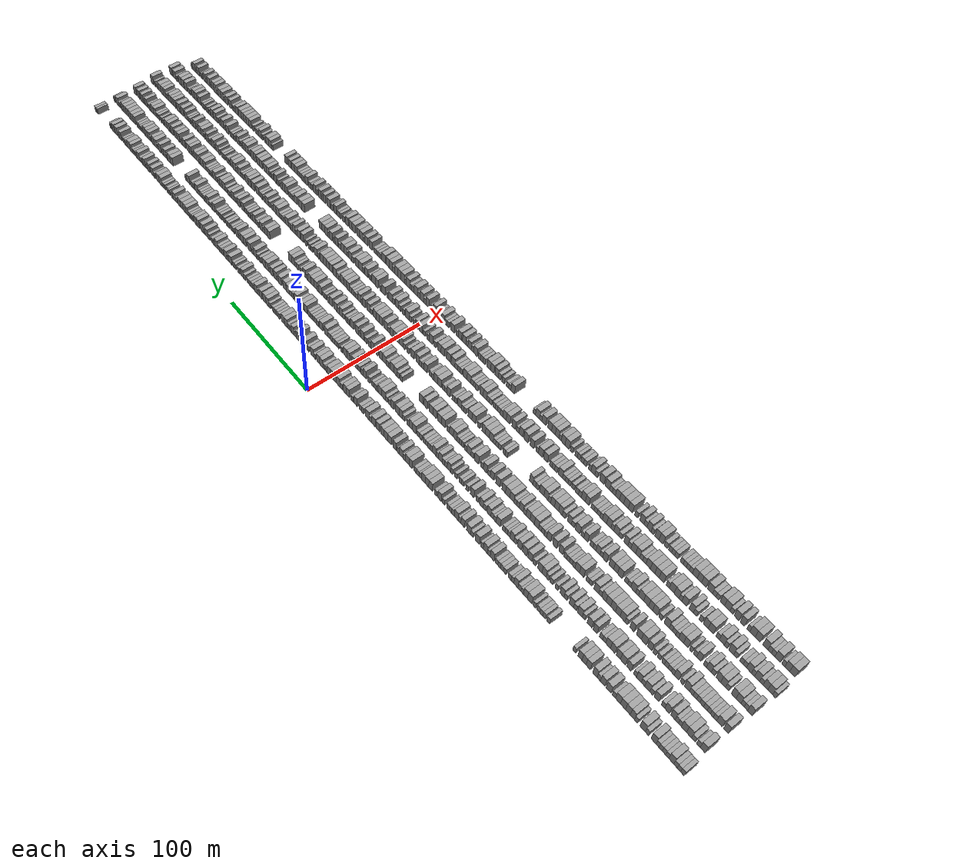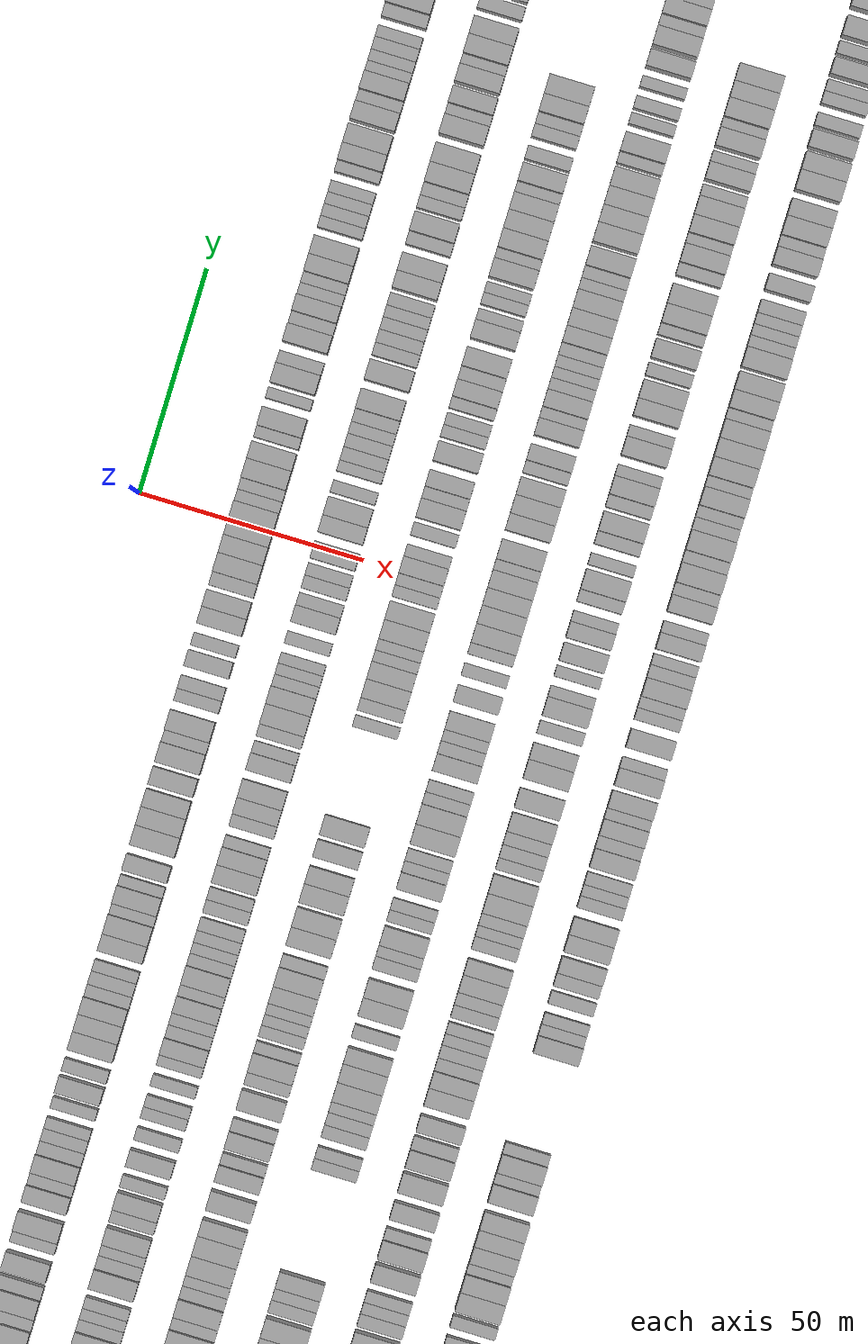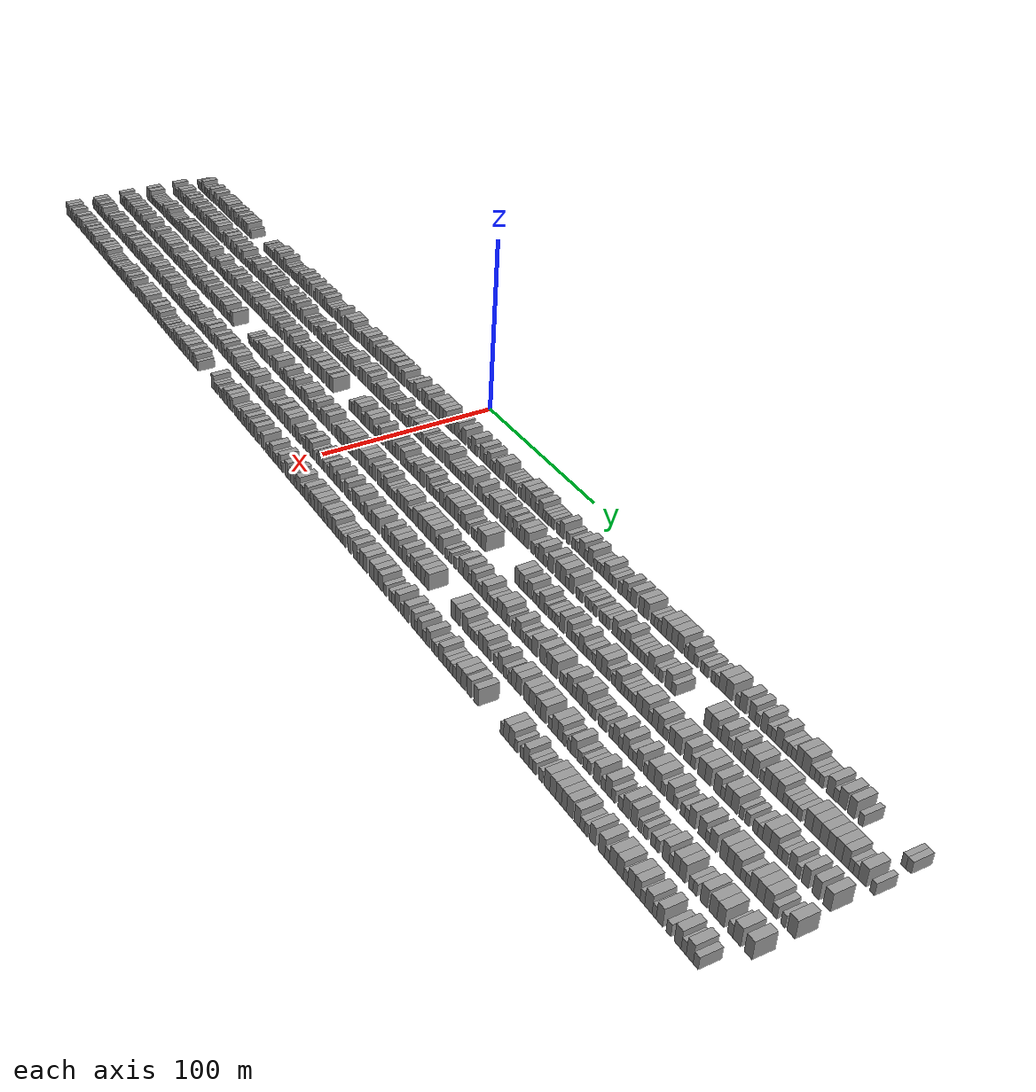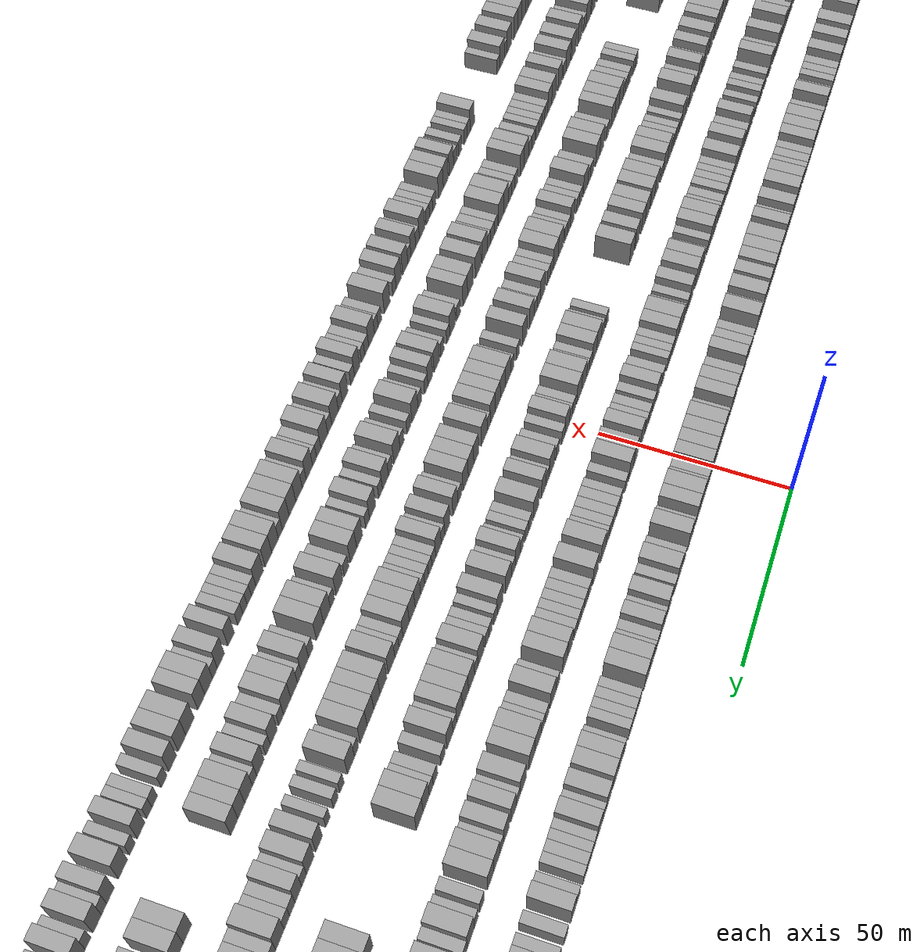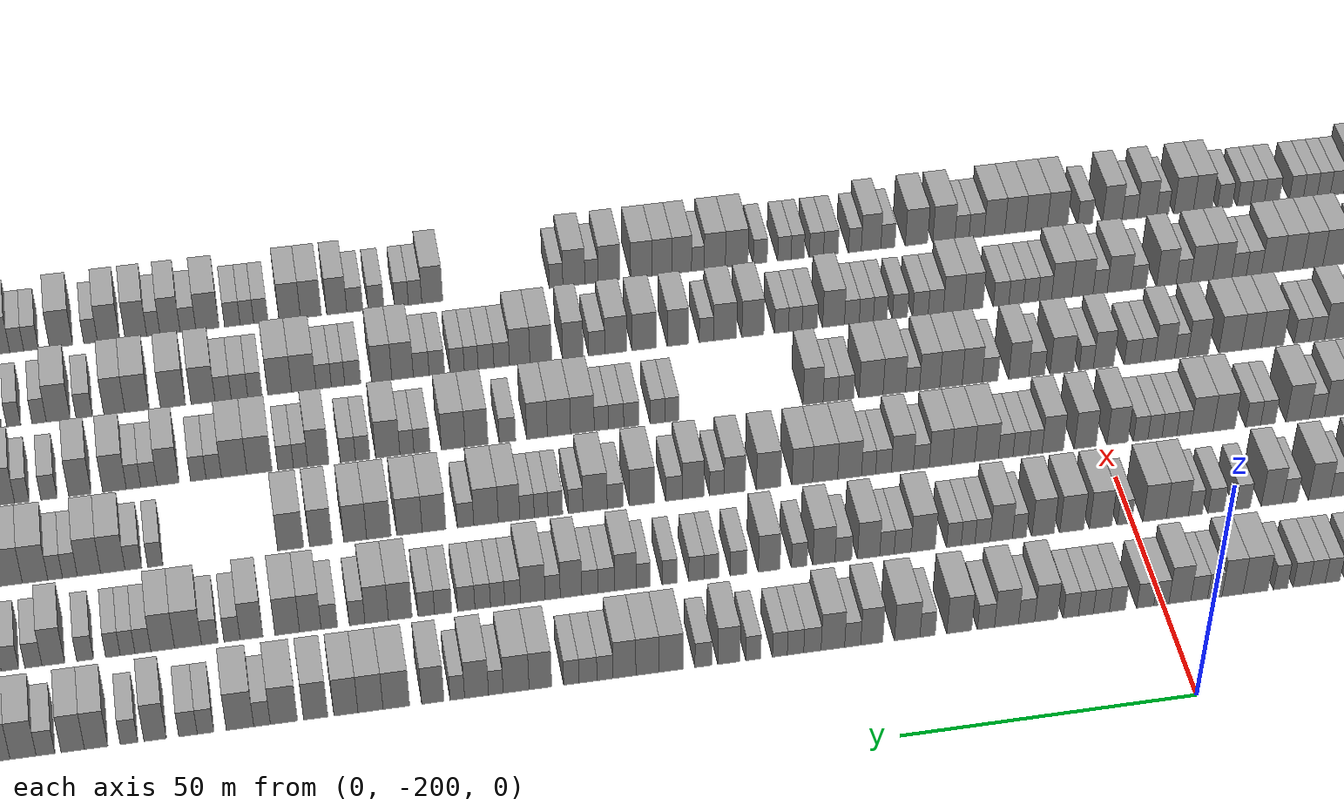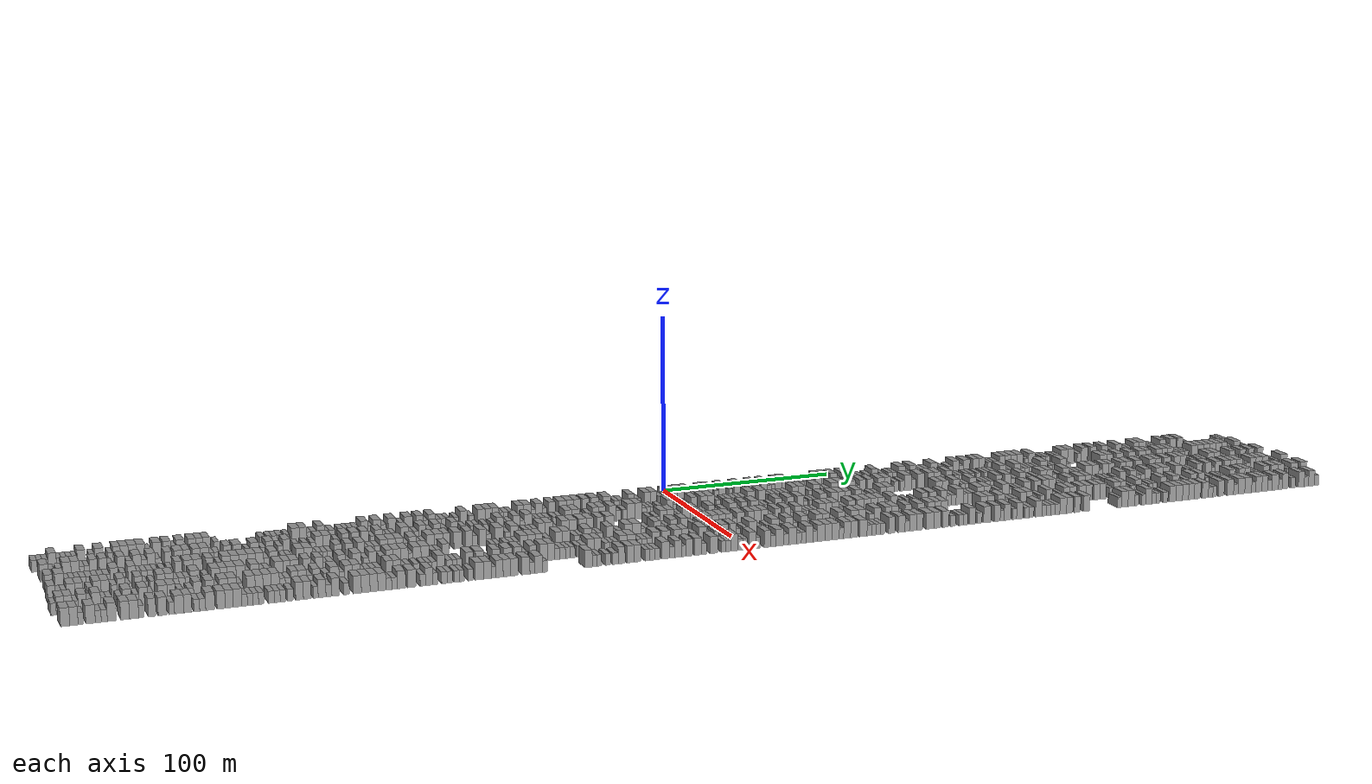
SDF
<sdf version="1.6">
 <world name="default">
  <scene>
   <sky><clouds><speed>12</speed></clouds></sky>
   <ambient>0.4 0.4 0.4 1</ambient>
   <background>0.7 0.7 0.7 1</background>
   <shadows>1</shadows>
  </scene>
  <gravity>0 0 -9.8066</gravity>
  <magnetic_field>6e-06 2.3e-05 -4.2e-05</magnetic_field>
  <physics default="0" name="default_physics" type="ode">
   <ode>
    <solver>
     <type>quick</type>
     <iters>10</iters>
     <sor>1.0</sor>
     <use_dynamic_moi_rescaling>0</use_dynamic_moi_rescaling>
    </solver>
    <constraints>
     <cfm>0</cfm>
     <erp>0.2</erp>
     <contact_max_correcting_vel>100</contact_max_correcting_vel>
     <contact_surface_layer>0.001</contact_surface_layer>
    </constraints>
   </ode>
   <max_step_size>0.004</max_step_size>
   <real_time_factor>1</real_time_factor>
   <real_time_update_rate>250</real_time_update_rate>
  </physics>
  <light name="sun" type="directional">
   <pose>0 0 10 0 0 0</pose>
   <diffuse>0.8 0.8 0.8 1</diffuse>
   <specular>0.2 0.2 0.2 1</specular>
   <attenuation>
    <range>1000</range>
    <constant>0.9</constant>
    <linear>0.01</linear>
    <quadratic>0.001</quadratic>
   </attenuation>
   <direction>-0.5 0.1 -0.9</direction>
  </light>
  <model name="building_1">
   <static>1</static>
   <pose>25.0000 -348.5948 0 0.000000 0.000000 0.000000</pose>
   <link name="link">
    <pose>0 0 3.00 0 0 0</pose>
    <collision name="collision"><geometry><box><size>10.0000 2.8103 6.0000</size></box></geometry></collision>
    <visual name="visual">
     <cast_shadows>0</cast_shadows>
     <geometry><box><size>10.0000 2.8103 6.0000</size></box></geometry>
     <material>
      <script>
       <uri>model://grey_wall/materials/scripts</uri>
       <uri>model://grey_wall/materials/textures</uri>
       <name>vrc/grey_wall</name>
      </script>
     </material>
    </visual>
   </link>
  </model>
  <model name="building_2">
   <static>1</static>
   <pose>25.0000 -345.8489 0 0.000000 0.000000 0.000000</pose>
   <link name="link">
    <pose>0 0 3.00 0 0 0</pose>
    <collision name="collision"><geometry><box><size>10.0000 2.6815 6.0000</size></box></geometry></collision>
    <visual name="visual">
     <cast_shadows>0</cast_shadows>
     <geometry><box><size>10.0000 2.6815 6.0000</size></box></geometry>
     <material>
      <script>
       <uri>model://grey_wall/materials/scripts</uri>
       <uri>model://grey_wall/materials/textures</uri>
       <name>vrc/grey_wall</name>
      </script>
     </material>
    </visual>
   </link>
  </model>
  <model name="building_3">
   <static>1</static>
   <pose>25.0000 -343.1325 0 0.000000 0.000000 0.000000</pose>
   <link name="link">
    <pose>0 0 3.00 0 0 0</pose>
    <collision name="collision"><geometry><box><size>10.0000 2.7512 6.0000</size></box></geometry></collision>
    <visual name="visual">
     <cast_shadows>0</cast_shadows>
     <geometry><box><size>10.0000 2.7512 6.0000</size></box></geometry>
     <material>
      <script>
       <uri>model://grey_wall/materials/scripts</uri>
       <uri>model://grey_wall/materials/textures</uri>
       <name>vrc/grey_wall</name>
      </script>
     </material>
    </visual>
   </link>
  </model>
  <model name="building_4">
   <static>1</static>
   <pose>25.0000 -339.7315 0 0.000000 0.000000 0.000000</pose>
   <link name="link">
    <pose>0 0 4.50 0 0 0</pose>
    <collision name="collision"><geometry><box><size>10.0000 4.0510 9.0000</size></box></geometry></collision>
    <visual name="visual">
     <cast_shadows>0</cast_shadows>
     <geometry><box><size>10.0000 4.0510 9.0000</size></box></geometry>
     <material>
      <script>
       <uri>model://grey_wall/materials/scripts</uri>
       <uri>model://grey_wall/materials/textures</uri>
       <name>vrc/grey_wall</name>
      </script>
     </material>
    </visual>
   </link>
  </model>
  <model name="building_5">
   <static>1</static>
   <pose>25.0000 -336.4116 0 0.000000 0.000000 0.000000</pose>
   <link name="link">
    <pose>0 0 3.00 0 0 0</pose>
    <collision name="collision"><geometry><box><size>10.0000 2.5887 6.0000</size></box></geometry></collision>
    <visual name="visual">
     <cast_shadows>0</cast_shadows>
     <geometry><box><size>10.0000 2.5887 6.0000</size></box></geometry>
     <material>
      <script>
       <uri>model://grey_wall/materials/scripts</uri>
       <uri>model://grey_wall/materials/textures</uri>
       <name>vrc/grey_wall</name>
      </script>
     </material>
    </visual>
   </link>
  </model>
  <model name="building_6">
   <static>1</static>
   <pose>25.0000 -333.8013 0 0.000000 0.000000 0.000000</pose>
   <link name="link">
    <pose>0 0 3.00 0 0 0</pose>
    <collision name="collision"><geometry><box><size>10.0000 2.6320 6.0000</size></box></geometry></collision>
    <visual name="visual">
     <cast_shadows>0</cast_shadows>
     <geometry><box><size>10.0000 2.6320 6.0000</size></box></geometry>
     <material>
      <script>
       <uri>model://grey_wall/materials/scripts</uri>
       <uri>model://grey_wall/materials/textures</uri>
       <name>vrc/grey_wall</name>
      </script>
     </material>
    </visual>
   </link>
  </model>
  <model name="building_7">
   <static>1</static>
   <pose>25.0000 -331.2124 0 0.000000 0.000000 0.000000</pose>
   <link name="link">
    <pose>0 0 3.00 0 0 0</pose>
    <collision name="collision"><geometry><box><size>10.0000 2.5458 6.0000</size></box></geometry></collision>
    <visual name="visual">
     <cast_shadows>0</cast_shadows>
     <geometry><box><size>10.0000 2.5458 6.0000</size></box></geometry>
     <material>
      <script>
       <uri>model://grey_wall/materials/scripts</uri>
       <uri>model://grey_wall/materials/textures</uri>
       <name>vrc/grey_wall</name>
      </script>
     </material>
    </visual>
   </link>
  </model>
  <model name="building_8">
   <static>1</static>
   <pose>25.0000 -328.6746 0 0.000000 0.000000 0.000000</pose>
   <link name="link">
    <pose>0 0 3.00 0 0 0</pose>
    <collision name="collision"><geometry><box><size>10.0000 2.5298 6.0000</size></box></geometry></collision>
    <visual name="visual">
     <cast_shadows>0</cast_shadows>
     <geometry><box><size>10.0000 2.5298 6.0000</size></box></geometry>
     <material>
      <script>
       <uri>model://grey_wall/materials/scripts</uri>
       <uri>model://grey_wall/materials/textures</uri>
       <name>vrc/grey_wall</name>
      </script>
     </material>
    </visual>
   </link>
  </model>
  <model name="building_9">
   <static>1</static>
   <pose>25.0000 -325.3544 0 0.000000 0.000000 0.000000</pose>
   <link name="link">
    <pose>0 0 4.50 0 0 0</pose>
    <collision name="collision"><geometry><box><size>10.0000 4.1104 9.0000</size></box></geometry></collision>
    <visual name="visual">
     <cast_shadows>0</cast_shadows>
     <geometry><box><size>10.0000 4.1104 9.0000</size></box></geometry>
     <material>
      <script>
       <uri>model://grey_wall/materials/scripts</uri>
       <uri>model://grey_wall/materials/textures</uri>
       <name>vrc/grey_wall</name>
      </script>
     </material>
    </visual>
   </link>
  </model>
  <model name="building_10">
   <static>1</static>
   <pose>25.0000 -319.9469 0 0.000000 0.000000 0.000000</pose>
   <link name="link">
    <pose>0 0 3.00 0 0 0</pose>
    <collision name="collision"><geometry><box><size>10.0000 2.7046 6.0000</size></box></geometry></collision>
    <visual name="visual">
     <cast_shadows>0</cast_shadows>
     <geometry><box><size>10.0000 2.7046 6.0000</size></box></geometry>
     <material>
      <script>
       <uri>model://grey_wall/materials/scripts</uri>
       <uri>model://grey_wall/materials/textures</uri>
       <name>vrc/grey_wall</name>
      </script>
     </material>
    </visual>
   </link>
  </model>
  <model name="building_11">
   <static>1</static>
   <pose>25.0000 -316.3787 0 0.000000 0.000000 0.000000</pose>
   <link name="link">
    <pose>0 0 4.50 0 0 0</pose>
    <collision name="collision"><geometry><box><size>10.0000 4.4319 9.0000</size></box></geometry></collision>
    <visual name="visual">
     <cast_shadows>0</cast_shadows>
     <geometry><box><size>10.0000 4.4319 9.0000</size></box></geometry>
     <material>
      <script>
       <uri>model://grey_wall/materials/scripts</uri>
       <uri>model://grey_wall/materials/textures</uri>
       <name>vrc/grey_wall</name>
      </script>
     </material>
    </visual>
   </link>
  </model>
  <model name="building_12">
   <static>1</static>
   <pose>25.0000 -310.8884 0 0.000000 0.000000 0.000000</pose>
   <link name="link">
    <pose>0 0 3.00 0 0 0</pose>
    <collision name="collision"><geometry><box><size>10.0000 2.5488 6.0000</size></box></geometry></collision>
    <visual name="visual">
     <cast_shadows>0</cast_shadows>
     <geometry><box><size>10.0000 2.5488 6.0000</size></box></geometry>
     <material>
      <script>
       <uri>model://grey_wall/materials/scripts</uri>
       <uri>model://grey_wall/materials/textures</uri>
       <name>vrc/grey_wall</name>
      </script>
     </material>
    </visual>
   </link>
  </model>
  <model name="building_13">
   <static>1</static>
   <pose>25.0000 -307.7867 0 0.000000 0.000000 0.000000</pose>
   <link name="link">
    <pose>0 0 4.50 0 0 0</pose>
    <collision name="collision"><geometry><box><size>10.0000 3.6547 9.0000</size></box></geometry></collision>
    <visual name="visual">
     <cast_shadows>0</cast_shadows>
     <geometry><box><size>10.0000 3.6547 9.0000</size></box></geometry>
     <material>
      <script>
       <uri>model://grey_wall/materials/scripts</uri>
       <uri>model://grey_wall/materials/textures</uri>
       <name>vrc/grey_wall</name>
      </script>
     </material>
    </visual>
   </link>
  </model>
  <model name="building_14">
   <static>1</static>
   <pose>25.0000 -303.9843 0 0.000000 0.000000 0.000000</pose>
   <link name="link">
    <pose>0 0 4.50 0 0 0</pose>
    <collision name="collision"><geometry><box><size>10.0000 3.9499 9.0000</size></box></geometry></collision>
    <visual name="visual">
     <cast_shadows>0</cast_shadows>
     <geometry><box><size>10.0000 3.9499 9.0000</size></box></geometry>
     <material>
      <script>
       <uri>model://grey_wall/materials/scripts</uri>
       <uri>model://grey_wall/materials/textures</uri>
       <name>vrc/grey_wall</name>
      </script>
     </material>
    </visual>
   </link>
  </model>
  <model name="building_15">
   <static>1</static>
   <pose>25.0000 -299.8745 0 0.000000 0.000000 0.000000</pose>
   <link name="link">
    <pose>0 0 4.50 0 0 0</pose>
    <collision name="collision"><geometry><box><size>10.0000 4.2697 9.0000</size></box></geometry></collision>
    <visual name="visual">
     <cast_shadows>0</cast_shadows>
     <geometry><box><size>10.0000 4.2697 9.0000</size></box></geometry>
     <material>
      <script>
       <uri>model://grey_wall/materials/scripts</uri>
       <uri>model://grey_wall/materials/textures</uri>
       <name>vrc/grey_wall</name>
      </script>
     </material>
    </visual>
   </link>
  </model>
  <model name="building_16">
   <static>1</static>
   <pose>25.0000 -295.5966 0 0.000000 0.000000 0.000000</pose>
   <link name="link">
    <pose>0 0 4.50 0 0 0</pose>
    <collision name="collision"><geometry><box><size>10.0000 4.2861 9.0000</size></box></geometry></collision>
    <visual name="visual">
     <cast_shadows>0</cast_shadows>
     <geometry><box><size>10.0000 4.2861 9.0000</size></box></geometry>
     <material>
      <script>
       <uri>model://grey_wall/materials/scripts</uri>
       <uri>model://grey_wall/materials/textures</uri>
       <name>vrc/grey_wall</name>
      </script>
     </material>
    </visual>
   </link>
  </model>
  <model name="building_17">
   <static>1</static>
   <pose>25.0000 -292.0606 0 0.000000 0.000000 0.000000</pose>
   <link name="link">
    <pose>0 0 3.00 0 0 0</pose>
    <collision name="collision"><geometry><box><size>10.0000 2.7860 6.0000</size></box></geometry></collision>
    <visual name="visual">
     <cast_shadows>0</cast_shadows>
     <geometry><box><size>10.0000 2.7860 6.0000</size></box></geometry>
     <material>
      <script>
       <uri>model://grey_wall/materials/scripts</uri>
       <uri>model://grey_wall/materials/textures</uri>
       <name>vrc/grey_wall</name>
      </script>
     </material>
    </visual>
   </link>
  </model>
  <model name="building_18">
   <static>1</static>
   <pose>25.0000 -287.5462 0 0.000000 0.000000 0.000000</pose>
   <link name="link">
    <pose>0 0 4.50 0 0 0</pose>
    <collision name="collision"><geometry><box><size>10.0000 4.2428 9.0000</size></box></geometry></collision>
    <visual name="visual">
     <cast_shadows>0</cast_shadows>
     <geometry><box><size>10.0000 4.2428 9.0000</size></box></geometry>
     <material>
      <script>
       <uri>model://grey_wall/materials/scripts</uri>
       <uri>model://grey_wall/materials/textures</uri>
       <name>vrc/grey_wall</name>
      </script>
     </material>
    </visual>
   </link>
  </model>
  <model name="building_19">
   <static>1</static>
   <pose>25.0000 -282.4468 0 0.000000 0.000000 0.000000</pose>
   <link name="link">
    <pose>0 0 4.50 0 0 0</pose>
    <collision name="collision"><geometry><box><size>10.0000 3.9561 9.0000</size></box></geometry></collision>
    <visual name="visual">
     <cast_shadows>0</cast_shadows>
     <geometry><box><size>10.0000 3.9561 9.0000</size></box></geometry>
     <material>
      <script>
       <uri>model://grey_wall/materials/scripts</uri>
       <uri>model://grey_wall/materials/textures</uri>
       <name>vrc/grey_wall</name>
      </script>
     </material>
    </visual>
   </link>
  </model>
  <model name="building_20">
   <static>1</static>
   <pose>25.0000 -279.0800 0 0.000000 0.000000 0.000000</pose>
   <link name="link">
    <pose>0 0 3.00 0 0 0</pose>
    <collision name="collision"><geometry><box><size>10.0000 2.7774 6.0000</size></box></geometry></collision>
    <visual name="visual">
     <cast_shadows>0</cast_shadows>
     <geometry><box><size>10.0000 2.7774 6.0000</size></box></geometry>
     <material>
      <script>
       <uri>model://grey_wall/materials/scripts</uri>
       <uri>model://grey_wall/materials/textures</uri>
       <name>vrc/grey_wall</name>
      </script>
     </material>
    </visual>
   </link>
  </model>
  <model name="building_21">
   <static>1</static>
   <pose>25.0000 -275.6909 0 0.000000 0.000000 0.000000</pose>
   <link name="link">
    <pose>0 0 4.50 0 0 0</pose>
    <collision name="collision"><geometry><box><size>10.0000 4.0008 9.0000</size></box></geometry></collision>
    <visual name="visual">
     <cast_shadows>0</cast_shadows>
     <geometry><box><size>10.0000 4.0008 9.0000</size></box></geometry>
     <material>
      <script>
       <uri>model://grey_wall/materials/scripts</uri>
       <uri>model://grey_wall/materials/textures</uri>
       <name>vrc/grey_wall</name>
      </script>
     </material>
    </visual>
   </link>
  </model>
  <model name="building_22">
   <static>1</static>
   <pose>25.0000 -269.7736 0 0.000000 0.000000 0.000000</pose>
   <link name="link">
    <pose>0 0 4.50 0 0 0</pose>
    <collision name="collision"><geometry><box><size>10.0000 3.8338 9.0000</size></box></geometry></collision>
    <visual name="visual">
     <cast_shadows>0</cast_shadows>
     <geometry><box><size>10.0000 3.8338 9.0000</size></box></geometry>
     <material>
      <script>
       <uri>model://grey_wall/materials/scripts</uri>
       <uri>model://grey_wall/materials/textures</uri>
       <name>vrc/grey_wall</name>
      </script>
     </material>
    </visual>
   </link>
  </model>
  <model name="building_23">
   <static>1</static>
   <pose>25.0000 -266.0388 0 0.000000 0.000000 0.000000</pose>
   <link name="link">
    <pose>0 0 4.50 0 0 0</pose>
    <collision name="collision"><geometry><box><size>10.0000 3.6357 9.0000</size></box></geometry></collision>
    <visual name="visual">
     <cast_shadows>0</cast_shadows>
     <geometry><box><size>10.0000 3.6357 9.0000</size></box></geometry>
     <material>
      <script>
       <uri>model://grey_wall/materials/scripts</uri>
       <uri>model://grey_wall/materials/textures</uri>
       <name>vrc/grey_wall</name>
      </script>
     </material>
    </visual>
   </link>
  </model>
  <model name="building_24">
   <static>1</static>
   <pose>25.0000 -262.4024 0 0.000000 0.000000 0.000000</pose>
   <link name="link">
    <pose>0 0 4.50 0 0 0</pose>
    <collision name="collision"><geometry><box><size>10.0000 3.6371 9.0000</size></box></geometry></collision>
    <visual name="visual">
     <cast_shadows>0</cast_shadows>
     <geometry><box><size>10.0000 3.6371 9.0000</size></box></geometry>
     <material>
      <script>
       <uri>model://grey_wall/materials/scripts</uri>
       <uri>model://grey_wall/materials/textures</uri>
       <name>vrc/grey_wall</name>
      </script>
     </material>
    </visual>
   </link>
  </model>
  <model name="building_25">
   <static>1</static>
   <pose>25.0000 -257.2900 0 0.000000 0.000000 0.000000</pose>
   <link name="link">
    <pose>0 0 3.00 0 0 0</pose>
    <collision name="collision"><geometry><box><size>10.0000 2.5878 6.0000</size></box></geometry></collision>
    <visual name="visual">
     <cast_shadows>0</cast_shadows>
     <geometry><box><size>10.0000 2.5878 6.0000</size></box></geometry>
     <material>
      <script>
       <uri>model://grey_wall/materials/scripts</uri>
       <uri>model://grey_wall/materials/textures</uri>
       <name>vrc/grey_wall</name>
      </script>
     </material>
    </visual>
   </link>
  </model>
  <model name="building_26">
   <static>1</static>
   <pose>25.0000 -233.5116 0 0.000000 0.000000 0.000000</pose>
   <link name="link">
    <pose>0 0 3.00 0 0 0</pose>
    <collision name="collision"><geometry><box><size>10.0000 2.9897 6.0000</size></box></geometry></collision>
    <visual name="visual">
     <cast_shadows>0</cast_shadows>
     <geometry><box><size>10.0000 2.9897 6.0000</size></box></geometry>
     <material>
      <script>
       <uri>model://grey_wall/materials/scripts</uri>
       <uri>model://grey_wall/materials/textures</uri>
       <name>vrc/grey_wall</name>
      </script>
     </material>
    </visual>
   </link>
  </model>
  <model name="building_27">
   <static>1</static>
   <pose>25.0000 -229.7258 0 0.000000 0.000000 0.000000</pose>
   <link name="link">
    <pose>0 0 3.00 0 0 0</pose>
    <collision name="collision"><geometry><box><size>10.0000 2.5821 6.0000</size></box></geometry></collision>
    <visual name="visual">
     <cast_shadows>0</cast_shadows>
     <geometry><box><size>10.0000 2.5821 6.0000</size></box></geometry>
     <material>
      <script>
       <uri>model://grey_wall/materials/scripts</uri>
       <uri>model://grey_wall/materials/textures</uri>
       <name>vrc/grey_wall</name>
      </script>
     </material>
    </visual>
   </link>
  </model>
  <model name="building_28">
   <static>1</static>
   <pose>25.0000 -227.0556 0 0.000000 0.000000 0.000000</pose>
   <link name="link">
    <pose>0 0 3.00 0 0 0</pose>
    <collision name="collision"><geometry><box><size>10.0000 2.7582 6.0000</size></box></geometry></collision>
    <visual name="visual">
     <cast_shadows>0</cast_shadows>
     <geometry><box><size>10.0000 2.7582 6.0000</size></box></geometry>
     <material>
      <script>
       <uri>model://grey_wall/materials/scripts</uri>
       <uri>model://grey_wall/materials/textures</uri>
       <name>vrc/grey_wall</name>
      </script>
     </material>
    </visual>
   </link>
  </model>
  <model name="building_29">
   <static>1</static>
   <pose>25.0000 -224.2311 0 0.000000 0.000000 0.000000</pose>
   <link name="link">
    <pose>0 0 3.00 0 0 0</pose>
    <collision name="collision"><geometry><box><size>10.0000 2.8908 6.0000</size></box></geometry></collision>
    <visual name="visual">
     <cast_shadows>0</cast_shadows>
     <geometry><box><size>10.0000 2.8908 6.0000</size></box></geometry>
     <material>
      <script>
       <uri>model://grey_wall/materials/scripts</uri>
       <uri>model://grey_wall/materials/textures</uri>
       <name>vrc/grey_wall</name>
      </script>
     </material>
    </visual>
   </link>
  </model>
  <model name="building_30">
   <static>1</static>
   <pose>25.0000 -220.5526 0 0.000000 0.000000 0.000000</pose>
   <link name="link">
    <pose>0 0 3.00 0 0 0</pose>
    <collision name="collision"><geometry><box><size>10.0000 2.4663 6.0000</size></box></geometry></collision>
    <visual name="visual">
     <cast_shadows>0</cast_shadows>
     <geometry><box><size>10.0000 2.4663 6.0000</size></box></geometry>
     <material>
      <script>
       <uri>model://grey_wall/materials/scripts</uri>
       <uri>model://grey_wall/materials/textures</uri>
       <name>vrc/grey_wall</name>
      </script>
     </material>
    </visual>
   </link>
  </model>
  <model name="building_31">
   <static>1</static>
   <pose>25.0000 -216.1417 0 0.000000 0.000000 0.000000</pose>
   <link name="link">
    <pose>0 0 4.50 0 0 0</pose>
    <collision name="collision"><geometry><box><size>10.0000 4.3555 9.0000</size></box></geometry></collision>
    <visual name="visual">
     <cast_shadows>0</cast_shadows>
     <geometry><box><size>10.0000 4.3555 9.0000</size></box></geometry>
     <material>
      <script>
       <uri>model://grey_wall/materials/scripts</uri>
       <uri>model://grey_wall/materials/textures</uri>
       <name>vrc/grey_wall</name>
      </script>
     </material>
    </visual>
   </link>
  </model>
  <model name="building_32">
   <static>1</static>
   <pose>25.0000 -212.1116 0 0.000000 0.000000 0.000000</pose>
   <link name="link">
    <pose>0 0 4.50 0 0 0</pose>
    <collision name="collision"><geometry><box><size>10.0000 3.7047 9.0000</size></box></geometry></collision>
    <visual name="visual">
     <cast_shadows>0</cast_shadows>
     <geometry><box><size>10.0000 3.7047 9.0000</size></box></geometry>
     <material>
      <script>
       <uri>model://grey_wall/materials/scripts</uri>
       <uri>model://grey_wall/materials/textures</uri>
       <name>vrc/grey_wall</name>
      </script>
     </material>
    </visual>
   </link>
  </model>
  <model name="building_33">
   <static>1</static>
   <pose>25.0000 -208.9990 0 0.000000 0.000000 0.000000</pose>
   <link name="link">
    <pose>0 0 3.00 0 0 0</pose>
    <collision name="collision"><geometry><box><size>10.0000 2.5204 6.0000</size></box></geometry></collision>
    <visual name="visual">
     <cast_shadows>0</cast_shadows>
     <geometry><box><size>10.0000 2.5204 6.0000</size></box></geometry>
     <material>
      <script>
       <uri>model://grey_wall/materials/scripts</uri>
       <uri>model://grey_wall/materials/textures</uri>
       <name>vrc/grey_wall</name>
      </script>
     </material>
    </visual>
   </link>
  </model>
  <model name="building_34">
   <static>1</static>
   <pose>25.0000 -206.2653 0 0.000000 0.000000 0.000000</pose>
   <link name="link">
    <pose>0 0 3.00 0 0 0</pose>
    <collision name="collision"><geometry><box><size>10.0000 2.9470 6.0000</size></box></geometry></collision>
    <visual name="visual">
     <cast_shadows>0</cast_shadows>
     <geometry><box><size>10.0000 2.9470 6.0000</size></box></geometry>
     <material>
      <script>
       <uri>model://grey_wall/materials/scripts</uri>
       <uri>model://grey_wall/materials/textures</uri>
       <name>vrc/grey_wall</name>
      </script>
     </material>
    </visual>
   </link>
  </model>
  <model name="building_35">
   <static>1</static>
   <pose>25.0000 -202.8651 0 0.000000 0.000000 0.000000</pose>
   <link name="link">
    <pose>0 0 4.50 0 0 0</pose>
    <collision name="collision"><geometry><box><size>10.0000 3.8532 9.0000</size></box></geometry></collision>
    <visual name="visual">
     <cast_shadows>0</cast_shadows>
     <geometry><box><size>10.0000 3.8532 9.0000</size></box></geometry>
     <material>
      <script>
       <uri>model://grey_wall/materials/scripts</uri>
       <uri>model://grey_wall/materials/textures</uri>
       <name>vrc/grey_wall</name>
      </script>
     </material>
    </visual>
   </link>
  </model>
  <model name="building_36">
   <static>1</static>
   <pose>25.0000 -199.6421 0 0.000000 0.000000 0.000000</pose>
   <link name="link">
    <pose>0 0 3.00 0 0 0</pose>
    <collision name="collision"><geometry><box><size>10.0000 2.5929 6.0000</size></box></geometry></collision>
    <visual name="visual">
     <cast_shadows>0</cast_shadows>
     <geometry><box><size>10.0000 2.5929 6.0000</size></box></geometry>
     <material>
      <script>
       <uri>model://grey_wall/materials/scripts</uri>
       <uri>model://grey_wall/materials/textures</uri>
       <name>vrc/grey_wall</name>
      </script>
     </material>
    </visual>
   </link>
  </model>
  <model name="building_37">
   <static>1</static>
   <pose>25.0000 -196.8512 0 0.000000 0.000000 0.000000</pose>
   <link name="link">
    <pose>0 0 3.00 0 0 0</pose>
    <collision name="collision"><geometry><box><size>10.0000 2.9890 6.0000</size></box></geometry></collision>
    <visual name="visual">
     <cast_shadows>0</cast_shadows>
     <geometry><box><size>10.0000 2.9890 6.0000</size></box></geometry>
     <material>
      <script>
       <uri>model://grey_wall/materials/scripts</uri>
       <uri>model://grey_wall/materials/textures</uri>
       <name>vrc/grey_wall</name>
      </script>
     </material>
    </visual>
   </link>
  </model>
  <model name="building_38">
   <static>1</static>
   <pose>25.0000 -191.9824 0 0.000000 0.000000 0.000000</pose>
   <link name="link">
    <pose>0 0 3.00 0 0 0</pose>
    <collision name="collision"><geometry><box><size>10.0000 2.7486 6.0000</size></box></geometry></collision>
    <visual name="visual">
     <cast_shadows>0</cast_shadows>
     <geometry><box><size>10.0000 2.7486 6.0000</size></box></geometry>
     <material>
      <script>
       <uri>model://grey_wall/materials/scripts</uri>
       <uri>model://grey_wall/materials/textures</uri>
       <name>vrc/grey_wall</name>
      </script>
     </material>
    </visual>
   </link>
  </model>
  <model name="building_39">
   <static>1</static>
   <pose>25.0000 -189.2116 0 0.000000 0.000000 0.000000</pose>
   <link name="link">
    <pose>0 0 3.00 0 0 0</pose>
    <collision name="collision"><geometry><box><size>10.0000 2.7929 6.0000</size></box></geometry></collision>
    <visual name="visual">
     <cast_shadows>0</cast_shadows>
     <geometry><box><size>10.0000 2.7929 6.0000</size></box></geometry>
     <material>
      <script>
       <uri>model://grey_wall/materials/scripts</uri>
       <uri>model://grey_wall/materials/textures</uri>
       <name>vrc/grey_wall</name>
      </script>
     </material>
    </visual>
   </link>
  </model>
  <model name="building_40">
   <static>1</static>
   <pose>25.0000 -186.5201 0 0.000000 0.000000 0.000000</pose>
   <link name="link">
    <pose>0 0 3.00 0 0 0</pose>
    <collision name="collision"><geometry><box><size>10.0000 2.5901 6.0000</size></box></geometry></collision>
    <visual name="visual">
     <cast_shadows>0</cast_shadows>
     <geometry><box><size>10.0000 2.5901 6.0000</size></box></geometry>
     <material>
      <script>
       <uri>model://grey_wall/materials/scripts</uri>
       <uri>model://grey_wall/materials/textures</uri>
       <name>vrc/grey_wall</name>
      </script>
     </material>
    </visual>
   </link>
  </model>
  <model name="building_41">
   <static>1</static>
   <pose>25.0000 -183.9084 0 0.000000 0.000000 0.000000</pose>
   <link name="link">
    <pose>0 0 3.00 0 0 0</pose>
    <collision name="collision"><geometry><box><size>10.0000 2.6333 6.0000</size></box></geometry></collision>
    <visual name="visual">
     <cast_shadows>0</cast_shadows>
     <geometry><box><size>10.0000 2.6333 6.0000</size></box></geometry>
     <material>
      <script>
       <uri>model://grey_wall/materials/scripts</uri>
       <uri>model://grey_wall/materials/textures</uri>
       <name>vrc/grey_wall</name>
      </script>
     </material>
    </visual>
   </link>
  </model>
  <model name="building_42">
   <static>1</static>
   <pose>25.0000 -179.6221 0 0.000000 0.000000 0.000000</pose>
   <link name="link">
    <pose>0 0 4.50 0 0 0</pose>
    <collision name="collision"><geometry><box><size>10.0000 3.9394 9.0000</size></box></geometry></collision>
    <visual name="visual">
     <cast_shadows>0</cast_shadows>
     <geometry><box><size>10.0000 3.9394 9.0000</size></box></geometry>
     <material>
      <script>
       <uri>model://grey_wall/materials/scripts</uri>
       <uri>model://grey_wall/materials/textures</uri>
       <name>vrc/grey_wall</name>
      </script>
     </material>
    </visual>
   </link>
  </model>
  <model name="building_43">
   <static>1</static>
   <pose>25.0000 -176.2535 0 0.000000 0.000000 0.000000</pose>
   <link name="link">
    <pose>0 0 3.00 0 0 0</pose>
    <collision name="collision"><geometry><box><size>10.0000 2.7978 6.0000</size></box></geometry></collision>
    <visual name="visual">
     <cast_shadows>0</cast_shadows>
     <geometry><box><size>10.0000 2.7978 6.0000</size></box></geometry>
     <material>
      <script>
       <uri>model://grey_wall/materials/scripts</uri>
       <uri>model://grey_wall/materials/textures</uri>
       <name>vrc/grey_wall</name>
      </script>
     </material>
    </visual>
   </link>
  </model>
  <model name="building_44">
   <static>1</static>
   <pose>25.0000 -172.7922 0 0.000000 0.000000 0.000000</pose>
   <link name="link">
    <pose>0 0 4.50 0 0 0</pose>
    <collision name="collision"><geometry><box><size>10.0000 4.1246 9.0000</size></box></geometry></collision>
    <visual name="visual">
     <cast_shadows>0</cast_shadows>
     <geometry><box><size>10.0000 4.1246 9.0000</size></box></geometry>
     <material>
      <script>
       <uri>model://grey_wall/materials/scripts</uri>
       <uri>model://grey_wall/materials/textures</uri>
       <name>vrc/grey_wall</name>
      </script>
     </material>
    </visual>
   </link>
  </model>
  <model name="building_45">
   <static>1</static>
   <pose>25.0000 -169.2638 0 0.000000 0.000000 0.000000</pose>
   <link name="link">
    <pose>0 0 3.00 0 0 0</pose>
    <collision name="collision"><geometry><box><size>10.0000 2.9322 6.0000</size></box></geometry></collision>
    <visual name="visual">
     <cast_shadows>0</cast_shadows>
     <geometry><box><size>10.0000 2.9322 6.0000</size></box></geometry>
     <material>
      <script>
       <uri>model://grey_wall/materials/scripts</uri>
       <uri>model://grey_wall/materials/textures</uri>
       <name>vrc/grey_wall</name>
      </script>
     </material>
    </visual>
   </link>
  </model>
  <model name="building_46">
   <static>1</static>
   <pose>25.0000 -164.6621 0 0.000000 0.000000 0.000000</pose>
   <link name="link">
    <pose>0 0 4.50 0 0 0</pose>
    <collision name="collision"><geometry><box><size>10.0000 4.2710 9.0000</size></box></geometry></collision>
    <visual name="visual">
     <cast_shadows>0</cast_shadows>
     <geometry><box><size>10.0000 4.2710 9.0000</size></box></geometry>
     <material>
      <script>
       <uri>model://grey_wall/materials/scripts</uri>
       <uri>model://grey_wall/materials/textures</uri>
       <name>vrc/grey_wall</name>
      </script>
     </material>
    </visual>
   </link>
  </model>
  <model name="building_47">
   <static>1</static>
   <pose>25.0000 -159.2184 0 0.000000 0.000000 0.000000</pose>
   <link name="link">
    <pose>0 0 3.00 0 0 0</pose>
    <collision name="collision"><geometry><box><size>10.0000 2.6165 6.0000</size></box></geometry></collision>
    <visual name="visual">
     <cast_shadows>0</cast_shadows>
     <geometry><box><size>10.0000 2.6165 6.0000</size></box></geometry>
     <material>
      <script>
       <uri>model://grey_wall/materials/scripts</uri>
       <uri>model://grey_wall/materials/textures</uri>
       <name>vrc/grey_wall</name>
      </script>
     </material>
    </visual>
   </link>
  </model>
  <model name="building_48">
   <static>1</static>
   <pose>25.0000 -155.7298 0 0.000000 0.000000 0.000000</pose>
   <link name="link">
    <pose>0 0 4.50 0 0 0</pose>
    <collision name="collision"><geometry><box><size>10.0000 4.3605 9.0000</size></box></geometry></collision>
    <visual name="visual">
     <cast_shadows>0</cast_shadows>
     <geometry><box><size>10.0000 4.3605 9.0000</size></box></geometry>
     <material>
      <script>
       <uri>model://grey_wall/materials/scripts</uri>
       <uri>model://grey_wall/materials/textures</uri>
       <name>vrc/grey_wall</name>
      </script>
     </material>
    </visual>
   </link>
  </model>
  <model name="building_49">
   <static>1</static>
   <pose>25.0000 -149.6635 0 0.000000 0.000000 0.000000</pose>
   <link name="link">
    <pose>0 0 4.50 0 0 0</pose>
    <collision name="collision"><geometry><box><size>10.0000 3.7723 9.0000</size></box></geometry></collision>
    <visual name="visual">
     <cast_shadows>0</cast_shadows>
     <geometry><box><size>10.0000 3.7723 9.0000</size></box></geometry>
     <material>
      <script>
       <uri>model://grey_wall/materials/scripts</uri>
       <uri>model://grey_wall/materials/textures</uri>
       <name>vrc/grey_wall</name>
      </script>
     </material>
    </visual>
   </link>
  </model>
  <model name="building_50">
   <static>1</static>
   <pose>25.0000 -146.4095 0 0.000000 0.000000 0.000000</pose>
   <link name="link">
    <pose>0 0 3.00 0 0 0</pose>
    <collision name="collision"><geometry><box><size>10.0000 2.7356 6.0000</size></box></geometry></collision>
    <visual name="visual">
     <cast_shadows>0</cast_shadows>
     <geometry><box><size>10.0000 2.7356 6.0000</size></box></geometry>
     <material>
      <script>
       <uri>model://grey_wall/materials/scripts</uri>
       <uri>model://grey_wall/materials/textures</uri>
       <name>vrc/grey_wall</name>
      </script>
     </material>
    </visual>
   </link>
  </model>
  <model name="building_51">
   <static>1</static>
   <pose>25.0000 -143.0372 0 0.000000 0.000000 0.000000</pose>
   <link name="link">
    <pose>0 0 4.50 0 0 0</pose>
    <collision name="collision"><geometry><box><size>10.0000 4.0091 9.0000</size></box></geometry></collision>
    <visual name="visual">
     <cast_shadows>0</cast_shadows>
     <geometry><box><size>10.0000 4.0091 9.0000</size></box></geometry>
     <material>
      <script>
       <uri>model://grey_wall/materials/scripts</uri>
       <uri>model://grey_wall/materials/textures</uri>
       <name>vrc/grey_wall</name>
      </script>
     </material>
    </visual>
   </link>
  </model>
  <model name="building_52">
   <static>1</static>
   <pose>25.0000 -139.5609 0 0.000000 0.000000 0.000000</pose>
   <link name="link">
    <pose>0 0 3.00 0 0 0</pose>
    <collision name="collision"><geometry><box><size>10.0000 2.9435 6.0000</size></box></geometry></collision>
    <visual name="visual">
     <cast_shadows>0</cast_shadows>
     <geometry><box><size>10.0000 2.9435 6.0000</size></box></geometry>
     <material>
      <script>
       <uri>model://grey_wall/materials/scripts</uri>
       <uri>model://grey_wall/materials/textures</uri>
       <name>vrc/grey_wall</name>
      </script>
     </material>
    </visual>
   </link>
  </model>
  <model name="building_53">
   <static>1</static>
   <pose>25.0000 -136.6943 0 0.000000 0.000000 0.000000</pose>
   <link name="link">
    <pose>0 0 3.00 0 0 0</pose>
    <collision name="collision"><geometry><box><size>10.0000 2.7898 6.0000</size></box></geometry></collision>
    <visual name="visual">
     <cast_shadows>0</cast_shadows>
     <geometry><box><size>10.0000 2.7898 6.0000</size></box></geometry>
     <material>
      <script>
       <uri>model://grey_wall/materials/scripts</uri>
       <uri>model://grey_wall/materials/textures</uri>
       <name>vrc/grey_wall</name>
      </script>
     </material>
    </visual>
   </link>
  </model>
  <model name="building_54">
   <static>1</static>
   <pose>25.0000 -134.0482 0 0.000000 0.000000 0.000000</pose>
   <link name="link">
    <pose>0 0 3.00 0 0 0</pose>
    <collision name="collision"><geometry><box><size>10.0000 2.5023 6.0000</size></box></geometry></collision>
    <visual name="visual">
     <cast_shadows>0</cast_shadows>
     <geometry><box><size>10.0000 2.5023 6.0000</size></box></geometry>
     <material>
      <script>
       <uri>model://grey_wall/materials/scripts</uri>
       <uri>model://grey_wall/materials/textures</uri>
       <name>vrc/grey_wall</name>
      </script>
     </material>
    </visual>
   </link>
  </model>
  <model name="building_55">
   <static>1</static>
   <pose>25.0000 -129.5358 0 0.000000 0.000000 0.000000</pose>
   <link name="link">
    <pose>0 0 3.00 0 0 0</pose>
    <collision name="collision"><geometry><box><size>10.0000 2.5225 6.0000</size></box></geometry></collision>
    <visual name="visual">
     <cast_shadows>0</cast_shadows>
     <geometry><box><size>10.0000 2.5225 6.0000</size></box></geometry>
     <material>
      <script>
       <uri>model://grey_wall/materials/scripts</uri>
       <uri>model://grey_wall/materials/textures</uri>
       <name>vrc/grey_wall</name>
      </script>
     </material>
    </visual>
   </link>
  </model>
  <model name="building_56">
   <static>1</static>
   <pose>25.0000 -125.4137 0 0.000000 0.000000 0.000000</pose>
   <link name="link">
    <pose>0 0 4.50 0 0 0</pose>
    <collision name="collision"><geometry><box><size>10.0000 3.7218 9.0000</size></box></geometry></collision>
    <visual name="visual">
     <cast_shadows>0</cast_shadows>
     <geometry><box><size>10.0000 3.7218 9.0000</size></box></geometry>
     <material>
      <script>
       <uri>model://grey_wall/materials/scripts</uri>
       <uri>model://grey_wall/materials/textures</uri>
       <name>vrc/grey_wall</name>
      </script>
     </material>
    </visual>
   </link>
  </model>
  <model name="building_57">
   <static>1</static>
   <pose>25.0000 -121.1268 0 0.000000 0.000000 0.000000</pose>
   <link name="link">
    <pose>0 0 3.00 0 0 0</pose>
    <collision name="collision"><geometry><box><size>10.0000 2.8519 6.0000</size></box></geometry></collision>
    <visual name="visual">
     <cast_shadows>0</cast_shadows>
     <geometry><box><size>10.0000 2.8519 6.0000</size></box></geometry>
     <material>
      <script>
       <uri>model://grey_wall/materials/scripts</uri>
       <uri>model://grey_wall/materials/textures</uri>
       <name>vrc/grey_wall</name>
      </script>
     </material>
    </visual>
   </link>
  </model>
  <model name="building_58">
   <static>1</static>
   <pose>25.0000 -115.6798 0 0.000000 0.000000 0.000000</pose>
   <link name="link">
    <pose>0 0 4.50 0 0 0</pose>
    <collision name="collision"><geometry><box><size>10.0000 4.0421 9.0000</size></box></geometry></collision>
    <visual name="visual">
     <cast_shadows>0</cast_shadows>
     <geometry><box><size>10.0000 4.0421 9.0000</size></box></geometry>
     <material>
      <script>
       <uri>model://grey_wall/materials/scripts</uri>
       <uri>model://grey_wall/materials/textures</uri>
       <name>vrc/grey_wall</name>
      </script>
     </material>
    </visual>
   </link>
  </model>
  <model name="building_59">
   <static>1</static>
   <pose>25.0000 -111.7224 0 0.000000 0.000000 0.000000</pose>
   <link name="link">
    <pose>0 0 4.50 0 0 0</pose>
    <collision name="collision"><geometry><box><size>10.0000 3.8728 9.0000</size></box></geometry></collision>
    <visual name="visual">
     <cast_shadows>0</cast_shadows>
     <geometry><box><size>10.0000 3.8728 9.0000</size></box></geometry>
     <material>
      <script>
       <uri>model://grey_wall/materials/scripts</uri>
       <uri>model://grey_wall/materials/textures</uri>
       <name>vrc/grey_wall</name>
      </script>
     </material>
    </visual>
   </link>
  </model>
  <model name="building_60">
   <static>1</static>
   <pose>25.0000 -107.8807 0 0.000000 0.000000 0.000000</pose>
   <link name="link">
    <pose>0 0 4.50 0 0 0</pose>
    <collision name="collision"><geometry><box><size>10.0000 3.8105 9.0000</size></box></geometry></collision>
    <visual name="visual">
     <cast_shadows>0</cast_shadows>
     <geometry><box><size>10.0000 3.8105 9.0000</size></box></geometry>
     <material>
      <script>
       <uri>model://grey_wall/materials/scripts</uri>
       <uri>model://grey_wall/materials/textures</uri>
       <name>vrc/grey_wall</name>
      </script>
     </material>
    </visual>
   </link>
  </model>
  <model name="building_61">
   <static>1</static>
   <pose>25.0000 -104.6251 0 0.000000 0.000000 0.000000</pose>
   <link name="link">
    <pose>0 0 3.00 0 0 0</pose>
    <collision name="collision"><geometry><box><size>10.0000 2.7008 6.0000</size></box></geometry></collision>
    <visual name="visual">
     <cast_shadows>0</cast_shadows>
     <geometry><box><size>10.0000 2.7008 6.0000</size></box></geometry>
     <material>
      <script>
       <uri>model://grey_wall/materials/scripts</uri>
       <uri>model://grey_wall/materials/textures</uri>
       <name>vrc/grey_wall</name>
      </script>
     </material>
    </visual>
   </link>
  </model>
  <model name="building_62">
   <static>1</static>
   <pose>25.0000 -101.7786 0 0.000000 0.000000 0.000000</pose>
   <link name="link">
    <pose>0 0 3.00 0 0 0</pose>
    <collision name="collision"><geometry><box><size>10.0000 2.9922 6.0000</size></box></geometry></collision>
    <visual name="visual">
     <cast_shadows>0</cast_shadows>
     <geometry><box><size>10.0000 2.9922 6.0000</size></box></geometry>
     <material>
      <script>
       <uri>model://grey_wall/materials/scripts</uri>
       <uri>model://grey_wall/materials/textures</uri>
       <name>vrc/grey_wall</name>
      </script>
     </material>
    </visual>
   </link>
  </model>
  <model name="building_63">
   <static>1</static>
   <pose>25.0000 -99.0015 0 0.000000 0.000000 0.000000</pose>
   <link name="link">
    <pose>0 0 3.00 0 0 0</pose>
    <collision name="collision"><geometry><box><size>10.0000 2.5620 6.0000</size></box></geometry></collision>
    <visual name="visual">
     <cast_shadows>0</cast_shadows>
     <geometry><box><size>10.0000 2.5620 6.0000</size></box></geometry>
     <material>
      <script>
       <uri>model://grey_wall/materials/scripts</uri>
       <uri>model://grey_wall/materials/textures</uri>
       <name>vrc/grey_wall</name>
      </script>
     </material>
    </visual>
   </link>
  </model>
  <model name="building_64">
   <static>1</static>
   <pose>25.0000 -93.8390 0 0.000000 0.000000 0.000000</pose>
   <link name="link">
    <pose>0 0 4.50 0 0 0</pose>
    <collision name="collision"><geometry><box><size>10.0000 3.7630 9.0000</size></box></geometry></collision>
    <visual name="visual">
     <cast_shadows>0</cast_shadows>
     <geometry><box><size>10.0000 3.7630 9.0000</size></box></geometry>
     <material>
      <script>
       <uri>model://grey_wall/materials/scripts</uri>
       <uri>model://grey_wall/materials/textures</uri>
       <name>vrc/grey_wall</name>
      </script>
     </material>
    </visual>
   </link>
  </model>
  <model name="building_65">
   <static>1</static>
   <pose>25.0000 -89.8114 0 0.000000 0.000000 0.000000</pose>
   <link name="link">
    <pose>0 0 4.50 0 0 0</pose>
    <collision name="collision"><geometry><box><size>10.0000 4.2922 9.0000</size></box></geometry></collision>
    <visual name="visual">
     <cast_shadows>0</cast_shadows>
     <geometry><box><size>10.0000 4.2922 9.0000</size></box></geometry>
     <material>
      <script>
       <uri>model://grey_wall/materials/scripts</uri>
       <uri>model://grey_wall/materials/textures</uri>
       <name>vrc/grey_wall</name>
      </script>
     </material>
    </visual>
   </link>
  </model>
  <model name="building_66">
   <static>1</static>
   <pose>25.0000 -86.4455 0 0.000000 0.000000 0.000000</pose>
   <link name="link">
    <pose>0 0 3.00 0 0 0</pose>
    <collision name="collision"><geometry><box><size>10.0000 2.4396 6.0000</size></box></geometry></collision>
    <visual name="visual">
     <cast_shadows>0</cast_shadows>
     <geometry><box><size>10.0000 2.4396 6.0000</size></box></geometry>
     <material>
      <script>
       <uri>model://grey_wall/materials/scripts</uri>
       <uri>model://grey_wall/materials/textures</uri>
       <name>vrc/grey_wall</name>
      </script>
     </material>
    </visual>
   </link>
  </model>
  <model name="building_67">
   <static>1</static>
   <pose>25.0000 -83.2430 0 0.000000 0.000000 0.000000</pose>
   <link name="link">
    <pose>0 0 4.50 0 0 0</pose>
    <collision name="collision"><geometry><box><size>10.0000 3.9654 9.0000</size></box></geometry></collision>
    <visual name="visual">
     <cast_shadows>0</cast_shadows>
     <geometry><box><size>10.0000 3.9654 9.0000</size></box></geometry>
     <material>
      <script>
       <uri>model://grey_wall/materials/scripts</uri>
       <uri>model://grey_wall/materials/textures</uri>
       <name>vrc/grey_wall</name>
      </script>
     </material>
    </visual>
   </link>
  </model>
  <model name="building_68">
   <static>1</static>
   <pose>25.0000 -80.0603 0 0.000000 0.000000 0.000000</pose>
   <link name="link">
    <pose>0 0 3.00 0 0 0</pose>
    <collision name="collision"><geometry><box><size>10.0000 2.4002 6.0000</size></box></geometry></collision>
    <visual name="visual">
     <cast_shadows>0</cast_shadows>
     <geometry><box><size>10.0000 2.4002 6.0000</size></box></geometry>
     <material>
      <script>
       <uri>model://grey_wall/materials/scripts</uri>
       <uri>model://grey_wall/materials/textures</uri>
       <name>vrc/grey_wall</name>
      </script>
     </material>
    </visual>
   </link>
  </model>
  <model name="building_69">
   <static>1</static>
   <pose>25.0000 -76.0189 0 0.000000 0.000000 0.000000</pose>
   <link name="link">
    <pose>0 0 4.50 0 0 0</pose>
    <collision name="collision"><geometry><box><size>10.0000 3.6826 9.0000</size></box></geometry></collision>
    <visual name="visual">
     <cast_shadows>0</cast_shadows>
     <geometry><box><size>10.0000 3.6826 9.0000</size></box></geometry>
     <material>
      <script>
       <uri>model://grey_wall/materials/scripts</uri>
       <uri>model://grey_wall/materials/textures</uri>
       <name>vrc/grey_wall</name>
      </script>
     </material>
    </visual>
   </link>
  </model>
  <model name="building_70">
   <static>1</static>
   <pose>25.0000 -69.9888 0 0.000000 0.000000 0.000000</pose>
   <link name="link">
    <pose>0 0 4.50 0 0 0</pose>
    <collision name="collision"><geometry><box><size>10.0000 4.3776 9.0000</size></box></geometry></collision>
    <visual name="visual">
     <cast_shadows>0</cast_shadows>
     <geometry><box><size>10.0000 4.3776 9.0000</size></box></geometry>
     <material>
      <script>
       <uri>model://grey_wall/materials/scripts</uri>
       <uri>model://grey_wall/materials/textures</uri>
       <name>vrc/grey_wall</name>
      </script>
     </material>
    </visual>
   </link>
  </model>
  <model name="building_71">
   <static>1</static>
   <pose>25.0000 -65.7363 0 0.000000 0.000000 0.000000</pose>
   <link name="link">
    <pose>0 0 4.50 0 0 0</pose>
    <collision name="collision"><geometry><box><size>10.0000 4.1273 9.0000</size></box></geometry></collision>
    <visual name="visual">
     <cast_shadows>0</cast_shadows>
     <geometry><box><size>10.0000 4.1273 9.0000</size></box></geometry>
     <material>
      <script>
       <uri>model://grey_wall/materials/scripts</uri>
       <uri>model://grey_wall/materials/textures</uri>
       <name>vrc/grey_wall</name>
      </script>
     </material>
    </visual>
   </link>
  </model>
  <model name="building_72">
   <static>1</static>
   <pose>25.0000 -61.7075 0 0.000000 0.000000 0.000000</pose>
   <link name="link">
    <pose>0 0 4.50 0 0 0</pose>
    <collision name="collision"><geometry><box><size>10.0000 3.9303 9.0000</size></box></geometry></collision>
    <visual name="visual">
     <cast_shadows>0</cast_shadows>
     <geometry><box><size>10.0000 3.9303 9.0000</size></box></geometry>
     <material>
      <script>
       <uri>model://grey_wall/materials/scripts</uri>
       <uri>model://grey_wall/materials/textures</uri>
       <name>vrc/grey_wall</name>
      </script>
     </material>
    </visual>
   </link>
  </model>
  <model name="building_73">
   <static>1</static>
   <pose>25.0000 -56.7622 0 0.000000 0.000000 0.000000</pose>
   <link name="link">
    <pose>0 0 4.50 0 0 0</pose>
    <collision name="collision"><geometry><box><size>10.0000 3.9604 9.0000</size></box></geometry></collision>
    <visual name="visual">
     <cast_shadows>0</cast_shadows>
     <geometry><box><size>10.0000 3.9604 9.0000</size></box></geometry>
     <material>
      <script>
       <uri>model://grey_wall/materials/scripts</uri>
       <uri>model://grey_wall/materials/textures</uri>
       <name>vrc/grey_wall</name>
      </script>
     </material>
    </visual>
   </link>
  </model>
  <model name="building_74">
   <static>1</static>
   <pose>25.0000 -51.5574 0 0.000000 0.000000 0.000000</pose>
   <link name="link">
    <pose>0 0 4.50 0 0 0</pose>
    <collision name="collision"><geometry><box><size>10.0000 4.4492 9.0000</size></box></geometry></collision>
    <visual name="visual">
     <cast_shadows>0</cast_shadows>
     <geometry><box><size>10.0000 4.4492 9.0000</size></box></geometry>
     <material>
      <script>
       <uri>model://grey_wall/materials/scripts</uri>
       <uri>model://grey_wall/materials/textures</uri>
       <name>vrc/grey_wall</name>
      </script>
     </material>
    </visual>
   </link>
  </model>
  <model name="building_75">
   <static>1</static>
   <pose>25.0000 -47.9876 0 0.000000 0.000000 0.000000</pose>
   <link name="link">
    <pose>0 0 3.00 0 0 0</pose>
    <collision name="collision"><geometry><box><size>10.0000 2.6904 6.0000</size></box></geometry></collision>
    <visual name="visual">
     <cast_shadows>0</cast_shadows>
     <geometry><box><size>10.0000 2.6904 6.0000</size></box></geometry>
     <material>
      <script>
       <uri>model://grey_wall/materials/scripts</uri>
       <uri>model://grey_wall/materials/textures</uri>
       <name>vrc/grey_wall</name>
      </script>
     </material>
    </visual>
   </link>
  </model>
  <model name="building_76">
   <static>1</static>
   <pose>25.0000 -44.4058 0 0.000000 0.000000 0.000000</pose>
   <link name="link">
    <pose>0 0 4.50 0 0 0</pose>
    <collision name="collision"><geometry><box><size>10.0000 4.4731 9.0000</size></box></geometry></collision>
    <visual name="visual">
     <cast_shadows>0</cast_shadows>
     <geometry><box><size>10.0000 4.4731 9.0000</size></box></geometry>
     <material>
      <script>
       <uri>model://grey_wall/materials/scripts</uri>
       <uri>model://grey_wall/materials/textures</uri>
       <name>vrc/grey_wall</name>
      </script>
     </material>
    </visual>
   </link>
  </model>
  <model name="building_77">
   <static>1</static>
   <pose>25.0000 -38.8100 0 0.000000 0.000000 0.000000</pose>
   <link name="link">
    <pose>0 0 3.00 0 0 0</pose>
    <collision name="collision"><geometry><box><size>10.0000 2.7185 6.0000</size></box></geometry></collision>
    <visual name="visual">
     <cast_shadows>0</cast_shadows>
     <geometry><box><size>10.0000 2.7185 6.0000</size></box></geometry>
     <material>
      <script>
       <uri>model://grey_wall/materials/scripts</uri>
       <uri>model://grey_wall/materials/textures</uri>
       <name>vrc/grey_wall</name>
      </script>
     </material>
    </visual>
   </link>
  </model>
  <model name="building_78">
   <static>1</static>
   <pose>25.0000 -35.9516 0 0.000000 0.000000 0.000000</pose>
   <link name="link">
    <pose>0 0 3.00 0 0 0</pose>
    <collision name="collision"><geometry><box><size>10.0000 2.9984 6.0000</size></box></geometry></collision>
    <visual name="visual">
     <cast_shadows>0</cast_shadows>
     <geometry><box><size>10.0000 2.9984 6.0000</size></box></geometry>
     <material>
      <script>
       <uri>model://grey_wall/materials/scripts</uri>
       <uri>model://grey_wall/materials/textures</uri>
       <name>vrc/grey_wall</name>
      </script>
     </material>
    </visual>
   </link>
  </model>
  <model name="building_79">
   <static>1</static>
   <pose>25.0000 -30.6414 0 0.000000 0.000000 0.000000</pose>
   <link name="link">
    <pose>0 0 4.50 0 0 0</pose>
    <collision name="collision"><geometry><box><size>10.0000 3.6219 9.0000</size></box></geometry></collision>
    <visual name="visual">
     <cast_shadows>0</cast_shadows>
     <geometry><box><size>10.0000 3.6219 9.0000</size></box></geometry>
     <material>
      <script>
       <uri>model://grey_wall/materials/scripts</uri>
       <uri>model://grey_wall/materials/textures</uri>
       <name>vrc/grey_wall</name>
      </script>
     </material>
    </visual>
   </link>
  </model>
  <model name="building_80">
   <static>1</static>
   <pose>25.0000 -26.4123 0 0.000000 0.000000 0.000000</pose>
   <link name="link">
    <pose>0 0 3.00 0 0 0</pose>
    <collision name="collision"><geometry><box><size>10.0000 2.8364 6.0000</size></box></geometry></collision>
    <visual name="visual">
     <cast_shadows>0</cast_shadows>
     <geometry><box><size>10.0000 2.8364 6.0000</size></box></geometry>
     <material>
      <script>
       <uri>model://grey_wall/materials/scripts</uri>
       <uri>model://grey_wall/materials/textures</uri>
       <name>vrc/grey_wall</name>
      </script>
     </material>
    </visual>
   </link>
  </model>
  <model name="building_81">
   <static>1</static>
   <pose>25.0000 -21.1155 0 0.000000 0.000000 0.000000</pose>
   <link name="link">
    <pose>0 0 4.50 0 0 0</pose>
    <collision name="collision"><geometry><box><size>10.0000 3.7570 9.0000</size></box></geometry></collision>
    <visual name="visual">
     <cast_shadows>0</cast_shadows>
     <geometry><box><size>10.0000 3.7570 9.0000</size></box></geometry>
     <material>
      <script>
       <uri>model://grey_wall/materials/scripts</uri>
       <uri>model://grey_wall/materials/textures</uri>
       <name>vrc/grey_wall</name>
      </script>
     </material>
    </visual>
   </link>
  </model>
  <model name="building_82">
   <static>1</static>
   <pose>25.0000 -17.3538 0 0.000000 0.000000 0.000000</pose>
   <link name="link">
    <pose>0 0 4.50 0 0 0</pose>
    <collision name="collision"><geometry><box><size>10.0000 3.7665 9.0000</size></box></geometry></collision>
    <visual name="visual">
     <cast_shadows>0</cast_shadows>
     <geometry><box><size>10.0000 3.7665 9.0000</size></box></geometry>
     <material>
      <script>
       <uri>model://grey_wall/materials/scripts</uri>
       <uri>model://grey_wall/materials/textures</uri>
       <name>vrc/grey_wall</name>
      </script>
     </material>
    </visual>
   </link>
  </model>
  <model name="building_83">
   <static>1</static>
   <pose>25.0000 -12.9726 0 0.000000 0.000000 0.000000</pose>
   <link name="link">
    <pose>0 0 3.00 0 0 0</pose>
    <collision name="collision"><geometry><box><size>10.0000 2.9958 6.0000</size></box></geometry></collision>
    <visual name="visual">
     <cast_shadows>0</cast_shadows>
     <geometry><box><size>10.0000 2.9958 6.0000</size></box></geometry>
     <material>
      <script>
       <uri>model://grey_wall/materials/scripts</uri>
       <uri>model://grey_wall/materials/textures</uri>
       <name>vrc/grey_wall</name>
      </script>
     </material>
    </visual>
   </link>
  </model>
  <model name="building_84">
   <static>1</static>
   <pose>25.0000 -9.3769 0 0.000000 0.000000 0.000000</pose>
   <link name="link">
    <pose>0 0 4.50 0 0 0</pose>
    <collision name="collision"><geometry><box><size>10.0000 4.1956 9.0000</size></box></geometry></collision>
    <visual name="visual">
     <cast_shadows>0</cast_shadows>
     <geometry><box><size>10.0000 4.1956 9.0000</size></box></geometry>
     <material>
      <script>
       <uri>model://grey_wall/materials/scripts</uri>
       <uri>model://grey_wall/materials/textures</uri>
       <name>vrc/grey_wall</name>
      </script>
     </material>
    </visual>
   </link>
  </model>
  <model name="building_85">
   <static>1</static>
   <pose>25.0000 -5.2779 0 0.000000 0.000000 0.000000</pose>
   <link name="link">
    <pose>0 0 4.50 0 0 0</pose>
    <collision name="collision"><geometry><box><size>10.0000 4.0022 9.0000</size></box></geometry></collision>
    <visual name="visual">
     <cast_shadows>0</cast_shadows>
     <geometry><box><size>10.0000 4.0022 9.0000</size></box></geometry>
     <material>
      <script>
       <uri>model://grey_wall/materials/scripts</uri>
       <uri>model://grey_wall/materials/textures</uri>
       <name>vrc/grey_wall</name>
      </script>
     </material>
    </visual>
   </link>
  </model>
  <model name="building_86">
   <static>1</static>
   <pose>25.0000 -1.3721 0 0.000000 0.000000 0.000000</pose>
   <link name="link">
    <pose>0 0 4.50 0 0 0</pose>
    <collision name="collision"><geometry><box><size>10.0000 3.8095 9.0000</size></box></geometry></collision>
    <visual name="visual">
     <cast_shadows>0</cast_shadows>
     <geometry><box><size>10.0000 3.8095 9.0000</size></box></geometry>
     <material>
      <script>
       <uri>model://grey_wall/materials/scripts</uri>
       <uri>model://grey_wall/materials/textures</uri>
       <name>vrc/grey_wall</name>
      </script>
     </material>
    </visual>
   </link>
  </model>
  <model name="building_87">
   <static>1</static>
   <pose>25.0000 2.4082 0 0.000000 0.000000 0.000000</pose>
   <link name="link">
    <pose>0 0 4.50 0 0 0</pose>
    <collision name="collision"><geometry><box><size>10.0000 3.7510 9.0000</size></box></geometry></collision>
    <visual name="visual">
     <cast_shadows>0</cast_shadows>
     <geometry><box><size>10.0000 3.7510 9.0000</size></box></geometry>
     <material>
      <script>
       <uri>model://grey_wall/materials/scripts</uri>
       <uri>model://grey_wall/materials/textures</uri>
       <name>vrc/grey_wall</name>
      </script>
     </material>
    </visual>
   </link>
  </model>
  <model name="building_88">
   <static>1</static>
   <pose>25.0000 5.5675 0 0.000000 0.000000 0.000000</pose>
   <link name="link">
    <pose>0 0 3.00 0 0 0</pose>
    <collision name="collision"><geometry><box><size>10.0000 2.5676 6.0000</size></box></geometry></collision>
    <visual name="visual">
     <cast_shadows>0</cast_shadows>
     <geometry><box><size>10.0000 2.5676 6.0000</size></box></geometry>
     <material>
      <script>
       <uri>model://grey_wall/materials/scripts</uri>
       <uri>model://grey_wall/materials/textures</uri>
       <name>vrc/grey_wall</name>
      </script>
     </material>
    </visual>
   </link>
  </model>
  <model name="building_89">
   <static>1</static>
   <pose>25.0000 8.1268 0 0.000000 0.000000 0.000000</pose>
   <link name="link">
    <pose>0 0 3.00 0 0 0</pose>
    <collision name="collision"><geometry><box><size>10.0000 2.5512 6.0000</size></box></geometry></collision>
    <visual name="visual">
     <cast_shadows>0</cast_shadows>
     <geometry><box><size>10.0000 2.5512 6.0000</size></box></geometry>
     <material>
      <script>
       <uri>model://grey_wall/materials/scripts</uri>
       <uri>model://grey_wall/materials/textures</uri>
       <name>vrc/grey_wall</name>
      </script>
     </material>
    </visual>
   </link>
  </model>
  <model name="building_90">
   <static>1</static>
   <pose>25.0000 11.5328 0 0.000000 0.000000 0.000000</pose>
   <link name="link">
    <pose>0 0 4.50 0 0 0</pose>
    <collision name="collision"><geometry><box><size>10.0000 4.2607 9.0000</size></box></geometry></collision>
    <visual name="visual">
     <cast_shadows>0</cast_shadows>
     <geometry><box><size>10.0000 4.2607 9.0000</size></box></geometry>
     <material>
      <script>
       <uri>model://grey_wall/materials/scripts</uri>
       <uri>model://grey_wall/materials/textures</uri>
       <name>vrc/grey_wall</name>
      </script>
     </material>
    </visual>
   </link>
  </model>
  <model name="building_91">
   <static>1</static>
   <pose>25.0000 15.5744 0 0.000000 0.000000 0.000000</pose>
   <link name="link">
    <pose>0 0 4.50 0 0 0</pose>
    <collision name="collision"><geometry><box><size>10.0000 3.8226 9.0000</size></box></geometry></collision>
    <visual name="visual">
     <cast_shadows>0</cast_shadows>
     <geometry><box><size>10.0000 3.8226 9.0000</size></box></geometry>
     <material>
      <script>
       <uri>model://grey_wall/materials/scripts</uri>
       <uri>model://grey_wall/materials/textures</uri>
       <name>vrc/grey_wall</name>
      </script>
     </material>
    </visual>
   </link>
  </model>
  <model name="building_92">
   <static>1</static>
   <pose>25.0000 19.7482 0 0.000000 0.000000 0.000000</pose>
   <link name="link">
    <pose>0 0 3.00 0 0 0</pose>
    <collision name="collision"><geometry><box><size>10.0000 2.5250 6.0000</size></box></geometry></collision>
    <visual name="visual">
     <cast_shadows>0</cast_shadows>
     <geometry><box><size>10.0000 2.5250 6.0000</size></box></geometry>
     <material>
      <script>
       <uri>model://grey_wall/materials/scripts</uri>
       <uri>model://grey_wall/materials/textures</uri>
       <name>vrc/grey_wall</name>
      </script>
     </material>
    </visual>
   </link>
  </model>
  <model name="building_93">
   <static>1</static>
   <pose>25.0000 23.0848 0 0.000000 0.000000 0.000000</pose>
   <link name="link">
    <pose>0 0 4.50 0 0 0</pose>
    <collision name="collision"><geometry><box><size>10.0000 4.1483 9.0000</size></box></geometry></collision>
    <visual name="visual">
     <cast_shadows>0</cast_shadows>
     <geometry><box><size>10.0000 4.1483 9.0000</size></box></geometry>
     <material>
      <script>
       <uri>model://grey_wall/materials/scripts</uri>
       <uri>model://grey_wall/materials/textures</uri>
       <name>vrc/grey_wall</name>
      </script>
     </material>
    </visual>
   </link>
  </model>
  <model name="building_94">
   <static>1</static>
   <pose>25.0000 28.3677 0 0.000000 0.000000 0.000000</pose>
   <link name="link">
    <pose>0 0 3.00 0 0 0</pose>
    <collision name="collision"><geometry><box><size>10.0000 2.4173 6.0000</size></box></geometry></collision>
    <visual name="visual">
     <cast_shadows>0</cast_shadows>
     <geometry><box><size>10.0000 2.4173 6.0000</size></box></geometry>
     <material>
      <script>
       <uri>model://grey_wall/materials/scripts</uri>
       <uri>model://grey_wall/materials/textures</uri>
       <name>vrc/grey_wall</name>
      </script>
     </material>
    </visual>
   </link>
  </model>
  <model name="building_95">
   <static>1</static>
   <pose>25.0000 32.7526 0 0.000000 0.000000 0.000000</pose>
   <link name="link">
    <pose>0 0 4.50 0 0 0</pose>
    <collision name="collision"><geometry><box><size>10.0000 4.3526 9.0000</size></box></geometry></collision>
    <visual name="visual">
     <cast_shadows>0</cast_shadows>
     <geometry><box><size>10.0000 4.3526 9.0000</size></box></geometry>
     <material>
      <script>
       <uri>model://grey_wall/materials/scripts</uri>
       <uri>model://grey_wall/materials/textures</uri>
       <name>vrc/grey_wall</name>
      </script>
     </material>
    </visual>
   </link>
  </model>
  <model name="building_96">
   <static>1</static>
   <pose>25.0000 36.3295 0 0.000000 0.000000 0.000000</pose>
   <link name="link">
    <pose>0 0 3.00 0 0 0</pose>
    <collision name="collision"><geometry><box><size>10.0000 2.8012 6.0000</size></box></geometry></collision>
    <visual name="visual">
     <cast_shadows>0</cast_shadows>
     <geometry><box><size>10.0000 2.8012 6.0000</size></box></geometry>
     <material>
      <script>
       <uri>model://grey_wall/materials/scripts</uri>
       <uri>model://grey_wall/materials/textures</uri>
       <name>vrc/grey_wall</name>
      </script>
     </material>
    </visual>
   </link>
  </model>
  <model name="building_97">
   <static>1</static>
   <pose>25.0000 41.7178 0 0.000000 0.000000 0.000000</pose>
   <link name="link">
    <pose>0 0 4.50 0 0 0</pose>
    <collision name="collision"><geometry><box><size>10.0000 3.9753 9.0000</size></box></geometry></collision>
    <visual name="visual">
     <cast_shadows>0</cast_shadows>
     <geometry><box><size>10.0000 3.9753 9.0000</size></box></geometry>
     <material>
      <script>
       <uri>model://grey_wall/materials/scripts</uri>
       <uri>model://grey_wall/materials/textures</uri>
       <name>vrc/grey_wall</name>
      </script>
     </material>
    </visual>
   </link>
  </model>
  <model name="building_98">
   <static>1</static>
   <pose>25.0000 45.0978 0 0.000000 0.000000 0.000000</pose>
   <link name="link">
    <pose>0 0 3.00 0 0 0</pose>
    <collision name="collision"><geometry><box><size>10.0000 2.7848 6.0000</size></box></geometry></collision>
    <visual name="visual">
     <cast_shadows>0</cast_shadows>
     <geometry><box><size>10.0000 2.7848 6.0000</size></box></geometry>
     <material>
      <script>
       <uri>model://grey_wall/materials/scripts</uri>
       <uri>model://grey_wall/materials/textures</uri>
       <name>vrc/grey_wall</name>
      </script>
     </material>
    </visual>
   </link>
  </model>
  <model name="building_99">
   <static>1</static>
   <pose>25.0000 48.3134 0 0.000000 0.000000 0.000000</pose>
   <link name="link">
    <pose>0 0 4.50 0 0 0</pose>
    <collision name="collision"><geometry><box><size>10.0000 3.6464 9.0000</size></box></geometry></collision>
    <visual name="visual">
     <cast_shadows>0</cast_shadows>
     <geometry><box><size>10.0000 3.6464 9.0000</size></box></geometry>
     <material>
      <script>
       <uri>model://grey_wall/materials/scripts</uri>
       <uri>model://grey_wall/materials/textures</uri>
       <name>vrc/grey_wall</name>
      </script>
     </material>
    </visual>
   </link>
  </model>
  <model name="building_100">
   <static>1</static>
   <pose>25.0000 51.4805 0 0.000000 0.000000 0.000000</pose>
   <link name="link">
    <pose>0 0 3.00 0 0 0</pose>
    <collision name="collision"><geometry><box><size>10.0000 2.6877 6.0000</size></box></geometry></collision>
    <visual name="visual">
     <cast_shadows>0</cast_shadows>
     <geometry><box><size>10.0000 2.6877 6.0000</size></box></geometry>
     <material>
      <script>
       <uri>model://grey_wall/materials/scripts</uri>
       <uri>model://grey_wall/materials/textures</uri>
       <name>vrc/grey_wall</name>
      </script>
     </material>
    </visual>
   </link>
  </model>
  <model name="building_101">
   <static>1</static>
   <pose>25.0000 54.0428 0 0.000000 0.000000 0.000000</pose>
   <link name="link">
    <pose>0 0 3.00 0 0 0</pose>
    <collision name="collision"><geometry><box><size>10.0000 2.4369 6.0000</size></box></geometry></collision>
    <visual name="visual">
     <cast_shadows>0</cast_shadows>
     <geometry><box><size>10.0000 2.4369 6.0000</size></box></geometry>
     <material>
      <script>
       <uri>model://grey_wall/materials/scripts</uri>
       <uri>model://grey_wall/materials/textures</uri>
       <name>vrc/grey_wall</name>
      </script>
     </material>
    </visual>
   </link>
  </model>
  <model name="building_102">
   <static>1</static>
   <pose>25.0000 57.1786 0 0.000000 0.000000 0.000000</pose>
   <link name="link">
    <pose>0 0 4.50 0 0 0</pose>
    <collision name="collision"><geometry><box><size>10.0000 3.8346 9.0000</size></box></geometry></collision>
    <visual name="visual">
     <cast_shadows>0</cast_shadows>
     <geometry><box><size>10.0000 3.8346 9.0000</size></box></geometry>
     <material>
      <script>
       <uri>model://grey_wall/materials/scripts</uri>
       <uri>model://grey_wall/materials/textures</uri>
       <name>vrc/grey_wall</name>
      </script>
     </material>
    </visual>
   </link>
  </model>
  <model name="building_103">
   <static>1</static>
   <pose>25.0000 61.1463 0 0.000000 0.000000 0.000000</pose>
   <link name="link">
    <pose>0 0 4.50 0 0 0</pose>
    <collision name="collision"><geometry><box><size>10.0000 4.1008 9.0000</size></box></geometry></collision>
    <visual name="visual">
     <cast_shadows>0</cast_shadows>
     <geometry><box><size>10.0000 4.1008 9.0000</size></box></geometry>
     <material>
      <script>
       <uri>model://grey_wall/materials/scripts</uri>
       <uri>model://grey_wall/materials/textures</uri>
       <name>vrc/grey_wall</name>
      </script>
     </material>
    </visual>
   </link>
  </model>
  <model name="building_104">
   <static>1</static>
   <pose>25.0000 66.4457 0 0.000000 0.000000 0.000000</pose>
   <link name="link">
    <pose>0 0 3.00 0 0 0</pose>
    <collision name="collision"><geometry><box><size>10.0000 2.4981 6.0000</size></box></geometry></collision>
    <visual name="visual">
     <cast_shadows>0</cast_shadows>
     <geometry><box><size>10.0000 2.4981 6.0000</size></box></geometry>
     <material>
      <script>
       <uri>model://grey_wall/materials/scripts</uri>
       <uri>model://grey_wall/materials/textures</uri>
       <name>vrc/grey_wall</name>
      </script>
     </material>
    </visual>
   </link>
  </model>
  <model name="building_105">
   <static>1</static>
   <pose>25.0000 69.0365 0 0.000000 0.000000 0.000000</pose>
   <link name="link">
    <pose>0 0 3.00 0 0 0</pose>
    <collision name="collision"><geometry><box><size>10.0000 2.6834 6.0000</size></box></geometry></collision>
    <visual name="visual">
     <cast_shadows>0</cast_shadows>
     <geometry><box><size>10.0000 2.6834 6.0000</size></box></geometry>
     <material>
      <script>
       <uri>model://grey_wall/materials/scripts</uri>
       <uri>model://grey_wall/materials/textures</uri>
       <name>vrc/grey_wall</name>
      </script>
     </material>
    </visual>
   </link>
  </model>
  <model name="building_106">
   <static>1</static>
   <pose>25.0000 71.6775 0 0.000000 0.000000 0.000000</pose>
   <link name="link">
    <pose>0 0 3.00 0 0 0</pose>
    <collision name="collision"><geometry><box><size>10.0000 2.5985 6.0000</size></box></geometry></collision>
    <visual name="visual">
     <cast_shadows>0</cast_shadows>
     <geometry><box><size>10.0000 2.5985 6.0000</size></box></geometry>
     <material>
      <script>
       <uri>model://grey_wall/materials/scripts</uri>
       <uri>model://grey_wall/materials/textures</uri>
       <name>vrc/grey_wall</name>
      </script>
     </material>
    </visual>
   </link>
  </model>
  <model name="building_107">
   <static>1</static>
   <pose>25.0000 74.2675 0 0.000000 0.000000 0.000000</pose>
   <link name="link">
    <pose>0 0 3.00 0 0 0</pose>
    <collision name="collision"><geometry><box><size>10.0000 2.5816 6.0000</size></box></geometry></collision>
    <visual name="visual">
     <cast_shadows>0</cast_shadows>
     <geometry><box><size>10.0000 2.5816 6.0000</size></box></geometry>
     <material>
      <script>
       <uri>model://grey_wall/materials/scripts</uri>
       <uri>model://grey_wall/materials/textures</uri>
       <name>vrc/grey_wall</name>
      </script>
     </material>
    </visual>
   </link>
  </model>
  <model name="building_108">
   <static>1</static>
   <pose>25.0000 78.8014 0 0.000000 0.000000 0.000000</pose>
   <link name="link">
    <pose>0 0 3.00 0 0 0</pose>
    <collision name="collision"><geometry><box><size>10.0000 2.4861 6.0000</size></box></geometry></collision>
    <visual name="visual">
     <cast_shadows>0</cast_shadows>
     <geometry><box><size>10.0000 2.4861 6.0000</size></box></geometry>
     <material>
      <script>
       <uri>model://grey_wall/materials/scripts</uri>
       <uri>model://grey_wall/materials/textures</uri>
       <name>vrc/grey_wall</name>
      </script>
     </material>
    </visual>
   </link>
  </model>
  <model name="building_109">
   <static>1</static>
   <pose>25.0000 81.9229 0 0.000000 0.000000 0.000000</pose>
   <link name="link">
    <pose>0 0 4.50 0 0 0</pose>
    <collision name="collision"><geometry><box><size>10.0000 3.7568 9.0000</size></box></geometry></collision>
    <visual name="visual">
     <cast_shadows>0</cast_shadows>
     <geometry><box><size>10.0000 3.7568 9.0000</size></box></geometry>
     <material>
      <script>
       <uri>model://grey_wall/materials/scripts</uri>
       <uri>model://grey_wall/materials/textures</uri>
       <name>vrc/grey_wall</name>
      </script>
     </material>
    </visual>
   </link>
  </model>
  <model name="building_110">
   <static>1</static>
   <pose>25.0000 85.9373 0 0.000000 0.000000 0.000000</pose>
   <link name="link">
    <pose>0 0 4.50 0 0 0</pose>
    <collision name="collision"><geometry><box><size>10.0000 4.2720 9.0000</size></box></geometry></collision>
    <visual name="visual">
     <cast_shadows>0</cast_shadows>
     <geometry><box><size>10.0000 4.2720 9.0000</size></box></geometry>
     <material>
      <script>
       <uri>model://grey_wall/materials/scripts</uri>
       <uri>model://grey_wall/materials/textures</uri>
       <name>vrc/grey_wall</name>
      </script>
     </material>
    </visual>
   </link>
  </model>
  <model name="building_111">
   <static>1</static>
   <pose>25.0000 91.0894 0 0.000000 0.000000 0.000000</pose>
   <link name="link">
    <pose>0 0 4.50 0 0 0</pose>
    <collision name="collision"><geometry><box><size>10.0000 4.0320 9.0000</size></box></geometry></collision>
    <visual name="visual">
     <cast_shadows>0</cast_shadows>
     <geometry><box><size>10.0000 4.0320 9.0000</size></box></geometry>
     <material>
      <script>
       <uri>model://grey_wall/materials/scripts</uri>
       <uri>model://grey_wall/materials/textures</uri>
       <name>vrc/grey_wall</name>
      </script>
     </material>
    </visual>
   </link>
  </model>
  <model name="building_112">
   <static>1</static>
   <pose>25.0000 94.4571 0 0.000000 0.000000 0.000000</pose>
   <link name="link">
    <pose>0 0 3.00 0 0 0</pose>
    <collision name="collision"><geometry><box><size>10.0000 2.7035 6.0000</size></box></geometry></collision>
    <visual name="visual">
     <cast_shadows>0</cast_shadows>
     <geometry><box><size>10.0000 2.7035 6.0000</size></box></geometry>
     <material>
      <script>
       <uri>model://grey_wall/materials/scripts</uri>
       <uri>model://grey_wall/materials/textures</uri>
       <name>vrc/grey_wall</name>
      </script>
     </material>
    </visual>
   </link>
  </model>
  <model name="building_113">
   <static>1</static>
   <pose>25.0000 97.7942 0 0.000000 0.000000 0.000000</pose>
   <link name="link">
    <pose>0 0 4.50 0 0 0</pose>
    <collision name="collision"><geometry><box><size>10.0000 3.9705 9.0000</size></box></geometry></collision>
    <visual name="visual">
     <cast_shadows>0</cast_shadows>
     <geometry><box><size>10.0000 3.9705 9.0000</size></box></geometry>
     <material>
      <script>
       <uri>model://grey_wall/materials/scripts</uri>
       <uri>model://grey_wall/materials/textures</uri>
       <name>vrc/grey_wall</name>
      </script>
     </material>
    </visual>
   </link>
  </model>
  <model name="building_114">
   <static>1</static>
   <pose>25.0000 101.0001 0 0.000000 0.000000 0.000000</pose>
   <link name="link">
    <pose>0 0 3.00 0 0 0</pose>
    <collision name="collision"><geometry><box><size>10.0000 2.4414 6.0000</size></box></geometry></collision>
    <visual name="visual">
     <cast_shadows>0</cast_shadows>
     <geometry><box><size>10.0000 2.4414 6.0000</size></box></geometry>
     <material>
      <script>
       <uri>model://grey_wall/materials/scripts</uri>
       <uri>model://grey_wall/materials/textures</uri>
       <name>vrc/grey_wall</name>
      </script>
     </material>
    </visual>
   </link>
  </model>
  <model name="building_115">
   <static>1</static>
   <pose>25.0000 103.4690 0 0.000000 0.000000 0.000000</pose>
   <link name="link">
    <pose>0 0 3.00 0 0 0</pose>
    <collision name="collision"><geometry><box><size>10.0000 2.4964 6.0000</size></box></geometry></collision>
    <visual name="visual">
     <cast_shadows>0</cast_shadows>
     <geometry><box><size>10.0000 2.4964 6.0000</size></box></geometry>
     <material>
      <script>
       <uri>model://grey_wall/materials/scripts</uri>
       <uri>model://grey_wall/materials/textures</uri>
       <name>vrc/grey_wall</name>
      </script>
     </material>
    </visual>
   </link>
  </model>
  <model name="building_116">
   <static>1</static>
   <pose>25.0000 106.1322 0 0.000000 0.000000 0.000000</pose>
   <link name="link">
    <pose>0 0 3.00 0 0 0</pose>
    <collision name="collision"><geometry><box><size>10.0000 2.8299 6.0000</size></box></geometry></collision>
    <visual name="visual">
     <cast_shadows>0</cast_shadows>
     <geometry><box><size>10.0000 2.8299 6.0000</size></box></geometry>
     <material>
      <script>
       <uri>model://grey_wall/materials/scripts</uri>
       <uri>model://grey_wall/materials/textures</uri>
       <name>vrc/grey_wall</name>
      </script>
     </material>
    </visual>
   </link>
  </model>
  <model name="building_117">
   <static>1</static>
   <pose>25.0000 108.8115 0 0.000000 0.000000 0.000000</pose>
   <link name="link">
    <pose>0 0 3.00 0 0 0</pose>
    <collision name="collision"><geometry><box><size>10.0000 2.5289 6.0000</size></box></geometry></collision>
    <visual name="visual">
     <cast_shadows>0</cast_shadows>
     <geometry><box><size>10.0000 2.5289 6.0000</size></box></geometry>
     <material>
      <script>
       <uri>model://grey_wall/materials/scripts</uri>
       <uri>model://grey_wall/materials/textures</uri>
       <name>vrc/grey_wall</name>
      </script>
     </material>
    </visual>
   </link>
  </model>
  <model name="building_118">
   <static>1</static>
   <pose>25.0000 113.5463 0 0.000000 0.000000 0.000000</pose>
   <link name="link">
    <pose>0 0 3.00 0 0 0</pose>
    <collision name="collision"><geometry><box><size>10.0000 2.9407 6.0000</size></box></geometry></collision>
    <visual name="visual">
     <cast_shadows>0</cast_shadows>
     <geometry><box><size>10.0000 2.9407 6.0000</size></box></geometry>
     <material>
      <script>
       <uri>model://grey_wall/materials/scripts</uri>
       <uri>model://grey_wall/materials/textures</uri>
       <name>vrc/grey_wall</name>
      </script>
     </material>
    </visual>
   </link>
  </model>
  <model name="building_119">
   <static>1</static>
   <pose>25.0000 116.8375 0 0.000000 0.000000 0.000000</pose>
   <link name="link">
    <pose>0 0 4.50 0 0 0</pose>
    <collision name="collision"><geometry><box><size>10.0000 3.6418 9.0000</size></box></geometry></collision>
    <visual name="visual">
     <cast_shadows>0</cast_shadows>
     <geometry><box><size>10.0000 3.6418 9.0000</size></box></geometry>
     <material>
      <script>
       <uri>model://grey_wall/materials/scripts</uri>
       <uri>model://grey_wall/materials/textures</uri>
       <name>vrc/grey_wall</name>
      </script>
     </material>
    </visual>
   </link>
  </model>
  <model name="building_120">
   <static>1</static>
   <pose>25.0000 122.1015 0 0.000000 0.000000 0.000000</pose>
   <link name="link">
    <pose>0 0 3.00 0 0 0</pose>
    <collision name="collision"><geometry><box><size>10.0000 2.8862 6.0000</size></box></geometry></collision>
    <visual name="visual">
     <cast_shadows>0</cast_shadows>
     <geometry><box><size>10.0000 2.8862 6.0000</size></box></geometry>
     <material>
      <script>
       <uri>model://grey_wall/materials/scripts</uri>
       <uri>model://grey_wall/materials/textures</uri>
       <name>vrc/grey_wall</name>
      </script>
     </material>
    </visual>
   </link>
  </model>
  <model name="building_121">
   <static>1</static>
   <pose>25.0000 126.8779 0 0.000000 0.000000 0.000000</pose>
   <link name="link">
    <pose>0 0 3.00 0 0 0</pose>
    <collision name="collision"><geometry><box><size>10.0000 2.6665 6.0000</size></box></geometry></collision>
    <visual name="visual">
     <cast_shadows>0</cast_shadows>
     <geometry><box><size>10.0000 2.6665 6.0000</size></box></geometry>
     <material>
      <script>
       <uri>model://grey_wall/materials/scripts</uri>
       <uri>model://grey_wall/materials/textures</uri>
       <name>vrc/grey_wall</name>
      </script>
     </material>
    </visual>
   </link>
  </model>
  <model name="building_122">
   <static>1</static>
   <pose>25.0000 129.4175 0 0.000000 0.000000 0.000000</pose>
   <link name="link">
    <pose>0 0 3.00 0 0 0</pose>
    <collision name="collision"><geometry><box><size>10.0000 2.4127 6.0000</size></box></geometry></collision>
    <visual name="visual">
     <cast_shadows>0</cast_shadows>
     <geometry><box><size>10.0000 2.4127 6.0000</size></box></geometry>
     <material>
      <script>
       <uri>model://grey_wall/materials/scripts</uri>
       <uri>model://grey_wall/materials/textures</uri>
       <name>vrc/grey_wall</name>
      </script>
     </material>
    </visual>
   </link>
  </model>
  <model name="building_123">
   <static>1</static>
   <pose>25.0000 133.8257 0 0.000000 0.000000 0.000000</pose>
   <link name="link">
    <pose>0 0 4.50 0 0 0</pose>
    <collision name="collision"><geometry><box><size>10.0000 4.4037 9.0000</size></box></geometry></collision>
    <visual name="visual">
     <cast_shadows>0</cast_shadows>
     <geometry><box><size>10.0000 4.4037 9.0000</size></box></geometry>
     <material>
      <script>
       <uri>model://grey_wall/materials/scripts</uri>
       <uri>model://grey_wall/materials/textures</uri>
       <name>vrc/grey_wall</name>
      </script>
     </material>
    </visual>
   </link>
  </model>
  <model name="building_124">
   <static>1</static>
   <pose>25.0000 137.4277 0 0.000000 0.000000 0.000000</pose>
   <link name="link">
    <pose>0 0 3.00 0 0 0</pose>
    <collision name="collision"><geometry><box><size>10.0000 2.8002 6.0000</size></box></geometry></collision>
    <visual name="visual">
     <cast_shadows>0</cast_shadows>
     <geometry><box><size>10.0000 2.8002 6.0000</size></box></geometry>
     <material>
      <script>
       <uri>model://grey_wall/materials/scripts</uri>
       <uri>model://grey_wall/materials/textures</uri>
       <name>vrc/grey_wall</name>
      </script>
     </material>
    </visual>
   </link>
  </model>
  <model name="building_125">
   <static>1</static>
   <pose>25.0000 140.8701 0 0.000000 0.000000 0.000000</pose>
   <link name="link">
    <pose>0 0 4.50 0 0 0</pose>
    <collision name="collision"><geometry><box><size>10.0000 4.0845 9.0000</size></box></geometry></collision>
    <visual name="visual">
     <cast_shadows>0</cast_shadows>
     <geometry><box><size>10.0000 4.0845 9.0000</size></box></geometry>
     <material>
      <script>
       <uri>model://grey_wall/materials/scripts</uri>
       <uri>model://grey_wall/materials/textures</uri>
       <name>vrc/grey_wall</name>
      </script>
     </material>
    </visual>
   </link>
  </model>
  <model name="building_126">
   <static>1</static>
   <pose>25.0000 145.1497 0 0.000000 0.000000 0.000000</pose>
   <link name="link">
    <pose>0 0 3.00 0 0 0</pose>
    <collision name="collision"><geometry><box><size>10.0000 2.4747 6.0000</size></box></geometry></collision>
    <visual name="visual">
     <cast_shadows>0</cast_shadows>
     <geometry><box><size>10.0000 2.4747 6.0000</size></box></geometry>
     <material>
      <script>
       <uri>model://grey_wall/materials/scripts</uri>
       <uri>model://grey_wall/materials/textures</uri>
       <name>vrc/grey_wall</name>
      </script>
     </material>
    </visual>
   </link>
  </model>
  <model name="building_127">
   <static>1</static>
   <pose>25.0000 147.8683 0 0.000000 0.000000 0.000000</pose>
   <link name="link">
    <pose>0 0 3.00 0 0 0</pose>
    <collision name="collision"><geometry><box><size>10.0000 2.9626 6.0000</size></box></geometry></collision>
    <visual name="visual">
     <cast_shadows>0</cast_shadows>
     <geometry><box><size>10.0000 2.9626 6.0000</size></box></geometry>
     <material>
      <script>
       <uri>model://grey_wall/materials/scripts</uri>
       <uri>model://grey_wall/materials/textures</uri>
       <name>vrc/grey_wall</name>
      </script>
     </material>
    </visual>
   </link>
  </model>
  <model name="building_128">
   <static>1</static>
   <pose>25.0000 150.7436 0 0.000000 0.000000 0.000000</pose>
   <link name="link">
    <pose>0 0 3.00 0 0 0</pose>
    <collision name="collision"><geometry><box><size>10.0000 2.7879 6.0000</size></box></geometry></collision>
    <visual name="visual">
     <cast_shadows>0</cast_shadows>
     <geometry><box><size>10.0000 2.7879 6.0000</size></box></geometry>
     <material>
      <script>
       <uri>model://grey_wall/materials/scripts</uri>
       <uri>model://grey_wall/materials/textures</uri>
       <name>vrc/grey_wall</name>
      </script>
     </material>
    </visual>
   </link>
  </model>
  <model name="building_129">
   <static>1</static>
   <pose>25.0000 154.2460 0 0.000000 0.000000 0.000000</pose>
   <link name="link">
    <pose>0 0 4.50 0 0 0</pose>
    <collision name="collision"><geometry><box><size>10.0000 4.2170 9.0000</size></box></geometry></collision>
    <visual name="visual">
     <cast_shadows>0</cast_shadows>
     <geometry><box><size>10.0000 4.2170 9.0000</size></box></geometry>
     <material>
      <script>
       <uri>model://grey_wall/materials/scripts</uri>
       <uri>model://grey_wall/materials/textures</uri>
       <name>vrc/grey_wall</name>
      </script>
     </material>
    </visual>
   </link>
  </model>
  <model name="building_130">
   <static>1</static>
   <pose>25.0000 157.6413 0 0.000000 0.000000 0.000000</pose>
   <link name="link">
    <pose>0 0 3.00 0 0 0</pose>
    <collision name="collision"><geometry><box><size>10.0000 2.5736 6.0000</size></box></geometry></collision>
    <visual name="visual">
     <cast_shadows>0</cast_shadows>
     <geometry><box><size>10.0000 2.5736 6.0000</size></box></geometry>
     <material>
      <script>
       <uri>model://grey_wall/materials/scripts</uri>
       <uri>model://grey_wall/materials/textures</uri>
       <name>vrc/grey_wall</name>
      </script>
     </material>
    </visual>
   </link>
  </model>
  <model name="building_131">
   <static>1</static>
   <pose>25.0000 160.3849 0 0.000000 0.000000 0.000000</pose>
   <link name="link">
    <pose>0 0 3.00 0 0 0</pose>
    <collision name="collision"><geometry><box><size>10.0000 2.9136 6.0000</size></box></geometry></collision>
    <visual name="visual">
     <cast_shadows>0</cast_shadows>
     <geometry><box><size>10.0000 2.9136 6.0000</size></box></geometry>
     <material>
      <script>
       <uri>model://grey_wall/materials/scripts</uri>
       <uri>model://grey_wall/materials/textures</uri>
       <name>vrc/grey_wall</name>
      </script>
     </material>
    </visual>
   </link>
  </model>
  <model name="building_132">
   <static>1</static>
   <pose>25.0000 165.2762 0 0.000000 0.000000 0.000000</pose>
   <link name="link">
    <pose>0 0 3.00 0 0 0</pose>
    <collision name="collision"><geometry><box><size>10.0000 2.8690 6.0000</size></box></geometry></collision>
    <visual name="visual">
     <cast_shadows>0</cast_shadows>
     <geometry><box><size>10.0000 2.8690 6.0000</size></box></geometry>
     <material>
      <script>
       <uri>model://grey_wall/materials/scripts</uri>
       <uri>model://grey_wall/materials/textures</uri>
       <name>vrc/grey_wall</name>
      </script>
     </material>
    </visual>
   </link>
  </model>
  <model name="building_133">
   <static>1</static>
   <pose>25.0000 168.7164 0 0.000000 0.000000 0.000000</pose>
   <link name="link">
    <pose>0 0 4.50 0 0 0</pose>
    <collision name="collision"><geometry><box><size>10.0000 4.0114 9.0000</size></box></geometry></collision>
    <visual name="visual">
     <cast_shadows>0</cast_shadows>
     <geometry><box><size>10.0000 4.0114 9.0000</size></box></geometry>
     <material>
      <script>
       <uri>model://grey_wall/materials/scripts</uri>
       <uri>model://grey_wall/materials/textures</uri>
       <name>vrc/grey_wall</name>
      </script>
     </material>
    </visual>
   </link>
  </model>
  <model name="building_134">
   <static>1</static>
   <pose>25.0000 171.9844 0 0.000000 0.000000 0.000000</pose>
   <link name="link">
    <pose>0 0 3.00 0 0 0</pose>
    <collision name="collision"><geometry><box><size>10.0000 2.5245 6.0000</size></box></geometry></collision>
    <visual name="visual">
     <cast_shadows>0</cast_shadows>
     <geometry><box><size>10.0000 2.5245 6.0000</size></box></geometry>
     <material>
      <script>
       <uri>model://grey_wall/materials/scripts</uri>
       <uri>model://grey_wall/materials/textures</uri>
       <name>vrc/grey_wall</name>
      </script>
     </material>
    </visual>
   </link>
  </model>
  <model name="building_135">
   <static>1</static>
   <pose>25.0000 175.3926 0 0.000000 0.000000 0.000000</pose>
   <link name="link">
    <pose>0 0 4.50 0 0 0</pose>
    <collision name="collision"><geometry><box><size>10.0000 4.2920 9.0000</size></box></geometry></collision>
    <visual name="visual">
     <cast_shadows>0</cast_shadows>
     <geometry><box><size>10.0000 4.2920 9.0000</size></box></geometry>
     <material>
      <script>
       <uri>model://grey_wall/materials/scripts</uri>
       <uri>model://grey_wall/materials/textures</uri>
       <name>vrc/grey_wall</name>
      </script>
     </material>
    </visual>
   </link>
  </model>
  <model name="building_136">
   <static>1</static>
   <pose>25.0000 181.4640 0 0.000000 0.000000 0.000000</pose>
   <link name="link">
    <pose>0 0 4.50 0 0 0</pose>
    <collision name="collision"><geometry><box><size>10.0000 3.8508 9.0000</size></box></geometry></collision>
    <visual name="visual">
     <cast_shadows>0</cast_shadows>
     <geometry><box><size>10.0000 3.8508 9.0000</size></box></geometry>
     <material>
      <script>
       <uri>model://grey_wall/materials/scripts</uri>
       <uri>model://grey_wall/materials/textures</uri>
       <name>vrc/grey_wall</name>
      </script>
     </material>
    </visual>
   </link>
  </model>
  <model name="building_137">
   <static>1</static>
   <pose>25.0000 185.2584 0 0.000000 0.000000 0.000000</pose>
   <link name="link">
    <pose>0 0 4.50 0 0 0</pose>
    <collision name="collision"><geometry><box><size>10.0000 3.7382 9.0000</size></box></geometry></collision>
    <visual name="visual">
     <cast_shadows>0</cast_shadows>
     <geometry><box><size>10.0000 3.7382 9.0000</size></box></geometry>
     <material>
      <script>
       <uri>model://grey_wall/materials/scripts</uri>
       <uri>model://grey_wall/materials/textures</uri>
       <name>vrc/grey_wall</name>
      </script>
     </material>
    </visual>
   </link>
  </model>
  <model name="building_138">
   <static>1</static>
   <pose>25.0000 190.3357 0 0.000000 0.000000 0.000000</pose>
   <link name="link">
    <pose>0 0 3.00 0 0 0</pose>
    <collision name="collision"><geometry><box><size>10.0000 2.4163 6.0000</size></box></geometry></collision>
    <visual name="visual">
     <cast_shadows>0</cast_shadows>
     <geometry><box><size>10.0000 2.4163 6.0000</size></box></geometry>
     <material>
      <script>
       <uri>model://grey_wall/materials/scripts</uri>
       <uri>model://grey_wall/materials/textures</uri>
       <name>vrc/grey_wall</name>
      </script>
     </material>
    </visual>
   </link>
  </model>
  <model name="building_139">
   <static>1</static>
   <pose>25.0000 192.8050 0 0.000000 0.000000 0.000000</pose>
   <link name="link">
    <pose>0 0 3.00 0 0 0</pose>
    <collision name="collision"><geometry><box><size>10.0000 2.5221 6.0000</size></box></geometry></collision>
    <visual name="visual">
     <cast_shadows>0</cast_shadows>
     <geometry><box><size>10.0000 2.5221 6.0000</size></box></geometry>
     <material>
      <script>
       <uri>model://grey_wall/materials/scripts</uri>
       <uri>model://grey_wall/materials/textures</uri>
       <name>vrc/grey_wall</name>
      </script>
     </material>
    </visual>
   </link>
  </model>
  <model name="building_140">
   <static>1</static>
   <pose>25.0000 195.3795 0 0.000000 0.000000 0.000000</pose>
   <link name="link">
    <pose>0 0 3.00 0 0 0</pose>
    <collision name="collision"><geometry><box><size>10.0000 2.6270 6.0000</size></box></geometry></collision>
    <visual name="visual">
     <cast_shadows>0</cast_shadows>
     <geometry><box><size>10.0000 2.6270 6.0000</size></box></geometry>
     <material>
      <script>
       <uri>model://grey_wall/materials/scripts</uri>
       <uri>model://grey_wall/materials/textures</uri>
       <name>vrc/grey_wall</name>
      </script>
     </material>
    </visual>
   </link>
  </model>
  <model name="building_141">
   <static>1</static>
   <pose>25.0000 198.5831 0 0.000000 0.000000 0.000000</pose>
   <link name="link">
    <pose>0 0 4.50 0 0 0</pose>
    <collision name="collision"><geometry><box><size>10.0000 3.7802 9.0000</size></box></geometry></collision>
    <visual name="visual">
     <cast_shadows>0</cast_shadows>
     <geometry><box><size>10.0000 3.7802 9.0000</size></box></geometry>
     <material>
      <script>
       <uri>model://grey_wall/materials/scripts</uri>
       <uri>model://grey_wall/materials/textures</uri>
       <name>vrc/grey_wall</name>
      </script>
     </material>
    </visual>
   </link>
  </model>
  <model name="building_142">
   <static>1</static>
   <pose>25.0000 202.3733 0 0.000000 0.000000 0.000000</pose>
   <link name="link">
    <pose>0 0 4.50 0 0 0</pose>
    <collision name="collision"><geometry><box><size>10.0000 3.8001 9.0000</size></box></geometry></collision>
    <visual name="visual">
     <cast_shadows>0</cast_shadows>
     <geometry><box><size>10.0000 3.8001 9.0000</size></box></geometry>
     <material>
      <script>
       <uri>model://grey_wall/materials/scripts</uri>
       <uri>model://grey_wall/materials/textures</uri>
       <name>vrc/grey_wall</name>
      </script>
     </material>
    </visual>
   </link>
  </model>
  <model name="building_143">
   <static>1</static>
   <pose>25.0000 206.3467 0 0.000000 0.000000 0.000000</pose>
   <link name="link">
    <pose>0 0 4.50 0 0 0</pose>
    <collision name="collision"><geometry><box><size>10.0000 4.1468 9.0000</size></box></geometry></collision>
    <visual name="visual">
     <cast_shadows>0</cast_shadows>
     <geometry><box><size>10.0000 4.1468 9.0000</size></box></geometry>
     <material>
      <script>
       <uri>model://grey_wall/materials/scripts</uri>
       <uri>model://grey_wall/materials/textures</uri>
       <name>vrc/grey_wall</name>
      </script>
     </material>
    </visual>
   </link>
  </model>
  <model name="building_144">
   <static>1</static>
   <pose>25.0000 210.4505 0 0.000000 0.000000 0.000000</pose>
   <link name="link">
    <pose>0 0 4.50 0 0 0</pose>
    <collision name="collision"><geometry><box><size>10.0000 4.0608 9.0000</size></box></geometry></collision>
    <visual name="visual">
     <cast_shadows>0</cast_shadows>
     <geometry><box><size>10.0000 4.0608 9.0000</size></box></geometry>
     <material>
      <script>
       <uri>model://grey_wall/materials/scripts</uri>
       <uri>model://grey_wall/materials/textures</uri>
       <name>vrc/grey_wall</name>
      </script>
     </material>
    </visual>
   </link>
  </model>
  <model name="building_145">
   <static>1</static>
   <pose>25.0000 214.7290 0 0.000000 0.000000 0.000000</pose>
   <link name="link">
    <pose>0 0 3.00 0 0 0</pose>
    <collision name="collision"><geometry><box><size>10.0000 2.4961 6.0000</size></box></geometry></collision>
    <visual name="visual">
     <cast_shadows>0</cast_shadows>
     <geometry><box><size>10.0000 2.4961 6.0000</size></box></geometry>
     <material>
      <script>
       <uri>model://grey_wall/materials/scripts</uri>
       <uri>model://grey_wall/materials/textures</uri>
       <name>vrc/grey_wall</name>
      </script>
     </material>
    </visual>
   </link>
  </model>
  <model name="building_146">
   <static>1</static>
   <pose>25.0000 218.0418 0 0.000000 0.000000 0.000000</pose>
   <link name="link">
    <pose>0 0 4.50 0 0 0</pose>
    <collision name="collision"><geometry><box><size>10.0000 4.1295 9.0000</size></box></geometry></collision>
    <visual name="visual">
     <cast_shadows>0</cast_shadows>
     <geometry><box><size>10.0000 4.1295 9.0000</size></box></geometry>
     <material>
      <script>
       <uri>model://grey_wall/materials/scripts</uri>
       <uri>model://grey_wall/materials/textures</uri>
       <name>vrc/grey_wall</name>
      </script>
     </material>
    </visual>
   </link>
  </model>
  <model name="building_147">
   <static>1</static>
   <pose>25.0000 221.5386 0 0.000000 0.000000 0.000000</pose>
   <link name="link">
    <pose>0 0 3.00 0 0 0</pose>
    <collision name="collision"><geometry><box><size>10.0000 2.8642 6.0000</size></box></geometry></collision>
    <visual name="visual">
     <cast_shadows>0</cast_shadows>
     <geometry><box><size>10.0000 2.8642 6.0000</size></box></geometry>
     <material>
      <script>
       <uri>model://grey_wall/materials/scripts</uri>
       <uri>model://grey_wall/materials/textures</uri>
       <name>vrc/grey_wall</name>
      </script>
     </material>
    </visual>
   </link>
  </model>
  <model name="building_148">
   <static>1</static>
   <pose>25.0000 226.1761 0 0.000000 0.000000 0.000000</pose>
   <link name="link">
    <pose>0 0 3.00 0 0 0</pose>
    <collision name="collision"><geometry><box><size>10.0000 2.4108 6.0000</size></box></geometry></collision>
    <visual name="visual">
     <cast_shadows>0</cast_shadows>
     <geometry><box><size>10.0000 2.4108 6.0000</size></box></geometry>
     <material>
      <script>
       <uri>model://grey_wall/materials/scripts</uri>
       <uri>model://grey_wall/materials/textures</uri>
       <name>vrc/grey_wall</name>
      </script>
     </material>
    </visual>
   </link>
  </model>
  <model name="building_149">
   <static>1</static>
   <pose>25.0000 228.7997 0 0.000000 0.000000 0.000000</pose>
   <link name="link">
    <pose>0 0 3.00 0 0 0</pose>
    <collision name="collision"><geometry><box><size>10.0000 2.8364 6.0000</size></box></geometry></collision>
    <visual name="visual">
     <cast_shadows>0</cast_shadows>
     <geometry><box><size>10.0000 2.8364 6.0000</size></box></geometry>
     <material>
      <script>
       <uri>model://grey_wall/materials/scripts</uri>
       <uri>model://grey_wall/materials/textures</uri>
       <name>vrc/grey_wall</name>
      </script>
     </material>
    </visual>
   </link>
  </model>
  <model name="building_150">
   <static>1</static>
   <pose>25.0000 233.4773 0 0.000000 0.000000 0.000000</pose>
   <link name="link">
    <pose>0 0 3.00 0 0 0</pose>
    <collision name="collision"><geometry><box><size>10.0000 2.5187 6.0000</size></box></geometry></collision>
    <visual name="visual">
     <cast_shadows>0</cast_shadows>
     <geometry><box><size>10.0000 2.5187 6.0000</size></box></geometry>
     <material>
      <script>
       <uri>model://grey_wall/materials/scripts</uri>
       <uri>model://grey_wall/materials/textures</uri>
       <name>vrc/grey_wall</name>
      </script>
     </material>
    </visual>
   </link>
  </model>
  <model name="building_151">
   <static>1</static>
   <pose>25.0000 236.1362 0 0.000000 0.000000 0.000000</pose>
   <link name="link">
    <pose>0 0 3.00 0 0 0</pose>
    <collision name="collision"><geometry><box><size>10.0000 2.7992 6.0000</size></box></geometry></collision>
    <visual name="visual">
     <cast_shadows>0</cast_shadows>
     <geometry><box><size>10.0000 2.7992 6.0000</size></box></geometry>
     <material>
      <script>
       <uri>model://grey_wall/materials/scripts</uri>
       <uri>model://grey_wall/materials/textures</uri>
       <name>vrc/grey_wall</name>
      </script>
     </material>
    </visual>
   </link>
  </model>
  <model name="building_152">
   <static>1</static>
   <pose>25.0000 239.7703 0 0.000000 0.000000 0.000000</pose>
   <link name="link">
    <pose>0 0 4.50 0 0 0</pose>
    <collision name="collision"><geometry><box><size>10.0000 4.4690 9.0000</size></box></geometry></collision>
    <visual name="visual">
     <cast_shadows>0</cast_shadows>
     <geometry><box><size>10.0000 4.4690 9.0000</size></box></geometry>
     <material>
      <script>
       <uri>model://grey_wall/materials/scripts</uri>
       <uri>model://grey_wall/materials/textures</uri>
       <name>vrc/grey_wall</name>
      </script>
     </material>
    </visual>
   </link>
  </model>
  <model name="building_153">
   <static>1</static>
   <pose>25.0000 244.2162 0 0.000000 0.000000 0.000000</pose>
   <link name="link">
    <pose>0 0 4.50 0 0 0</pose>
    <collision name="collision"><geometry><box><size>10.0000 4.4228 9.0000</size></box></geometry></collision>
    <visual name="visual">
     <cast_shadows>0</cast_shadows>
     <geometry><box><size>10.0000 4.4228 9.0000</size></box></geometry>
     <material>
      <script>
       <uri>model://grey_wall/materials/scripts</uri>
       <uri>model://grey_wall/materials/textures</uri>
       <name>vrc/grey_wall</name>
      </script>
     </material>
    </visual>
   </link>
  </model>
  <model name="building_154">
   <static>1</static>
   <pose>25.0000 249.7953 0 0.000000 0.000000 0.000000</pose>
   <link name="link">
    <pose>0 0 3.00 0 0 0</pose>
    <collision name="collision"><geometry><box><size>10.0000 2.7353 6.0000</size></box></geometry></collision>
    <visual name="visual">
     <cast_shadows>0</cast_shadows>
     <geometry><box><size>10.0000 2.7353 6.0000</size></box></geometry>
     <material>
      <script>
       <uri>model://grey_wall/materials/scripts</uri>
       <uri>model://grey_wall/materials/textures</uri>
       <name>vrc/grey_wall</name>
      </script>
     </material>
    </visual>
   </link>
  </model>
  <model name="building_155">
   <static>1</static>
   <pose>25.0000 253.2714 0 0.000000 0.000000 0.000000</pose>
   <link name="link">
    <pose>0 0 4.50 0 0 0</pose>
    <collision name="collision"><geometry><box><size>10.0000 4.2170 9.0000</size></box></geometry></collision>
    <visual name="visual">
     <cast_shadows>0</cast_shadows>
     <geometry><box><size>10.0000 4.2170 9.0000</size></box></geometry>
     <material>
      <script>
       <uri>model://grey_wall/materials/scripts</uri>
       <uri>model://grey_wall/materials/textures</uri>
       <name>vrc/grey_wall</name>
      </script>
     </material>
    </visual>
   </link>
  </model>
  <model name="building_156">
   <static>1</static>
   <pose>25.0000 259.3007 0 0.000000 0.000000 0.000000</pose>
   <link name="link">
    <pose>0 0 4.50 0 0 0</pose>
    <collision name="collision"><geometry><box><size>10.0000 3.8417 9.0000</size></box></geometry></collision>
    <visual name="visual">
     <cast_shadows>0</cast_shadows>
     <geometry><box><size>10.0000 3.8417 9.0000</size></box></geometry>
     <material>
      <script>
       <uri>model://grey_wall/materials/scripts</uri>
       <uri>model://grey_wall/materials/textures</uri>
       <name>vrc/grey_wall</name>
      </script>
     </material>
    </visual>
   </link>
  </model>
  <model name="building_157">
   <static>1</static>
   <pose>25.0000 262.5738 0 0.000000 0.000000 0.000000</pose>
   <link name="link">
    <pose>0 0 3.00 0 0 0</pose>
    <collision name="collision"><geometry><box><size>10.0000 2.7045 6.0000</size></box></geometry></collision>
    <visual name="visual">
     <cast_shadows>0</cast_shadows>
     <geometry><box><size>10.0000 2.7045 6.0000</size></box></geometry>
     <material>
      <script>
       <uri>model://grey_wall/materials/scripts</uri>
       <uri>model://grey_wall/materials/textures</uri>
       <name>vrc/grey_wall</name>
      </script>
     </material>
    </visual>
   </link>
  </model>
  <model name="building_158">
   <static>1</static>
   <pose>25.0000 266.8397 0 0.000000 0.000000 0.000000</pose>
   <link name="link">
    <pose>0 0 4.50 0 0 0</pose>
    <collision name="collision"><geometry><box><size>10.0000 3.8274 9.0000</size></box></geometry></collision>
    <visual name="visual">
     <cast_shadows>0</cast_shadows>
     <geometry><box><size>10.0000 3.8274 9.0000</size></box></geometry>
     <material>
      <script>
       <uri>model://grey_wall/materials/scripts</uri>
       <uri>model://grey_wall/materials/textures</uri>
       <name>vrc/grey_wall</name>
      </script>
     </material>
    </visual>
   </link>
  </model>
  <model name="building_159">
   <static>1</static>
   <pose>25.0000 270.0467 0 0.000000 0.000000 0.000000</pose>
   <link name="link">
    <pose>0 0 3.00 0 0 0</pose>
    <collision name="collision"><geometry><box><size>10.0000 2.5865 6.0000</size></box></geometry></collision>
    <visual name="visual">
     <cast_shadows>0</cast_shadows>
     <geometry><box><size>10.0000 2.5865 6.0000</size></box></geometry>
     <material>
      <script>
       <uri>model://grey_wall/materials/scripts</uri>
       <uri>model://grey_wall/materials/textures</uri>
       <name>vrc/grey_wall</name>
      </script>
     </material>
    </visual>
   </link>
  </model>
  <model name="building_160">
   <static>1</static>
   <pose>25.0000 272.7439 0 0.000000 0.000000 0.000000</pose>
   <link name="link">
    <pose>0 0 3.00 0 0 0</pose>
    <collision name="collision"><geometry><box><size>10.0000 2.8078 6.0000</size></box></geometry></collision>
    <visual name="visual">
     <cast_shadows>0</cast_shadows>
     <geometry><box><size>10.0000 2.8078 6.0000</size></box></geometry>
     <material>
      <script>
       <uri>model://grey_wall/materials/scripts</uri>
       <uri>model://grey_wall/materials/textures</uri>
       <name>vrc/grey_wall</name>
      </script>
     </material>
    </visual>
   </link>
  </model>
  <model name="building_161">
   <static>1</static>
   <pose>25.0000 276.2469 0 0.000000 0.000000 0.000000</pose>
   <link name="link">
    <pose>0 0 4.50 0 0 0</pose>
    <collision name="collision"><geometry><box><size>10.0000 4.1984 9.0000</size></box></geometry></collision>
    <visual name="visual">
     <cast_shadows>0</cast_shadows>
     <geometry><box><size>10.0000 4.1984 9.0000</size></box></geometry>
     <material>
      <script>
       <uri>model://grey_wall/materials/scripts</uri>
       <uri>model://grey_wall/materials/textures</uri>
       <name>vrc/grey_wall</name>
      </script>
     </material>
    </visual>
   </link>
  </model>
  <model name="building_162">
   <static>1</static>
   <pose>25.0000 279.7434 0 0.000000 0.000000 0.000000</pose>
   <link name="link">
    <pose>0 0 3.00 0 0 0</pose>
    <collision name="collision"><geometry><box><size>10.0000 2.7946 6.0000</size></box></geometry></collision>
    <visual name="visual">
     <cast_shadows>0</cast_shadows>
     <geometry><box><size>10.0000 2.7946 6.0000</size></box></geometry>
     <material>
      <script>
       <uri>model://grey_wall/materials/scripts</uri>
       <uri>model://grey_wall/materials/textures</uri>
       <name>vrc/grey_wall</name>
      </script>
     </material>
    </visual>
   </link>
  </model>
  <model name="building_163">
   <static>1</static>
   <pose>25.0000 282.4651 0 0.000000 0.000000 0.000000</pose>
   <link name="link">
    <pose>0 0 3.00 0 0 0</pose>
    <collision name="collision"><geometry><box><size>10.0000 2.6487 6.0000</size></box></geometry></collision>
    <visual name="visual">
     <cast_shadows>0</cast_shadows>
     <geometry><box><size>10.0000 2.6487 6.0000</size></box></geometry>
     <material>
      <script>
       <uri>model://grey_wall/materials/scripts</uri>
       <uri>model://grey_wall/materials/textures</uri>
       <name>vrc/grey_wall</name>
      </script>
     </material>
    </visual>
   </link>
  </model>
  <model name="building_164">
   <static>1</static>
   <pose>25.0000 285.1499 0 0.000000 0.000000 0.000000</pose>
   <link name="link">
    <pose>0 0 3.00 0 0 0</pose>
    <collision name="collision"><geometry><box><size>10.0000 2.7208 6.0000</size></box></geometry></collision>
    <visual name="visual">
     <cast_shadows>0</cast_shadows>
     <geometry><box><size>10.0000 2.7208 6.0000</size></box></geometry>
     <material>
      <script>
       <uri>model://grey_wall/materials/scripts</uri>
       <uri>model://grey_wall/materials/textures</uri>
       <name>vrc/grey_wall</name>
      </script>
     </material>
    </visual>
   </link>
  </model>
  <model name="building_165">
   <static>1</static>
   <pose>25.0000 288.4008 0 0.000000 0.000000 0.000000</pose>
   <link name="link">
    <pose>0 0 4.50 0 0 0</pose>
    <collision name="collision"><geometry><box><size>10.0000 3.7812 9.0000</size></box></geometry></collision>
    <visual name="visual">
     <cast_shadows>0</cast_shadows>
     <geometry><box><size>10.0000 3.7812 9.0000</size></box></geometry>
     <material>
      <script>
       <uri>model://grey_wall/materials/scripts</uri>
       <uri>model://grey_wall/materials/textures</uri>
       <name>vrc/grey_wall</name>
      </script>
     </material>
    </visual>
   </link>
  </model>
  <model name="building_166">
   <static>1</static>
   <pose>25.0000 292.5384 0 0.000000 0.000000 0.000000</pose>
   <link name="link">
    <pose>0 0 4.50 0 0 0</pose>
    <collision name="collision"><geometry><box><size>10.0000 4.4939 9.0000</size></box></geometry></collision>
    <visual name="visual">
     <cast_shadows>0</cast_shadows>
     <geometry><box><size>10.0000 4.4939 9.0000</size></box></geometry>
     <material>
      <script>
       <uri>model://grey_wall/materials/scripts</uri>
       <uri>model://grey_wall/materials/textures</uri>
       <name>vrc/grey_wall</name>
      </script>
     </material>
    </visual>
   </link>
  </model>
  <model name="building_167">
   <static>1</static>
   <pose>25.0000 296.2162 0 0.000000 0.000000 0.000000</pose>
   <link name="link">
    <pose>0 0 3.00 0 0 0</pose>
    <collision name="collision"><geometry><box><size>10.0000 2.8618 6.0000</size></box></geometry></collision>
    <visual name="visual">
     <cast_shadows>0</cast_shadows>
     <geometry><box><size>10.0000 2.8618 6.0000</size></box></geometry>
     <material>
      <script>
       <uri>model://grey_wall/materials/scripts</uri>
       <uri>model://grey_wall/materials/textures</uri>
       <name>vrc/grey_wall</name>
      </script>
     </material>
    </visual>
   </link>
  </model>
  <model name="building_168">
   <static>1</static>
   <pose>25.0000 298.9432 0 0.000000 0.000000 0.000000</pose>
   <link name="link">
    <pose>0 0 3.00 0 0 0</pose>
    <collision name="collision"><geometry><box><size>10.0000 2.5921 6.0000</size></box></geometry></collision>
    <visual name="visual">
     <cast_shadows>0</cast_shadows>
     <geometry><box><size>10.0000 2.5921 6.0000</size></box></geometry>
     <material>
      <script>
       <uri>model://grey_wall/materials/scripts</uri>
       <uri>model://grey_wall/materials/textures</uri>
       <name>vrc/grey_wall</name>
      </script>
     </material>
    </visual>
   </link>
  </model>
  <model name="building_169">
   <static>1</static>
   <pose>25.0000 301.4806 0 0.000000 0.000000 0.000000</pose>
   <link name="link">
    <pose>0 0 3.00 0 0 0</pose>
    <collision name="collision"><geometry><box><size>10.0000 2.4826 6.0000</size></box></geometry></collision>
    <visual name="visual">
     <cast_shadows>0</cast_shadows>
     <geometry><box><size>10.0000 2.4826 6.0000</size></box></geometry>
     <material>
      <script>
       <uri>model://grey_wall/materials/scripts</uri>
       <uri>model://grey_wall/materials/textures</uri>
       <name>vrc/grey_wall</name>
      </script>
     </material>
    </visual>
   </link>
  </model>
  <model name="building_170">
   <static>1</static>
   <pose>25.0000 306.6456 0 0.000000 0.000000 0.000000</pose>
   <link name="link">
    <pose>0 0 4.50 0 0 0</pose>
    <collision name="collision"><geometry><box><size>10.0000 3.8474 9.0000</size></box></geometry></collision>
    <visual name="visual">
     <cast_shadows>0</cast_shadows>
     <geometry><box><size>10.0000 3.8474 9.0000</size></box></geometry>
     <material>
      <script>
       <uri>model://grey_wall/materials/scripts</uri>
       <uri>model://grey_wall/materials/textures</uri>
       <name>vrc/grey_wall</name>
      </script>
     </material>
    </visual>
   </link>
  </model>
  <model name="building_171">
   <static>1</static>
   <pose>25.0000 310.0331 0 0.000000 0.000000 0.000000</pose>
   <link name="link">
    <pose>0 0 3.00 0 0 0</pose>
    <collision name="collision"><geometry><box><size>10.0000 2.9275 6.0000</size></box></geometry></collision>
    <visual name="visual">
     <cast_shadows>0</cast_shadows>
     <geometry><box><size>10.0000 2.9275 6.0000</size></box></geometry>
     <material>
      <script>
       <uri>model://grey_wall/materials/scripts</uri>
       <uri>model://grey_wall/materials/textures</uri>
       <name>vrc/grey_wall</name>
      </script>
     </material>
    </visual>
   </link>
  </model>
  <model name="building_172">
   <static>1</static>
   <pose>25.0000 313.6250 0 0.000000 0.000000 0.000000</pose>
   <link name="link">
    <pose>0 0 4.50 0 0 0</pose>
    <collision name="collision"><geometry><box><size>10.0000 4.2563 9.0000</size></box></geometry></collision>
    <visual name="visual">
     <cast_shadows>0</cast_shadows>
     <geometry><box><size>10.0000 4.2563 9.0000</size></box></geometry>
     <material>
      <script>
       <uri>model://grey_wall/materials/scripts</uri>
       <uri>model://grey_wall/materials/textures</uri>
       <name>vrc/grey_wall</name>
      </script>
     </material>
    </visual>
   </link>
  </model>
  <model name="building_173">
   <static>1</static>
   <pose>25.0000 318.6779 0 0.000000 0.000000 0.000000</pose>
   <link name="link">
    <pose>0 0 4.50 0 0 0</pose>
    <collision name="collision"><geometry><box><size>10.0000 3.8495 9.0000</size></box></geometry></collision>
    <visual name="visual">
     <cast_shadows>0</cast_shadows>
     <geometry><box><size>10.0000 3.8495 9.0000</size></box></geometry>
     <material>
      <script>
       <uri>model://grey_wall/materials/scripts</uri>
       <uri>model://grey_wall/materials/textures</uri>
       <name>vrc/grey_wall</name>
      </script>
     </material>
    </visual>
   </link>
  </model>
  <model name="building_174">
   <static>1</static>
   <pose>25.0000 323.9062 0 0.000000 0.000000 0.000000</pose>
   <link name="link">
    <pose>0 0 3.00 0 0 0</pose>
    <collision name="collision"><geometry><box><size>10.0000 2.6072 6.0000</size></box></geometry></collision>
    <visual name="visual">
     <cast_shadows>0</cast_shadows>
     <geometry><box><size>10.0000 2.6072 6.0000</size></box></geometry>
     <material>
      <script>
       <uri>model://grey_wall/materials/scripts</uri>
       <uri>model://grey_wall/materials/textures</uri>
       <name>vrc/grey_wall</name>
      </script>
     </material>
    </visual>
   </link>
  </model>
  <model name="building_175">
   <static>1</static>
   <pose>25.0000 346.9584 0 0.000000 0.000000 0.000000</pose>
   <link name="link">
    <pose>0 0 3.00 0 0 0</pose>
    <collision name="collision"><geometry><box><size>10.0000 2.4990 6.0000</size></box></geometry></collision>
    <visual name="visual">
     <cast_shadows>0</cast_shadows>
     <geometry><box><size>10.0000 2.4990 6.0000</size></box></geometry>
     <material>
      <script>
       <uri>model://grey_wall/materials/scripts</uri>
       <uri>model://grey_wall/materials/textures</uri>
       <name>vrc/grey_wall</name>
      </script>
     </material>
    </visual>
   </link>
  </model>
  <model name="building_176">
   <static>1</static>
   <pose>25.0000 349.6196 0 0.000000 0.000000 0.000000</pose>
   <link name="link">
    <pose>0 0 3.00 0 0 0</pose>
    <collision name="collision"><geometry><box><size>10.0000 2.8233 6.0000</size></box></geometry></collision>
    <visual name="visual">
     <cast_shadows>0</cast_shadows>
     <geometry><box><size>10.0000 2.8233 6.0000</size></box></geometry>
     <material>
      <script>
       <uri>model://grey_wall/materials/scripts</uri>
       <uri>model://grey_wall/materials/textures</uri>
       <name>vrc/grey_wall</name>
      </script>
     </material>
    </visual>
   </link>
  </model>
  <model name="building_177">
   <static>1</static>
   <pose>44.0000 -345.9972 0 0.000000 0.000000 0.000000</pose>
   <link name="link">
    <pose>0 0 4.50 0 0 0</pose>
    <collision name="collision"><geometry><box><size>10.0000 4.0056 9.0000</size></box></geometry></collision>
    <visual name="visual">
     <cast_shadows>0</cast_shadows>
     <geometry><box><size>10.0000 4.0056 9.0000</size></box></geometry>
     <material>
      <script>
       <uri>model://grey_wall/materials/scripts</uri>
       <uri>model://grey_wall/materials/textures</uri>
       <name>vrc/grey_wall</name>
      </script>
     </material>
    </visual>
   </link>
  </model>
  <model name="building_178">
   <static>1</static>
   <pose>44.0000 -342.5239 0 0.000000 0.000000 0.000000</pose>
   <link name="link">
    <pose>0 0 3.00 0 0 0</pose>
    <collision name="collision"><geometry><box><size>10.0000 2.9409 6.0000</size></box></geometry></collision>
    <visual name="visual">
     <cast_shadows>0</cast_shadows>
     <geometry><box><size>10.0000 2.9409 6.0000</size></box></geometry>
     <material>
      <script>
       <uri>model://grey_wall/materials/scripts</uri>
       <uri>model://grey_wall/materials/textures</uri>
       <name>vrc/grey_wall</name>
      </script>
     </material>
    </visual>
   </link>
  </model>
  <model name="building_179">
   <static>1</static>
   <pose>44.0000 -338.5790 0 0.000000 0.000000 0.000000</pose>
   <link name="link">
    <pose>0 0 3.00 0 0 0</pose>
    <collision name="collision"><geometry><box><size>10.0000 2.9491 6.0000</size></box></geometry></collision>
    <visual name="visual">
     <cast_shadows>0</cast_shadows>
     <geometry><box><size>10.0000 2.9491 6.0000</size></box></geometry>
     <material>
      <script>
       <uri>model://grey_wall/materials/scripts</uri>
       <uri>model://grey_wall/materials/textures</uri>
       <name>vrc/grey_wall</name>
      </script>
     </material>
    </visual>
   </link>
  </model>
  <model name="building_180">
   <static>1</static>
   <pose>44.0000 -335.0302 0 0.000000 0.000000 0.000000</pose>
   <link name="link">
    <pose>0 0 4.50 0 0 0</pose>
    <collision name="collision"><geometry><box><size>10.0000 4.1485 9.0000</size></box></geometry></collision>
    <visual name="visual">
     <cast_shadows>0</cast_shadows>
     <geometry><box><size>10.0000 4.1485 9.0000</size></box></geometry>
     <material>
      <script>
       <uri>model://grey_wall/materials/scripts</uri>
       <uri>model://grey_wall/materials/textures</uri>
       <name>vrc/grey_wall</name>
      </script>
     </material>
    </visual>
   </link>
  </model>
  <model name="building_181">
   <static>1</static>
   <pose>44.0000 -330.9085 0 0.000000 0.000000 0.000000</pose>
   <link name="link">
    <pose>0 0 4.50 0 0 0</pose>
    <collision name="collision"><geometry><box><size>10.0000 4.0949 9.0000</size></box></geometry></collision>
    <visual name="visual">
     <cast_shadows>0</cast_shadows>
     <geometry><box><size>10.0000 4.0949 9.0000</size></box></geometry>
     <material>
      <script>
       <uri>model://grey_wall/materials/scripts</uri>
       <uri>model://grey_wall/materials/textures</uri>
       <name>vrc/grey_wall</name>
      </script>
     </material>
    </visual>
   </link>
  </model>
  <model name="building_182">
   <static>1</static>
   <pose>44.0000 -327.6305 0 0.000000 0.000000 0.000000</pose>
   <link name="link">
    <pose>0 0 3.00 0 0 0</pose>
    <collision name="collision"><geometry><box><size>10.0000 2.4610 6.0000</size></box></geometry></collision>
    <visual name="visual">
     <cast_shadows>0</cast_shadows>
     <geometry><box><size>10.0000 2.4610 6.0000</size></box></geometry>
     <material>
      <script>
       <uri>model://grey_wall/materials/scripts</uri>
       <uri>model://grey_wall/materials/textures</uri>
       <name>vrc/grey_wall</name>
      </script>
     </material>
    </visual>
   </link>
  </model>
  <model name="building_183">
   <static>1</static>
   <pose>44.0000 -325.1405 0 0.000000 0.000000 0.000000</pose>
   <link name="link">
    <pose>0 0 3.00 0 0 0</pose>
    <collision name="collision"><geometry><box><size>10.0000 2.5191 6.0000</size></box></geometry></collision>
    <visual name="visual">
     <cast_shadows>0</cast_shadows>
     <geometry><box><size>10.0000 2.5191 6.0000</size></box></geometry>
     <material>
      <script>
       <uri>model://grey_wall/materials/scripts</uri>
       <uri>model://grey_wall/materials/textures</uri>
       <name>vrc/grey_wall</name>
      </script>
     </material>
    </visual>
   </link>
  </model>
  <model name="building_184">
   <static>1</static>
   <pose>44.0000 -322.0213 0 0.000000 0.000000 0.000000</pose>
   <link name="link">
    <pose>0 0 4.50 0 0 0</pose>
    <collision name="collision"><geometry><box><size>10.0000 3.7193 9.0000</size></box></geometry></collision>
    <visual name="visual">
     <cast_shadows>0</cast_shadows>
     <geometry><box><size>10.0000 3.7193 9.0000</size></box></geometry>
     <material>
      <script>
       <uri>model://grey_wall/materials/scripts</uri>
       <uri>model://grey_wall/materials/textures</uri>
       <name>vrc/grey_wall</name>
      </script>
     </material>
    </visual>
   </link>
  </model>
  <model name="building_185">
   <static>1</static>
   <pose>44.0000 -317.2071 0 0.000000 0.000000 0.000000</pose>
   <link name="link">
    <pose>0 0 4.50 0 0 0</pose>
    <collision name="collision"><geometry><box><size>10.0000 3.9092 9.0000</size></box></geometry></collision>
    <visual name="visual">
     <cast_shadows>0</cast_shadows>
     <geometry><box><size>10.0000 3.9092 9.0000</size></box></geometry>
     <material>
      <script>
       <uri>model://grey_wall/materials/scripts</uri>
       <uri>model://grey_wall/materials/textures</uri>
       <name>vrc/grey_wall</name>
      </script>
     </material>
    </visual>
   </link>
  </model>
  <model name="building_186">
   <static>1</static>
   <pose>44.0000 -313.7896 0 0.000000 0.000000 0.000000</pose>
   <link name="link">
    <pose>0 0 3.00 0 0 0</pose>
    <collision name="collision"><geometry><box><size>10.0000 2.9258 6.0000</size></box></geometry></collision>
    <visual name="visual">
     <cast_shadows>0</cast_shadows>
     <geometry><box><size>10.0000 2.9258 6.0000</size></box></geometry>
     <material>
      <script>
       <uri>model://grey_wall/materials/scripts</uri>
       <uri>model://grey_wall/materials/textures</uri>
       <name>vrc/grey_wall</name>
      </script>
     </material>
    </visual>
   </link>
  </model>
  <model name="building_187">
   <static>1</static>
   <pose>44.0000 -308.4362 0 0.000000 0.000000 0.000000</pose>
   <link name="link">
    <pose>0 0 4.50 0 0 0</pose>
    <collision name="collision"><geometry><box><size>10.0000 3.7809 9.0000</size></box></geometry></collision>
    <visual name="visual">
     <cast_shadows>0</cast_shadows>
     <geometry><box><size>10.0000 3.7809 9.0000</size></box></geometry>
     <material>
      <script>
       <uri>model://grey_wall/materials/scripts</uri>
       <uri>model://grey_wall/materials/textures</uri>
       <name>vrc/grey_wall</name>
      </script>
     </material>
    </visual>
   </link>
  </model>
  <model name="building_188">
   <static>1</static>
   <pose>44.0000 -304.1662 0 0.000000 0.000000 0.000000</pose>
   <link name="link">
    <pose>0 0 3.00 0 0 0</pose>
    <collision name="collision"><geometry><box><size>10.0000 2.7591 6.0000</size></box></geometry></collision>
    <visual name="visual">
     <cast_shadows>0</cast_shadows>
     <geometry><box><size>10.0000 2.7591 6.0000</size></box></geometry>
     <material>
      <script>
       <uri>model://grey_wall/materials/scripts</uri>
       <uri>model://grey_wall/materials/textures</uri>
       <name>vrc/grey_wall</name>
      </script>
     </material>
    </visual>
   </link>
  </model>
  <model name="building_189">
   <static>1</static>
   <pose>44.0000 -300.6601 0 0.000000 0.000000 0.000000</pose>
   <link name="link">
    <pose>0 0 4.50 0 0 0</pose>
    <collision name="collision"><geometry><box><size>10.0000 4.2531 9.0000</size></box></geometry></collision>
    <visual name="visual">
     <cast_shadows>0</cast_shadows>
     <geometry><box><size>10.0000 4.2531 9.0000</size></box></geometry>
     <material>
      <script>
       <uri>model://grey_wall/materials/scripts</uri>
       <uri>model://grey_wall/materials/textures</uri>
       <name>vrc/grey_wall</name>
      </script>
     </material>
    </visual>
   </link>
  </model>
  <model name="building_190">
   <static>1</static>
   <pose>44.0000 -297.0552 0 0.000000 0.000000 0.000000</pose>
   <link name="link">
    <pose>0 0 3.00 0 0 0</pose>
    <collision name="collision"><geometry><box><size>10.0000 2.9566 6.0000</size></box></geometry></collision>
    <visual name="visual">
     <cast_shadows>0</cast_shadows>
     <geometry><box><size>10.0000 2.9566 6.0000</size></box></geometry>
     <material>
      <script>
       <uri>model://grey_wall/materials/scripts</uri>
       <uri>model://grey_wall/materials/textures</uri>
       <name>vrc/grey_wall</name>
      </script>
     </material>
    </visual>
   </link>
  </model>
  <model name="building_191">
   <static>1</static>
   <pose>44.0000 -293.5176 0 0.000000 0.000000 0.000000</pose>
   <link name="link">
    <pose>0 0 4.50 0 0 0</pose>
    <collision name="collision"><geometry><box><size>10.0000 4.1186 9.0000</size></box></geometry></collision>
    <visual name="visual">
     <cast_shadows>0</cast_shadows>
     <geometry><box><size>10.0000 4.1186 9.0000</size></box></geometry>
     <material>
      <script>
       <uri>model://grey_wall/materials/scripts</uri>
       <uri>model://grey_wall/materials/textures</uri>
       <name>vrc/grey_wall</name>
      </script>
     </material>
    </visual>
   </link>
  </model>
  <model name="building_192">
   <static>1</static>
   <pose>44.0000 -290.1883 0 0.000000 0.000000 0.000000</pose>
   <link name="link">
    <pose>0 0 3.00 0 0 0</pose>
    <collision name="collision"><geometry><box><size>10.0000 2.5401 6.0000</size></box></geometry></collision>
    <visual name="visual">
     <cast_shadows>0</cast_shadows>
     <geometry><box><size>10.0000 2.5401 6.0000</size></box></geometry>
     <material>
      <script>
       <uri>model://grey_wall/materials/scripts</uri>
       <uri>model://grey_wall/materials/textures</uri>
       <name>vrc/grey_wall</name>
      </script>
     </material>
    </visual>
   </link>
  </model>
  <model name="building_193">
   <static>1</static>
   <pose>44.0000 -285.0162 0 0.000000 0.000000 0.000000</pose>
   <link name="link">
    <pose>0 0 4.50 0 0 0</pose>
    <collision name="collision"><geometry><box><size>10.0000 3.8040 9.0000</size></box></geometry></collision>
    <visual name="visual">
     <cast_shadows>0</cast_shadows>
     <geometry><box><size>10.0000 3.8040 9.0000</size></box></geometry>
     <material>
      <script>
       <uri>model://grey_wall/materials/scripts</uri>
       <uri>model://grey_wall/materials/textures</uri>
       <name>vrc/grey_wall</name>
      </script>
     </material>
    </visual>
   </link>
  </model>
  <model name="building_194">
   <static>1</static>
   <pose>44.0000 -279.8894 0 0.000000 0.000000 0.000000</pose>
   <link name="link">
    <pose>0 0 4.50 0 0 0</pose>
    <collision name="collision"><geometry><box><size>10.0000 4.4496 9.0000</size></box></geometry></collision>
    <visual name="visual">
     <cast_shadows>0</cast_shadows>
     <geometry><box><size>10.0000 4.4496 9.0000</size></box></geometry>
     <material>
      <script>
       <uri>model://grey_wall/materials/scripts</uri>
       <uri>model://grey_wall/materials/textures</uri>
       <name>vrc/grey_wall</name>
      </script>
     </material>
    </visual>
   </link>
  </model>
  <model name="building_195">
   <static>1</static>
   <pose>44.0000 -275.8088 0 0.000000 0.000000 0.000000</pose>
   <link name="link">
    <pose>0 0 4.50 0 0 0</pose>
    <collision name="collision"><geometry><box><size>10.0000 3.7117 9.0000</size></box></geometry></collision>
    <visual name="visual">
     <cast_shadows>0</cast_shadows>
     <geometry><box><size>10.0000 3.7117 9.0000</size></box></geometry>
     <material>
      <script>
       <uri>model://grey_wall/materials/scripts</uri>
       <uri>model://grey_wall/materials/textures</uri>
       <name>vrc/grey_wall</name>
      </script>
     </material>
    </visual>
   </link>
  </model>
  <model name="building_196">
   <static>1</static>
   <pose>44.0000 -270.9281 0 0.000000 0.000000 0.000000</pose>
   <link name="link">
    <pose>0 0 4.50 0 0 0</pose>
    <collision name="collision"><geometry><box><size>10.0000 4.0497 9.0000</size></box></geometry></collision>
    <visual name="visual">
     <cast_shadows>0</cast_shadows>
     <geometry><box><size>10.0000 4.0497 9.0000</size></box></geometry>
     <material>
      <script>
       <uri>model://grey_wall/materials/scripts</uri>
       <uri>model://grey_wall/materials/textures</uri>
       <name>vrc/grey_wall</name>
      </script>
     </material>
    </visual>
   </link>
  </model>
  <model name="building_197">
   <static>1</static>
   <pose>44.0000 -266.8199 0 0.000000 0.000000 0.000000</pose>
   <link name="link">
    <pose>0 0 4.50 0 0 0</pose>
    <collision name="collision"><geometry><box><size>10.0000 4.1667 9.0000</size></box></geometry></collision>
    <visual name="visual">
     <cast_shadows>0</cast_shadows>
     <geometry><box><size>10.0000 4.1667 9.0000</size></box></geometry>
     <material>
      <script>
       <uri>model://grey_wall/materials/scripts</uri>
       <uri>model://grey_wall/materials/textures</uri>
       <name>vrc/grey_wall</name>
      </script>
     </material>
    </visual>
   </link>
  </model>
  <model name="building_198">
   <static>1</static>
   <pose>44.0000 -263.3643 0 0.000000 0.000000 0.000000</pose>
   <link name="link">
    <pose>0 0 3.00 0 0 0</pose>
    <collision name="collision"><geometry><box><size>10.0000 2.7443 6.0000</size></box></geometry></collision>
    <visual name="visual">
     <cast_shadows>0</cast_shadows>
     <geometry><box><size>10.0000 2.7443 6.0000</size></box></geometry>
     <material>
      <script>
       <uri>model://grey_wall/materials/scripts</uri>
       <uri>model://grey_wall/materials/textures</uri>
       <name>vrc/grey_wall</name>
      </script>
     </material>
    </visual>
   </link>
  </model>
  <model name="building_199">
   <static>1</static>
   <pose>44.0000 -260.5247 0 0.000000 0.000000 0.000000</pose>
   <link name="link">
    <pose>0 0 3.00 0 0 0</pose>
    <collision name="collision"><geometry><box><size>10.0000 2.9349 6.0000</size></box></geometry></collision>
    <visual name="visual">
     <cast_shadows>0</cast_shadows>
     <geometry><box><size>10.0000 2.9349 6.0000</size></box></geometry>
     <material>
      <script>
       <uri>model://grey_wall/materials/scripts</uri>
       <uri>model://grey_wall/materials/textures</uri>
       <name>vrc/grey_wall</name>
      </script>
     </material>
    </visual>
   </link>
  </model>
  <model name="building_200">
   <static>1</static>
   <pose>44.0000 -255.2280 0 0.000000 0.000000 0.000000</pose>
   <link name="link">
    <pose>0 0 4.50 0 0 0</pose>
    <collision name="collision"><geometry><box><size>10.0000 3.6584 9.0000</size></box></geometry></collision>
    <visual name="visual">
     <cast_shadows>0</cast_shadows>
     <geometry><box><size>10.0000 3.6584 9.0000</size></box></geometry>
     <material>
      <script>
       <uri>model://grey_wall/materials/scripts</uri>
       <uri>model://grey_wall/materials/textures</uri>
       <name>vrc/grey_wall</name>
      </script>
     </material>
    </visual>
   </link>
  </model>
  <model name="building_201">
   <static>1</static>
   <pose>44.0000 -250.1969 0 0.000000 0.000000 0.000000</pose>
   <link name="link">
    <pose>0 0 4.50 0 0 0</pose>
    <collision name="collision"><geometry><box><size>10.0000 4.4039 9.0000</size></box></geometry></collision>
    <visual name="visual">
     <cast_shadows>0</cast_shadows>
     <geometry><box><size>10.0000 4.4039 9.0000</size></box></geometry>
     <material>
      <script>
       <uri>model://grey_wall/materials/scripts</uri>
       <uri>model://grey_wall/materials/textures</uri>
       <name>vrc/grey_wall</name>
      </script>
     </material>
    </visual>
   </link>
  </model>
  <model name="building_202">
   <static>1</static>
   <pose>44.0000 -244.7745 0 0.000000 0.000000 0.000000</pose>
   <link name="link">
    <pose>0 0 3.00 0 0 0</pose>
    <collision name="collision"><geometry><box><size>10.0000 2.4409 6.0000</size></box></geometry></collision>
    <visual name="visual">
     <cast_shadows>0</cast_shadows>
     <geometry><box><size>10.0000 2.4409 6.0000</size></box></geometry>
     <material>
      <script>
       <uri>model://grey_wall/materials/scripts</uri>
       <uri>model://grey_wall/materials/textures</uri>
       <name>vrc/grey_wall</name>
      </script>
     </material>
    </visual>
   </link>
  </model>
  <model name="building_203">
   <static>1</static>
   <pose>44.0000 -241.4277 0 0.000000 0.000000 0.000000</pose>
   <link name="link">
    <pose>0 0 4.50 0 0 0</pose>
    <collision name="collision"><geometry><box><size>10.0000 4.2526 9.0000</size></box></geometry></collision>
    <visual name="visual">
     <cast_shadows>0</cast_shadows>
     <geometry><box><size>10.0000 4.2526 9.0000</size></box></geometry>
     <material>
      <script>
       <uri>model://grey_wall/materials/scripts</uri>
       <uri>model://grey_wall/materials/textures</uri>
       <name>vrc/grey_wall</name>
      </script>
     </material>
    </visual>
   </link>
  </model>
  <model name="building_204">
   <static>1</static>
   <pose>44.0000 -236.9401 0 0.000000 0.000000 0.000000</pose>
   <link name="link">
    <pose>0 0 3.00 0 0 0</pose>
    <collision name="collision"><geometry><box><size>10.0000 2.7226 6.0000</size></box></geometry></collision>
    <visual name="visual">
     <cast_shadows>0</cast_shadows>
     <geometry><box><size>10.0000 2.7226 6.0000</size></box></geometry>
     <material>
      <script>
       <uri>model://grey_wall/materials/scripts</uri>
       <uri>model://grey_wall/materials/textures</uri>
       <name>vrc/grey_wall</name>
      </script>
     </material>
    </visual>
   </link>
  </model>
  <model name="building_205">
   <static>1</static>
   <pose>44.0000 -233.5888 0 0.000000 0.000000 0.000000</pose>
   <link name="link">
    <pose>0 0 4.50 0 0 0</pose>
    <collision name="collision"><geometry><box><size>10.0000 3.9799 9.0000</size></box></geometry></collision>
    <visual name="visual">
     <cast_shadows>0</cast_shadows>
     <geometry><box><size>10.0000 3.9799 9.0000</size></box></geometry>
     <material>
      <script>
       <uri>model://grey_wall/materials/scripts</uri>
       <uri>model://grey_wall/materials/textures</uri>
       <name>vrc/grey_wall</name>
      </script>
     </material>
    </visual>
   </link>
  </model>
  <model name="building_206">
   <static>1</static>
   <pose>44.0000 -228.2419 0 0.000000 0.000000 0.000000</pose>
   <link name="link">
    <pose>0 0 3.00 0 0 0</pose>
    <collision name="collision"><geometry><box><size>10.0000 2.7140 6.0000</size></box></geometry></collision>
    <visual name="visual">
     <cast_shadows>0</cast_shadows>
     <geometry><box><size>10.0000 2.7140 6.0000</size></box></geometry>
     <material>
      <script>
       <uri>model://grey_wall/materials/scripts</uri>
       <uri>model://grey_wall/materials/textures</uri>
       <name>vrc/grey_wall</name>
      </script>
     </material>
    </visual>
   </link>
  </model>
  <model name="building_207">
   <static>1</static>
   <pose>44.0000 -224.9918 0 0.000000 0.000000 0.000000</pose>
   <link name="link">
    <pose>0 0 4.50 0 0 0</pose>
    <collision name="collision"><geometry><box><size>10.0000 3.7862 9.0000</size></box></geometry></collision>
    <visual name="visual">
     <cast_shadows>0</cast_shadows>
     <geometry><box><size>10.0000 3.7862 9.0000</size></box></geometry>
     <material>
      <script>
       <uri>model://grey_wall/materials/scripts</uri>
       <uri>model://grey_wall/materials/textures</uri>
       <name>vrc/grey_wall</name>
      </script>
     </material>
    </visual>
   </link>
  </model>
  <model name="building_208">
   <static>1</static>
   <pose>44.0000 -219.7328 0 0.000000 0.000000 0.000000</pose>
   <link name="link">
    <pose>0 0 3.00 0 0 0</pose>
    <collision name="collision"><geometry><box><size>10.0000 2.7319 6.0000</size></box></geometry></collision>
    <visual name="visual">
     <cast_shadows>0</cast_shadows>
     <geometry><box><size>10.0000 2.7319 6.0000</size></box></geometry>
     <material>
      <script>
       <uri>model://grey_wall/materials/scripts</uri>
       <uri>model://grey_wall/materials/textures</uri>
       <name>vrc/grey_wall</name>
      </script>
     </material>
    </visual>
   </link>
  </model>
  <model name="building_209">
   <static>1</static>
   <pose>44.0000 -214.9180 0 0.000000 0.000000 0.000000</pose>
   <link name="link">
    <pose>0 0 3.00 0 0 0</pose>
    <collision name="collision"><geometry><box><size>10.0000 2.8978 6.0000</size></box></geometry></collision>
    <visual name="visual">
     <cast_shadows>0</cast_shadows>
     <geometry><box><size>10.0000 2.8978 6.0000</size></box></geometry>
     <material>
      <script>
       <uri>model://grey_wall/materials/scripts</uri>
       <uri>model://grey_wall/materials/textures</uri>
       <name>vrc/grey_wall</name>
      </script>
     </material>
    </visual>
   </link>
  </model>
  <model name="building_210">
   <static>1</static>
   <pose>44.0000 -211.2154 0 0.000000 0.000000 0.000000</pose>
   <link name="link">
    <pose>0 0 3.00 0 0 0</pose>
    <collision name="collision"><geometry><box><size>10.0000 2.5073 6.0000</size></box></geometry></collision>
    <visual name="visual">
     <cast_shadows>0</cast_shadows>
     <geometry><box><size>10.0000 2.5073 6.0000</size></box></geometry>
     <material>
      <script>
       <uri>model://grey_wall/materials/scripts</uri>
       <uri>model://grey_wall/materials/textures</uri>
       <name>vrc/grey_wall</name>
      </script>
     </material>
    </visual>
   </link>
  </model>
  <model name="building_211">
   <static>1</static>
   <pose>44.0000 -207.9868 0 0.000000 0.000000 0.000000</pose>
   <link name="link">
    <pose>0 0 4.50 0 0 0</pose>
    <collision name="collision"><geometry><box><size>10.0000 3.9499 9.0000</size></box></geometry></collision>
    <visual name="visual">
     <cast_shadows>0</cast_shadows>
     <geometry><box><size>10.0000 3.9499 9.0000</size></box></geometry>
     <material>
      <script>
       <uri>model://grey_wall/materials/scripts</uri>
       <uri>model://grey_wall/materials/textures</uri>
       <name>vrc/grey_wall</name>
      </script>
     </material>
    </visual>
   </link>
  </model>
  <model name="building_212">
   <static>1</static>
   <pose>44.0000 -203.9167 0 0.000000 0.000000 0.000000</pose>
   <link name="link">
    <pose>0 0 4.50 0 0 0</pose>
    <collision name="collision"><geometry><box><size>10.0000 4.1903 9.0000</size></box></geometry></collision>
    <visual name="visual">
     <cast_shadows>0</cast_shadows>
     <geometry><box><size>10.0000 4.1903 9.0000</size></box></geometry>
     <material>
      <script>
       <uri>model://grey_wall/materials/scripts</uri>
       <uri>model://grey_wall/materials/textures</uri>
       <name>vrc/grey_wall</name>
      </script>
     </material>
    </visual>
   </link>
  </model>
  <model name="building_213">
   <static>1</static>
   <pose>44.0000 -198.5440 0 0.000000 0.000000 0.000000</pose>
   <link name="link">
    <pose>0 0 3.00 0 0 0</pose>
    <collision name="collision"><geometry><box><size>10.0000 2.5553 6.0000</size></box></geometry></collision>
    <visual name="visual">
     <cast_shadows>0</cast_shadows>
     <geometry><box><size>10.0000 2.5553 6.0000</size></box></geometry>
     <material>
      <script>
       <uri>model://grey_wall/materials/scripts</uri>
       <uri>model://grey_wall/materials/textures</uri>
       <name>vrc/grey_wall</name>
      </script>
     </material>
    </visual>
   </link>
  </model>
  <model name="building_214">
   <static>1</static>
   <pose>44.0000 -194.2809 0 0.000000 0.000000 0.000000</pose>
   <link name="link">
    <pose>0 0 4.50 0 0 0</pose>
    <collision name="collision"><geometry><box><size>10.0000 3.9709 9.0000</size></box></geometry></collision>
    <visual name="visual">
     <cast_shadows>0</cast_shadows>
     <geometry><box><size>10.0000 3.9709 9.0000</size></box></geometry>
     <material>
      <script>
       <uri>model://grey_wall/materials/scripts</uri>
       <uri>model://grey_wall/materials/textures</uri>
       <name>vrc/grey_wall</name>
      </script>
     </material>
    </visual>
   </link>
  </model>
  <model name="building_215">
   <static>1</static>
   <pose>44.0000 -189.1593 0 0.000000 0.000000 0.000000</pose>
   <link name="link">
    <pose>0 0 4.50 0 0 0</pose>
    <collision name="collision"><geometry><box><size>10.0000 4.2723 9.0000</size></box></geometry></collision>
    <visual name="visual">
     <cast_shadows>0</cast_shadows>
     <geometry><box><size>10.0000 4.2723 9.0000</size></box></geometry>
     <material>
      <script>
       <uri>model://grey_wall/materials/scripts</uri>
       <uri>model://grey_wall/materials/textures</uri>
       <name>vrc/grey_wall</name>
      </script>
     </material>
    </visual>
   </link>
  </model>
  <model name="building_216">
   <static>1</static>
   <pose>44.0000 -184.0542 0 0.000000 0.000000 0.000000</pose>
   <link name="link">
    <pose>0 0 4.50 0 0 0</pose>
    <collision name="collision"><geometry><box><size>10.0000 3.9378 9.0000</size></box></geometry></collision>
    <visual name="visual">
     <cast_shadows>0</cast_shadows>
     <geometry><box><size>10.0000 3.9378 9.0000</size></box></geometry>
     <material>
      <script>
       <uri>model://grey_wall/materials/scripts</uri>
       <uri>model://grey_wall/materials/textures</uri>
       <name>vrc/grey_wall</name>
      </script>
     </material>
    </visual>
   </link>
  </model>
  <model name="building_217">
   <static>1</static>
   <pose>44.0000 -179.8505 0 0.000000 0.000000 0.000000</pose>
   <link name="link">
    <pose>0 0 3.00 0 0 0</pose>
    <collision name="collision"><geometry><box><size>10.0000 2.4697 6.0000</size></box></geometry></collision>
    <visual name="visual">
     <cast_shadows>0</cast_shadows>
     <geometry><box><size>10.0000 2.4697 6.0000</size></box></geometry>
     <material>
      <script>
       <uri>model://grey_wall/materials/scripts</uri>
       <uri>model://grey_wall/materials/textures</uri>
       <name>vrc/grey_wall</name>
      </script>
     </material>
    </visual>
   </link>
  </model>
  <model name="building_218">
   <static>1</static>
   <pose>44.0000 -176.6518 0 0.000000 0.000000 0.000000</pose>
   <link name="link">
    <pose>0 0 4.50 0 0 0</pose>
    <collision name="collision"><geometry><box><size>10.0000 3.9276 9.0000</size></box></geometry></collision>
    <visual name="visual">
     <cast_shadows>0</cast_shadows>
     <geometry><box><size>10.0000 3.9276 9.0000</size></box></geometry>
     <material>
      <script>
       <uri>model://grey_wall/materials/scripts</uri>
       <uri>model://grey_wall/materials/textures</uri>
       <name>vrc/grey_wall</name>
      </script>
     </material>
    </visual>
   </link>
  </model>
  <model name="building_219">
   <static>1</static>
   <pose>44.0000 -173.3503 0 0.000000 0.000000 0.000000</pose>
   <link name="link">
    <pose>0 0 3.00 0 0 0</pose>
    <collision name="collision"><geometry><box><size>10.0000 2.6756 6.0000</size></box></geometry></collision>
    <visual name="visual">
     <cast_shadows>0</cast_shadows>
     <geometry><box><size>10.0000 2.6756 6.0000</size></box></geometry>
     <material>
      <script>
       <uri>model://grey_wall/materials/scripts</uri>
       <uri>model://grey_wall/materials/textures</uri>
       <name>vrc/grey_wall</name>
      </script>
     </material>
    </visual>
   </link>
  </model>
  <model name="building_220">
   <static>1</static>
   <pose>44.0000 -170.7973 0 0.000000 0.000000 0.000000</pose>
   <link name="link">
    <pose>0 0 3.00 0 0 0</pose>
    <collision name="collision"><geometry><box><size>10.0000 2.4304 6.0000</size></box></geometry></collision>
    <visual name="visual">
     <cast_shadows>0</cast_shadows>
     <geometry><box><size>10.0000 2.4304 6.0000</size></box></geometry>
     <material>
      <script>
       <uri>model://grey_wall/materials/scripts</uri>
       <uri>model://grey_wall/materials/textures</uri>
       <name>vrc/grey_wall</name>
      </script>
     </material>
    </visual>
   </link>
  </model>
  <model name="building_221">
   <static>1</static>
   <pose>44.0000 -168.3030 0 0.000000 0.000000 0.000000</pose>
   <link name="link">
    <pose>0 0 3.00 0 0 0</pose>
    <collision name="collision"><geometry><box><size>10.0000 2.5582 6.0000</size></box></geometry></collision>
    <visual name="visual">
     <cast_shadows>0</cast_shadows>
     <geometry><box><size>10.0000 2.5582 6.0000</size></box></geometry>
     <material>
      <script>
       <uri>model://grey_wall/materials/scripts</uri>
       <uri>model://grey_wall/materials/textures</uri>
       <name>vrc/grey_wall</name>
      </script>
     </material>
    </visual>
   </link>
  </model>
  <model name="building_222">
   <static>1</static>
   <pose>44.0000 -162.8863 0 0.000000 0.000000 0.000000</pose>
   <link name="link">
    <pose>0 0 4.50 0 0 0</pose>
    <collision name="collision"><geometry><box><size>10.0000 4.2752 9.0000</size></box></geometry></collision>
    <visual name="visual">
     <cast_shadows>0</cast_shadows>
     <geometry><box><size>10.0000 4.2752 9.0000</size></box></geometry>
     <material>
      <script>
       <uri>model://grey_wall/materials/scripts</uri>
       <uri>model://grey_wall/materials/textures</uri>
       <name>vrc/grey_wall</name>
      </script>
     </material>
    </visual>
   </link>
  </model>
  <model name="building_223">
   <static>1</static>
   <pose>44.0000 -159.2791 0 0.000000 0.000000 0.000000</pose>
   <link name="link">
    <pose>0 0 3.00 0 0 0</pose>
    <collision name="collision"><geometry><box><size>10.0000 2.9393 6.0000</size></box></geometry></collision>
    <visual name="visual">
     <cast_shadows>0</cast_shadows>
     <geometry><box><size>10.0000 2.9393 6.0000</size></box></geometry>
     <material>
      <script>
       <uri>model://grey_wall/materials/scripts</uri>
       <uri>model://grey_wall/materials/textures</uri>
       <name>vrc/grey_wall</name>
      </script>
     </material>
    </visual>
   </link>
  </model>
  <model name="building_224">
   <static>1</static>
   <pose>44.0000 -156.5455 0 0.000000 0.000000 0.000000</pose>
   <link name="link">
    <pose>0 0 3.00 0 0 0</pose>
    <collision name="collision"><geometry><box><size>10.0000 2.5279 6.0000</size></box></geometry></collision>
    <visual name="visual">
     <cast_shadows>0</cast_shadows>
     <geometry><box><size>10.0000 2.5279 6.0000</size></box></geometry>
     <material>
      <script>
       <uri>model://grey_wall/materials/scripts</uri>
       <uri>model://grey_wall/materials/textures</uri>
       <name>vrc/grey_wall</name>
      </script>
     </material>
    </visual>
   </link>
  </model>
  <model name="building_225">
   <static>1</static>
   <pose>44.0000 -153.3361 0 0.000000 0.000000 0.000000</pose>
   <link name="link">
    <pose>0 0 4.50 0 0 0</pose>
    <collision name="collision"><geometry><box><size>10.0000 3.8909 9.0000</size></box></geometry></collision>
    <visual name="visual">
     <cast_shadows>0</cast_shadows>
     <geometry><box><size>10.0000 3.8909 9.0000</size></box></geometry>
     <material>
      <script>
       <uri>model://grey_wall/materials/scripts</uri>
       <uri>model://grey_wall/materials/textures</uri>
       <name>vrc/grey_wall</name>
      </script>
     </material>
    </visual>
   </link>
  </model>
  <model name="building_226">
   <static>1</static>
   <pose>44.0000 -148.9268 0 0.000000 0.000000 0.000000</pose>
   <link name="link">
    <pose>0 0 3.00 0 0 0</pose>
    <collision name="collision"><geometry><box><size>10.0000 2.9278 6.0000</size></box></geometry></collision>
    <visual name="visual">
     <cast_shadows>0</cast_shadows>
     <geometry><box><size>10.0000 2.9278 6.0000</size></box></geometry>
     <material>
      <script>
       <uri>model://grey_wall/materials/scripts</uri>
       <uri>model://grey_wall/materials/textures</uri>
       <name>vrc/grey_wall</name>
      </script>
     </material>
    </visual>
   </link>
  </model>
  <model name="building_227">
   <static>1</static>
   <pose>44.0000 -145.5281 0 0.000000 0.000000 0.000000</pose>
   <link name="link">
    <pose>0 0 4.50 0 0 0</pose>
    <collision name="collision"><geometry><box><size>10.0000 3.8696 9.0000</size></box></geometry></collision>
    <visual name="visual">
     <cast_shadows>0</cast_shadows>
     <geometry><box><size>10.0000 3.8696 9.0000</size></box></geometry>
     <material>
      <script>
       <uri>model://grey_wall/materials/scripts</uri>
       <uri>model://grey_wall/materials/textures</uri>
       <name>vrc/grey_wall</name>
      </script>
     </material>
    </visual>
   </link>
  </model>
  <model name="building_228">
   <static>1</static>
   <pose>44.0000 -141.2381 0 0.000000 0.000000 0.000000</pose>
   <link name="link">
    <pose>0 0 3.00 0 0 0</pose>
    <collision name="collision"><geometry><box><size>10.0000 2.7104 6.0000</size></box></geometry></collision>
    <visual name="visual">
     <cast_shadows>0</cast_shadows>
     <geometry><box><size>10.0000 2.7104 6.0000</size></box></geometry>
     <material>
      <script>
       <uri>model://grey_wall/materials/scripts</uri>
       <uri>model://grey_wall/materials/textures</uri>
       <name>vrc/grey_wall</name>
      </script>
     </material>
    </visual>
   </link>
  </model>
  <model name="building_229">
   <static>1</static>
   <pose>44.0000 -136.0036 0 0.000000 0.000000 0.000000</pose>
   <link name="link">
    <pose>0 0 4.50 0 0 0</pose>
    <collision name="collision"><geometry><box><size>10.0000 3.7586 9.0000</size></box></geometry></collision>
    <visual name="visual">
     <cast_shadows>0</cast_shadows>
     <geometry><box><size>10.0000 3.7586 9.0000</size></box></geometry>
     <material>
      <script>
       <uri>model://grey_wall/materials/scripts</uri>
       <uri>model://grey_wall/materials/textures</uri>
       <name>vrc/grey_wall</name>
      </script>
     </material>
    </visual>
   </link>
  </model>
  <model name="building_230">
   <static>1</static>
   <pose>44.0000 -130.6986 0 0.000000 0.000000 0.000000</pose>
   <link name="link">
    <pose>0 0 3.00 0 0 0</pose>
    <collision name="collision"><geometry><box><size>10.0000 2.8514 6.0000</size></box></geometry></collision>
    <visual name="visual">
     <cast_shadows>0</cast_shadows>
     <geometry><box><size>10.0000 2.8514 6.0000</size></box></geometry>
     <material>
      <script>
       <uri>model://grey_wall/materials/scripts</uri>
       <uri>model://grey_wall/materials/textures</uri>
       <name>vrc/grey_wall</name>
      </script>
     </material>
    </visual>
   </link>
  </model>
  <model name="building_231">
   <static>1</static>
   <pose>44.0000 -126.0085 0 0.000000 0.000000 0.000000</pose>
   <link name="link">
    <pose>0 0 3.00 0 0 0</pose>
    <collision name="collision"><geometry><box><size>10.0000 2.5288 6.0000</size></box></geometry></collision>
    <visual name="visual">
     <cast_shadows>0</cast_shadows>
     <geometry><box><size>10.0000 2.5288 6.0000</size></box></geometry>
     <material>
      <script>
       <uri>model://grey_wall/materials/scripts</uri>
       <uri>model://grey_wall/materials/textures</uri>
       <name>vrc/grey_wall</name>
      </script>
     </material>
    </visual>
   </link>
  </model>
  <model name="building_232">
   <static>1</static>
   <pose>44.0000 -123.4267 0 0.000000 0.000000 0.000000</pose>
   <link name="link">
    <pose>0 0 3.00 0 0 0</pose>
    <collision name="collision"><geometry><box><size>10.0000 2.6349 6.0000</size></box></geometry></collision>
    <visual name="visual">
     <cast_shadows>0</cast_shadows>
     <geometry><box><size>10.0000 2.6349 6.0000</size></box></geometry>
     <material>
      <script>
       <uri>model://grey_wall/materials/scripts</uri>
       <uri>model://grey_wall/materials/textures</uri>
       <name>vrc/grey_wall</name>
      </script>
     </material>
    </visual>
   </link>
  </model>
  <model name="building_233">
   <static>1</static>
   <pose>44.0000 -118.8065 0 0.000000 0.000000 0.000000</pose>
   <link name="link">
    <pose>0 0 3.00 0 0 0</pose>
    <collision name="collision"><geometry><box><size>10.0000 2.6056 6.0000</size></box></geometry></collision>
    <visual name="visual">
     <cast_shadows>0</cast_shadows>
     <geometry><box><size>10.0000 2.6056 6.0000</size></box></geometry>
     <material>
      <script>
       <uri>model://grey_wall/materials/scripts</uri>
       <uri>model://grey_wall/materials/textures</uri>
       <name>vrc/grey_wall</name>
      </script>
     </material>
    </visual>
   </link>
  </model>
  <model name="building_234">
   <static>1</static>
   <pose>44.0000 -114.2796 0 0.000000 0.000000 0.000000</pose>
   <link name="link">
    <pose>0 0 3.00 0 0 0</pose>
    <collision name="collision"><geometry><box><size>10.0000 2.4481 6.0000</size></box></geometry></collision>
    <visual name="visual">
     <cast_shadows>0</cast_shadows>
     <geometry><box><size>10.0000 2.4481 6.0000</size></box></geometry>
     <material>
      <script>
       <uri>model://grey_wall/materials/scripts</uri>
       <uri>model://grey_wall/materials/textures</uri>
       <name>vrc/grey_wall</name>
      </script>
     </material>
    </visual>
   </link>
  </model>
  <model name="building_235">
   <static>1</static>
   <pose>44.0000 -111.2006 0 0.000000 0.000000 0.000000</pose>
   <link name="link">
    <pose>0 0 4.50 0 0 0</pose>
    <collision name="collision"><geometry><box><size>10.0000 3.7098 9.0000</size></box></geometry></collision>
    <visual name="visual">
     <cast_shadows>0</cast_shadows>
     <geometry><box><size>10.0000 3.7098 9.0000</size></box></geometry>
     <material>
      <script>
       <uri>model://grey_wall/materials/scripts</uri>
       <uri>model://grey_wall/materials/textures</uri>
       <name>vrc/grey_wall</name>
      </script>
     </material>
    </visual>
   </link>
  </model>
  <model name="building_236">
   <static>1</static>
   <pose>44.0000 -107.9247 0 0.000000 0.000000 0.000000</pose>
   <link name="link">
    <pose>0 0 3.00 0 0 0</pose>
    <collision name="collision"><geometry><box><size>10.0000 2.8421 6.0000</size></box></geometry></collision>
    <visual name="visual">
     <cast_shadows>0</cast_shadows>
     <geometry><box><size>10.0000 2.8421 6.0000</size></box></geometry>
     <material>
      <script>
       <uri>model://grey_wall/materials/scripts</uri>
       <uri>model://grey_wall/materials/textures</uri>
       <name>vrc/grey_wall</name>
      </script>
     </material>
    </visual>
   </link>
  </model>
  <model name="building_237">
   <static>1</static>
   <pose>44.0000 -105.1147 0 0.000000 0.000000 0.000000</pose>
   <link name="link">
    <pose>0 0 3.00 0 0 0</pose>
    <collision name="collision"><geometry><box><size>10.0000 2.7779 6.0000</size></box></geometry></collision>
    <visual name="visual">
     <cast_shadows>0</cast_shadows>
     <geometry><box><size>10.0000 2.7779 6.0000</size></box></geometry>
     <material>
      <script>
       <uri>model://grey_wall/materials/scripts</uri>
       <uri>model://grey_wall/materials/textures</uri>
       <name>vrc/grey_wall</name>
      </script>
     </material>
    </visual>
   </link>
  </model>
  <model name="building_238">
   <static>1</static>
   <pose>44.0000 -101.8880 0 0.000000 0.000000 0.000000</pose>
   <link name="link">
    <pose>0 0 4.50 0 0 0</pose>
    <collision name="collision"><geometry><box><size>10.0000 3.6756 9.0000</size></box></geometry></collision>
    <visual name="visual">
     <cast_shadows>0</cast_shadows>
     <geometry><box><size>10.0000 3.6756 9.0000</size></box></geometry>
     <material>
      <script>
       <uri>model://grey_wall/materials/scripts</uri>
       <uri>model://grey_wall/materials/textures</uri>
       <name>vrc/grey_wall</name>
      </script>
     </material>
    </visual>
   </link>
  </model>
  <model name="building_239">
   <static>1</static>
   <pose>44.0000 -98.7600 0 0.000000 0.000000 0.000000</pose>
   <link name="link">
    <pose>0 0 3.00 0 0 0</pose>
    <collision name="collision"><geometry><box><size>10.0000 2.5803 6.0000</size></box></geometry></collision>
    <visual name="visual">
     <cast_shadows>0</cast_shadows>
     <geometry><box><size>10.0000 2.5803 6.0000</size></box></geometry>
     <material>
      <script>
       <uri>model://grey_wall/materials/scripts</uri>
       <uri>model://grey_wall/materials/textures</uri>
       <name>vrc/grey_wall</name>
      </script>
     </material>
    </visual>
   </link>
  </model>
  <model name="building_240">
   <static>1</static>
   <pose>44.0000 -95.3832 0 0.000000 0.000000 0.000000</pose>
   <link name="link">
    <pose>0 0 4.50 0 0 0</pose>
    <collision name="collision"><geometry><box><size>10.0000 4.1734 9.0000</size></box></geometry></collision>
    <visual name="visual">
     <cast_shadows>0</cast_shadows>
     <geometry><box><size>10.0000 4.1734 9.0000</size></box></geometry>
     <material>
      <script>
       <uri>model://grey_wall/materials/scripts</uri>
       <uri>model://grey_wall/materials/textures</uri>
       <name>vrc/grey_wall</name>
      </script>
     </material>
    </visual>
   </link>
  </model>
  <model name="building_241">
   <static>1</static>
   <pose>44.0000 -91.9463 0 0.000000 0.000000 0.000000</pose>
   <link name="link">
    <pose>0 0 3.00 0 0 0</pose>
    <collision name="collision"><geometry><box><size>10.0000 2.7004 6.0000</size></box></geometry></collision>
    <visual name="visual">
     <cast_shadows>0</cast_shadows>
     <geometry><box><size>10.0000 2.7004 6.0000</size></box></geometry>
     <material>
      <script>
       <uri>model://grey_wall/materials/scripts</uri>
       <uri>model://grey_wall/materials/textures</uri>
       <name>vrc/grey_wall</name>
      </script>
     </material>
    </visual>
   </link>
  </model>
  <model name="building_242">
   <static>1</static>
   <pose>44.0000 -89.3779 0 0.000000 0.000000 0.000000</pose>
   <link name="link">
    <pose>0 0 3.00 0 0 0</pose>
    <collision name="collision"><geometry><box><size>10.0000 2.4364 6.0000</size></box></geometry></collision>
    <visual name="visual">
     <cast_shadows>0</cast_shadows>
     <geometry><box><size>10.0000 2.4364 6.0000</size></box></geometry>
     <material>
      <script>
       <uri>model://grey_wall/materials/scripts</uri>
       <uri>model://grey_wall/materials/textures</uri>
       <name>vrc/grey_wall</name>
      </script>
     </material>
    </visual>
   </link>
  </model>
  <model name="building_243">
   <static>1</static>
   <pose>44.0000 -86.8369 0 0.000000 0.000000 0.000000</pose>
   <link name="link">
    <pose>0 0 3.00 0 0 0</pose>
    <collision name="collision"><geometry><box><size>10.0000 2.6456 6.0000</size></box></geometry></collision>
    <visual name="visual">
     <cast_shadows>0</cast_shadows>
     <geometry><box><size>10.0000 2.6456 6.0000</size></box></geometry>
     <material>
      <script>
       <uri>model://grey_wall/materials/scripts</uri>
       <uri>model://grey_wall/materials/textures</uri>
       <name>vrc/grey_wall</name>
      </script>
     </material>
    </visual>
   </link>
  </model>
  <model name="building_244">
   <static>1</static>
   <pose>44.0000 -84.0480 0 0.000000 0.000000 0.000000</pose>
   <link name="link">
    <pose>0 0 3.00 0 0 0</pose>
    <collision name="collision"><geometry><box><size>10.0000 2.9322 6.0000</size></box></geometry></collision>
    <visual name="visual">
     <cast_shadows>0</cast_shadows>
     <geometry><box><size>10.0000 2.9322 6.0000</size></box></geometry>
     <material>
      <script>
       <uri>model://grey_wall/materials/scripts</uri>
       <uri>model://grey_wall/materials/textures</uri>
       <name>vrc/grey_wall</name>
      </script>
     </material>
    </visual>
   </link>
  </model>
  <model name="building_245">
   <static>1</static>
   <pose>44.0000 -80.1225 0 0.000000 0.000000 0.000000</pose>
   <link name="link">
    <pose>0 0 3.00 0 0 0</pose>
    <collision name="collision"><geometry><box><size>10.0000 2.9187 6.0000</size></box></geometry></collision>
    <visual name="visual">
     <cast_shadows>0</cast_shadows>
     <geometry><box><size>10.0000 2.9187 6.0000</size></box></geometry>
     <material>
      <script>
       <uri>model://grey_wall/materials/scripts</uri>
       <uri>model://grey_wall/materials/textures</uri>
       <name>vrc/grey_wall</name>
      </script>
     </material>
    </visual>
   </link>
  </model>
  <model name="building_246">
   <static>1</static>
   <pose>44.0000 -77.2714 0 0.000000 0.000000 0.000000</pose>
   <link name="link">
    <pose>0 0 3.00 0 0 0</pose>
    <collision name="collision"><geometry><box><size>10.0000 2.7835 6.0000</size></box></geometry></collision>
    <visual name="visual">
     <cast_shadows>0</cast_shadows>
     <geometry><box><size>10.0000 2.7835 6.0000</size></box></geometry>
     <material>
      <script>
       <uri>model://grey_wall/materials/scripts</uri>
       <uri>model://grey_wall/materials/textures</uri>
       <name>vrc/grey_wall</name>
      </script>
     </material>
    </visual>
   </link>
  </model>
  <model name="building_247">
   <static>1</static>
   <pose>44.0000 -72.8802 0 0.000000 0.000000 0.000000</pose>
   <link name="link">
    <pose>0 0 4.50 0 0 0</pose>
    <collision name="collision"><geometry><box><size>10.0000 3.9989 9.0000</size></box></geometry></collision>
    <visual name="visual">
     <cast_shadows>0</cast_shadows>
     <geometry><box><size>10.0000 3.9989 9.0000</size></box></geometry>
     <material>
      <script>
       <uri>model://grey_wall/materials/scripts</uri>
       <uri>model://grey_wall/materials/textures</uri>
       <name>vrc/grey_wall</name>
      </script>
     </material>
    </visual>
   </link>
  </model>
  <model name="building_248">
   <static>1</static>
   <pose>44.0000 -68.8978 0 0.000000 0.000000 0.000000</pose>
   <link name="link">
    <pose>0 0 4.50 0 0 0</pose>
    <collision name="collision"><geometry><box><size>10.0000 3.9660 9.0000</size></box></geometry></collision>
    <visual name="visual">
     <cast_shadows>0</cast_shadows>
     <geometry><box><size>10.0000 3.9660 9.0000</size></box></geometry>
     <material>
      <script>
       <uri>model://grey_wall/materials/scripts</uri>
       <uri>model://grey_wall/materials/textures</uri>
       <name>vrc/grey_wall</name>
      </script>
     </material>
    </visual>
   </link>
  </model>
  <model name="building_249">
   <static>1</static>
   <pose>44.0000 -65.6132 0 0.000000 0.000000 0.000000</pose>
   <link name="link">
    <pose>0 0 3.00 0 0 0</pose>
    <collision name="collision"><geometry><box><size>10.0000 2.6032 6.0000</size></box></geometry></collision>
    <visual name="visual">
     <cast_shadows>0</cast_shadows>
     <geometry><box><size>10.0000 2.6032 6.0000</size></box></geometry>
     <material>
      <script>
       <uri>model://grey_wall/materials/scripts</uri>
       <uri>model://grey_wall/materials/textures</uri>
       <name>vrc/grey_wall</name>
      </script>
     </material>
    </visual>
   </link>
  </model>
  <model name="building_250">
   <static>1</static>
   <pose>44.0000 -60.9250 0 0.000000 0.000000 0.000000</pose>
   <link name="link">
    <pose>0 0 3.00 0 0 0</pose>
    <collision name="collision"><geometry><box><size>10.0000 2.7731 6.0000</size></box></geometry></collision>
    <visual name="visual">
     <cast_shadows>0</cast_shadows>
     <geometry><box><size>10.0000 2.7731 6.0000</size></box></geometry>
     <material>
      <script>
       <uri>model://grey_wall/materials/scripts</uri>
       <uri>model://grey_wall/materials/textures</uri>
       <name>vrc/grey_wall</name>
      </script>
     </material>
    </visual>
   </link>
  </model>
  <model name="building_251">
   <static>1</static>
   <pose>44.0000 -57.7348 0 0.000000 0.000000 0.000000</pose>
   <link name="link">
    <pose>0 0 4.50 0 0 0</pose>
    <collision name="collision"><geometry><box><size>10.0000 3.6072 9.0000</size></box></geometry></collision>
    <visual name="visual">
     <cast_shadows>0</cast_shadows>
     <geometry><box><size>10.0000 3.6072 9.0000</size></box></geometry>
     <material>
      <script>
       <uri>model://grey_wall/materials/scripts</uri>
       <uri>model://grey_wall/materials/textures</uri>
       <name>vrc/grey_wall</name>
      </script>
     </material>
    </visual>
   </link>
  </model>
  <model name="building_252">
   <static>1</static>
   <pose>44.0000 -53.8729 0 0.000000 0.000000 0.000000</pose>
   <link name="link">
    <pose>0 0 4.50 0 0 0</pose>
    <collision name="collision"><geometry><box><size>10.0000 4.1167 9.0000</size></box></geometry></collision>
    <visual name="visual">
     <cast_shadows>0</cast_shadows>
     <geometry><box><size>10.0000 4.1167 9.0000</size></box></geometry>
     <material>
      <script>
       <uri>model://grey_wall/materials/scripts</uri>
       <uri>model://grey_wall/materials/textures</uri>
       <name>vrc/grey_wall</name>
      </script>
     </material>
    </visual>
   </link>
  </model>
  <model name="building_253">
   <static>1</static>
   <pose>44.0000 -47.9007 0 0.000000 0.000000 0.000000</pose>
   <link name="link">
    <pose>0 0 4.50 0 0 0</pose>
    <collision name="collision"><geometry><box><size>10.0000 3.8277 9.0000</size></box></geometry></collision>
    <visual name="visual">
     <cast_shadows>0</cast_shadows>
     <geometry><box><size>10.0000 3.8277 9.0000</size></box></geometry>
     <material>
      <script>
       <uri>model://grey_wall/materials/scripts</uri>
       <uri>model://grey_wall/materials/textures</uri>
       <name>vrc/grey_wall</name>
      </script>
     </material>
    </visual>
   </link>
  </model>
  <model name="building_254">
   <static>1</static>
   <pose>44.0000 -44.6475 0 0.000000 0.000000 0.000000</pose>
   <link name="link">
    <pose>0 0 3.00 0 0 0</pose>
    <collision name="collision"><geometry><box><size>10.0000 2.6787 6.0000</size></box></geometry></collision>
    <visual name="visual">
     <cast_shadows>0</cast_shadows>
     <geometry><box><size>10.0000 2.6787 6.0000</size></box></geometry>
     <material>
      <script>
       <uri>model://grey_wall/materials/scripts</uri>
       <uri>model://grey_wall/materials/textures</uri>
       <name>vrc/grey_wall</name>
      </script>
     </material>
    </visual>
   </link>
  </model>
  <model name="building_255">
   <static>1</static>
   <pose>44.0000 -40.9359 0 0.000000 0.000000 0.000000</pose>
   <link name="link">
    <pose>0 0 3.00 0 0 0</pose>
    <collision name="collision"><geometry><box><size>10.0000 2.7445 6.0000</size></box></geometry></collision>
    <visual name="visual">
     <cast_shadows>0</cast_shadows>
     <geometry><box><size>10.0000 2.7445 6.0000</size></box></geometry>
     <material>
      <script>
       <uri>model://grey_wall/materials/scripts</uri>
       <uri>model://grey_wall/materials/textures</uri>
       <name>vrc/grey_wall</name>
      </script>
     </material>
    </visual>
   </link>
  </model>
  <model name="building_256">
   <static>1</static>
   <pose>44.0000 -37.3210 0 0.000000 0.000000 0.000000</pose>
   <link name="link">
    <pose>0 0 4.50 0 0 0</pose>
    <collision name="collision"><geometry><box><size>10.0000 4.4855 9.0000</size></box></geometry></collision>
    <visual name="visual">
     <cast_shadows>0</cast_shadows>
     <geometry><box><size>10.0000 4.4855 9.0000</size></box></geometry>
     <material>
      <script>
       <uri>model://grey_wall/materials/scripts</uri>
       <uri>model://grey_wall/materials/textures</uri>
       <name>vrc/grey_wall</name>
      </script>
     </material>
    </visual>
   </link>
  </model>
  <model name="building_257">
   <static>1</static>
   <pose>44.0000 -33.1136 0 0.000000 0.000000 0.000000</pose>
   <link name="link">
    <pose>0 0 4.50 0 0 0</pose>
    <collision name="collision"><geometry><box><size>10.0000 3.9292 9.0000</size></box></geometry></collision>
    <visual name="visual">
     <cast_shadows>0</cast_shadows>
     <geometry><box><size>10.0000 3.9292 9.0000</size></box></geometry>
     <material>
      <script>
       <uri>model://grey_wall/materials/scripts</uri>
       <uri>model://grey_wall/materials/textures</uri>
       <name>vrc/grey_wall</name>
      </script>
     </material>
    </visual>
   </link>
  </model>
  <model name="building_258">
   <static>1</static>
   <pose>44.0000 -29.8338 0 0.000000 0.000000 0.000000</pose>
   <link name="link">
    <pose>0 0 3.00 0 0 0</pose>
    <collision name="collision"><geometry><box><size>10.0000 2.6304 6.0000</size></box></geometry></collision>
    <visual name="visual">
     <cast_shadows>0</cast_shadows>
     <geometry><box><size>10.0000 2.6304 6.0000</size></box></geometry>
     <material>
      <script>
       <uri>model://grey_wall/materials/scripts</uri>
       <uri>model://grey_wall/materials/textures</uri>
       <name>vrc/grey_wall</name>
      </script>
     </material>
    </visual>
   </link>
  </model>
  <model name="building_259">
   <static>1</static>
   <pose>44.0000 -27.2971 0 0.000000 0.000000 0.000000</pose>
   <link name="link">
    <pose>0 0 3.00 0 0 0</pose>
    <collision name="collision"><geometry><box><size>10.0000 2.4429 6.0000</size></box></geometry></collision>
    <visual name="visual">
     <cast_shadows>0</cast_shadows>
     <geometry><box><size>10.0000 2.4429 6.0000</size></box></geometry>
     <material>
      <script>
       <uri>model://grey_wall/materials/scripts</uri>
       <uri>model://grey_wall/materials/textures</uri>
       <name>vrc/grey_wall</name>
      </script>
     </material>
    </visual>
   </link>
  </model>
  <model name="building_260">
   <static>1</static>
   <pose>44.0000 -24.8692 0 0.000000 0.000000 0.000000</pose>
   <link name="link">
    <pose>0 0 3.00 0 0 0</pose>
    <collision name="collision"><geometry><box><size>10.0000 2.4128 6.0000</size></box></geometry></collision>
    <visual name="visual">
     <cast_shadows>0</cast_shadows>
     <geometry><box><size>10.0000 2.4128 6.0000</size></box></geometry>
     <material>
      <script>
       <uri>model://grey_wall/materials/scripts</uri>
       <uri>model://grey_wall/materials/textures</uri>
       <name>vrc/grey_wall</name>
      </script>
     </material>
    </visual>
   </link>
  </model>
  <model name="building_261">
   <static>1</static>
   <pose>44.0000 -20.2800 0 0.000000 0.000000 0.000000</pose>
   <link name="link">
    <pose>0 0 3.00 0 0 0</pose>
    <collision name="collision"><geometry><box><size>10.0000 2.7658 6.0000</size></box></geometry></collision>
    <visual name="visual">
     <cast_shadows>0</cast_shadows>
     <geometry><box><size>10.0000 2.7658 6.0000</size></box></geometry>
     <material>
      <script>
       <uri>model://grey_wall/materials/scripts</uri>
       <uri>model://grey_wall/materials/textures</uri>
       <name>vrc/grey_wall</name>
      </script>
     </material>
    </visual>
   </link>
  </model>
  <model name="building_262">
   <static>1</static>
   <pose>44.0000 -15.0343 0 0.000000 0.000000 0.000000</pose>
   <link name="link">
    <pose>0 0 4.50 0 0 0</pose>
    <collision name="collision"><geometry><box><size>10.0000 3.7255 9.0000</size></box></geometry></collision>
    <visual name="visual">
     <cast_shadows>0</cast_shadows>
     <geometry><box><size>10.0000 3.7255 9.0000</size></box></geometry>
     <material>
      <script>
       <uri>model://grey_wall/materials/scripts</uri>
       <uri>model://grey_wall/materials/textures</uri>
       <name>vrc/grey_wall</name>
      </script>
     </material>
    </visual>
   </link>
  </model>
  <model name="building_263">
   <static>1</static>
   <pose>44.0000 -11.7603 0 0.000000 0.000000 0.000000</pose>
   <link name="link">
    <pose>0 0 3.00 0 0 0</pose>
    <collision name="collision"><geometry><box><size>10.0000 2.8225 6.0000</size></box></geometry></collision>
    <visual name="visual">
     <cast_shadows>0</cast_shadows>
     <geometry><box><size>10.0000 2.8225 6.0000</size></box></geometry>
     <material>
      <script>
       <uri>model://grey_wall/materials/scripts</uri>
       <uri>model://grey_wall/materials/textures</uri>
       <name>vrc/grey_wall</name>
      </script>
     </material>
    </visual>
   </link>
  </model>
  <model name="building_264">
   <static>1</static>
   <pose>44.0000 -7.9225 0 0.000000 0.000000 0.000000</pose>
   <link name="link">
    <pose>0 0 3.00 0 0 0</pose>
    <collision name="collision"><geometry><box><size>10.0000 2.8533 6.0000</size></box></geometry></collision>
    <visual name="visual">
     <cast_shadows>0</cast_shadows>
     <geometry><box><size>10.0000 2.8533 6.0000</size></box></geometry>
     <material>
      <script>
       <uri>model://grey_wall/materials/scripts</uri>
       <uri>model://grey_wall/materials/textures</uri>
       <name>vrc/grey_wall</name>
      </script>
     </material>
    </visual>
   </link>
  </model>
  <model name="building_265">
   <static>1</static>
   <pose>44.0000 -5.1209 0 0.000000 0.000000 0.000000</pose>
   <link name="link">
    <pose>0 0 3.00 0 0 0</pose>
    <collision name="collision"><geometry><box><size>10.0000 2.7499 6.0000</size></box></geometry></collision>
    <visual name="visual">
     <cast_shadows>0</cast_shadows>
     <geometry><box><size>10.0000 2.7499 6.0000</size></box></geometry>
     <material>
      <script>
       <uri>model://grey_wall/materials/scripts</uri>
       <uri>model://grey_wall/materials/textures</uri>
       <name>vrc/grey_wall</name>
      </script>
     </material>
    </visual>
   </link>
  </model>
  <model name="building_266">
   <static>1</static>
   <pose>44.0000 -0.8465 0 0.000000 0.000000 0.000000</pose>
   <link name="link">
    <pose>0 0 4.50 0 0 0</pose>
    <collision name="collision"><geometry><box><size>10.0000 3.7989 9.0000</size></box></geometry></collision>
    <visual name="visual">
     <cast_shadows>0</cast_shadows>
     <geometry><box><size>10.0000 3.7989 9.0000</size></box></geometry>
     <material>
      <script>
       <uri>model://grey_wall/materials/scripts</uri>
       <uri>model://grey_wall/materials/textures</uri>
       <name>vrc/grey_wall</name>
      </script>
     </material>
    </visual>
   </link>
  </model>
  <model name="building_267">
   <static>1</static>
   <pose>44.0000 4.9500 0 0.000000 0.000000 0.000000</pose>
   <link name="link">
    <pose>0 0 4.50 0 0 0</pose>
    <collision name="collision"><geometry><box><size>10.0000 3.7941 9.0000</size></box></geometry></collision>
    <visual name="visual">
     <cast_shadows>0</cast_shadows>
     <geometry><box><size>10.0000 3.7941 9.0000</size></box></geometry>
     <material>
      <script>
       <uri>model://grey_wall/materials/scripts</uri>
       <uri>model://grey_wall/materials/textures</uri>
       <name>vrc/grey_wall</name>
      </script>
     </material>
    </visual>
   </link>
  </model>
  <model name="building_268">
   <static>1</static>
   <pose>44.0000 8.8960 0 0.000000 0.000000 0.000000</pose>
   <link name="link">
    <pose>0 0 4.50 0 0 0</pose>
    <collision name="collision"><geometry><box><size>10.0000 4.0979 9.0000</size></box></geometry></collision>
    <visual name="visual">
     <cast_shadows>0</cast_shadows>
     <geometry><box><size>10.0000 4.0979 9.0000</size></box></geometry>
     <material>
      <script>
       <uri>model://grey_wall/materials/scripts</uri>
       <uri>model://grey_wall/materials/textures</uri>
       <name>vrc/grey_wall</name>
      </script>
     </material>
    </visual>
   </link>
  </model>
  <model name="building_269">
   <static>1</static>
   <pose>44.0000 13.3048 0 0.000000 0.000000 0.000000</pose>
   <link name="link">
    <pose>0 0 3.00 0 0 0</pose>
    <collision name="collision"><geometry><box><size>10.0000 2.7197 6.0000</size></box></geometry></collision>
    <visual name="visual">
     <cast_shadows>0</cast_shadows>
     <geometry><box><size>10.0000 2.7197 6.0000</size></box></geometry>
     <material>
      <script>
       <uri>model://grey_wall/materials/scripts</uri>
       <uri>model://grey_wall/materials/textures</uri>
       <name>vrc/grey_wall</name>
      </script>
     </material>
    </visual>
   </link>
  </model>
  <model name="building_270">
   <static>1</static>
   <pose>44.0000 17.8804 0 0.000000 0.000000 0.000000</pose>
   <link name="link">
    <pose>0 0 3.00 0 0 0</pose>
    <collision name="collision"><geometry><box><size>10.0000 2.4316 6.0000</size></box></geometry></collision>
    <visual name="visual">
     <cast_shadows>0</cast_shadows>
     <geometry><box><size>10.0000 2.4316 6.0000</size></box></geometry>
     <material>
      <script>
       <uri>model://grey_wall/materials/scripts</uri>
       <uri>model://grey_wall/materials/textures</uri>
       <name>vrc/grey_wall</name>
      </script>
     </material>
    </visual>
   </link>
  </model>
  <model name="building_271">
   <static>1</static>
   <pose>44.0000 20.5821 0 0.000000 0.000000 0.000000</pose>
   <link name="link">
    <pose>0 0 3.00 0 0 0</pose>
    <collision name="collision"><geometry><box><size>10.0000 2.9718 6.0000</size></box></geometry></collision>
    <visual name="visual">
     <cast_shadows>0</cast_shadows>
     <geometry><box><size>10.0000 2.9718 6.0000</size></box></geometry>
     <material>
      <script>
       <uri>model://grey_wall/materials/scripts</uri>
       <uri>model://grey_wall/materials/textures</uri>
       <name>vrc/grey_wall</name>
      </script>
     </material>
    </visual>
   </link>
  </model>
  <model name="building_272">
   <static>1</static>
   <pose>44.0000 23.5474 0 0.000000 0.000000 0.000000</pose>
   <link name="link">
    <pose>0 0 3.00 0 0 0</pose>
    <collision name="collision"><geometry><box><size>10.0000 2.9587 6.0000</size></box></geometry></collision>
    <visual name="visual">
     <cast_shadows>0</cast_shadows>
     <geometry><box><size>10.0000 2.9587 6.0000</size></box></geometry>
     <material>
      <script>
       <uri>model://grey_wall/materials/scripts</uri>
       <uri>model://grey_wall/materials/textures</uri>
       <name>vrc/grey_wall</name>
      </script>
     </material>
    </visual>
   </link>
  </model>
  <model name="building_273">
   <static>1</static>
   <pose>44.0000 26.3529 0 0.000000 0.000000 0.000000</pose>
   <link name="link">
    <pose>0 0 3.00 0 0 0</pose>
    <collision name="collision"><geometry><box><size>10.0000 2.6524 6.0000</size></box></geometry></collision>
    <visual name="visual">
     <cast_shadows>0</cast_shadows>
     <geometry><box><size>10.0000 2.6524 6.0000</size></box></geometry>
     <material>
      <script>
       <uri>model://grey_wall/materials/scripts</uri>
       <uri>model://grey_wall/materials/textures</uri>
       <name>vrc/grey_wall</name>
      </script>
     </material>
    </visual>
   </link>
  </model>
  <model name="building_274">
   <static>1</static>
   <pose>44.0000 29.1200 0 0.000000 0.000000 0.000000</pose>
   <link name="link">
    <pose>0 0 3.00 0 0 0</pose>
    <collision name="collision"><geometry><box><size>10.0000 2.8819 6.0000</size></box></geometry></collision>
    <visual name="visual">
     <cast_shadows>0</cast_shadows>
     <geometry><box><size>10.0000 2.8819 6.0000</size></box></geometry>
     <material>
      <script>
       <uri>model://grey_wall/materials/scripts</uri>
       <uri>model://grey_wall/materials/textures</uri>
       <name>vrc/grey_wall</name>
      </script>
     </material>
    </visual>
   </link>
  </model>
  <model name="building_275">
   <static>1</static>
   <pose>44.0000 32.7678 0 0.000000 0.000000 0.000000</pose>
   <link name="link">
    <pose>0 0 4.50 0 0 0</pose>
    <collision name="collision"><geometry><box><size>10.0000 4.4136 9.0000</size></box></geometry></collision>
    <visual name="visual">
     <cast_shadows>0</cast_shadows>
     <geometry><box><size>10.0000 4.4136 9.0000</size></box></geometry>
     <material>
      <script>
       <uri>model://grey_wall/materials/scripts</uri>
       <uri>model://grey_wall/materials/textures</uri>
       <name>vrc/grey_wall</name>
      </script>
     </material>
    </visual>
   </link>
  </model>
  <model name="building_276">
   <static>1</static>
   <pose>44.0000 39.2244 0 0.000000 0.000000 0.000000</pose>
   <link name="link">
    <pose>0 0 4.50 0 0 0</pose>
    <collision name="collision"><geometry><box><size>10.0000 4.4996 9.0000</size></box></geometry></collision>
    <visual name="visual">
     <cast_shadows>0</cast_shadows>
     <geometry><box><size>10.0000 4.4996 9.0000</size></box></geometry>
     <material>
      <script>
       <uri>model://grey_wall/materials/scripts</uri>
       <uri>model://grey_wall/materials/textures</uri>
       <name>vrc/grey_wall</name>
      </script>
     </material>
    </visual>
   </link>
  </model>
  <model name="building_277">
   <static>1</static>
   <pose>44.0000 43.8831 0 0.000000 0.000000 0.000000</pose>
   <link name="link">
    <pose>0 0 3.00 0 0 0</pose>
    <collision name="collision"><geometry><box><size>10.0000 2.8178 6.0000</size></box></geometry></collision>
    <visual name="visual">
     <cast_shadows>0</cast_shadows>
     <geometry><box><size>10.0000 2.8178 6.0000</size></box></geometry>
     <material>
      <script>
       <uri>model://grey_wall/materials/scripts</uri>
       <uri>model://grey_wall/materials/textures</uri>
       <name>vrc/grey_wall</name>
      </script>
     </material>
    </visual>
   </link>
  </model>
  <model name="building_278">
   <static>1</static>
   <pose>44.0000 46.7448 0 0.000000 0.000000 0.000000</pose>
   <link name="link">
    <pose>0 0 3.00 0 0 0</pose>
    <collision name="collision"><geometry><box><size>10.0000 2.9056 6.0000</size></box></geometry></collision>
    <visual name="visual">
     <cast_shadows>0</cast_shadows>
     <geometry><box><size>10.0000 2.9056 6.0000</size></box></geometry>
     <material>
      <script>
       <uri>model://grey_wall/materials/scripts</uri>
       <uri>model://grey_wall/materials/textures</uri>
       <name>vrc/grey_wall</name>
      </script>
     </material>
    </visual>
   </link>
  </model>
  <model name="building_279">
   <static>1</static>
   <pose>44.0000 49.5673 0 0.000000 0.000000 0.000000</pose>
   <link name="link">
    <pose>0 0 3.00 0 0 0</pose>
    <collision name="collision"><geometry><box><size>10.0000 2.7394 6.0000</size></box></geometry></collision>
    <visual name="visual">
     <cast_shadows>0</cast_shadows>
     <geometry><box><size>10.0000 2.7394 6.0000</size></box></geometry>
     <material>
      <script>
       <uri>model://grey_wall/materials/scripts</uri>
       <uri>model://grey_wall/materials/textures</uri>
       <name>vrc/grey_wall</name>
      </script>
     </material>
    </visual>
   </link>
  </model>
  <model name="building_280">
   <static>1</static>
   <pose>44.0000 52.2454 0 0.000000 0.000000 0.000000</pose>
   <link name="link">
    <pose>0 0 3.00 0 0 0</pose>
    <collision name="collision"><geometry><box><size>10.0000 2.6169 6.0000</size></box></geometry></collision>
    <visual name="visual">
     <cast_shadows>0</cast_shadows>
     <geometry><box><size>10.0000 2.6169 6.0000</size></box></geometry>
     <material>
      <script>
       <uri>model://grey_wall/materials/scripts</uri>
       <uri>model://grey_wall/materials/textures</uri>
       <name>vrc/grey_wall</name>
      </script>
     </material>
    </visual>
   </link>
  </model>
  <model name="building_281">
   <static>1</static>
   <pose>44.0000 54.9629 0 0.000000 0.000000 0.000000</pose>
   <link name="link">
    <pose>0 0 3.00 0 0 0</pose>
    <collision name="collision"><geometry><box><size>10.0000 2.8182 6.0000</size></box></geometry></collision>
    <visual name="visual">
     <cast_shadows>0</cast_shadows>
     <geometry><box><size>10.0000 2.8182 6.0000</size></box></geometry>
     <material>
      <script>
       <uri>model://grey_wall/materials/scripts</uri>
       <uri>model://grey_wall/materials/textures</uri>
       <name>vrc/grey_wall</name>
      </script>
     </material>
    </visual>
   </link>
  </model>
  <model name="building_282">
   <static>1</static>
   <pose>44.0000 59.2622 0 0.000000 0.000000 0.000000</pose>
   <link name="link">
    <pose>0 0 4.50 0 0 0</pose>
    <collision name="collision"><geometry><box><size>10.0000 3.7804 9.0000</size></box></geometry></collision>
    <visual name="visual">
     <cast_shadows>0</cast_shadows>
     <geometry><box><size>10.0000 3.7804 9.0000</size></box></geometry>
     <material>
      <script>
       <uri>model://grey_wall/materials/scripts</uri>
       <uri>model://grey_wall/materials/textures</uri>
       <name>vrc/grey_wall</name>
      </script>
     </material>
    </visual>
   </link>
  </model>
  <model name="building_283">
   <static>1</static>
   <pose>44.0000 63.1566 0 0.000000 0.000000 0.000000</pose>
   <link name="link">
    <pose>0 0 4.50 0 0 0</pose>
    <collision name="collision"><geometry><box><size>10.0000 4.0084 9.0000</size></box></geometry></collision>
    <visual name="visual">
     <cast_shadows>0</cast_shadows>
     <geometry><box><size>10.0000 4.0084 9.0000</size></box></geometry>
     <material>
      <script>
       <uri>model://grey_wall/materials/scripts</uri>
       <uri>model://grey_wall/materials/textures</uri>
       <name>vrc/grey_wall</name>
      </script>
     </material>
    </visual>
   </link>
  </model>
  <model name="building_284">
   <static>1</static>
   <pose>44.0000 68.5951 0 0.000000 0.000000 0.000000</pose>
   <link name="link">
    <pose>0 0 3.00 0 0 0</pose>
    <collision name="collision"><geometry><box><size>10.0000 2.8685 6.0000</size></box></geometry></collision>
    <visual name="visual">
     <cast_shadows>0</cast_shadows>
     <geometry><box><size>10.0000 2.8685 6.0000</size></box></geometry>
     <material>
      <script>
       <uri>model://grey_wall/materials/scripts</uri>
       <uri>model://grey_wall/materials/textures</uri>
       <name>vrc/grey_wall</name>
      </script>
     </material>
    </visual>
   </link>
  </model>
  <model name="building_285">
   <static>1</static>
   <pose>44.0000 72.1524 0 0.000000 0.000000 0.000000</pose>
   <link name="link">
    <pose>0 0 4.50 0 0 0</pose>
    <collision name="collision"><geometry><box><size>10.0000 4.2460 9.0000</size></box></geometry></collision>
    <visual name="visual">
     <cast_shadows>0</cast_shadows>
     <geometry><box><size>10.0000 4.2460 9.0000</size></box></geometry>
     <material>
      <script>
       <uri>model://grey_wall/materials/scripts</uri>
       <uri>model://grey_wall/materials/textures</uri>
       <name>vrc/grey_wall</name>
      </script>
     </material>
    </visual>
   </link>
  </model>
  <model name="building_286">
   <static>1</static>
   <pose>44.0000 76.6606 0 0.000000 0.000000 0.000000</pose>
   <link name="link">
    <pose>0 0 3.00 0 0 0</pose>
    <collision name="collision"><geometry><box><size>10.0000 2.7705 6.0000</size></box></geometry></collision>
    <visual name="visual">
     <cast_shadows>0</cast_shadows>
     <geometry><box><size>10.0000 2.7705 6.0000</size></box></geometry>
     <material>
      <script>
       <uri>model://grey_wall/materials/scripts</uri>
       <uri>model://grey_wall/materials/textures</uri>
       <name>vrc/grey_wall</name>
      </script>
     </material>
    </visual>
   </link>
  </model>
  <model name="building_287">
   <static>1</static>
   <pose>44.0000 79.4630 0 0.000000 0.000000 0.000000</pose>
   <link name="link">
    <pose>0 0 3.00 0 0 0</pose>
    <collision name="collision"><geometry><box><size>10.0000 2.8343 6.0000</size></box></geometry></collision>
    <visual name="visual">
     <cast_shadows>0</cast_shadows>
     <geometry><box><size>10.0000 2.8343 6.0000</size></box></geometry>
     <material>
      <script>
       <uri>model://grey_wall/materials/scripts</uri>
       <uri>model://grey_wall/materials/textures</uri>
       <name>vrc/grey_wall</name>
      </script>
     </material>
    </visual>
   </link>
  </model>
  <model name="building_288">
   <static>1</static>
   <pose>44.0000 83.0851 0 0.000000 0.000000 0.000000</pose>
   <link name="link">
    <pose>0 0 4.50 0 0 0</pose>
    <collision name="collision"><geometry><box><size>10.0000 4.4100 9.0000</size></box></geometry></collision>
    <visual name="visual">
     <cast_shadows>0</cast_shadows>
     <geometry><box><size>10.0000 4.4100 9.0000</size></box></geometry>
     <material>
      <script>
       <uri>model://grey_wall/materials/scripts</uri>
       <uri>model://grey_wall/materials/textures</uri>
       <name>vrc/grey_wall</name>
      </script>
     </material>
    </visual>
   </link>
  </model>
  <model name="building_289">
   <static>1</static>
   <pose>44.0000 87.4494 0 0.000000 0.000000 0.000000</pose>
   <link name="link">
    <pose>0 0 4.50 0 0 0</pose>
    <collision name="collision"><geometry><box><size>10.0000 4.3185 9.0000</size></box></geometry></collision>
    <visual name="visual">
     <cast_shadows>0</cast_shadows>
     <geometry><box><size>10.0000 4.3185 9.0000</size></box></geometry>
     <material>
      <script>
       <uri>model://grey_wall/materials/scripts</uri>
       <uri>model://grey_wall/materials/textures</uri>
       <name>vrc/grey_wall</name>
      </script>
     </material>
    </visual>
   </link>
  </model>
  <model name="building_290">
   <static>1</static>
   <pose>44.0000 93.7740 0 0.000000 0.000000 0.000000</pose>
   <link name="link">
    <pose>0 0 4.50 0 0 0</pose>
    <collision name="collision"><geometry><box><size>10.0000 4.3306 9.0000</size></box></geometry></collision>
    <visual name="visual">
     <cast_shadows>0</cast_shadows>
     <geometry><box><size>10.0000 4.3306 9.0000</size></box></geometry>
     <material>
      <script>
       <uri>model://grey_wall/materials/scripts</uri>
       <uri>model://grey_wall/materials/textures</uri>
       <name>vrc/grey_wall</name>
      </script>
     </material>
    </visual>
   </link>
  </model>
  <model name="building_291">
   <static>1</static>
   <pose>44.0000 97.1938 0 0.000000 0.000000 0.000000</pose>
   <link name="link">
    <pose>0 0 3.00 0 0 0</pose>
    <collision name="collision"><geometry><box><size>10.0000 2.5091 6.0000</size></box></geometry></collision>
    <visual name="visual">
     <cast_shadows>0</cast_shadows>
     <geometry><box><size>10.0000 2.5091 6.0000</size></box></geometry>
     <material>
      <script>
       <uri>model://grey_wall/materials/scripts</uri>
       <uri>model://grey_wall/materials/textures</uri>
       <name>vrc/grey_wall</name>
      </script>
     </material>
    </visual>
   </link>
  </model>
  <model name="building_292">
   <static>1</static>
   <pose>44.0000 100.3303 0 0.000000 0.000000 0.000000</pose>
   <link name="link">
    <pose>0 0 4.50 0 0 0</pose>
    <collision name="collision"><geometry><box><size>10.0000 3.7640 9.0000</size></box></geometry></collision>
    <visual name="visual">
     <cast_shadows>0</cast_shadows>
     <geometry><box><size>10.0000 3.7640 9.0000</size></box></geometry>
     <material>
      <script>
       <uri>model://grey_wall/materials/scripts</uri>
       <uri>model://grey_wall/materials/textures</uri>
       <name>vrc/grey_wall</name>
      </script>
     </material>
    </visual>
   </link>
  </model>
  <model name="building_293">
   <static>1</static>
   <pose>44.0000 105.1509 0 0.000000 0.000000 0.000000</pose>
   <link name="link">
    <pose>0 0 4.50 0 0 0</pose>
    <collision name="collision"><geometry><box><size>10.0000 3.8773 9.0000</size></box></geometry></collision>
    <visual name="visual">
     <cast_shadows>0</cast_shadows>
     <geometry><box><size>10.0000 3.8773 9.0000</size></box></geometry>
     <material>
      <script>
       <uri>model://grey_wall/materials/scripts</uri>
       <uri>model://grey_wall/materials/textures</uri>
       <name>vrc/grey_wall</name>
      </script>
     </material>
    </visual>
   </link>
  </model>
  <model name="building_294">
   <static>1</static>
   <pose>44.0000 108.2915 0 0.000000 0.000000 0.000000</pose>
   <link name="link">
    <pose>0 0 3.00 0 0 0</pose>
    <collision name="collision"><geometry><box><size>10.0000 2.4039 6.0000</size></box></geometry></collision>
    <visual name="visual">
     <cast_shadows>0</cast_shadows>
     <geometry><box><size>10.0000 2.4039 6.0000</size></box></geometry>
     <material>
      <script>
       <uri>model://grey_wall/materials/scripts</uri>
       <uri>model://grey_wall/materials/textures</uri>
       <name>vrc/grey_wall</name>
      </script>
     </material>
    </visual>
   </link>
  </model>
  <model name="building_295">
   <static>1</static>
   <pose>44.0000 111.6051 0 0.000000 0.000000 0.000000</pose>
   <link name="link">
    <pose>0 0 4.50 0 0 0</pose>
    <collision name="collision"><geometry><box><size>10.0000 4.2231 9.0000</size></box></geometry></collision>
    <visual name="visual">
     <cast_shadows>0</cast_shadows>
     <geometry><box><size>10.0000 4.2231 9.0000</size></box></geometry>
     <material>
      <script>
       <uri>model://grey_wall/materials/scripts</uri>
       <uri>model://grey_wall/materials/textures</uri>
       <name>vrc/grey_wall</name>
      </script>
     </material>
    </visual>
   </link>
  </model>
  <model name="building_296">
   <static>1</static>
   <pose>44.0000 115.7055 0 0.000000 0.000000 0.000000</pose>
   <link name="link">
    <pose>0 0 4.50 0 0 0</pose>
    <collision name="collision"><geometry><box><size>10.0000 3.9778 9.0000</size></box></geometry></collision>
    <visual name="visual">
     <cast_shadows>0</cast_shadows>
     <geometry><box><size>10.0000 3.9778 9.0000</size></box></geometry>
     <material>
      <script>
       <uri>model://grey_wall/materials/scripts</uri>
       <uri>model://grey_wall/materials/textures</uri>
       <name>vrc/grey_wall</name>
      </script>
     </material>
    </visual>
   </link>
  </model>
  <model name="building_297">
   <static>1</static>
   <pose>44.0000 121.1790 0 0.000000 0.000000 0.000000</pose>
   <link name="link">
    <pose>0 0 3.00 0 0 0</pose>
    <collision name="collision"><geometry><box><size>10.0000 2.9692 6.0000</size></box></geometry></collision>
    <visual name="visual">
     <cast_shadows>0</cast_shadows>
     <geometry><box><size>10.0000 2.9692 6.0000</size></box></geometry>
     <material>
      <script>
       <uri>model://grey_wall/materials/scripts</uri>
       <uri>model://grey_wall/materials/textures</uri>
       <name>vrc/grey_wall</name>
      </script>
     </material>
    </visual>
   </link>
  </model>
  <model name="building_298">
   <static>1</static>
   <pose>44.0000 124.9409 0 0.000000 0.000000 0.000000</pose>
   <link name="link">
    <pose>0 0 3.00 0 0 0</pose>
    <collision name="collision"><geometry><box><size>10.0000 2.5545 6.0000</size></box></geometry></collision>
    <visual name="visual">
     <cast_shadows>0</cast_shadows>
     <geometry><box><size>10.0000 2.5545 6.0000</size></box></geometry>
     <material>
      <script>
       <uri>model://grey_wall/materials/scripts</uri>
       <uri>model://grey_wall/materials/textures</uri>
       <name>vrc/grey_wall</name>
      </script>
     </material>
    </visual>
   </link>
  </model>
  <model name="building_299">
   <static>1</static>
   <pose>44.0000 128.4243 0 0.000000 0.000000 0.000000</pose>
   <link name="link">
    <pose>0 0 4.50 0 0 0</pose>
    <collision name="collision"><geometry><box><size>10.0000 4.4123 9.0000</size></box></geometry></collision>
    <visual name="visual">
     <cast_shadows>0</cast_shadows>
     <geometry><box><size>10.0000 4.4123 9.0000</size></box></geometry>
     <material>
      <script>
       <uri>model://grey_wall/materials/scripts</uri>
       <uri>model://grey_wall/materials/textures</uri>
       <name>vrc/grey_wall</name>
      </script>
     </material>
    </visual>
   </link>
  </model>
  <model name="building_300">
   <static>1</static>
   <pose>44.0000 132.0748 0 0.000000 0.000000 0.000000</pose>
   <link name="link">
    <pose>0 0 3.00 0 0 0</pose>
    <collision name="collision"><geometry><box><size>10.0000 2.8888 6.0000</size></box></geometry></collision>
    <visual name="visual">
     <cast_shadows>0</cast_shadows>
     <geometry><box><size>10.0000 2.8888 6.0000</size></box></geometry>
     <material>
      <script>
       <uri>model://grey_wall/materials/scripts</uri>
       <uri>model://grey_wall/materials/textures</uri>
       <name>vrc/grey_wall</name>
      </script>
     </material>
    </visual>
   </link>
  </model>
  <model name="building_301">
   <static>1</static>
   <pose>44.0000 136.7576 0 0.000000 0.000000 0.000000</pose>
   <link name="link">
    <pose>0 0 4.50 0 0 0</pose>
    <collision name="collision"><geometry><box><size>10.0000 4.4769 9.0000</size></box></geometry></collision>
    <visual name="visual">
     <cast_shadows>0</cast_shadows>
     <geometry><box><size>10.0000 4.4769 9.0000</size></box></geometry>
     <material>
      <script>
       <uri>model://grey_wall/materials/scripts</uri>
       <uri>model://grey_wall/materials/textures</uri>
       <name>vrc/grey_wall</name>
      </script>
     </material>
    </visual>
   </link>
  </model>
  <model name="building_302">
   <static>1</static>
   <pose>44.0000 142.9880 0 0.000000 0.000000 0.000000</pose>
   <link name="link">
    <pose>0 0 4.50 0 0 0</pose>
    <collision name="collision"><geometry><box><size>10.0000 3.9839 9.0000</size></box></geometry></collision>
    <visual name="visual">
     <cast_shadows>0</cast_shadows>
     <geometry><box><size>10.0000 3.9839 9.0000</size></box></geometry>
     <material>
      <script>
       <uri>model://grey_wall/materials/scripts</uri>
       <uri>model://grey_wall/materials/textures</uri>
       <name>vrc/grey_wall</name>
      </script>
     </material>
    </visual>
   </link>
  </model>
  <model name="building_303">
   <static>1</static>
   <pose>44.0000 147.2025 0 0.000000 0.000000 0.000000</pose>
   <link name="link">
    <pose>0 0 4.50 0 0 0</pose>
    <collision name="collision"><geometry><box><size>10.0000 4.4451 9.0000</size></box></geometry></collision>
    <visual name="visual">
     <cast_shadows>0</cast_shadows>
     <geometry><box><size>10.0000 4.4451 9.0000</size></box></geometry>
     <material>
      <script>
       <uri>model://grey_wall/materials/scripts</uri>
       <uri>model://grey_wall/materials/textures</uri>
       <name>vrc/grey_wall</name>
      </script>
     </material>
    </visual>
   </link>
  </model>
  <model name="building_304">
   <static>1</static>
   <pose>44.0000 150.8360 0 0.000000 0.000000 0.000000</pose>
   <link name="link">
    <pose>0 0 3.00 0 0 0</pose>
    <collision name="collision"><geometry><box><size>10.0000 2.8220 6.0000</size></box></geometry></collision>
    <visual name="visual">
     <cast_shadows>0</cast_shadows>
     <geometry><box><size>10.0000 2.8220 6.0000</size></box></geometry>
     <material>
      <script>
       <uri>model://grey_wall/materials/scripts</uri>
       <uri>model://grey_wall/materials/textures</uri>
       <name>vrc/grey_wall</name>
      </script>
     </material>
    </visual>
   </link>
  </model>
  <model name="building_305">
   <static>1</static>
   <pose>44.0000 154.2042 0 0.000000 0.000000 0.000000</pose>
   <link name="link">
    <pose>0 0 4.50 0 0 0</pose>
    <collision name="collision"><geometry><box><size>10.0000 3.9146 9.0000</size></box></geometry></collision>
    <visual name="visual">
     <cast_shadows>0</cast_shadows>
     <geometry><box><size>10.0000 3.9146 9.0000</size></box></geometry>
     <material>
      <script>
       <uri>model://grey_wall/materials/scripts</uri>
       <uri>model://grey_wall/materials/textures</uri>
       <name>vrc/grey_wall</name>
      </script>
     </material>
    </visual>
   </link>
  </model>
  <model name="building_306">
   <static>1</static>
   <pose>44.0000 159.4656 0 0.000000 0.000000 0.000000</pose>
   <link name="link">
    <pose>0 0 3.00 0 0 0</pose>
    <collision name="collision"><geometry><box><size>10.0000 2.6083 6.0000</size></box></geometry></collision>
    <visual name="visual">
     <cast_shadows>0</cast_shadows>
     <geometry><box><size>10.0000 2.6083 6.0000</size></box></geometry>
     <material>
      <script>
       <uri>model://grey_wall/materials/scripts</uri>
       <uri>model://grey_wall/materials/textures</uri>
       <name>vrc/grey_wall</name>
      </script>
     </material>
    </visual>
   </link>
  </model>
  <model name="building_307">
   <static>1</static>
   <pose>44.0000 162.1146 0 0.000000 0.000000 0.000000</pose>
   <link name="link">
    <pose>0 0 3.00 0 0 0</pose>
    <collision name="collision"><geometry><box><size>10.0000 2.6896 6.0000</size></box></geometry></collision>
    <visual name="visual">
     <cast_shadows>0</cast_shadows>
     <geometry><box><size>10.0000 2.6896 6.0000</size></box></geometry>
     <material>
      <script>
       <uri>model://grey_wall/materials/scripts</uri>
       <uri>model://grey_wall/materials/textures</uri>
       <name>vrc/grey_wall</name>
      </script>
     </material>
    </visual>
   </link>
  </model>
  <model name="building_308">
   <static>1</static>
   <pose>44.0000 166.8958 0 0.000000 0.000000 0.000000</pose>
   <link name="link">
    <pose>0 0 3.00 0 0 0</pose>
    <collision name="collision"><geometry><box><size>10.0000 2.8729 6.0000</size></box></geometry></collision>
    <visual name="visual">
     <cast_shadows>0</cast_shadows>
     <geometry><box><size>10.0000 2.8729 6.0000</size></box></geometry>
     <material>
      <script>
       <uri>model://grey_wall/materials/scripts</uri>
       <uri>model://grey_wall/materials/textures</uri>
       <name>vrc/grey_wall</name>
      </script>
     </material>
    </visual>
   </link>
  </model>
  <model name="building_309">
   <static>1</static>
   <pose>44.0000 169.6414 0 0.000000 0.000000 0.000000</pose>
   <link name="link">
    <pose>0 0 3.00 0 0 0</pose>
    <collision name="collision"><geometry><box><size>10.0000 2.6182 6.0000</size></box></geometry></collision>
    <visual name="visual">
     <cast_shadows>0</cast_shadows>
     <geometry><box><size>10.0000 2.6182 6.0000</size></box></geometry>
     <material>
      <script>
       <uri>model://grey_wall/materials/scripts</uri>
       <uri>model://grey_wall/materials/textures</uri>
       <name>vrc/grey_wall</name>
      </script>
     </material>
    </visual>
   </link>
  </model>
  <model name="building_310">
   <static>1</static>
   <pose>44.0000 173.3304 0 0.000000 0.000000 0.000000</pose>
   <link name="link">
    <pose>0 0 3.00 0 0 0</pose>
    <collision name="collision"><geometry><box><size>10.0000 2.7597 6.0000</size></box></geometry></collision>
    <visual name="visual">
     <cast_shadows>0</cast_shadows>
     <geometry><box><size>10.0000 2.7597 6.0000</size></box></geometry>
     <material>
      <script>
       <uri>model://grey_wall/materials/scripts</uri>
       <uri>model://grey_wall/materials/textures</uri>
       <name>vrc/grey_wall</name>
      </script>
     </material>
    </visual>
   </link>
  </model>
  <model name="building_311">
   <static>1</static>
   <pose>44.0000 178.0972 0 0.000000 0.000000 0.000000</pose>
   <link name="link">
    <pose>0 0 3.00 0 0 0</pose>
    <collision name="collision"><geometry><box><size>10.0000 2.7738 6.0000</size></box></geometry></collision>
    <visual name="visual">
     <cast_shadows>0</cast_shadows>
     <geometry><box><size>10.0000 2.7738 6.0000</size></box></geometry>
     <material>
      <script>
       <uri>model://grey_wall/materials/scripts</uri>
       <uri>model://grey_wall/materials/textures</uri>
       <name>vrc/grey_wall</name>
      </script>
     </material>
    </visual>
   </link>
  </model>
  <model name="building_312">
   <static>1</static>
   <pose>44.0000 180.7755 0 0.000000 0.000000 0.000000</pose>
   <link name="link">
    <pose>0 0 3.00 0 0 0</pose>
    <collision name="collision"><geometry><box><size>10.0000 2.5829 6.0000</size></box></geometry></collision>
    <visual name="visual">
     <cast_shadows>0</cast_shadows>
     <geometry><box><size>10.0000 2.5829 6.0000</size></box></geometry>
     <material>
      <script>
       <uri>model://grey_wall/materials/scripts</uri>
       <uri>model://grey_wall/materials/textures</uri>
       <name>vrc/grey_wall</name>
      </script>
     </material>
    </visual>
   </link>
  </model>
  <model name="building_313">
   <static>1</static>
   <pose>44.0000 183.4873 0 0.000000 0.000000 0.000000</pose>
   <link name="link">
    <pose>0 0 3.00 0 0 0</pose>
    <collision name="collision"><geometry><box><size>10.0000 2.8407 6.0000</size></box></geometry></collision>
    <visual name="visual">
     <cast_shadows>0</cast_shadows>
     <geometry><box><size>10.0000 2.8407 6.0000</size></box></geometry>
     <material>
      <script>
       <uri>model://grey_wall/materials/scripts</uri>
       <uri>model://grey_wall/materials/textures</uri>
       <name>vrc/grey_wall</name>
      </script>
     </material>
    </visual>
   </link>
  </model>
  <model name="building_314">
   <static>1</static>
   <pose>44.0000 188.8247 0 0.000000 0.000000 0.000000</pose>
   <link name="link">
    <pose>0 0 4.50 0 0 0</pose>
    <collision name="collision"><geometry><box><size>10.0000 3.8340 9.0000</size></box></geometry></collision>
    <visual name="visual">
     <cast_shadows>0</cast_shadows>
     <geometry><box><size>10.0000 3.8340 9.0000</size></box></geometry>
     <material>
      <script>
       <uri>model://grey_wall/materials/scripts</uri>
       <uri>model://grey_wall/materials/textures</uri>
       <name>vrc/grey_wall</name>
      </script>
     </material>
    </visual>
   </link>
  </model>
  <model name="building_315">
   <static>1</static>
   <pose>44.0000 192.0811 0 0.000000 0.000000 0.000000</pose>
   <link name="link">
    <pose>0 0 3.00 0 0 0</pose>
    <collision name="collision"><geometry><box><size>10.0000 2.6788 6.0000</size></box></geometry></collision>
    <visual name="visual">
     <cast_shadows>0</cast_shadows>
     <geometry><box><size>10.0000 2.6788 6.0000</size></box></geometry>
     <material>
      <script>
       <uri>model://grey_wall/materials/scripts</uri>
       <uri>model://grey_wall/materials/textures</uri>
       <name>vrc/grey_wall</name>
      </script>
     </material>
    </visual>
   </link>
  </model>
  <model name="building_316">
   <static>1</static>
   <pose>44.0000 194.8253 0 0.000000 0.000000 0.000000</pose>
   <link name="link">
    <pose>0 0 3.00 0 0 0</pose>
    <collision name="collision"><geometry><box><size>10.0000 2.8096 6.0000</size></box></geometry></collision>
    <visual name="visual">
     <cast_shadows>0</cast_shadows>
     <geometry><box><size>10.0000 2.8096 6.0000</size></box></geometry>
     <material>
      <script>
       <uri>model://grey_wall/materials/scripts</uri>
       <uri>model://grey_wall/materials/textures</uri>
       <name>vrc/grey_wall</name>
      </script>
     </material>
    </visual>
   </link>
  </model>
  <model name="building_317">
   <static>1</static>
   <pose>44.0000 198.2638 0 0.000000 0.000000 0.000000</pose>
   <link name="link">
    <pose>0 0 4.50 0 0 0</pose>
    <collision name="collision"><geometry><box><size>10.0000 4.0675 9.0000</size></box></geometry></collision>
    <visual name="visual">
     <cast_shadows>0</cast_shadows>
     <geometry><box><size>10.0000 4.0675 9.0000</size></box></geometry>
     <material>
      <script>
       <uri>model://grey_wall/materials/scripts</uri>
       <uri>model://grey_wall/materials/textures</uri>
       <name>vrc/grey_wall</name>
      </script>
     </material>
    </visual>
   </link>
  </model>
  <model name="building_318">
   <static>1</static>
   <pose>44.0000 201.6154 0 0.000000 0.000000 0.000000</pose>
   <link name="link">
    <pose>0 0 3.00 0 0 0</pose>
    <collision name="collision"><geometry><box><size>10.0000 2.6357 6.0000</size></box></geometry></collision>
    <visual name="visual">
     <cast_shadows>0</cast_shadows>
     <geometry><box><size>10.0000 2.6357 6.0000</size></box></geometry>
     <material>
      <script>
       <uri>model://grey_wall/materials/scripts</uri>
       <uri>model://grey_wall/materials/textures</uri>
       <name>vrc/grey_wall</name>
      </script>
     </material>
    </visual>
   </link>
  </model>
  <model name="building_319">
   <static>1</static>
   <pose>44.0000 204.3480 0 0.000000 0.000000 0.000000</pose>
   <link name="link">
    <pose>0 0 3.00 0 0 0</pose>
    <collision name="collision"><geometry><box><size>10.0000 2.8294 6.0000</size></box></geometry></collision>
    <visual name="visual">
     <cast_shadows>0</cast_shadows>
     <geometry><box><size>10.0000 2.8294 6.0000</size></box></geometry>
     <material>
      <script>
       <uri>model://grey_wall/materials/scripts</uri>
       <uri>model://grey_wall/materials/textures</uri>
       <name>vrc/grey_wall</name>
      </script>
     </material>
    </visual>
   </link>
  </model>
  <model name="building_320">
   <static>1</static>
   <pose>44.0000 206.9735 0 0.000000 0.000000 0.000000</pose>
   <link name="link">
    <pose>0 0 3.00 0 0 0</pose>
    <collision name="collision"><geometry><box><size>10.0000 2.4216 6.0000</size></box></geometry></collision>
    <visual name="visual">
     <cast_shadows>0</cast_shadows>
     <geometry><box><size>10.0000 2.4216 6.0000</size></box></geometry>
     <material>
      <script>
       <uri>model://grey_wall/materials/scripts</uri>
       <uri>model://grey_wall/materials/textures</uri>
       <name>vrc/grey_wall</name>
      </script>
     </material>
    </visual>
   </link>
  </model>
  <model name="building_321">
   <static>1</static>
   <pose>44.0000 209.5310 0 0.000000 0.000000 0.000000</pose>
   <link name="link">
    <pose>0 0 3.00 0 0 0</pose>
    <collision name="collision"><geometry><box><size>10.0000 2.6935 6.0000</size></box></geometry></collision>
    <visual name="visual">
     <cast_shadows>0</cast_shadows>
     <geometry><box><size>10.0000 2.6935 6.0000</size></box></geometry>
     <material>
      <script>
       <uri>model://grey_wall/materials/scripts</uri>
       <uri>model://grey_wall/materials/textures</uri>
       <name>vrc/grey_wall</name>
      </script>
     </material>
    </visual>
   </link>
  </model>
  <model name="building_322">
   <static>1</static>
   <pose>44.0000 212.0808 0 0.000000 0.000000 0.000000</pose>
   <link name="link">
    <pose>0 0 3.00 0 0 0</pose>
    <collision name="collision"><geometry><box><size>10.0000 2.4060 6.0000</size></box></geometry></collision>
    <visual name="visual">
     <cast_shadows>0</cast_shadows>
     <geometry><box><size>10.0000 2.4060 6.0000</size></box></geometry>
     <material>
      <script>
       <uri>model://grey_wall/materials/scripts</uri>
       <uri>model://grey_wall/materials/textures</uri>
       <name>vrc/grey_wall</name>
      </script>
     </material>
    </visual>
   </link>
  </model>
  <model name="building_323">
   <static>1</static>
   <pose>44.0000 215.4780 0 0.000000 0.000000 0.000000</pose>
   <link name="link">
    <pose>0 0 4.50 0 0 0</pose>
    <collision name="collision"><geometry><box><size>10.0000 4.3884 9.0000</size></box></geometry></collision>
    <visual name="visual">
     <cast_shadows>0</cast_shadows>
     <geometry><box><size>10.0000 4.3884 9.0000</size></box></geometry>
     <material>
      <script>
       <uri>model://grey_wall/materials/scripts</uri>
       <uri>model://grey_wall/materials/textures</uri>
       <name>vrc/grey_wall</name>
      </script>
     </material>
    </visual>
   </link>
  </model>
  <model name="building_324">
   <static>1</static>
   <pose>44.0000 220.0338 0 0.000000 0.000000 0.000000</pose>
   <link name="link">
    <pose>0 0 3.00 0 0 0</pose>
    <collision name="collision"><geometry><box><size>10.0000 2.7232 6.0000</size></box></geometry></collision>
    <visual name="visual">
     <cast_shadows>0</cast_shadows>
     <geometry><box><size>10.0000 2.7232 6.0000</size></box></geometry>
     <material>
      <script>
       <uri>model://grey_wall/materials/scripts</uri>
       <uri>model://grey_wall/materials/textures</uri>
       <name>vrc/grey_wall</name>
      </script>
     </material>
    </visual>
   </link>
  </model>
  <model name="building_325">
   <static>1</static>
   <pose>44.0000 222.7101 0 0.000000 0.000000 0.000000</pose>
   <link name="link">
    <pose>0 0 3.00 0 0 0</pose>
    <collision name="collision"><geometry><box><size>10.0000 2.6293 6.0000</size></box></geometry></collision>
    <visual name="visual">
     <cast_shadows>0</cast_shadows>
     <geometry><box><size>10.0000 2.6293 6.0000</size></box></geometry>
     <material>
      <script>
       <uri>model://grey_wall/materials/scripts</uri>
       <uri>model://grey_wall/materials/textures</uri>
       <name>vrc/grey_wall</name>
      </script>
     </material>
    </visual>
   </link>
  </model>
  <model name="building_326">
   <static>1</static>
   <pose>44.0000 228.1924 0 0.000000 0.000000 0.000000</pose>
   <link name="link">
    <pose>0 0 4.50 0 0 0</pose>
    <collision name="collision"><geometry><box><size>10.0000 4.3352 9.0000</size></box></geometry></collision>
    <visual name="visual">
     <cast_shadows>0</cast_shadows>
     <geometry><box><size>10.0000 4.3352 9.0000</size></box></geometry>
     <material>
      <script>
       <uri>model://grey_wall/materials/scripts</uri>
       <uri>model://grey_wall/materials/textures</uri>
       <name>vrc/grey_wall</name>
      </script>
     </material>
    </visual>
   </link>
  </model>
  <model name="building_327">
   <static>1</static>
   <pose>44.0000 231.8220 0 0.000000 0.000000 0.000000</pose>
   <link name="link">
    <pose>0 0 3.00 0 0 0</pose>
    <collision name="collision"><geometry><box><size>10.0000 2.9240 6.0000</size></box></geometry></collision>
    <visual name="visual">
     <cast_shadows>0</cast_shadows>
     <geometry><box><size>10.0000 2.9240 6.0000</size></box></geometry>
     <material>
      <script>
       <uri>model://grey_wall/materials/scripts</uri>
       <uri>model://grey_wall/materials/textures</uri>
       <name>vrc/grey_wall</name>
      </script>
     </material>
    </visual>
   </link>
  </model>
  <model name="building_328">
   <static>1</static>
   <pose>44.0000 254.7735 0 0.000000 0.000000 0.000000</pose>
   <link name="link">
    <pose>0 0 4.50 0 0 0</pose>
    <collision name="collision"><geometry><box><size>10.0000 4.3264 9.0000</size></box></geometry></collision>
    <visual name="visual">
     <cast_shadows>0</cast_shadows>
     <geometry><box><size>10.0000 4.3264 9.0000</size></box></geometry>
     <material>
      <script>
       <uri>model://grey_wall/materials/scripts</uri>
       <uri>model://grey_wall/materials/textures</uri>
       <name>vrc/grey_wall</name>
      </script>
     </material>
    </visual>
   </link>
  </model>
  <model name="building_329">
   <static>1</static>
   <pose>44.0000 259.1015 0 0.000000 0.000000 0.000000</pose>
   <link name="link">
    <pose>0 0 4.50 0 0 0</pose>
    <collision name="collision"><geometry><box><size>10.0000 4.3296 9.0000</size></box></geometry></collision>
    <visual name="visual">
     <cast_shadows>0</cast_shadows>
     <geometry><box><size>10.0000 4.3296 9.0000</size></box></geometry>
     <material>
      <script>
       <uri>model://grey_wall/materials/scripts</uri>
       <uri>model://grey_wall/materials/textures</uri>
       <name>vrc/grey_wall</name>
      </script>
     </material>
    </visual>
   </link>
  </model>
  <model name="building_330">
   <static>1</static>
   <pose>44.0000 262.4718 0 0.000000 0.000000 0.000000</pose>
   <link name="link">
    <pose>0 0 3.00 0 0 0</pose>
    <collision name="collision"><geometry><box><size>10.0000 2.4110 6.0000</size></box></geometry></collision>
    <visual name="visual">
     <cast_shadows>0</cast_shadows>
     <geometry><box><size>10.0000 2.4110 6.0000</size></box></geometry>
     <material>
      <script>
       <uri>model://grey_wall/materials/scripts</uri>
       <uri>model://grey_wall/materials/textures</uri>
       <name>vrc/grey_wall</name>
      </script>
     </material>
    </visual>
   </link>
  </model>
  <model name="building_331">
   <static>1</static>
   <pose>44.0000 265.8201 0 0.000000 0.000000 0.000000</pose>
   <link name="link">
    <pose>0 0 4.50 0 0 0</pose>
    <collision name="collision"><geometry><box><size>10.0000 4.2857 9.0000</size></box></geometry></collision>
    <visual name="visual">
     <cast_shadows>0</cast_shadows>
     <geometry><box><size>10.0000 4.2857 9.0000</size></box></geometry>
     <material>
      <script>
       <uri>model://grey_wall/materials/scripts</uri>
       <uri>model://grey_wall/materials/textures</uri>
       <name>vrc/grey_wall</name>
      </script>
     </material>
    </visual>
   </link>
  </model>
  <model name="building_332">
   <static>1</static>
   <pose>44.0000 269.3614 0 0.000000 0.000000 0.000000</pose>
   <link name="link">
    <pose>0 0 3.00 0 0 0</pose>
    <collision name="collision"><geometry><box><size>10.0000 2.7969 6.0000</size></box></geometry></collision>
    <visual name="visual">
     <cast_shadows>0</cast_shadows>
     <geometry><box><size>10.0000 2.7969 6.0000</size></box></geometry>
     <material>
      <script>
       <uri>model://grey_wall/materials/scripts</uri>
       <uri>model://grey_wall/materials/textures</uri>
       <name>vrc/grey_wall</name>
      </script>
     </material>
    </visual>
   </link>
  </model>
  <model name="building_333">
   <static>1</static>
   <pose>44.0000 273.9099 0 0.000000 0.000000 0.000000</pose>
   <link name="link">
    <pose>0 0 4.50 0 0 0</pose>
    <collision name="collision"><geometry><box><size>10.0000 4.2999 9.0000</size></box></geometry></collision>
    <visual name="visual">
     <cast_shadows>0</cast_shadows>
     <geometry><box><size>10.0000 4.2999 9.0000</size></box></geometry>
     <material>
      <script>
       <uri>model://grey_wall/materials/scripts</uri>
       <uri>model://grey_wall/materials/textures</uri>
       <name>vrc/grey_wall</name>
      </script>
     </material>
    </visual>
   </link>
  </model>
  <model name="building_334">
   <static>1</static>
   <pose>44.0000 277.4587 0 0.000000 0.000000 0.000000</pose>
   <link name="link">
    <pose>0 0 3.00 0 0 0</pose>
    <collision name="collision"><geometry><box><size>10.0000 2.7978 6.0000</size></box></geometry></collision>
    <visual name="visual">
     <cast_shadows>0</cast_shadows>
     <geometry><box><size>10.0000 2.7978 6.0000</size></box></geometry>
     <material>
      <script>
       <uri>model://grey_wall/materials/scripts</uri>
       <uri>model://grey_wall/materials/textures</uri>
       <name>vrc/grey_wall</name>
      </script>
     </material>
    </visual>
   </link>
  </model>
  <model name="building_335">
   <static>1</static>
   <pose>44.0000 281.1033 0 0.000000 0.000000 0.000000</pose>
   <link name="link">
    <pose>0 0 4.50 0 0 0</pose>
    <collision name="collision"><geometry><box><size>10.0000 4.4912 9.0000</size></box></geometry></collision>
    <visual name="visual">
     <cast_shadows>0</cast_shadows>
     <geometry><box><size>10.0000 4.4912 9.0000</size></box></geometry>
     <material>
      <script>
       <uri>model://grey_wall/materials/scripts</uri>
       <uri>model://grey_wall/materials/textures</uri>
       <name>vrc/grey_wall</name>
      </script>
     </material>
    </visual>
   </link>
  </model>
  <model name="building_336">
   <static>1</static>
   <pose>44.0000 285.1801 0 0.000000 0.000000 0.000000</pose>
   <link name="link">
    <pose>0 0 4.50 0 0 0</pose>
    <collision name="collision"><geometry><box><size>10.0000 3.6625 9.0000</size></box></geometry></collision>
    <visual name="visual">
     <cast_shadows>0</cast_shadows>
     <geometry><box><size>10.0000 3.6625 9.0000</size></box></geometry>
     <material>
      <script>
       <uri>model://grey_wall/materials/scripts</uri>
       <uri>model://grey_wall/materials/textures</uri>
       <name>vrc/grey_wall</name>
      </script>
     </material>
    </visual>
   </link>
  </model>
  <model name="building_337">
   <static>1</static>
   <pose>44.0000 289.2241 0 0.000000 0.000000 0.000000</pose>
   <link name="link">
    <pose>0 0 3.00 0 0 0</pose>
    <collision name="collision"><geometry><box><size>10.0000 2.4255 6.0000</size></box></geometry></collision>
    <visual name="visual">
     <cast_shadows>0</cast_shadows>
     <geometry><box><size>10.0000 2.4255 6.0000</size></box></geometry>
     <material>
      <script>
       <uri>model://grey_wall/materials/scripts</uri>
       <uri>model://grey_wall/materials/textures</uri>
       <name>vrc/grey_wall</name>
      </script>
     </material>
    </visual>
   </link>
  </model>
  <model name="building_338">
   <static>1</static>
   <pose>44.0000 292.4538 0 0.000000 0.000000 0.000000</pose>
   <link name="link">
    <pose>0 0 4.50 0 0 0</pose>
    <collision name="collision"><geometry><box><size>10.0000 4.0338 9.0000</size></box></geometry></collision>
    <visual name="visual">
     <cast_shadows>0</cast_shadows>
     <geometry><box><size>10.0000 4.0338 9.0000</size></box></geometry>
     <material>
      <script>
       <uri>model://grey_wall/materials/scripts</uri>
       <uri>model://grey_wall/materials/textures</uri>
       <name>vrc/grey_wall</name>
      </script>
     </material>
    </visual>
   </link>
  </model>
  <model name="building_339">
   <static>1</static>
   <pose>44.0000 296.3548 0 0.000000 0.000000 0.000000</pose>
   <link name="link">
    <pose>0 0 4.50 0 0 0</pose>
    <collision name="collision"><geometry><box><size>10.0000 3.7683 9.0000</size></box></geometry></collision>
    <visual name="visual">
     <cast_shadows>0</cast_shadows>
     <geometry><box><size>10.0000 3.7683 9.0000</size></box></geometry>
     <material>
      <script>
       <uri>model://grey_wall/materials/scripts</uri>
       <uri>model://grey_wall/materials/textures</uri>
       <name>vrc/grey_wall</name>
      </script>
     </material>
    </visual>
   </link>
  </model>
  <model name="building_340">
   <static>1</static>
   <pose>44.0000 300.0553 0 0.000000 0.000000 0.000000</pose>
   <link name="link">
    <pose>0 0 4.50 0 0 0</pose>
    <collision name="collision"><geometry><box><size>10.0000 3.6328 9.0000</size></box></geometry></collision>
    <visual name="visual">
     <cast_shadows>0</cast_shadows>
     <geometry><box><size>10.0000 3.6328 9.0000</size></box></geometry>
     <material>
      <script>
       <uri>model://grey_wall/materials/scripts</uri>
       <uri>model://grey_wall/materials/textures</uri>
       <name>vrc/grey_wall</name>
      </script>
     </material>
    </visual>
   </link>
  </model>
  <model name="building_341">
   <static>1</static>
   <pose>44.0000 303.2255 0 0.000000 0.000000 0.000000</pose>
   <link name="link">
    <pose>0 0 3.00 0 0 0</pose>
    <collision name="collision"><geometry><box><size>10.0000 2.7075 6.0000</size></box></geometry></collision>
    <visual name="visual">
     <cast_shadows>0</cast_shadows>
     <geometry><box><size>10.0000 2.7075 6.0000</size></box></geometry>
     <material>
      <script>
       <uri>model://grey_wall/materials/scripts</uri>
       <uri>model://grey_wall/materials/textures</uri>
       <name>vrc/grey_wall</name>
      </script>
     </material>
    </visual>
   </link>
  </model>
  <model name="building_342">
   <static>1</static>
   <pose>44.0000 305.9161 0 0.000000 0.000000 0.000000</pose>
   <link name="link">
    <pose>0 0 3.00 0 0 0</pose>
    <collision name="collision"><geometry><box><size>10.0000 2.6736 6.0000</size></box></geometry></collision>
    <visual name="visual">
     <cast_shadows>0</cast_shadows>
     <geometry><box><size>10.0000 2.6736 6.0000</size></box></geometry>
     <material>
      <script>
       <uri>model://grey_wall/materials/scripts</uri>
       <uri>model://grey_wall/materials/textures</uri>
       <name>vrc/grey_wall</name>
      </script>
     </material>
    </visual>
   </link>
  </model>
  <model name="building_343">
   <static>1</static>
   <pose>44.0000 308.7205 0 0.000000 0.000000 0.000000</pose>
   <link name="link">
    <pose>0 0 3.00 0 0 0</pose>
    <collision name="collision"><geometry><box><size>10.0000 2.9352 6.0000</size></box></geometry></collision>
    <visual name="visual">
     <cast_shadows>0</cast_shadows>
     <geometry><box><size>10.0000 2.9352 6.0000</size></box></geometry>
     <material>
      <script>
       <uri>model://grey_wall/materials/scripts</uri>
       <uri>model://grey_wall/materials/textures</uri>
       <name>vrc/grey_wall</name>
      </script>
     </material>
    </visual>
   </link>
  </model>
  <model name="building_344">
   <static>1</static>
   <pose>44.0000 311.4164 0 0.000000 0.000000 0.000000</pose>
   <link name="link">
    <pose>0 0 3.00 0 0 0</pose>
    <collision name="collision"><geometry><box><size>10.0000 2.4567 6.0000</size></box></geometry></collision>
    <visual name="visual">
     <cast_shadows>0</cast_shadows>
     <geometry><box><size>10.0000 2.4567 6.0000</size></box></geometry>
     <material>
      <script>
       <uri>model://grey_wall/materials/scripts</uri>
       <uri>model://grey_wall/materials/textures</uri>
       <name>vrc/grey_wall</name>
      </script>
     </material>
    </visual>
   </link>
  </model>
  <model name="building_345">
   <static>1</static>
   <pose>44.0000 316.6854 0 0.000000 0.000000 0.000000</pose>
   <link name="link">
    <pose>0 0 4.50 0 0 0</pose>
    <collision name="collision"><geometry><box><size>10.0000 4.0813 9.0000</size></box></geometry></collision>
    <visual name="visual">
     <cast_shadows>0</cast_shadows>
     <geometry><box><size>10.0000 4.0813 9.0000</size></box></geometry>
     <material>
      <script>
       <uri>model://grey_wall/materials/scripts</uri>
       <uri>model://grey_wall/materials/textures</uri>
       <name>vrc/grey_wall</name>
      </script>
     </material>
    </visual>
   </link>
  </model>
  <model name="building_346">
   <static>1</static>
   <pose>44.0000 320.8776 0 0.000000 0.000000 0.000000</pose>
   <link name="link">
    <pose>0 0 4.50 0 0 0</pose>
    <collision name="collision"><geometry><box><size>10.0000 4.3031 9.0000</size></box></geometry></collision>
    <visual name="visual">
     <cast_shadows>0</cast_shadows>
     <geometry><box><size>10.0000 4.3031 9.0000</size></box></geometry>
     <material>
      <script>
       <uri>model://grey_wall/materials/scripts</uri>
       <uri>model://grey_wall/materials/textures</uri>
       <name>vrc/grey_wall</name>
      </script>
     </material>
    </visual>
   </link>
  </model>
  <model name="building_347">
   <static>1</static>
   <pose>44.0000 325.0958 0 0.000000 0.000000 0.000000</pose>
   <link name="link">
    <pose>0 0 4.50 0 0 0</pose>
    <collision name="collision"><geometry><box><size>10.0000 4.1332 9.0000</size></box></geometry></collision>
    <visual name="visual">
     <cast_shadows>0</cast_shadows>
     <geometry><box><size>10.0000 4.1332 9.0000</size></box></geometry>
     <material>
      <script>
       <uri>model://grey_wall/materials/scripts</uri>
       <uri>model://grey_wall/materials/textures</uri>
       <name>vrc/grey_wall</name>
      </script>
     </material>
    </visual>
   </link>
  </model>
  <model name="building_348">
   <static>1</static>
   <pose>44.0000 329.1545 0 0.000000 0.000000 0.000000</pose>
   <link name="link">
    <pose>0 0 4.50 0 0 0</pose>
    <collision name="collision"><geometry><box><size>10.0000 3.9843 9.0000</size></box></geometry></collision>
    <visual name="visual">
     <cast_shadows>0</cast_shadows>
     <geometry><box><size>10.0000 3.9843 9.0000</size></box></geometry>
     <material>
      <script>
       <uri>model://grey_wall/materials/scripts</uri>
       <uri>model://grey_wall/materials/textures</uri>
       <name>vrc/grey_wall</name>
      </script>
     </material>
    </visual>
   </link>
  </model>
  <model name="building_349">
   <static>1</static>
   <pose>44.0000 333.1925 0 0.000000 0.000000 0.000000</pose>
   <link name="link">
    <pose>0 0 4.50 0 0 0</pose>
    <collision name="collision"><geometry><box><size>10.0000 4.0915 9.0000</size></box></geometry></collision>
    <visual name="visual">
     <cast_shadows>0</cast_shadows>
     <geometry><box><size>10.0000 4.0915 9.0000</size></box></geometry>
     <material>
      <script>
       <uri>model://grey_wall/materials/scripts</uri>
       <uri>model://grey_wall/materials/textures</uri>
       <name>vrc/grey_wall</name>
      </script>
     </material>
    </visual>
   </link>
  </model>
  <model name="building_350">
   <static>1</static>
   <pose>44.0000 337.1166 0 0.000000 0.000000 0.000000</pose>
   <link name="link">
    <pose>0 0 4.50 0 0 0</pose>
    <collision name="collision"><geometry><box><size>10.0000 3.7567 9.0000</size></box></geometry></collision>
    <visual name="visual">
     <cast_shadows>0</cast_shadows>
     <geometry><box><size>10.0000 3.7567 9.0000</size></box></geometry>
     <material>
      <script>
       <uri>model://grey_wall/materials/scripts</uri>
       <uri>model://grey_wall/materials/textures</uri>
       <name>vrc/grey_wall</name>
      </script>
     </material>
    </visual>
   </link>
  </model>
  <model name="building_351">
   <static>1</static>
   <pose>44.0000 340.2146 0 0.000000 0.000000 0.000000</pose>
   <link name="link">
    <pose>0 0 3.00 0 0 0</pose>
    <collision name="collision"><geometry><box><size>10.0000 2.4395 6.0000</size></box></geometry></collision>
    <visual name="visual">
     <cast_shadows>0</cast_shadows>
     <geometry><box><size>10.0000 2.4395 6.0000</size></box></geometry>
     <material>
      <script>
       <uri>model://grey_wall/materials/scripts</uri>
       <uri>model://grey_wall/materials/textures</uri>
       <name>vrc/grey_wall</name>
      </script>
     </material>
    </visual>
   </link>
  </model>
  <model name="building_352">
   <static>1</static>
   <pose>44.0000 342.7566 0 0.000000 0.000000 0.000000</pose>
   <link name="link">
    <pose>0 0 3.00 0 0 0</pose>
    <collision name="collision"><geometry><box><size>10.0000 2.6445 6.0000</size></box></geometry></collision>
    <visual name="visual">
     <cast_shadows>0</cast_shadows>
     <geometry><box><size>10.0000 2.6445 6.0000</size></box></geometry>
     <material>
      <script>
       <uri>model://grey_wall/materials/scripts</uri>
       <uri>model://grey_wall/materials/textures</uri>
       <name>vrc/grey_wall</name>
      </script>
     </material>
    </visual>
   </link>
  </model>
  <model name="building_353">
   <static>1</static>
   <pose>44.0000 346.2053 0 0.000000 0.000000 0.000000</pose>
   <link name="link">
    <pose>0 0 4.50 0 0 0</pose>
    <collision name="collision"><geometry><box><size>10.0000 4.2528 9.0000</size></box></geometry></collision>
    <visual name="visual">
     <cast_shadows>0</cast_shadows>
     <geometry><box><size>10.0000 4.2528 9.0000</size></box></geometry>
     <material>
      <script>
       <uri>model://grey_wall/materials/scripts</uri>
       <uri>model://grey_wall/materials/textures</uri>
       <name>vrc/grey_wall</name>
      </script>
     </material>
    </visual>
   </link>
  </model>
  <model name="building_354">
   <static>1</static>
   <pose>44.0000 351.6042 0 0.000000 0.000000 0.000000</pose>
   <link name="link">
    <pose>0 0 3.00 0 0 0</pose>
    <collision name="collision"><geometry><box><size>10.0000 2.5450 6.0000</size></box></geometry></collision>
    <visual name="visual">
     <cast_shadows>0</cast_shadows>
     <geometry><box><size>10.0000 2.5450 6.0000</size></box></geometry>
     <material>
      <script>
       <uri>model://grey_wall/materials/scripts</uri>
       <uri>model://grey_wall/materials/textures</uri>
       <name>vrc/grey_wall</name>
      </script>
     </material>
    </visual>
   </link>
  </model>
  <model name="building_355">
   <static>1</static>
   <pose>63.0000 -346.1087 0 0.000000 0.000000 0.000000</pose>
   <link name="link">
    <pose>0 0 4.50 0 0 0</pose>
    <collision name="collision"><geometry><box><size>10.0000 3.7826 9.0000</size></box></geometry></collision>
    <visual name="visual">
     <cast_shadows>0</cast_shadows>
     <geometry><box><size>10.0000 3.7826 9.0000</size></box></geometry>
     <material>
      <script>
       <uri>model://grey_wall/materials/scripts</uri>
       <uri>model://grey_wall/materials/textures</uri>
       <name>vrc/grey_wall</name>
      </script>
     </material>
    </visual>
   </link>
  </model>
  <model name="building_356">
   <static>1</static>
   <pose>63.0000 -340.9715 0 0.000000 0.000000 0.000000</pose>
   <link name="link">
    <pose>0 0 4.50 0 0 0</pose>
    <collision name="collision"><geometry><box><size>10.0000 4.4917 9.0000</size></box></geometry></collision>
    <visual name="visual">
     <cast_shadows>0</cast_shadows>
     <geometry><box><size>10.0000 4.4917 9.0000</size></box></geometry>
     <material>
      <script>
       <uri>model://grey_wall/materials/scripts</uri>
       <uri>model://grey_wall/materials/textures</uri>
       <name>vrc/grey_wall</name>
      </script>
     </material>
    </visual>
   </link>
  </model>
  <model name="building_357">
   <static>1</static>
   <pose>63.0000 -337.3914 0 0.000000 0.000000 0.000000</pose>
   <link name="link">
    <pose>0 0 3.00 0 0 0</pose>
    <collision name="collision"><geometry><box><size>10.0000 2.6686 6.0000</size></box></geometry></collision>
    <visual name="visual">
     <cast_shadows>0</cast_shadows>
     <geometry><box><size>10.0000 2.6686 6.0000</size></box></geometry>
     <material>
      <script>
       <uri>model://grey_wall/materials/scripts</uri>
       <uri>model://grey_wall/materials/textures</uri>
       <name>vrc/grey_wall</name>
      </script>
     </material>
    </visual>
   </link>
  </model>
  <model name="building_358">
   <static>1</static>
   <pose>63.0000 -334.8522 0 0.000000 0.000000 0.000000</pose>
   <link name="link">
    <pose>0 0 3.00 0 0 0</pose>
    <collision name="collision"><geometry><box><size>10.0000 2.4099 6.0000</size></box></geometry></collision>
    <visual name="visual">
     <cast_shadows>0</cast_shadows>
     <geometry><box><size>10.0000 2.4099 6.0000</size></box></geometry>
     <material>
      <script>
       <uri>model://grey_wall/materials/scripts</uri>
       <uri>model://grey_wall/materials/textures</uri>
       <name>vrc/grey_wall</name>
      </script>
     </material>
    </visual>
   </link>
  </model>
  <model name="building_359">
   <static>1</static>
   <pose>63.0000 -332.3664 0 0.000000 0.000000 0.000000</pose>
   <link name="link">
    <pose>0 0 3.00 0 0 0</pose>
    <collision name="collision"><geometry><box><size>10.0000 2.5617 6.0000</size></box></geometry></collision>
    <visual name="visual">
     <cast_shadows>0</cast_shadows>
     <geometry><box><size>10.0000 2.5617 6.0000</size></box></geometry>
     <material>
      <script>
       <uri>model://grey_wall/materials/scripts</uri>
       <uri>model://grey_wall/materials/textures</uri>
       <name>vrc/grey_wall</name>
      </script>
     </material>
    </visual>
   </link>
  </model>
  <model name="building_360">
   <static>1</static>
   <pose>63.0000 -329.6274 0 0.000000 0.000000 0.000000</pose>
   <link name="link">
    <pose>0 0 3.00 0 0 0</pose>
    <collision name="collision"><geometry><box><size>10.0000 2.9163 6.0000</size></box></geometry></collision>
    <visual name="visual">
     <cast_shadows>0</cast_shadows>
     <geometry><box><size>10.0000 2.9163 6.0000</size></box></geometry>
     <material>
      <script>
       <uri>model://grey_wall/materials/scripts</uri>
       <uri>model://grey_wall/materials/textures</uri>
       <name>vrc/grey_wall</name>
      </script>
     </material>
    </visual>
   </link>
  </model>
  <model name="building_361">
   <static>1</static>
   <pose>63.0000 -326.6752 0 0.000000 0.000000 0.000000</pose>
   <link name="link">
    <pose>0 0 3.00 0 0 0</pose>
    <collision name="collision"><geometry><box><size>10.0000 2.9880 6.0000</size></box></geometry></collision>
    <visual name="visual">
     <cast_shadows>0</cast_shadows>
     <geometry><box><size>10.0000 2.9880 6.0000</size></box></geometry>
     <material>
      <script>
       <uri>model://grey_wall/materials/scripts</uri>
       <uri>model://grey_wall/materials/textures</uri>
       <name>vrc/grey_wall</name>
      </script>
     </material>
    </visual>
   </link>
  </model>
  <model name="building_362">
   <static>1</static>
   <pose>63.0000 -323.8228 0 0.000000 0.000000 0.000000</pose>
   <link name="link">
    <pose>0 0 3.00 0 0 0</pose>
    <collision name="collision"><geometry><box><size>10.0000 2.7167 6.0000</size></box></geometry></collision>
    <visual name="visual">
     <cast_shadows>0</cast_shadows>
     <geometry><box><size>10.0000 2.7167 6.0000</size></box></geometry>
     <material>
      <script>
       <uri>model://grey_wall/materials/scripts</uri>
       <uri>model://grey_wall/materials/textures</uri>
       <name>vrc/grey_wall</name>
      </script>
     </material>
    </visual>
   </link>
  </model>
  <model name="building_363">
   <static>1</static>
   <pose>63.0000 -321.0519 0 0.000000 0.000000 0.000000</pose>
   <link name="link">
    <pose>0 0 3.00 0 0 0</pose>
    <collision name="collision"><geometry><box><size>10.0000 2.8251 6.0000</size></box></geometry></collision>
    <visual name="visual">
     <cast_shadows>0</cast_shadows>
     <geometry><box><size>10.0000 2.8251 6.0000</size></box></geometry>
     <material>
      <script>
       <uri>model://grey_wall/materials/scripts</uri>
       <uri>model://grey_wall/materials/textures</uri>
       <name>vrc/grey_wall</name>
      </script>
     </material>
    </visual>
   </link>
  </model>
  <model name="building_364">
   <static>1</static>
   <pose>63.0000 -318.1398 0 0.000000 0.000000 0.000000</pose>
   <link name="link">
    <pose>0 0 3.00 0 0 0</pose>
    <collision name="collision"><geometry><box><size>10.0000 2.9991 6.0000</size></box></geometry></collision>
    <visual name="visual">
     <cast_shadows>0</cast_shadows>
     <geometry><box><size>10.0000 2.9991 6.0000</size></box></geometry>
     <material>
      <script>
       <uri>model://grey_wall/materials/scripts</uri>
       <uri>model://grey_wall/materials/textures</uri>
       <name>vrc/grey_wall</name>
      </script>
     </material>
    </visual>
   </link>
  </model>
  <model name="building_365">
   <static>1</static>
   <pose>63.0000 -314.5963 0 0.000000 0.000000 0.000000</pose>
   <link name="link">
    <pose>0 0 4.50 0 0 0</pose>
    <collision name="collision"><geometry><box><size>10.0000 4.0879 9.0000</size></box></geometry></collision>
    <visual name="visual">
     <cast_shadows>0</cast_shadows>
     <geometry><box><size>10.0000 4.0879 9.0000</size></box></geometry>
     <material>
      <script>
       <uri>model://grey_wall/materials/scripts</uri>
       <uri>model://grey_wall/materials/textures</uri>
       <name>vrc/grey_wall</name>
      </script>
     </material>
    </visual>
   </link>
  </model>
  <model name="building_366">
   <static>1</static>
   <pose>63.0000 -310.2497 0 0.000000 0.000000 0.000000</pose>
   <link name="link">
    <pose>0 0 3.00 0 0 0</pose>
    <collision name="collision"><geometry><box><size>10.0000 2.6053 6.0000</size></box></geometry></collision>
    <visual name="visual">
     <cast_shadows>0</cast_shadows>
     <geometry><box><size>10.0000 2.6053 6.0000</size></box></geometry>
     <material>
      <script>
       <uri>model://grey_wall/materials/scripts</uri>
       <uri>model://grey_wall/materials/textures</uri>
       <name>vrc/grey_wall</name>
      </script>
     </material>
    </visual>
   </link>
  </model>
  <model name="building_367">
   <static>1</static>
   <pose>63.0000 -306.0193 0 0.000000 0.000000 0.000000</pose>
   <link name="link">
    <pose>0 0 4.50 0 0 0</pose>
    <collision name="collision"><geometry><box><size>10.0000 3.8556 9.0000</size></box></geometry></collision>
    <visual name="visual">
     <cast_shadows>0</cast_shadows>
     <geometry><box><size>10.0000 3.8556 9.0000</size></box></geometry>
     <material>
      <script>
       <uri>model://grey_wall/materials/scripts</uri>
       <uri>model://grey_wall/materials/textures</uri>
       <name>vrc/grey_wall</name>
      </script>
     </material>
    </visual>
   </link>
  </model>
  <model name="building_368">
   <static>1</static>
   <pose>63.0000 -302.7868 0 0.000000 0.000000 0.000000</pose>
   <link name="link">
    <pose>0 0 3.00 0 0 0</pose>
    <collision name="collision"><geometry><box><size>10.0000 2.6093 6.0000</size></box></geometry></collision>
    <visual name="visual">
     <cast_shadows>0</cast_shadows>
     <geometry><box><size>10.0000 2.6093 6.0000</size></box></geometry>
     <material>
      <script>
       <uri>model://grey_wall/materials/scripts</uri>
       <uri>model://grey_wall/materials/textures</uri>
       <name>vrc/grey_wall</name>
      </script>
     </material>
    </visual>
   </link>
  </model>
  <model name="building_369">
   <static>1</static>
   <pose>63.0000 -300.0994 0 0.000000 0.000000 0.000000</pose>
   <link name="link">
    <pose>0 0 3.00 0 0 0</pose>
    <collision name="collision"><geometry><box><size>10.0000 2.7655 6.0000</size></box></geometry></collision>
    <visual name="visual">
     <cast_shadows>0</cast_shadows>
     <geometry><box><size>10.0000 2.7655 6.0000</size></box></geometry>
     <material>
      <script>
       <uri>model://grey_wall/materials/scripts</uri>
       <uri>model://grey_wall/materials/textures</uri>
       <name>vrc/grey_wall</name>
      </script>
     </material>
    </visual>
   </link>
  </model>
  <model name="building_370">
   <static>1</static>
   <pose>63.0000 -297.2694 0 0.000000 0.000000 0.000000</pose>
   <link name="link">
    <pose>0 0 3.00 0 0 0</pose>
    <collision name="collision"><geometry><box><size>10.0000 2.8946 6.0000</size></box></geometry></collision>
    <visual name="visual">
     <cast_shadows>0</cast_shadows>
     <geometry><box><size>10.0000 2.8946 6.0000</size></box></geometry>
     <material>
      <script>
       <uri>model://grey_wall/materials/scripts</uri>
       <uri>model://grey_wall/materials/textures</uri>
       <name>vrc/grey_wall</name>
      </script>
     </material>
    </visual>
   </link>
  </model>
  <model name="building_371">
   <static>1</static>
   <pose>63.0000 -294.6077 0 0.000000 0.000000 0.000000</pose>
   <link name="link">
    <pose>0 0 3.00 0 0 0</pose>
    <collision name="collision"><geometry><box><size>10.0000 2.4286 6.0000</size></box></geometry></collision>
    <visual name="visual">
     <cast_shadows>0</cast_shadows>
     <geometry><box><size>10.0000 2.4286 6.0000</size></box></geometry>
     <material>
      <script>
       <uri>model://grey_wall/materials/scripts</uri>
       <uri>model://grey_wall/materials/textures</uri>
       <name>vrc/grey_wall</name>
      </script>
     </material>
    </visual>
   </link>
  </model>
  <model name="building_372">
   <static>1</static>
   <pose>63.0000 -290.9946 0 0.000000 0.000000 0.000000</pose>
   <link name="link">
    <pose>0 0 3.00 0 0 0</pose>
    <collision name="collision"><geometry><box><size>10.0000 2.7977 6.0000</size></box></geometry></collision>
    <visual name="visual">
     <cast_shadows>0</cast_shadows>
     <geometry><box><size>10.0000 2.7977 6.0000</size></box></geometry>
     <material>
      <script>
       <uri>model://grey_wall/materials/scripts</uri>
       <uri>model://grey_wall/materials/textures</uri>
       <name>vrc/grey_wall</name>
      </script>
     </material>
    </visual>
   </link>
  </model>
  <model name="building_373">
   <static>1</static>
   <pose>63.0000 -287.3078 0 0.000000 0.000000 0.000000</pose>
   <link name="link">
    <pose>0 0 3.00 0 0 0</pose>
    <collision name="collision"><geometry><box><size>10.0000 2.5759 6.0000</size></box></geometry></collision>
    <visual name="visual">
     <cast_shadows>0</cast_shadows>
     <geometry><box><size>10.0000 2.5759 6.0000</size></box></geometry>
     <material>
      <script>
       <uri>model://grey_wall/materials/scripts</uri>
       <uri>model://grey_wall/materials/textures</uri>
       <name>vrc/grey_wall</name>
      </script>
     </material>
    </visual>
   </link>
  </model>
  <model name="building_374">
   <static>1</static>
   <pose>63.0000 -283.2006 0 0.000000 0.000000 0.000000</pose>
   <link name="link">
    <pose>0 0 4.50 0 0 0</pose>
    <collision name="collision"><geometry><box><size>10.0000 3.6383 9.0000</size></box></geometry></collision>
    <visual name="visual">
     <cast_shadows>0</cast_shadows>
     <geometry><box><size>10.0000 3.6383 9.0000</size></box></geometry>
     <material>
      <script>
       <uri>model://grey_wall/materials/scripts</uri>
       <uri>model://grey_wall/materials/textures</uri>
       <name>vrc/grey_wall</name>
      </script>
     </material>
    </visual>
   </link>
  </model>
  <model name="building_375">
   <static>1</static>
   <pose>63.0000 -278.1908 0 0.000000 0.000000 0.000000</pose>
   <link name="link">
    <pose>0 0 4.50 0 0 0</pose>
    <collision name="collision"><geometry><box><size>10.0000 4.3814 9.0000</size></box></geometry></collision>
    <visual name="visual">
     <cast_shadows>0</cast_shadows>
     <geometry><box><size>10.0000 4.3814 9.0000</size></box></geometry>
     <material>
      <script>
       <uri>model://grey_wall/materials/scripts</uri>
       <uri>model://grey_wall/materials/textures</uri>
       <name>vrc/grey_wall</name>
      </script>
     </material>
    </visual>
   </link>
  </model>
  <model name="building_376">
   <static>1</static>
   <pose>63.0000 -273.8181 0 0.000000 0.000000 0.000000</pose>
   <link name="link">
    <pose>0 0 4.50 0 0 0</pose>
    <collision name="collision"><geometry><box><size>10.0000 4.3639 9.0000</size></box></geometry></collision>
    <visual name="visual">
     <cast_shadows>0</cast_shadows>
     <geometry><box><size>10.0000 4.3639 9.0000</size></box></geometry>
     <material>
      <script>
       <uri>model://grey_wall/materials/scripts</uri>
       <uri>model://grey_wall/materials/textures</uri>
       <name>vrc/grey_wall</name>
      </script>
     </material>
    </visual>
   </link>
  </model>
  <model name="building_377">
   <static>1</static>
   <pose>63.0000 -267.7756 0 0.000000 0.000000 0.000000</pose>
   <link name="link">
    <pose>0 0 4.50 0 0 0</pose>
    <collision name="collision"><geometry><box><size>10.0000 3.7212 9.0000</size></box></geometry></collision>
    <visual name="visual">
     <cast_shadows>0</cast_shadows>
     <geometry><box><size>10.0000 3.7212 9.0000</size></box></geometry>
     <material>
      <script>
       <uri>model://grey_wall/materials/scripts</uri>
       <uri>model://grey_wall/materials/textures</uri>
       <name>vrc/grey_wall</name>
      </script>
     </material>
    </visual>
   </link>
  </model>
  <model name="building_378">
   <static>1</static>
   <pose>63.0000 -262.7064 0 0.000000 0.000000 0.000000</pose>
   <link name="link">
    <pose>0 0 3.00 0 0 0</pose>
    <collision name="collision"><geometry><box><size>10.0000 2.4173 6.0000</size></box></geometry></collision>
    <visual name="visual">
     <cast_shadows>0</cast_shadows>
     <geometry><box><size>10.0000 2.4173 6.0000</size></box></geometry>
     <material>
      <script>
       <uri>model://grey_wall/materials/scripts</uri>
       <uri>model://grey_wall/materials/textures</uri>
       <name>vrc/grey_wall</name>
      </script>
     </material>
    </visual>
   </link>
  </model>
  <model name="building_379">
   <static>1</static>
   <pose>63.0000 -259.3385 0 0.000000 0.000000 0.000000</pose>
   <link name="link">
    <pose>0 0 4.50 0 0 0</pose>
    <collision name="collision"><geometry><box><size>10.0000 4.3184 9.0000</size></box></geometry></collision>
    <visual name="visual">
     <cast_shadows>0</cast_shadows>
     <geometry><box><size>10.0000 4.3184 9.0000</size></box></geometry>
     <material>
      <script>
       <uri>model://grey_wall/materials/scripts</uri>
       <uri>model://grey_wall/materials/textures</uri>
       <name>vrc/grey_wall</name>
      </script>
     </material>
    </visual>
   </link>
  </model>
  <model name="building_380">
   <static>1</static>
   <pose>63.0000 -255.1446 0 0.000000 0.000000 0.000000</pose>
   <link name="link">
    <pose>0 0 4.50 0 0 0</pose>
    <collision name="collision"><geometry><box><size>10.0000 4.0695 9.0000</size></box></geometry></collision>
    <visual name="visual">
     <cast_shadows>0</cast_shadows>
     <geometry><box><size>10.0000 4.0695 9.0000</size></box></geometry>
     <material>
      <script>
       <uri>model://grey_wall/materials/scripts</uri>
       <uri>model://grey_wall/materials/textures</uri>
       <name>vrc/grey_wall</name>
      </script>
     </material>
    </visual>
   </link>
  </model>
  <model name="building_381">
   <static>1</static>
   <pose>63.0000 -250.9351 0 0.000000 0.000000 0.000000</pose>
   <link name="link">
    <pose>0 0 4.50 0 0 0</pose>
    <collision name="collision"><geometry><box><size>10.0000 4.3495 9.0000</size></box></geometry></collision>
    <visual name="visual">
     <cast_shadows>0</cast_shadows>
     <geometry><box><size>10.0000 4.3495 9.0000</size></box></geometry>
     <material>
      <script>
       <uri>model://grey_wall/materials/scripts</uri>
       <uri>model://grey_wall/materials/textures</uri>
       <name>vrc/grey_wall</name>
      </script>
     </material>
    </visual>
   </link>
  </model>
  <model name="building_382">
   <static>1</static>
   <pose>63.0000 -246.7007 0 0.000000 0.000000 0.000000</pose>
   <link name="link">
    <pose>0 0 4.50 0 0 0</pose>
    <collision name="collision"><geometry><box><size>10.0000 4.1193 9.0000</size></box></geometry></collision>
    <visual name="visual">
     <cast_shadows>0</cast_shadows>
     <geometry><box><size>10.0000 4.1193 9.0000</size></box></geometry>
     <material>
      <script>
       <uri>model://grey_wall/materials/scripts</uri>
       <uri>model://grey_wall/materials/textures</uri>
       <name>vrc/grey_wall</name>
      </script>
     </material>
    </visual>
   </link>
  </model>
  <model name="building_383">
   <static>1</static>
   <pose>63.0000 -242.6741 0 0.000000 0.000000 0.000000</pose>
   <link name="link">
    <pose>0 0 4.50 0 0 0</pose>
    <collision name="collision"><geometry><box><size>10.0000 3.9340 9.0000</size></box></geometry></collision>
    <visual name="visual">
     <cast_shadows>0</cast_shadows>
     <geometry><box><size>10.0000 3.9340 9.0000</size></box></geometry>
     <material>
      <script>
       <uri>model://grey_wall/materials/scripts</uri>
       <uri>model://grey_wall/materials/textures</uri>
       <name>vrc/grey_wall</name>
      </script>
     </material>
    </visual>
   </link>
  </model>
  <model name="building_384">
   <static>1</static>
   <pose>63.0000 -239.2967 0 0.000000 0.000000 0.000000</pose>
   <link name="link">
    <pose>0 0 3.00 0 0 0</pose>
    <collision name="collision"><geometry><box><size>10.0000 2.8207 6.0000</size></box></geometry></collision>
    <visual name="visual">
     <cast_shadows>0</cast_shadows>
     <geometry><box><size>10.0000 2.8207 6.0000</size></box></geometry>
     <material>
      <script>
       <uri>model://grey_wall/materials/scripts</uri>
       <uri>model://grey_wall/materials/textures</uri>
       <name>vrc/grey_wall</name>
      </script>
     </material>
    </visual>
   </link>
  </model>
  <model name="building_385">
   <static>1</static>
   <pose>63.0000 -235.7256 0 0.000000 0.000000 0.000000</pose>
   <link name="link">
    <pose>0 0 4.50 0 0 0</pose>
    <collision name="collision"><geometry><box><size>10.0000 4.3216 9.0000</size></box></geometry></collision>
    <visual name="visual">
     <cast_shadows>0</cast_shadows>
     <geometry><box><size>10.0000 4.3216 9.0000</size></box></geometry>
     <material>
      <script>
       <uri>model://grey_wall/materials/scripts</uri>
       <uri>model://grey_wall/materials/textures</uri>
       <name>vrc/grey_wall</name>
      </script>
     </material>
    </visual>
   </link>
  </model>
  <model name="building_386">
   <static>1</static>
   <pose>63.0000 -230.2184 0 0.000000 0.000000 0.000000</pose>
   <link name="link">
    <pose>0 0 3.00 0 0 0</pose>
    <collision name="collision"><geometry><box><size>10.0000 2.6930 6.0000</size></box></geometry></collision>
    <visual name="visual">
     <cast_shadows>0</cast_shadows>
     <geometry><box><size>10.0000 2.6930 6.0000</size></box></geometry>
     <material>
      <script>
       <uri>model://grey_wall/materials/scripts</uri>
       <uri>model://grey_wall/materials/textures</uri>
       <name>vrc/grey_wall</name>
      </script>
     </material>
    </visual>
   </link>
  </model>
  <model name="building_387">
   <static>1</static>
   <pose>63.0000 -227.4957 0 0.000000 0.000000 0.000000</pose>
   <link name="link">
    <pose>0 0 3.00 0 0 0</pose>
    <collision name="collision"><geometry><box><size>10.0000 2.7523 6.0000</size></box></geometry></collision>
    <visual name="visual">
     <cast_shadows>0</cast_shadows>
     <geometry><box><size>10.0000 2.7523 6.0000</size></box></geometry>
     <material>
      <script>
       <uri>model://grey_wall/materials/scripts</uri>
       <uri>model://grey_wall/materials/textures</uri>
       <name>vrc/grey_wall</name>
      </script>
     </material>
    </visual>
   </link>
  </model>
  <model name="building_388">
   <static>1</static>
   <pose>63.0000 -222.1176 0 0.000000 0.000000 0.000000</pose>
   <link name="link">
    <pose>0 0 4.50 0 0 0</pose>
    <collision name="collision"><geometry><box><size>10.0000 4.0041 9.0000</size></box></geometry></collision>
    <visual name="visual">
     <cast_shadows>0</cast_shadows>
     <geometry><box><size>10.0000 4.0041 9.0000</size></box></geometry>
     <material>
      <script>
       <uri>model://grey_wall/materials/scripts</uri>
       <uri>model://grey_wall/materials/textures</uri>
       <name>vrc/grey_wall</name>
      </script>
     </material>
    </visual>
   </link>
  </model>
  <model name="building_389">
   <static>1</static>
   <pose>63.0000 -218.0225 0 0.000000 0.000000 0.000000</pose>
   <link name="link">
    <pose>0 0 4.50 0 0 0</pose>
    <collision name="collision"><geometry><box><size>10.0000 4.1860 9.0000</size></box></geometry></collision>
    <visual name="visual">
     <cast_shadows>0</cast_shadows>
     <geometry><box><size>10.0000 4.1860 9.0000</size></box></geometry>
     <material>
      <script>
       <uri>model://grey_wall/materials/scripts</uri>
       <uri>model://grey_wall/materials/textures</uri>
       <name>vrc/grey_wall</name>
      </script>
     </material>
    </visual>
   </link>
  </model>
  <model name="building_390">
   <static>1</static>
   <pose>63.0000 -214.6827 0 0.000000 0.000000 0.000000</pose>
   <link name="link">
    <pose>0 0 3.00 0 0 0</pose>
    <collision name="collision"><geometry><box><size>10.0000 2.4936 6.0000</size></box></geometry></collision>
    <visual name="visual">
     <cast_shadows>0</cast_shadows>
     <geometry><box><size>10.0000 2.4936 6.0000</size></box></geometry>
     <material>
      <script>
       <uri>model://grey_wall/materials/scripts</uri>
       <uri>model://grey_wall/materials/textures</uri>
       <name>vrc/grey_wall</name>
      </script>
     </material>
    </visual>
   </link>
  </model>
  <model name="building_391">
   <static>1</static>
   <pose>63.0000 -212.0739 0 0.000000 0.000000 0.000000</pose>
   <link name="link">
    <pose>0 0 3.00 0 0 0</pose>
    <collision name="collision"><geometry><box><size>10.0000 2.7241 6.0000</size></box></geometry></collision>
    <visual name="visual">
     <cast_shadows>0</cast_shadows>
     <geometry><box><size>10.0000 2.7241 6.0000</size></box></geometry>
     <material>
      <script>
       <uri>model://grey_wall/materials/scripts</uri>
       <uri>model://grey_wall/materials/textures</uri>
       <name>vrc/grey_wall</name>
      </script>
     </material>
    </visual>
   </link>
  </model>
  <model name="building_392">
   <static>1</static>
   <pose>63.0000 -209.4259 0 0.000000 0.000000 0.000000</pose>
   <link name="link">
    <pose>0 0 3.00 0 0 0</pose>
    <collision name="collision"><geometry><box><size>10.0000 2.5719 6.0000</size></box></geometry></collision>
    <visual name="visual">
     <cast_shadows>0</cast_shadows>
     <geometry><box><size>10.0000 2.5719 6.0000</size></box></geometry>
     <material>
      <script>
       <uri>model://grey_wall/materials/scripts</uri>
       <uri>model://grey_wall/materials/textures</uri>
       <name>vrc/grey_wall</name>
      </script>
     </material>
    </visual>
   </link>
  </model>
  <model name="building_393">
   <static>1</static>
   <pose>63.0000 -206.8123 0 0.000000 0.000000 0.000000</pose>
   <link name="link">
    <pose>0 0 3.00 0 0 0</pose>
    <collision name="collision"><geometry><box><size>10.0000 2.6554 6.0000</size></box></geometry></collision>
    <visual name="visual">
     <cast_shadows>0</cast_shadows>
     <geometry><box><size>10.0000 2.6554 6.0000</size></box></geometry>
     <material>
      <script>
       <uri>model://grey_wall/materials/scripts</uri>
       <uri>model://grey_wall/materials/textures</uri>
       <name>vrc/grey_wall</name>
      </script>
     </material>
    </visual>
   </link>
  </model>
  <model name="building_394">
   <static>1</static>
   <pose>63.0000 -202.5715 0 0.000000 0.000000 0.000000</pose>
   <link name="link">
    <pose>0 0 4.50 0 0 0</pose>
    <collision name="collision"><geometry><box><size>10.0000 3.8262 9.0000</size></box></geometry></collision>
    <visual name="visual">
     <cast_shadows>0</cast_shadows>
     <geometry><box><size>10.0000 3.8262 9.0000</size></box></geometry>
     <material>
      <script>
       <uri>model://grey_wall/materials/scripts</uri>
       <uri>model://grey_wall/materials/textures</uri>
       <name>vrc/grey_wall</name>
      </script>
     </material>
    </visual>
   </link>
  </model>
  <model name="building_395">
   <static>1</static>
   <pose>63.0000 -196.6802 0 0.000000 0.000000 0.000000</pose>
   <link name="link">
    <pose>0 0 4.50 0 0 0</pose>
    <collision name="collision"><geometry><box><size>10.0000 3.9564 9.0000</size></box></geometry></collision>
    <visual name="visual">
     <cast_shadows>0</cast_shadows>
     <geometry><box><size>10.0000 3.9564 9.0000</size></box></geometry>
     <material>
      <script>
       <uri>model://grey_wall/materials/scripts</uri>
       <uri>model://grey_wall/materials/textures</uri>
       <name>vrc/grey_wall</name>
      </script>
     </material>
    </visual>
   </link>
  </model>
  <model name="building_396">
   <static>1</static>
   <pose>63.0000 -190.7588 0 0.000000 0.000000 0.000000</pose>
   <link name="link">
    <pose>0 0 4.50 0 0 0</pose>
    <collision name="collision"><geometry><box><size>10.0000 3.8863 9.0000</size></box></geometry></collision>
    <visual name="visual">
     <cast_shadows>0</cast_shadows>
     <geometry><box><size>10.0000 3.8863 9.0000</size></box></geometry>
     <material>
      <script>
       <uri>model://grey_wall/materials/scripts</uri>
       <uri>model://grey_wall/materials/textures</uri>
       <name>vrc/grey_wall</name>
      </script>
     </material>
    </visual>
   </link>
  </model>
  <model name="building_397">
   <static>1</static>
   <pose>63.0000 -187.5917 0 0.000000 0.000000 0.000000</pose>
   <link name="link">
    <pose>0 0 3.00 0 0 0</pose>
    <collision name="collision"><geometry><box><size>10.0000 2.4477 6.0000</size></box></geometry></collision>
    <visual name="visual">
     <cast_shadows>0</cast_shadows>
     <geometry><box><size>10.0000 2.4477 6.0000</size></box></geometry>
     <material>
      <script>
       <uri>model://grey_wall/materials/scripts</uri>
       <uri>model://grey_wall/materials/textures</uri>
       <name>vrc/grey_wall</name>
      </script>
     </material>
    </visual>
   </link>
  </model>
  <model name="building_398">
   <static>1</static>
   <pose>63.0000 -184.9614 0 0.000000 0.000000 0.000000</pose>
   <link name="link">
    <pose>0 0 3.00 0 0 0</pose>
    <collision name="collision"><geometry><box><size>10.0000 2.8130 6.0000</size></box></geometry></collision>
    <visual name="visual">
     <cast_shadows>0</cast_shadows>
     <geometry><box><size>10.0000 2.8130 6.0000</size></box></geometry>
     <material>
      <script>
       <uri>model://grey_wall/materials/scripts</uri>
       <uri>model://grey_wall/materials/textures</uri>
       <name>vrc/grey_wall</name>
      </script>
     </material>
    </visual>
   </link>
  </model>
  <model name="building_399">
   <static>1</static>
   <pose>63.0000 -182.2261 0 0.000000 0.000000 0.000000</pose>
   <link name="link">
    <pose>0 0 3.00 0 0 0</pose>
    <collision name="collision"><geometry><box><size>10.0000 2.6577 6.0000</size></box></geometry></collision>
    <visual name="visual">
     <cast_shadows>0</cast_shadows>
     <geometry><box><size>10.0000 2.6577 6.0000</size></box></geometry>
     <material>
      <script>
       <uri>model://grey_wall/materials/scripts</uri>
       <uri>model://grey_wall/materials/textures</uri>
       <name>vrc/grey_wall</name>
      </script>
     </material>
    </visual>
   </link>
  </model>
  <model name="building_400">
   <static>1</static>
   <pose>63.0000 -178.7438 0 0.000000 0.000000 0.000000</pose>
   <link name="link">
    <pose>0 0 4.50 0 0 0</pose>
    <collision name="collision"><geometry><box><size>10.0000 4.3069 9.0000</size></box></geometry></collision>
    <visual name="visual">
     <cast_shadows>0</cast_shadows>
     <geometry><box><size>10.0000 4.3069 9.0000</size></box></geometry>
     <material>
      <script>
       <uri>model://grey_wall/materials/scripts</uri>
       <uri>model://grey_wall/materials/textures</uri>
       <name>vrc/grey_wall</name>
      </script>
     </material>
    </visual>
   </link>
  </model>
  <model name="building_401">
   <static>1</static>
   <pose>63.0000 -174.5188 0 0.000000 0.000000 0.000000</pose>
   <link name="link">
    <pose>0 0 4.50 0 0 0</pose>
    <collision name="collision"><geometry><box><size>10.0000 4.1432 9.0000</size></box></geometry></collision>
    <visual name="visual">
     <cast_shadows>0</cast_shadows>
     <geometry><box><size>10.0000 4.1432 9.0000</size></box></geometry>
     <material>
      <script>
       <uri>model://grey_wall/materials/scripts</uri>
       <uri>model://grey_wall/materials/textures</uri>
       <name>vrc/grey_wall</name>
      </script>
     </material>
    </visual>
   </link>
  </model>
  <model name="building_402">
   <static>1</static>
   <pose>63.0000 -170.4401 0 0.000000 0.000000 0.000000</pose>
   <link name="link">
    <pose>0 0 4.50 0 0 0</pose>
    <collision name="collision"><geometry><box><size>10.0000 4.0142 9.0000</size></box></geometry></collision>
    <visual name="visual">
     <cast_shadows>0</cast_shadows>
     <geometry><box><size>10.0000 4.0142 9.0000</size></box></geometry>
     <material>
      <script>
       <uri>model://grey_wall/materials/scripts</uri>
       <uri>model://grey_wall/materials/textures</uri>
       <name>vrc/grey_wall</name>
      </script>
     </material>
    </visual>
   </link>
  </model>
  <model name="building_403">
   <static>1</static>
   <pose>63.0000 -167.0190 0 0.000000 0.000000 0.000000</pose>
   <link name="link">
    <pose>0 0 3.00 0 0 0</pose>
    <collision name="collision"><geometry><box><size>10.0000 2.8282 6.0000</size></box></geometry></collision>
    <visual name="visual">
     <cast_shadows>0</cast_shadows>
     <geometry><box><size>10.0000 2.8282 6.0000</size></box></geometry>
     <material>
      <script>
       <uri>model://grey_wall/materials/scripts</uri>
       <uri>model://grey_wall/materials/textures</uri>
       <name>vrc/grey_wall</name>
      </script>
     </material>
    </visual>
   </link>
  </model>
  <model name="building_404">
   <static>1</static>
   <pose>63.0000 -163.6080 0 0.000000 0.000000 0.000000</pose>
   <link name="link">
    <pose>0 0 4.50 0 0 0</pose>
    <collision name="collision"><geometry><box><size>10.0000 3.9938 9.0000</size></box></geometry></collision>
    <visual name="visual">
     <cast_shadows>0</cast_shadows>
     <geometry><box><size>10.0000 3.9938 9.0000</size></box></geometry>
     <material>
      <script>
       <uri>model://grey_wall/materials/scripts</uri>
       <uri>model://grey_wall/materials/textures</uri>
       <name>vrc/grey_wall</name>
      </script>
     </material>
    </visual>
   </link>
  </model>
  <model name="building_405">
   <static>1</static>
   <pose>63.0000 -160.2075 0 0.000000 0.000000 0.000000</pose>
   <link name="link">
    <pose>0 0 3.00 0 0 0</pose>
    <collision name="collision"><geometry><box><size>10.0000 2.8072 6.0000</size></box></geometry></collision>
    <visual name="visual">
     <cast_shadows>0</cast_shadows>
     <geometry><box><size>10.0000 2.8072 6.0000</size></box></geometry>
     <material>
      <script>
       <uri>model://grey_wall/materials/scripts</uri>
       <uri>model://grey_wall/materials/textures</uri>
       <name>vrc/grey_wall</name>
      </script>
     </material>
    </visual>
   </link>
  </model>
  <model name="building_406">
   <static>1</static>
   <pose>63.0000 -157.5357 0 0.000000 0.000000 0.000000</pose>
   <link name="link">
    <pose>0 0 3.00 0 0 0</pose>
    <collision name="collision"><geometry><box><size>10.0000 2.5365 6.0000</size></box></geometry></collision>
    <visual name="visual">
     <cast_shadows>0</cast_shadows>
     <geometry><box><size>10.0000 2.5365 6.0000</size></box></geometry>
     <material>
      <script>
       <uri>model://grey_wall/materials/scripts</uri>
       <uri>model://grey_wall/materials/textures</uri>
       <name>vrc/grey_wall</name>
      </script>
     </material>
    </visual>
   </link>
  </model>
  <model name="building_407">
   <static>1</static>
   <pose>63.0000 -154.1290 0 0.000000 0.000000 0.000000</pose>
   <link name="link">
    <pose>0 0 4.50 0 0 0</pose>
    <collision name="collision"><geometry><box><size>10.0000 4.2769 9.0000</size></box></geometry></collision>
    <visual name="visual">
     <cast_shadows>0</cast_shadows>
     <geometry><box><size>10.0000 4.2769 9.0000</size></box></geometry>
     <material>
      <script>
       <uri>model://grey_wall/materials/scripts</uri>
       <uri>model://grey_wall/materials/textures</uri>
       <name>vrc/grey_wall</name>
      </script>
     </material>
    </visual>
   </link>
  </model>
  <model name="building_408">
   <static>1</static>
   <pose>63.0000 -149.7533 0 0.000000 0.000000 0.000000</pose>
   <link name="link">
    <pose>0 0 4.50 0 0 0</pose>
    <collision name="collision"><geometry><box><size>10.0000 4.4745 9.0000</size></box></geometry></collision>
    <visual name="visual">
     <cast_shadows>0</cast_shadows>
     <geometry><box><size>10.0000 4.4745 9.0000</size></box></geometry>
     <material>
      <script>
       <uri>model://grey_wall/materials/scripts</uri>
       <uri>model://grey_wall/materials/textures</uri>
       <name>vrc/grey_wall</name>
      </script>
     </material>
    </visual>
   </link>
  </model>
  <model name="building_409">
   <static>1</static>
   <pose>63.0000 -145.6761 0 0.000000 0.000000 0.000000</pose>
   <link name="link">
    <pose>0 0 4.50 0 0 0</pose>
    <collision name="collision"><geometry><box><size>10.0000 3.6799 9.0000</size></box></geometry></collision>
    <visual name="visual">
     <cast_shadows>0</cast_shadows>
     <geometry><box><size>10.0000 3.6799 9.0000</size></box></geometry>
     <material>
      <script>
       <uri>model://grey_wall/materials/scripts</uri>
       <uri>model://grey_wall/materials/textures</uri>
       <name>vrc/grey_wall</name>
      </script>
     </material>
    </visual>
   </link>
  </model>
  <model name="building_410">
   <static>1</static>
   <pose>63.0000 -139.6744 0 0.000000 0.000000 0.000000</pose>
   <link name="link">
    <pose>0 0 4.50 0 0 0</pose>
    <collision name="collision"><geometry><box><size>10.0000 4.3235 9.0000</size></box></geometry></collision>
    <visual name="visual">
     <cast_shadows>0</cast_shadows>
     <geometry><box><size>10.0000 4.3235 9.0000</size></box></geometry>
     <material>
      <script>
       <uri>model://grey_wall/materials/scripts</uri>
       <uri>model://grey_wall/materials/textures</uri>
       <name>vrc/grey_wall</name>
      </script>
     </material>
    </visual>
   </link>
  </model>
  <model name="building_411">
   <static>1</static>
   <pose>63.0000 -133.6558 0 0.000000 0.000000 0.000000</pose>
   <link name="link">
    <pose>0 0 4.50 0 0 0</pose>
    <collision name="collision"><geometry><box><size>10.0000 3.7137 9.0000</size></box></geometry></collision>
    <visual name="visual">
     <cast_shadows>0</cast_shadows>
     <geometry><box><size>10.0000 3.7137 9.0000</size></box></geometry>
     <material>
      <script>
       <uri>model://grey_wall/materials/scripts</uri>
       <uri>model://grey_wall/materials/textures</uri>
       <name>vrc/grey_wall</name>
      </script>
     </material>
    </visual>
   </link>
  </model>
  <model name="building_412">
   <static>1</static>
   <pose>63.0000 -130.5114 0 0.000000 0.000000 0.000000</pose>
   <link name="link">
    <pose>0 0 3.00 0 0 0</pose>
    <collision name="collision"><geometry><box><size>10.0000 2.5751 6.0000</size></box></geometry></collision>
    <visual name="visual">
     <cast_shadows>0</cast_shadows>
     <geometry><box><size>10.0000 2.5751 6.0000</size></box></geometry>
     <material>
      <script>
       <uri>model://grey_wall/materials/scripts</uri>
       <uri>model://grey_wall/materials/textures</uri>
       <name>vrc/grey_wall</name>
      </script>
     </material>
    </visual>
   </link>
  </model>
  <model name="building_413">
   <static>1</static>
   <pose>63.0000 -126.3045 0 0.000000 0.000000 0.000000</pose>
   <link name="link">
    <pose>0 0 4.50 0 0 0</pose>
    <collision name="collision"><geometry><box><size>10.0000 3.8387 9.0000</size></box></geometry></collision>
    <visual name="visual">
     <cast_shadows>0</cast_shadows>
     <geometry><box><size>10.0000 3.8387 9.0000</size></box></geometry>
     <material>
      <script>
       <uri>model://grey_wall/materials/scripts</uri>
       <uri>model://grey_wall/materials/textures</uri>
       <name>vrc/grey_wall</name>
      </script>
     </material>
    </visual>
   </link>
  </model>
  <model name="building_414">
   <static>1</static>
   <pose>63.0000 -122.9303 0 0.000000 0.000000 0.000000</pose>
   <link name="link">
    <pose>0 0 3.00 0 0 0</pose>
    <collision name="collision"><geometry><box><size>10.0000 2.9096 6.0000</size></box></geometry></collision>
    <visual name="visual">
     <cast_shadows>0</cast_shadows>
     <geometry><box><size>10.0000 2.9096 6.0000</size></box></geometry>
     <material>
      <script>
       <uri>model://grey_wall/materials/scripts</uri>
       <uri>model://grey_wall/materials/textures</uri>
       <name>vrc/grey_wall</name>
      </script>
     </material>
    </visual>
   </link>
  </model>
  <model name="building_415">
   <static>1</static>
   <pose>63.0000 -117.2627 0 0.000000 0.000000 0.000000</pose>
   <link name="link">
    <pose>0 0 4.50 0 0 0</pose>
    <collision name="collision"><geometry><box><size>10.0000 4.4257 9.0000</size></box></geometry></collision>
    <visual name="visual">
     <cast_shadows>0</cast_shadows>
     <geometry><box><size>10.0000 4.4257 9.0000</size></box></geometry>
     <material>
      <script>
       <uri>model://grey_wall/materials/scripts</uri>
       <uri>model://grey_wall/materials/textures</uri>
       <name>vrc/grey_wall</name>
      </script>
     </material>
    </visual>
   </link>
  </model>
  <model name="building_416">
   <static>1</static>
   <pose>63.0000 -112.6104 0 0.000000 0.000000 0.000000</pose>
   <link name="link">
    <pose>0 0 3.00 0 0 0</pose>
    <collision name="collision"><geometry><box><size>10.0000 2.8788 6.0000</size></box></geometry></collision>
    <visual name="visual">
     <cast_shadows>0</cast_shadows>
     <geometry><box><size>10.0000 2.8788 6.0000</size></box></geometry>
     <material>
      <script>
       <uri>model://grey_wall/materials/scripts</uri>
       <uri>model://grey_wall/materials/textures</uri>
       <name>vrc/grey_wall</name>
      </script>
     </material>
    </visual>
   </link>
  </model>
  <model name="building_417">
   <static>1</static>
   <pose>63.0000 -109.0432 0 0.000000 0.000000 0.000000</pose>
   <link name="link">
    <pose>0 0 4.50 0 0 0</pose>
    <collision name="collision"><geometry><box><size>10.0000 4.2555 9.0000</size></box></geometry></collision>
    <visual name="visual">
     <cast_shadows>0</cast_shadows>
     <geometry><box><size>10.0000 4.2555 9.0000</size></box></geometry>
     <material>
      <script>
       <uri>model://grey_wall/materials/scripts</uri>
       <uri>model://grey_wall/materials/textures</uri>
       <name>vrc/grey_wall</name>
      </script>
     </material>
    </visual>
   </link>
  </model>
  <model name="building_418">
   <static>1</static>
   <pose>63.0000 -105.6410 0 0.000000 0.000000 0.000000</pose>
   <link name="link">
    <pose>0 0 3.00 0 0 0</pose>
    <collision name="collision"><geometry><box><size>10.0000 2.5490 6.0000</size></box></geometry></collision>
    <visual name="visual">
     <cast_shadows>0</cast_shadows>
     <geometry><box><size>10.0000 2.5490 6.0000</size></box></geometry>
     <material>
      <script>
       <uri>model://grey_wall/materials/scripts</uri>
       <uri>model://grey_wall/materials/textures</uri>
       <name>vrc/grey_wall</name>
      </script>
     </material>
    </visual>
   </link>
  </model>
  <model name="building_419">
   <static>1</static>
   <pose>63.0000 -102.0917 0 0.000000 0.000000 0.000000</pose>
   <link name="link">
    <pose>0 0 3.00 0 0 0</pose>
    <collision name="collision"><geometry><box><size>10.0000 2.5496 6.0000</size></box></geometry></collision>
    <visual name="visual">
     <cast_shadows>0</cast_shadows>
     <geometry><box><size>10.0000 2.5496 6.0000</size></box></geometry>
     <material>
      <script>
       <uri>model://grey_wall/materials/scripts</uri>
       <uri>model://grey_wall/materials/textures</uri>
       <name>vrc/grey_wall</name>
      </script>
     </material>
    </visual>
   </link>
  </model>
  <model name="building_420">
   <static>1</static>
   <pose>63.0000 -99.6069 0 0.000000 0.000000 0.000000</pose>
   <link name="link">
    <pose>0 0 3.00 0 0 0</pose>
    <collision name="collision"><geometry><box><size>10.0000 2.4198 6.0000</size></box></geometry></collision>
    <visual name="visual">
     <cast_shadows>0</cast_shadows>
     <geometry><box><size>10.0000 2.4198 6.0000</size></box></geometry>
     <material>
      <script>
       <uri>model://grey_wall/materials/scripts</uri>
       <uri>model://grey_wall/materials/textures</uri>
       <name>vrc/grey_wall</name>
      </script>
     </material>
    </visual>
   </link>
  </model>
  <model name="building_421">
   <static>1</static>
   <pose>63.0000 -97.1346 0 0.000000 0.000000 0.000000</pose>
   <link name="link">
    <pose>0 0 3.00 0 0 0</pose>
    <collision name="collision"><geometry><box><size>10.0000 2.5248 6.0000</size></box></geometry></collision>
    <visual name="visual">
     <cast_shadows>0</cast_shadows>
     <geometry><box><size>10.0000 2.5248 6.0000</size></box></geometry>
     <material>
      <script>
       <uri>model://grey_wall/materials/scripts</uri>
       <uri>model://grey_wall/materials/textures</uri>
       <name>vrc/grey_wall</name>
      </script>
     </material>
    </visual>
   </link>
  </model>
  <model name="building_422">
   <static>1</static>
   <pose>63.0000 -94.0035 0 0.000000 0.000000 0.000000</pose>
   <link name="link">
    <pose>0 0 4.50 0 0 0</pose>
    <collision name="collision"><geometry><box><size>10.0000 3.7374 9.0000</size></box></geometry></collision>
    <visual name="visual">
     <cast_shadows>0</cast_shadows>
     <geometry><box><size>10.0000 3.7374 9.0000</size></box></geometry>
     <material>
      <script>
       <uri>model://grey_wall/materials/scripts</uri>
       <uri>model://grey_wall/materials/textures</uri>
       <name>vrc/grey_wall</name>
      </script>
     </material>
    </visual>
   </link>
  </model>
  <model name="building_423">
   <static>1</static>
   <pose>63.0000 -89.9951 0 0.000000 0.000000 0.000000</pose>
   <link name="link">
    <pose>0 0 4.50 0 0 0</pose>
    <collision name="collision"><geometry><box><size>10.0000 4.2793 9.0000</size></box></geometry></collision>
    <visual name="visual">
     <cast_shadows>0</cast_shadows>
     <geometry><box><size>10.0000 4.2793 9.0000</size></box></geometry>
     <material>
      <script>
       <uri>model://grey_wall/materials/scripts</uri>
       <uri>model://grey_wall/materials/textures</uri>
       <name>vrc/grey_wall</name>
      </script>
     </material>
    </visual>
   </link>
  </model>
  <model name="building_424">
   <static>1</static>
   <pose>63.0000 -86.4323 0 0.000000 0.000000 0.000000</pose>
   <link name="link">
    <pose>0 0 3.00 0 0 0</pose>
    <collision name="collision"><geometry><box><size>10.0000 2.8464 6.0000</size></box></geometry></collision>
    <visual name="visual">
     <cast_shadows>0</cast_shadows>
     <geometry><box><size>10.0000 2.8464 6.0000</size></box></geometry>
     <material>
      <script>
       <uri>model://grey_wall/materials/scripts</uri>
       <uri>model://grey_wall/materials/textures</uri>
       <name>vrc/grey_wall</name>
      </script>
     </material>
    </visual>
   </link>
  </model>
  <model name="building_425">
   <static>1</static>
   <pose>63.0000 -80.9505 0 0.000000 0.000000 0.000000</pose>
   <link name="link">
    <pose>0 0 4.50 0 0 0</pose>
    <collision name="collision"><geometry><box><size>10.0000 4.1171 9.0000</size></box></geometry></collision>
    <visual name="visual">
     <cast_shadows>0</cast_shadows>
     <geometry><box><size>10.0000 4.1171 9.0000</size></box></geometry>
     <material>
      <script>
       <uri>model://grey_wall/materials/scripts</uri>
       <uri>model://grey_wall/materials/textures</uri>
       <name>vrc/grey_wall</name>
      </script>
     </material>
    </visual>
   </link>
  </model>
  <model name="building_426">
   <static>1</static>
   <pose>63.0000 -76.7023 0 0.000000 0.000000 0.000000</pose>
   <link name="link">
    <pose>0 0 4.50 0 0 0</pose>
    <collision name="collision"><geometry><box><size>10.0000 4.3794 9.0000</size></box></geometry></collision>
    <visual name="visual">
     <cast_shadows>0</cast_shadows>
     <geometry><box><size>10.0000 4.3794 9.0000</size></box></geometry>
     <material>
      <script>
       <uri>model://grey_wall/materials/scripts</uri>
       <uri>model://grey_wall/materials/textures</uri>
       <name>vrc/grey_wall</name>
      </script>
     </material>
    </visual>
   </link>
  </model>
  <model name="building_427">
   <static>1</static>
   <pose>63.0000 -71.4028 0 0.000000 0.000000 0.000000</pose>
   <link name="link">
    <pose>0 0 4.50 0 0 0</pose>
    <collision name="collision"><geometry><box><size>10.0000 4.2195 9.0000</size></box></geometry></collision>
    <visual name="visual">
     <cast_shadows>0</cast_shadows>
     <geometry><box><size>10.0000 4.2195 9.0000</size></box></geometry>
     <material>
      <script>
       <uri>model://grey_wall/materials/scripts</uri>
       <uri>model://grey_wall/materials/textures</uri>
       <name>vrc/grey_wall</name>
      </script>
     </material>
    </visual>
   </link>
  </model>
  <model name="building_428">
   <static>1</static>
   <pose>63.0000 -67.3273 0 0.000000 0.000000 0.000000</pose>
   <link name="link">
    <pose>0 0 4.50 0 0 0</pose>
    <collision name="collision"><geometry><box><size>10.0000 3.9316 9.0000</size></box></geometry></collision>
    <visual name="visual">
     <cast_shadows>0</cast_shadows>
     <geometry><box><size>10.0000 3.9316 9.0000</size></box></geometry>
     <material>
      <script>
       <uri>model://grey_wall/materials/scripts</uri>
       <uri>model://grey_wall/materials/textures</uri>
       <name>vrc/grey_wall</name>
      </script>
     </material>
    </visual>
   </link>
  </model>
  <model name="building_429">
   <static>1</static>
   <pose>63.0000 -61.4141 0 0.000000 0.000000 0.000000</pose>
   <link name="link">
    <pose>0 0 4.50 0 0 0</pose>
    <collision name="collision"><geometry><box><size>10.0000 3.8948 9.0000</size></box></geometry></collision>
    <visual name="visual">
     <cast_shadows>0</cast_shadows>
     <geometry><box><size>10.0000 3.8948 9.0000</size></box></geometry>
     <material>
      <script>
       <uri>model://grey_wall/materials/scripts</uri>
       <uri>model://grey_wall/materials/textures</uri>
       <name>vrc/grey_wall</name>
      </script>
     </material>
    </visual>
   </link>
  </model>
  <model name="building_430">
   <static>1</static>
   <pose>63.0000 -56.2300 0 0.000000 0.000000 0.000000</pose>
   <link name="link">
    <pose>0 0 4.50 0 0 0</pose>
    <collision name="collision"><geometry><box><size>10.0000 4.4734 9.0000</size></box></geometry></collision>
    <visual name="visual">
     <cast_shadows>0</cast_shadows>
     <geometry><box><size>10.0000 4.4734 9.0000</size></box></geometry>
     <material>
      <script>
       <uri>model://grey_wall/materials/scripts</uri>
       <uri>model://grey_wall/materials/textures</uri>
       <name>vrc/grey_wall</name>
      </script>
     </material>
    </visual>
   </link>
  </model>
  <model name="building_431">
   <static>1</static>
   <pose>63.0000 -33.1133 0 0.000000 0.000000 0.000000</pose>
   <link name="link">
    <pose>0 0 3.00 0 0 0</pose>
    <collision name="collision"><geometry><box><size>10.0000 2.5866 6.0000</size></box></geometry></collision>
    <visual name="visual">
     <cast_shadows>0</cast_shadows>
     <geometry><box><size>10.0000 2.5866 6.0000</size></box></geometry>
     <material>
      <script>
       <uri>model://grey_wall/materials/scripts</uri>
       <uri>model://grey_wall/materials/textures</uri>
       <name>vrc/grey_wall</name>
      </script>
     </material>
    </visual>
   </link>
  </model>
  <model name="building_432">
   <static>1</static>
   <pose>63.0000 -29.3968 0 0.000000 0.000000 0.000000</pose>
   <link name="link">
    <pose>0 0 3.00 0 0 0</pose>
    <collision name="collision"><geometry><box><size>10.0000 2.8464 6.0000</size></box></geometry></collision>
    <visual name="visual">
     <cast_shadows>0</cast_shadows>
     <geometry><box><size>10.0000 2.8464 6.0000</size></box></geometry>
     <material>
      <script>
       <uri>model://grey_wall/materials/scripts</uri>
       <uri>model://grey_wall/materials/textures</uri>
       <name>vrc/grey_wall</name>
      </script>
     </material>
    </visual>
   </link>
  </model>
  <model name="building_433">
   <static>1</static>
   <pose>63.0000 -25.9056 0 0.000000 0.000000 0.000000</pose>
   <link name="link">
    <pose>0 0 4.50 0 0 0</pose>
    <collision name="collision"><geometry><box><size>10.0000 4.1361 9.0000</size></box></geometry></collision>
    <visual name="visual">
     <cast_shadows>0</cast_shadows>
     <geometry><box><size>10.0000 4.1361 9.0000</size></box></geometry>
     <material>
      <script>
       <uri>model://grey_wall/materials/scripts</uri>
       <uri>model://grey_wall/materials/textures</uri>
       <name>vrc/grey_wall</name>
      </script>
     </material>
    </visual>
   </link>
  </model>
  <model name="building_434">
   <static>1</static>
   <pose>63.0000 -21.8682 0 0.000000 0.000000 0.000000</pose>
   <link name="link">
    <pose>0 0 4.50 0 0 0</pose>
    <collision name="collision"><geometry><box><size>10.0000 3.9386 9.0000</size></box></geometry></collision>
    <visual name="visual">
     <cast_shadows>0</cast_shadows>
     <geometry><box><size>10.0000 3.9386 9.0000</size></box></geometry>
     <material>
      <script>
       <uri>model://grey_wall/materials/scripts</uri>
       <uri>model://grey_wall/materials/textures</uri>
       <name>vrc/grey_wall</name>
      </script>
     </material>
    </visual>
   </link>
  </model>
  <model name="building_435">
   <static>1</static>
   <pose>63.0000 -18.6503 0 0.000000 0.000000 0.000000</pose>
   <link name="link">
    <pose>0 0 3.00 0 0 0</pose>
    <collision name="collision"><geometry><box><size>10.0000 2.4972 6.0000</size></box></geometry></collision>
    <visual name="visual">
     <cast_shadows>0</cast_shadows>
     <geometry><box><size>10.0000 2.4972 6.0000</size></box></geometry>
     <material>
      <script>
       <uri>model://grey_wall/materials/scripts</uri>
       <uri>model://grey_wall/materials/textures</uri>
       <name>vrc/grey_wall</name>
      </script>
     </material>
    </visual>
   </link>
  </model>
  <model name="building_436">
   <static>1</static>
   <pose>63.0000 -16.1538 0 0.000000 0.000000 0.000000</pose>
   <link name="link">
    <pose>0 0 3.00 0 0 0</pose>
    <collision name="collision"><geometry><box><size>10.0000 2.4959 6.0000</size></box></geometry></collision>
    <visual name="visual">
     <cast_shadows>0</cast_shadows>
     <geometry><box><size>10.0000 2.4959 6.0000</size></box></geometry>
     <material>
      <script>
       <uri>model://grey_wall/materials/scripts</uri>
       <uri>model://grey_wall/materials/textures</uri>
       <name>vrc/grey_wall</name>
      </script>
     </material>
    </visual>
   </link>
  </model>
  <model name="building_437">
   <static>1</static>
   <pose>63.0000 -12.7683 0 0.000000 0.000000 0.000000</pose>
   <link name="link">
    <pose>0 0 4.50 0 0 0</pose>
    <collision name="collision"><geometry><box><size>10.0000 4.2750 9.0000</size></box></geometry></collision>
    <visual name="visual">
     <cast_shadows>0</cast_shadows>
     <geometry><box><size>10.0000 4.2750 9.0000</size></box></geometry>
     <material>
      <script>
       <uri>model://grey_wall/materials/scripts</uri>
       <uri>model://grey_wall/materials/textures</uri>
       <name>vrc/grey_wall</name>
      </script>
     </material>
    </visual>
   </link>
  </model>
  <model name="building_438">
   <static>1</static>
   <pose>63.0000 -8.5569 0 0.000000 0.000000 0.000000</pose>
   <link name="link">
    <pose>0 0 4.50 0 0 0</pose>
    <collision name="collision"><geometry><box><size>10.0000 4.1477 9.0000</size></box></geometry></collision>
    <visual name="visual">
     <cast_shadows>0</cast_shadows>
     <geometry><box><size>10.0000 4.1477 9.0000</size></box></geometry>
     <material>
      <script>
       <uri>model://grey_wall/materials/scripts</uri>
       <uri>model://grey_wall/materials/textures</uri>
       <name>vrc/grey_wall</name>
      </script>
     </material>
    </visual>
   </link>
  </model>
  <model name="building_439">
   <static>1</static>
   <pose>63.0000 -4.1960 0 0.000000 0.000000 0.000000</pose>
   <link name="link">
    <pose>0 0 3.00 0 0 0</pose>
    <collision name="collision"><geometry><box><size>10.0000 2.5742 6.0000</size></box></geometry></collision>
    <visual name="visual">
     <cast_shadows>0</cast_shadows>
     <geometry><box><size>10.0000 2.5742 6.0000</size></box></geometry>
     <material>
      <script>
       <uri>model://grey_wall/materials/scripts</uri>
       <uri>model://grey_wall/materials/textures</uri>
       <name>vrc/grey_wall</name>
      </script>
     </material>
    </visual>
   </link>
  </model>
  <model name="building_440">
   <static>1</static>
   <pose>63.0000 -1.6105 0 0.000000 0.000000 0.000000</pose>
   <link name="link">
    <pose>0 0 3.00 0 0 0</pose>
    <collision name="collision"><geometry><box><size>10.0000 2.5967 6.0000</size></box></geometry></collision>
    <visual name="visual">
     <cast_shadows>0</cast_shadows>
     <geometry><box><size>10.0000 2.5967 6.0000</size></box></geometry>
     <material>
      <script>
       <uri>model://grey_wall/materials/scripts</uri>
       <uri>model://grey_wall/materials/textures</uri>
       <name>vrc/grey_wall</name>
      </script>
     </material>
    </visual>
   </link>
  </model>
  <model name="building_441">
   <static>1</static>
   <pose>63.0000 1.5656 0 0.000000 0.000000 0.000000</pose>
   <link name="link">
    <pose>0 0 4.50 0 0 0</pose>
    <collision name="collision"><geometry><box><size>10.0000 3.7555 9.0000</size></box></geometry></collision>
    <visual name="visual">
     <cast_shadows>0</cast_shadows>
     <geometry><box><size>10.0000 3.7555 9.0000</size></box></geometry>
     <material>
      <script>
       <uri>model://grey_wall/materials/scripts</uri>
       <uri>model://grey_wall/materials/textures</uri>
       <name>vrc/grey_wall</name>
      </script>
     </material>
    </visual>
   </link>
  </model>
  <model name="building_442">
   <static>1</static>
   <pose>63.0000 4.7955 0 0.000000 0.000000 0.000000</pose>
   <link name="link">
    <pose>0 0 3.00 0 0 0</pose>
    <collision name="collision"><geometry><box><size>10.0000 2.7044 6.0000</size></box></geometry></collision>
    <visual name="visual">
     <cast_shadows>0</cast_shadows>
     <geometry><box><size>10.0000 2.7044 6.0000</size></box></geometry>
     <material>
      <script>
       <uri>model://grey_wall/materials/scripts</uri>
       <uri>model://grey_wall/materials/textures</uri>
       <name>vrc/grey_wall</name>
      </script>
     </material>
    </visual>
   </link>
  </model>
  <model name="building_443">
   <static>1</static>
   <pose>63.0000 9.6226 0 0.000000 0.000000 0.000000</pose>
   <link name="link">
    <pose>0 0 3.00 0 0 0</pose>
    <collision name="collision"><geometry><box><size>10.0000 2.9498 6.0000</size></box></geometry></collision>
    <visual name="visual">
     <cast_shadows>0</cast_shadows>
     <geometry><box><size>10.0000 2.9498 6.0000</size></box></geometry>
     <material>
      <script>
       <uri>model://grey_wall/materials/scripts</uri>
       <uri>model://grey_wall/materials/textures</uri>
       <name>vrc/grey_wall</name>
      </script>
     </material>
    </visual>
   </link>
  </model>
  <model name="building_444">
   <static>1</static>
   <pose>63.0000 14.2232 0 0.000000 0.000000 0.000000</pose>
   <link name="link">
    <pose>0 0 4.50 0 0 0</pose>
    <collision name="collision"><geometry><box><size>10.0000 4.2514 9.0000</size></box></geometry></collision>
    <visual name="visual">
     <cast_shadows>0</cast_shadows>
     <geometry><box><size>10.0000 4.2514 9.0000</size></box></geometry>
     <material>
      <script>
       <uri>model://grey_wall/materials/scripts</uri>
       <uri>model://grey_wall/materials/textures</uri>
       <name>vrc/grey_wall</name>
      </script>
     </material>
    </visual>
   </link>
  </model>
  <model name="building_445">
   <static>1</static>
   <pose>63.0000 17.6641 0 0.000000 0.000000 0.000000</pose>
   <link name="link">
    <pose>0 0 3.00 0 0 0</pose>
    <collision name="collision"><geometry><box><size>10.0000 2.6304 6.0000</size></box></geometry></collision>
    <visual name="visual">
     <cast_shadows>0</cast_shadows>
     <geometry><box><size>10.0000 2.6304 6.0000</size></box></geometry>
     <material>
      <script>
       <uri>model://grey_wall/materials/scripts</uri>
       <uri>model://grey_wall/materials/textures</uri>
       <name>vrc/grey_wall</name>
      </script>
     </material>
    </visual>
   </link>
  </model>
  <model name="building_446">
   <static>1</static>
   <pose>63.0000 20.8182 0 0.000000 0.000000 0.000000</pose>
   <link name="link">
    <pose>0 0 4.50 0 0 0</pose>
    <collision name="collision"><geometry><box><size>10.0000 3.6778 9.0000</size></box></geometry></collision>
    <visual name="visual">
     <cast_shadows>0</cast_shadows>
     <geometry><box><size>10.0000 3.6778 9.0000</size></box></geometry>
     <material>
      <script>
       <uri>model://grey_wall/materials/scripts</uri>
       <uri>model://grey_wall/materials/textures</uri>
       <name>vrc/grey_wall</name>
      </script>
     </material>
    </visual>
   </link>
  </model>
  <model name="building_447">
   <static>1</static>
   <pose>63.0000 26.8643 0 0.000000 0.000000 0.000000</pose>
   <link name="link">
    <pose>0 0 4.50 0 0 0</pose>
    <collision name="collision"><geometry><box><size>10.0000 4.4143 9.0000</size></box></geometry></collision>
    <visual name="visual">
     <cast_shadows>0</cast_shadows>
     <geometry><box><size>10.0000 4.4143 9.0000</size></box></geometry>
     <material>
      <script>
       <uri>model://grey_wall/materials/scripts</uri>
       <uri>model://grey_wall/materials/textures</uri>
       <name>vrc/grey_wall</name>
      </script>
     </material>
    </visual>
   </link>
  </model>
  <model name="building_448">
   <static>1</static>
   <pose>63.0000 31.4119 0 0.000000 0.000000 0.000000</pose>
   <link name="link">
    <pose>0 0 3.00 0 0 0</pose>
    <collision name="collision"><geometry><box><size>10.0000 2.6809 6.0000</size></box></geometry></collision>
    <visual name="visual">
     <cast_shadows>0</cast_shadows>
     <geometry><box><size>10.0000 2.6809 6.0000</size></box></geometry>
     <material>
      <script>
       <uri>model://grey_wall/materials/scripts</uri>
       <uri>model://grey_wall/materials/textures</uri>
       <name>vrc/grey_wall</name>
      </script>
     </material>
    </visual>
   </link>
  </model>
  <model name="building_449">
   <static>1</static>
   <pose>63.0000 34.1039 0 0.000000 0.000000 0.000000</pose>
   <link name="link">
    <pose>0 0 3.00 0 0 0</pose>
    <collision name="collision"><geometry><box><size>10.0000 2.7030 6.0000</size></box></geometry></collision>
    <visual name="visual">
     <cast_shadows>0</cast_shadows>
     <geometry><box><size>10.0000 2.7030 6.0000</size></box></geometry>
     <material>
      <script>
       <uri>model://grey_wall/materials/scripts</uri>
       <uri>model://grey_wall/materials/textures</uri>
       <name>vrc/grey_wall</name>
      </script>
     </material>
    </visual>
   </link>
  </model>
  <model name="building_450">
   <static>1</static>
   <pose>63.0000 37.7254 0 0.000000 0.000000 0.000000</pose>
   <link name="link">
    <pose>0 0 3.00 0 0 0</pose>
    <collision name="collision"><geometry><box><size>10.0000 2.5400 6.0000</size></box></geometry></collision>
    <visual name="visual">
     <cast_shadows>0</cast_shadows>
     <geometry><box><size>10.0000 2.5400 6.0000</size></box></geometry>
     <material>
      <script>
       <uri>model://grey_wall/materials/scripts</uri>
       <uri>model://grey_wall/materials/textures</uri>
       <name>vrc/grey_wall</name>
      </script>
     </material>
    </visual>
   </link>
  </model>
  <model name="building_451">
   <static>1</static>
   <pose>63.0000 40.8870 0 0.000000 0.000000 0.000000</pose>
   <link name="link">
    <pose>0 0 4.50 0 0 0</pose>
    <collision name="collision"><geometry><box><size>10.0000 3.7831 9.0000</size></box></geometry></collision>
    <visual name="visual">
     <cast_shadows>0</cast_shadows>
     <geometry><box><size>10.0000 3.7831 9.0000</size></box></geometry>
     <material>
      <script>
       <uri>model://grey_wall/materials/scripts</uri>
       <uri>model://grey_wall/materials/textures</uri>
       <name>vrc/grey_wall</name>
      </script>
     </material>
    </visual>
   </link>
  </model>
  <model name="building_452">
   <static>1</static>
   <pose>63.0000 44.2665 0 0.000000 0.000000 0.000000</pose>
   <link name="link">
    <pose>0 0 3.00 0 0 0</pose>
    <collision name="collision"><geometry><box><size>10.0000 2.9758 6.0000</size></box></geometry></collision>
    <visual name="visual">
     <cast_shadows>0</cast_shadows>
     <geometry><box><size>10.0000 2.9758 6.0000</size></box></geometry>
     <material>
      <script>
       <uri>model://grey_wall/materials/scripts</uri>
       <uri>model://grey_wall/materials/textures</uri>
       <name>vrc/grey_wall</name>
      </script>
     </material>
    </visual>
   </link>
  </model>
  <model name="building_453">
   <static>1</static>
   <pose>63.0000 47.8612 0 0.000000 0.000000 0.000000</pose>
   <link name="link">
    <pose>0 0 4.50 0 0 0</pose>
    <collision name="collision"><geometry><box><size>10.0000 4.2136 9.0000</size></box></geometry></collision>
    <visual name="visual">
     <cast_shadows>0</cast_shadows>
     <geometry><box><size>10.0000 4.2136 9.0000</size></box></geometry>
     <material>
      <script>
       <uri>model://grey_wall/materials/scripts</uri>
       <uri>model://grey_wall/materials/textures</uri>
       <name>vrc/grey_wall</name>
      </script>
     </material>
    </visual>
   </link>
  </model>
  <model name="building_454">
   <static>1</static>
   <pose>63.0000 53.9962 0 0.000000 0.000000 0.000000</pose>
   <link name="link">
    <pose>0 0 4.50 0 0 0</pose>
    <collision name="collision"><geometry><box><size>10.0000 4.0564 9.0000</size></box></geometry></collision>
    <visual name="visual">
     <cast_shadows>0</cast_shadows>
     <geometry><box><size>10.0000 4.0564 9.0000</size></box></geometry>
     <material>
      <script>
       <uri>model://grey_wall/materials/scripts</uri>
       <uri>model://grey_wall/materials/textures</uri>
       <name>vrc/grey_wall</name>
      </script>
     </material>
    </visual>
   </link>
  </model>
  <model name="building_455">
   <static>1</static>
   <pose>63.0000 57.3100 0 0.000000 0.000000 0.000000</pose>
   <link name="link">
    <pose>0 0 3.00 0 0 0</pose>
    <collision name="collision"><geometry><box><size>10.0000 2.5714 6.0000</size></box></geometry></collision>
    <visual name="visual">
     <cast_shadows>0</cast_shadows>
     <geometry><box><size>10.0000 2.5714 6.0000</size></box></geometry>
     <material>
      <script>
       <uri>model://grey_wall/materials/scripts</uri>
       <uri>model://grey_wall/materials/textures</uri>
       <name>vrc/grey_wall</name>
      </script>
     </material>
    </visual>
   </link>
  </model>
  <model name="building_456">
   <static>1</static>
   <pose>63.0000 60.8809 0 0.000000 0.000000 0.000000</pose>
   <link name="link">
    <pose>0 0 3.00 0 0 0</pose>
    <collision name="collision"><geometry><box><size>10.0000 2.5704 6.0000</size></box></geometry></collision>
    <visual name="visual">
     <cast_shadows>0</cast_shadows>
     <geometry><box><size>10.0000 2.5704 6.0000</size></box></geometry>
     <material>
      <script>
       <uri>model://grey_wall/materials/scripts</uri>
       <uri>model://grey_wall/materials/textures</uri>
       <name>vrc/grey_wall</name>
      </script>
     </material>
    </visual>
   </link>
  </model>
  <model name="building_457">
   <static>1</static>
   <pose>63.0000 63.3690 0 0.000000 0.000000 0.000000</pose>
   <link name="link">
    <pose>0 0 3.00 0 0 0</pose>
    <collision name="collision"><geometry><box><size>10.0000 2.4057 6.0000</size></box></geometry></collision>
    <visual name="visual">
     <cast_shadows>0</cast_shadows>
     <geometry><box><size>10.0000 2.4057 6.0000</size></box></geometry>
     <material>
      <script>
       <uri>model://grey_wall/materials/scripts</uri>
       <uri>model://grey_wall/materials/textures</uri>
       <name>vrc/grey_wall</name>
      </script>
     </material>
    </visual>
   </link>
  </model>
  <model name="building_458">
   <static>1</static>
   <pose>63.0000 67.6503 0 0.000000 0.000000 0.000000</pose>
   <link name="link">
    <pose>0 0 4.50 0 0 0</pose>
    <collision name="collision"><geometry><box><size>10.0000 4.1570 9.0000</size></box></geometry></collision>
    <visual name="visual">
     <cast_shadows>0</cast_shadows>
     <geometry><box><size>10.0000 4.1570 9.0000</size></box></geometry>
     <material>
      <script>
       <uri>model://grey_wall/materials/scripts</uri>
       <uri>model://grey_wall/materials/textures</uri>
       <name>vrc/grey_wall</name>
      </script>
     </material>
    </visual>
   </link>
  </model>
  <model name="building_459">
   <static>1</static>
   <pose>63.0000 70.9305 0 0.000000 0.000000 0.000000</pose>
   <link name="link">
    <pose>0 0 3.00 0 0 0</pose>
    <collision name="collision"><geometry><box><size>10.0000 2.4033 6.0000</size></box></geometry></collision>
    <visual name="visual">
     <cast_shadows>0</cast_shadows>
     <geometry><box><size>10.0000 2.4033 6.0000</size></box></geometry>
     <material>
      <script>
       <uri>model://grey_wall/materials/scripts</uri>
       <uri>model://grey_wall/materials/textures</uri>
       <name>vrc/grey_wall</name>
      </script>
     </material>
    </visual>
   </link>
  </model>
  <model name="building_460">
   <static>1</static>
   <pose>63.0000 74.2197 0 0.000000 0.000000 0.000000</pose>
   <link name="link">
    <pose>0 0 4.50 0 0 0</pose>
    <collision name="collision"><geometry><box><size>10.0000 4.1751 9.0000</size></box></geometry></collision>
    <visual name="visual">
     <cast_shadows>0</cast_shadows>
     <geometry><box><size>10.0000 4.1751 9.0000</size></box></geometry>
     <material>
      <script>
       <uri>model://grey_wall/materials/scripts</uri>
       <uri>model://grey_wall/materials/textures</uri>
       <name>vrc/grey_wall</name>
      </script>
     </material>
    </visual>
   </link>
  </model>
  <model name="building_461">
   <static>1</static>
   <pose>63.0000 78.3830 0 0.000000 0.000000 0.000000</pose>
   <link name="link">
    <pose>0 0 4.50 0 0 0</pose>
    <collision name="collision"><geometry><box><size>10.0000 4.1514 9.0000</size></box></geometry></collision>
    <visual name="visual">
     <cast_shadows>0</cast_shadows>
     <geometry><box><size>10.0000 4.1514 9.0000</size></box></geometry>
     <material>
      <script>
       <uri>model://grey_wall/materials/scripts</uri>
       <uri>model://grey_wall/materials/textures</uri>
       <name>vrc/grey_wall</name>
      </script>
     </material>
    </visual>
   </link>
  </model>
  <model name="building_462">
   <static>1</static>
   <pose>63.0000 82.4024 0 0.000000 0.000000 0.000000</pose>
   <link name="link">
    <pose>0 0 4.50 0 0 0</pose>
    <collision name="collision"><geometry><box><size>10.0000 3.8875 9.0000</size></box></geometry></collision>
    <visual name="visual">
     <cast_shadows>0</cast_shadows>
     <geometry><box><size>10.0000 3.8875 9.0000</size></box></geometry>
     <material>
      <script>
       <uri>model://grey_wall/materials/scripts</uri>
       <uri>model://grey_wall/materials/textures</uri>
       <name>vrc/grey_wall</name>
      </script>
     </material>
    </visual>
   </link>
  </model>
  <model name="building_463">
   <static>1</static>
   <pose>63.0000 85.5853 0 0.000000 0.000000 0.000000</pose>
   <link name="link">
    <pose>0 0 3.00 0 0 0</pose>
    <collision name="collision"><geometry><box><size>10.0000 2.4783 6.0000</size></box></geometry></collision>
    <visual name="visual">
     <cast_shadows>0</cast_shadows>
     <geometry><box><size>10.0000 2.4783 6.0000</size></box></geometry>
     <material>
      <script>
       <uri>model://grey_wall/materials/scripts</uri>
       <uri>model://grey_wall/materials/textures</uri>
       <name>vrc/grey_wall</name>
      </script>
     </material>
    </visual>
   </link>
  </model>
  <model name="building_464">
   <static>1</static>
   <pose>63.0000 88.8524 0 0.000000 0.000000 0.000000</pose>
   <link name="link">
    <pose>0 0 4.50 0 0 0</pose>
    <collision name="collision"><geometry><box><size>10.0000 4.0561 9.0000</size></box></geometry></collision>
    <visual name="visual">
     <cast_shadows>0</cast_shadows>
     <geometry><box><size>10.0000 4.0561 9.0000</size></box></geometry>
     <material>
      <script>
       <uri>model://grey_wall/materials/scripts</uri>
       <uri>model://grey_wall/materials/textures</uri>
       <name>vrc/grey_wall</name>
      </script>
     </material>
    </visual>
   </link>
  </model>
  <model name="building_465">
   <static>1</static>
   <pose>63.0000 93.3658 0 0.000000 0.000000 0.000000</pose>
   <link name="link">
    <pose>0 0 3.00 0 0 0</pose>
    <collision name="collision"><geometry><box><size>10.0000 2.9708 6.0000</size></box></geometry></collision>
    <visual name="visual">
     <cast_shadows>0</cast_shadows>
     <geometry><box><size>10.0000 2.9708 6.0000</size></box></geometry>
     <material>
      <script>
       <uri>model://grey_wall/materials/scripts</uri>
       <uri>model://grey_wall/materials/textures</uri>
       <name>vrc/grey_wall</name>
      </script>
     </material>
    </visual>
   </link>
  </model>
  <model name="building_466">
   <static>1</static>
   <pose>63.0000 98.2830 0 0.000000 0.000000 0.000000</pose>
   <link name="link">
    <pose>0 0 3.00 0 0 0</pose>
    <collision name="collision"><geometry><box><size>10.0000 2.8636 6.0000</size></box></geometry></collision>
    <visual name="visual">
     <cast_shadows>0</cast_shadows>
     <geometry><box><size>10.0000 2.8636 6.0000</size></box></geometry>
     <material>
      <script>
       <uri>model://grey_wall/materials/scripts</uri>
       <uri>model://grey_wall/materials/textures</uri>
       <name>vrc/grey_wall</name>
      </script>
     </material>
    </visual>
   </link>
  </model>
  <model name="building_467">
   <static>1</static>
   <pose>63.0000 100.9852 0 0.000000 0.000000 0.000000</pose>
   <link name="link">
    <pose>0 0 3.00 0 0 0</pose>
    <collision name="collision"><geometry><box><size>10.0000 2.5406 6.0000</size></box></geometry></collision>
    <visual name="visual">
     <cast_shadows>0</cast_shadows>
     <geometry><box><size>10.0000 2.5406 6.0000</size></box></geometry>
     <material>
      <script>
       <uri>model://grey_wall/materials/scripts</uri>
       <uri>model://grey_wall/materials/textures</uri>
       <name>vrc/grey_wall</name>
      </script>
     </material>
    </visual>
   </link>
  </model>
  <model name="building_468">
   <static>1</static>
   <pose>63.0000 104.2088 0 0.000000 0.000000 0.000000</pose>
   <link name="link">
    <pose>0 0 4.50 0 0 0</pose>
    <collision name="collision"><geometry><box><size>10.0000 3.9067 9.0000</size></box></geometry></collision>
    <visual name="visual">
     <cast_shadows>0</cast_shadows>
     <geometry><box><size>10.0000 3.9067 9.0000</size></box></geometry>
     <material>
      <script>
       <uri>model://grey_wall/materials/scripts</uri>
       <uri>model://grey_wall/materials/textures</uri>
       <name>vrc/grey_wall</name>
      </script>
     </material>
    </visual>
   </link>
  </model>
  <model name="building_469">
   <static>1</static>
   <pose>63.0000 108.3186 0 0.000000 0.000000 0.000000</pose>
   <link name="link">
    <pose>0 0 4.50 0 0 0</pose>
    <collision name="collision"><geometry><box><size>10.0000 4.3129 9.0000</size></box></geometry></collision>
    <visual name="visual">
     <cast_shadows>0</cast_shadows>
     <geometry><box><size>10.0000 4.3129 9.0000</size></box></geometry>
     <material>
      <script>
       <uri>model://grey_wall/materials/scripts</uri>
       <uri>model://grey_wall/materials/textures</uri>
       <name>vrc/grey_wall</name>
      </script>
     </material>
    </visual>
   </link>
  </model>
  <model name="building_470">
   <static>1</static>
   <pose>63.0000 138.4273 0 0.000000 0.000000 0.000000</pose>
   <link name="link">
    <pose>0 0 4.50 0 0 0</pose>
    <collision name="collision"><geometry><box><size>10.0000 3.9682 9.0000</size></box></geometry></collision>
    <visual name="visual">
     <cast_shadows>0</cast_shadows>
     <geometry><box><size>10.0000 3.9682 9.0000</size></box></geometry>
     <material>
      <script>
       <uri>model://grey_wall/materials/scripts</uri>
       <uri>model://grey_wall/materials/textures</uri>
       <name>vrc/grey_wall</name>
      </script>
     </material>
    </visual>
   </link>
  </model>
  <model name="building_471">
   <static>1</static>
   <pose>63.0000 142.3563 0 0.000000 0.000000 0.000000</pose>
   <link name="link">
    <pose>0 0 4.50 0 0 0</pose>
    <collision name="collision"><geometry><box><size>10.0000 3.8898 9.0000</size></box></geometry></collision>
    <visual name="visual">
     <cast_shadows>0</cast_shadows>
     <geometry><box><size>10.0000 3.8898 9.0000</size></box></geometry>
     <material>
      <script>
       <uri>model://grey_wall/materials/scripts</uri>
       <uri>model://grey_wall/materials/textures</uri>
       <name>vrc/grey_wall</name>
      </script>
     </material>
    </visual>
   </link>
  </model>
  <model name="building_472">
   <static>1</static>
   <pose>63.0000 145.7611 0 0.000000 0.000000 0.000000</pose>
   <link name="link">
    <pose>0 0 3.00 0 0 0</pose>
    <collision name="collision"><geometry><box><size>10.0000 2.9198 6.0000</size></box></geometry></collision>
    <visual name="visual">
     <cast_shadows>0</cast_shadows>
     <geometry><box><size>10.0000 2.9198 6.0000</size></box></geometry>
     <material>
      <script>
       <uri>model://grey_wall/materials/scripts</uri>
       <uri>model://grey_wall/materials/textures</uri>
       <name>vrc/grey_wall</name>
      </script>
     </material>
    </visual>
   </link>
  </model>
  <model name="building_473">
   <static>1</static>
   <pose>63.0000 149.2072 0 0.000000 0.000000 0.000000</pose>
   <link name="link">
    <pose>0 0 4.50 0 0 0</pose>
    <collision name="collision"><geometry><box><size>10.0000 3.9723 9.0000</size></box></geometry></collision>
    <visual name="visual">
     <cast_shadows>0</cast_shadows>
     <geometry><box><size>10.0000 3.9723 9.0000</size></box></geometry>
     <material>
      <script>
       <uri>model://grey_wall/materials/scripts</uri>
       <uri>model://grey_wall/materials/textures</uri>
       <name>vrc/grey_wall</name>
      </script>
     </material>
    </visual>
   </link>
  </model>
  <model name="building_474">
   <static>1</static>
   <pose>63.0000 153.5752 0 0.000000 0.000000 0.000000</pose>
   <link name="link">
    <pose>0 0 3.00 0 0 0</pose>
    <collision name="collision"><geometry><box><size>10.0000 2.7637 6.0000</size></box></geometry></collision>
    <visual name="visual">
     <cast_shadows>0</cast_shadows>
     <geometry><box><size>10.0000 2.7637 6.0000</size></box></geometry>
     <material>
      <script>
       <uri>model://grey_wall/materials/scripts</uri>
       <uri>model://grey_wall/materials/textures</uri>
       <name>vrc/grey_wall</name>
      </script>
     </material>
    </visual>
   </link>
  </model>
  <model name="building_475">
   <static>1</static>
   <pose>63.0000 156.2429 0 0.000000 0.000000 0.000000</pose>
   <link name="link">
    <pose>0 0 3.00 0 0 0</pose>
    <collision name="collision"><geometry><box><size>10.0000 2.5715 6.0000</size></box></geometry></collision>
    <visual name="visual">
     <cast_shadows>0</cast_shadows>
     <geometry><box><size>10.0000 2.5715 6.0000</size></box></geometry>
     <material>
      <script>
       <uri>model://grey_wall/materials/scripts</uri>
       <uri>model://grey_wall/materials/textures</uri>
       <name>vrc/grey_wall</name>
      </script>
     </material>
    </visual>
   </link>
  </model>
  <model name="building_476">
   <static>1</static>
   <pose>63.0000 159.5492 0 0.000000 0.000000 0.000000</pose>
   <link name="link">
    <pose>0 0 4.50 0 0 0</pose>
    <collision name="collision"><geometry><box><size>10.0000 4.0411 9.0000</size></box></geometry></collision>
    <visual name="visual">
     <cast_shadows>0</cast_shadows>
     <geometry><box><size>10.0000 4.0411 9.0000</size></box></geometry>
     <material>
      <script>
       <uri>model://grey_wall/materials/scripts</uri>
       <uri>model://grey_wall/materials/textures</uri>
       <name>vrc/grey_wall</name>
      </script>
     </material>
    </visual>
   </link>
  </model>
  <model name="building_477">
   <static>1</static>
   <pose>63.0000 162.8063 0 0.000000 0.000000 0.000000</pose>
   <link name="link">
    <pose>0 0 3.00 0 0 0</pose>
    <collision name="collision"><geometry><box><size>10.0000 2.4732 6.0000</size></box></geometry></collision>
    <visual name="visual">
     <cast_shadows>0</cast_shadows>
     <geometry><box><size>10.0000 2.4732 6.0000</size></box></geometry>
     <material>
      <script>
       <uri>model://grey_wall/materials/scripts</uri>
       <uri>model://grey_wall/materials/textures</uri>
       <name>vrc/grey_wall</name>
      </script>
     </material>
    </visual>
   </link>
  </model>
  <model name="building_478">
   <static>1</static>
   <pose>63.0000 166.4580 0 0.000000 0.000000 0.000000</pose>
   <link name="link">
    <pose>0 0 3.00 0 0 0</pose>
    <collision name="collision"><geometry><box><size>10.0000 2.8301 6.0000</size></box></geometry></collision>
    <visual name="visual">
     <cast_shadows>0</cast_shadows>
     <geometry><box><size>10.0000 2.8301 6.0000</size></box></geometry>
     <material>
      <script>
       <uri>model://grey_wall/materials/scripts</uri>
       <uri>model://grey_wall/materials/textures</uri>
       <name>vrc/grey_wall</name>
      </script>
     </material>
    </visual>
   </link>
  </model>
  <model name="building_479">
   <static>1</static>
   <pose>63.0000 169.1736 0 0.000000 0.000000 0.000000</pose>
   <link name="link">
    <pose>0 0 3.00 0 0 0</pose>
    <collision name="collision"><geometry><box><size>10.0000 2.6010 6.0000</size></box></geometry></collision>
    <visual name="visual">
     <cast_shadows>0</cast_shadows>
     <geometry><box><size>10.0000 2.6010 6.0000</size></box></geometry>
     <material>
      <script>
       <uri>model://grey_wall/materials/scripts</uri>
       <uri>model://grey_wall/materials/textures</uri>
       <name>vrc/grey_wall</name>
      </script>
     </material>
    </visual>
   </link>
  </model>
  <model name="building_480">
   <static>1</static>
   <pose>63.0000 171.8097 0 0.000000 0.000000 0.000000</pose>
   <link name="link">
    <pose>0 0 3.00 0 0 0</pose>
    <collision name="collision"><geometry><box><size>10.0000 2.6711 6.0000</size></box></geometry></collision>
    <visual name="visual">
     <cast_shadows>0</cast_shadows>
     <geometry><box><size>10.0000 2.6711 6.0000</size></box></geometry>
     <material>
      <script>
       <uri>model://grey_wall/materials/scripts</uri>
       <uri>model://grey_wall/materials/textures</uri>
       <name>vrc/grey_wall</name>
      </script>
     </material>
    </visual>
   </link>
  </model>
  <model name="building_481">
   <static>1</static>
   <pose>63.0000 176.0574 0 0.000000 0.000000 0.000000</pose>
   <link name="link">
    <pose>0 0 4.50 0 0 0</pose>
    <collision name="collision"><geometry><box><size>10.0000 3.8244 9.0000</size></box></geometry></collision>
    <visual name="visual">
     <cast_shadows>0</cast_shadows>
     <geometry><box><size>10.0000 3.8244 9.0000</size></box></geometry>
     <material>
      <script>
       <uri>model://grey_wall/materials/scripts</uri>
       <uri>model://grey_wall/materials/textures</uri>
       <name>vrc/grey_wall</name>
      </script>
     </material>
    </visual>
   </link>
  </model>
  <model name="building_482">
   <static>1</static>
   <pose>63.0000 181.8731 0 0.000000 0.000000 0.000000</pose>
   <link name="link">
    <pose>0 0 4.50 0 0 0</pose>
    <collision name="collision"><geometry><box><size>10.0000 3.8069 9.0000</size></box></geometry></collision>
    <visual name="visual">
     <cast_shadows>0</cast_shadows>
     <geometry><box><size>10.0000 3.8069 9.0000</size></box></geometry>
     <material>
      <script>
       <uri>model://grey_wall/materials/scripts</uri>
       <uri>model://grey_wall/materials/textures</uri>
       <name>vrc/grey_wall</name>
      </script>
     </material>
    </visual>
   </link>
  </model>
  <model name="building_483">
   <static>1</static>
   <pose>63.0000 185.0580 0 0.000000 0.000000 0.000000</pose>
   <link name="link">
    <pose>0 0 3.00 0 0 0</pose>
    <collision name="collision"><geometry><box><size>10.0000 2.5628 6.0000</size></box></geometry></collision>
    <visual name="visual">
     <cast_shadows>0</cast_shadows>
     <geometry><box><size>10.0000 2.5628 6.0000</size></box></geometry>
     <material>
      <script>
       <uri>model://grey_wall/materials/scripts</uri>
       <uri>model://grey_wall/materials/textures</uri>
       <name>vrc/grey_wall</name>
      </script>
     </material>
    </visual>
   </link>
  </model>
  <model name="building_484">
   <static>1</static>
   <pose>63.0000 187.8026 0 0.000000 0.000000 0.000000</pose>
   <link name="link">
    <pose>0 0 3.00 0 0 0</pose>
    <collision name="collision"><geometry><box><size>10.0000 2.9264 6.0000</size></box></geometry></collision>
    <visual name="visual">
     <cast_shadows>0</cast_shadows>
     <geometry><box><size>10.0000 2.9264 6.0000</size></box></geometry>
     <material>
      <script>
       <uri>model://grey_wall/materials/scripts</uri>
       <uri>model://grey_wall/materials/textures</uri>
       <name>vrc/grey_wall</name>
      </script>
     </material>
    </visual>
   </link>
  </model>
  <model name="building_485">
   <static>1</static>
   <pose>63.0000 191.1092 0 0.000000 0.000000 0.000000</pose>
   <link name="link">
    <pose>0 0 4.50 0 0 0</pose>
    <collision name="collision"><geometry><box><size>10.0000 3.6867 9.0000</size></box></geometry></collision>
    <visual name="visual">
     <cast_shadows>0</cast_shadows>
     <geometry><box><size>10.0000 3.6867 9.0000</size></box></geometry>
     <material>
      <script>
       <uri>model://grey_wall/materials/scripts</uri>
       <uri>model://grey_wall/materials/textures</uri>
       <name>vrc/grey_wall</name>
      </script>
     </material>
    </visual>
   </link>
  </model>
  <model name="building_486">
   <static>1</static>
   <pose>63.0000 194.3098 0 0.000000 0.000000 0.000000</pose>
   <link name="link">
    <pose>0 0 3.00 0 0 0</pose>
    <collision name="collision"><geometry><box><size>10.0000 2.7145 6.0000</size></box></geometry></collision>
    <visual name="visual">
     <cast_shadows>0</cast_shadows>
     <geometry><box><size>10.0000 2.7145 6.0000</size></box></geometry>
     <material>
      <script>
       <uri>model://grey_wall/materials/scripts</uri>
       <uri>model://grey_wall/materials/textures</uri>
       <name>vrc/grey_wall</name>
      </script>
     </material>
    </visual>
   </link>
  </model>
  <model name="building_487">
   <static>1</static>
   <pose>63.0000 197.0973 0 0.000000 0.000000 0.000000</pose>
   <link name="link">
    <pose>0 0 3.00 0 0 0</pose>
    <collision name="collision"><geometry><box><size>10.0000 2.8607 6.0000</size></box></geometry></collision>
    <visual name="visual">
     <cast_shadows>0</cast_shadows>
     <geometry><box><size>10.0000 2.8607 6.0000</size></box></geometry>
     <material>
      <script>
       <uri>model://grey_wall/materials/scripts</uri>
       <uri>model://grey_wall/materials/textures</uri>
       <name>vrc/grey_wall</name>
      </script>
     </material>
    </visual>
   </link>
  </model>
  <model name="building_488">
   <static>1</static>
   <pose>63.0000 200.9984 0 0.000000 0.000000 0.000000</pose>
   <link name="link">
    <pose>0 0 3.00 0 0 0</pose>
    <collision name="collision"><geometry><box><size>10.0000 2.9415 6.0000</size></box></geometry></collision>
    <visual name="visual">
     <cast_shadows>0</cast_shadows>
     <geometry><box><size>10.0000 2.9415 6.0000</size></box></geometry>
     <material>
      <script>
       <uri>model://grey_wall/materials/scripts</uri>
       <uri>model://grey_wall/materials/textures</uri>
       <name>vrc/grey_wall</name>
      </script>
     </material>
    </visual>
   </link>
  </model>
  <model name="building_489">
   <static>1</static>
   <pose>63.0000 204.6077 0 0.000000 0.000000 0.000000</pose>
   <link name="link">
    <pose>0 0 4.50 0 0 0</pose>
    <collision name="collision"><geometry><box><size>10.0000 4.2771 9.0000</size></box></geometry></collision>
    <visual name="visual">
     <cast_shadows>0</cast_shadows>
     <geometry><box><size>10.0000 4.2771 9.0000</size></box></geometry>
     <material>
      <script>
       <uri>model://grey_wall/materials/scripts</uri>
       <uri>model://grey_wall/materials/textures</uri>
       <name>vrc/grey_wall</name>
      </script>
     </material>
    </visual>
   </link>
  </model>
  <model name="building_490">
   <static>1</static>
   <pose>63.0000 208.6927 0 0.000000 0.000000 0.000000</pose>
   <link name="link">
    <pose>0 0 4.50 0 0 0</pose>
    <collision name="collision"><geometry><box><size>10.0000 3.8929 9.0000</size></box></geometry></collision>
    <visual name="visual">
     <cast_shadows>0</cast_shadows>
     <geometry><box><size>10.0000 3.8929 9.0000</size></box></geometry>
     <material>
      <script>
       <uri>model://grey_wall/materials/scripts</uri>
       <uri>model://grey_wall/materials/textures</uri>
       <name>vrc/grey_wall</name>
      </script>
     </material>
    </visual>
   </link>
  </model>
  <model name="building_491">
   <static>1</static>
   <pose>63.0000 211.9918 0 0.000000 0.000000 0.000000</pose>
   <link name="link">
    <pose>0 0 3.00 0 0 0</pose>
    <collision name="collision"><geometry><box><size>10.0000 2.7054 6.0000</size></box></geometry></collision>
    <visual name="visual">
     <cast_shadows>0</cast_shadows>
     <geometry><box><size>10.0000 2.7054 6.0000</size></box></geometry>
     <material>
      <script>
       <uri>model://grey_wall/materials/scripts</uri>
       <uri>model://grey_wall/materials/textures</uri>
       <name>vrc/grey_wall</name>
      </script>
     </material>
    </visual>
   </link>
  </model>
  <model name="building_492">
   <static>1</static>
   <pose>63.0000 215.6820 0 0.000000 0.000000 0.000000</pose>
   <link name="link">
    <pose>0 0 3.00 0 0 0</pose>
    <collision name="collision"><geometry><box><size>10.0000 2.6751 6.0000</size></box></geometry></collision>
    <visual name="visual">
     <cast_shadows>0</cast_shadows>
     <geometry><box><size>10.0000 2.6751 6.0000</size></box></geometry>
     <material>
      <script>
       <uri>model://grey_wall/materials/scripts</uri>
       <uri>model://grey_wall/materials/textures</uri>
       <name>vrc/grey_wall</name>
      </script>
     </material>
    </visual>
   </link>
  </model>
  <model name="building_493">
   <static>1</static>
   <pose>63.0000 219.1602 0 0.000000 0.000000 0.000000</pose>
   <link name="link">
    <pose>0 0 4.50 0 0 0</pose>
    <collision name="collision"><geometry><box><size>10.0000 4.2812 9.0000</size></box></geometry></collision>
    <visual name="visual">
     <cast_shadows>0</cast_shadows>
     <geometry><box><size>10.0000 4.2812 9.0000</size></box></geometry>
     <material>
      <script>
       <uri>model://grey_wall/materials/scripts</uri>
       <uri>model://grey_wall/materials/textures</uri>
       <name>vrc/grey_wall</name>
      </script>
     </material>
    </visual>
   </link>
  </model>
  <model name="building_494">
   <static>1</static>
   <pose>63.0000 222.5059 0 0.000000 0.000000 0.000000</pose>
   <link name="link">
    <pose>0 0 3.00 0 0 0</pose>
    <collision name="collision"><geometry><box><size>10.0000 2.4100 6.0000</size></box></geometry></collision>
    <visual name="visual">
     <cast_shadows>0</cast_shadows>
     <geometry><box><size>10.0000 2.4100 6.0000</size></box></geometry>
     <material>
      <script>
       <uri>model://grey_wall/materials/scripts</uri>
       <uri>model://grey_wall/materials/textures</uri>
       <name>vrc/grey_wall</name>
      </script>
     </material>
    </visual>
   </link>
  </model>
  <model name="building_495">
   <static>1</static>
   <pose>63.0000 225.0260 0 0.000000 0.000000 0.000000</pose>
   <link name="link">
    <pose>0 0 3.00 0 0 0</pose>
    <collision name="collision"><geometry><box><size>10.0000 2.6302 6.0000</size></box></geometry></collision>
    <visual name="visual">
     <cast_shadows>0</cast_shadows>
     <geometry><box><size>10.0000 2.6302 6.0000</size></box></geometry>
     <material>
      <script>
       <uri>model://grey_wall/materials/scripts</uri>
       <uri>model://grey_wall/materials/textures</uri>
       <name>vrc/grey_wall</name>
      </script>
     </material>
    </visual>
   </link>
  </model>
  <model name="building_496">
   <static>1</static>
   <pose>63.0000 227.6887 0 0.000000 0.000000 0.000000</pose>
   <link name="link">
    <pose>0 0 3.00 0 0 0</pose>
    <collision name="collision"><geometry><box><size>10.0000 2.6953 6.0000</size></box></geometry></collision>
    <visual name="visual">
     <cast_shadows>0</cast_shadows>
     <geometry><box><size>10.0000 2.6953 6.0000</size></box></geometry>
     <material>
      <script>
       <uri>model://grey_wall/materials/scripts</uri>
       <uri>model://grey_wall/materials/textures</uri>
       <name>vrc/grey_wall</name>
      </script>
     </material>
    </visual>
   </link>
  </model>
  <model name="building_497">
   <static>1</static>
   <pose>63.0000 230.4884 0 0.000000 0.000000 0.000000</pose>
   <link name="link">
    <pose>0 0 3.00 0 0 0</pose>
    <collision name="collision"><geometry><box><size>10.0000 2.9043 6.0000</size></box></geometry></collision>
    <visual name="visual">
     <cast_shadows>0</cast_shadows>
     <geometry><box><size>10.0000 2.9043 6.0000</size></box></geometry>
     <material>
      <script>
       <uri>model://grey_wall/materials/scripts</uri>
       <uri>model://grey_wall/materials/textures</uri>
       <name>vrc/grey_wall</name>
      </script>
     </material>
    </visual>
   </link>
  </model>
  <model name="building_498">
   <static>1</static>
   <pose>63.0000 234.0773 0 0.000000 0.000000 0.000000</pose>
   <link name="link">
    <pose>0 0 4.50 0 0 0</pose>
    <collision name="collision"><geometry><box><size>10.0000 4.2733 9.0000</size></box></geometry></collision>
    <visual name="visual">
     <cast_shadows>0</cast_shadows>
     <geometry><box><size>10.0000 4.2733 9.0000</size></box></geometry>
     <material>
      <script>
       <uri>model://grey_wall/materials/scripts</uri>
       <uri>model://grey_wall/materials/textures</uri>
       <name>vrc/grey_wall</name>
      </script>
     </material>
    </visual>
   </link>
  </model>
  <model name="building_499">
   <static>1</static>
   <pose>63.0000 238.4194 0 0.000000 0.000000 0.000000</pose>
   <link name="link">
    <pose>0 0 4.50 0 0 0</pose>
    <collision name="collision"><geometry><box><size>10.0000 4.4108 9.0000</size></box></geometry></collision>
    <visual name="visual">
     <cast_shadows>0</cast_shadows>
     <geometry><box><size>10.0000 4.4108 9.0000</size></box></geometry>
     <material>
      <script>
       <uri>model://grey_wall/materials/scripts</uri>
       <uri>model://grey_wall/materials/textures</uri>
       <name>vrc/grey_wall</name>
      </script>
     </material>
    </visual>
   </link>
  </model>
  <model name="building_500">
   <static>1</static>
   <pose>63.0000 241.9574 0 0.000000 0.000000 0.000000</pose>
   <link name="link">
    <pose>0 0 3.00 0 0 0</pose>
    <collision name="collision"><geometry><box><size>10.0000 2.6653 6.0000</size></box></geometry></collision>
    <visual name="visual">
     <cast_shadows>0</cast_shadows>
     <geometry><box><size>10.0000 2.6653 6.0000</size></box></geometry>
     <material>
      <script>
       <uri>model://grey_wall/materials/scripts</uri>
       <uri>model://grey_wall/materials/textures</uri>
       <name>vrc/grey_wall</name>
      </script>
     </material>
    </visual>
   </link>
  </model>
  <model name="building_501">
   <static>1</static>
   <pose>63.0000 245.2374 0 0.000000 0.000000 0.000000</pose>
   <link name="link">
    <pose>0 0 4.50 0 0 0</pose>
    <collision name="collision"><geometry><box><size>10.0000 3.8947 9.0000</size></box></geometry></collision>
    <visual name="visual">
     <cast_shadows>0</cast_shadows>
     <geometry><box><size>10.0000 3.8947 9.0000</size></box></geometry>
     <material>
      <script>
       <uri>model://grey_wall/materials/scripts</uri>
       <uri>model://grey_wall/materials/textures</uri>
       <name>vrc/grey_wall</name>
      </script>
     </material>
    </visual>
   </link>
  </model>
  <model name="building_502">
   <static>1</static>
   <pose>63.0000 248.9868 0 0.000000 0.000000 0.000000</pose>
   <link name="link">
    <pose>0 0 4.50 0 0 0</pose>
    <collision name="collision"><geometry><box><size>10.0000 3.6041 9.0000</size></box></geometry></collision>
    <visual name="visual">
     <cast_shadows>0</cast_shadows>
     <geometry><box><size>10.0000 3.6041 9.0000</size></box></geometry>
     <material>
      <script>
       <uri>model://grey_wall/materials/scripts</uri>
       <uri>model://grey_wall/materials/textures</uri>
       <name>vrc/grey_wall</name>
      </script>
     </material>
    </visual>
   </link>
  </model>
  <model name="building_503">
   <static>1</static>
   <pose>63.0000 252.2778 0 0.000000 0.000000 0.000000</pose>
   <link name="link">
    <pose>0 0 3.00 0 0 0</pose>
    <collision name="collision"><geometry><box><size>10.0000 2.9778 6.0000</size></box></geometry></collision>
    <visual name="visual">
     <cast_shadows>0</cast_shadows>
     <geometry><box><size>10.0000 2.9778 6.0000</size></box></geometry>
     <material>
      <script>
       <uri>model://grey_wall/materials/scripts</uri>
       <uri>model://grey_wall/materials/textures</uri>
       <name>vrc/grey_wall</name>
      </script>
     </material>
    </visual>
   </link>
  </model>
  <model name="building_504">
   <static>1</static>
   <pose>63.0000 256.5765 0 0.000000 0.000000 0.000000</pose>
   <link name="link">
    <pose>0 0 4.50 0 0 0</pose>
    <collision name="collision"><geometry><box><size>10.0000 3.6197 9.0000</size></box></geometry></collision>
    <visual name="visual">
     <cast_shadows>0</cast_shadows>
     <geometry><box><size>10.0000 3.6197 9.0000</size></box></geometry>
     <material>
      <script>
       <uri>model://grey_wall/materials/scripts</uri>
       <uri>model://grey_wall/materials/textures</uri>
       <name>vrc/grey_wall</name>
      </script>
     </material>
    </visual>
   </link>
  </model>
  <model name="building_505">
   <static>1</static>
   <pose>63.0000 260.6213 0 0.000000 0.000000 0.000000</pose>
   <link name="link">
    <pose>0 0 4.50 0 0 0</pose>
    <collision name="collision"><geometry><box><size>10.0000 4.4699 9.0000</size></box></geometry></collision>
    <visual name="visual">
     <cast_shadows>0</cast_shadows>
     <geometry><box><size>10.0000 4.4699 9.0000</size></box></geometry>
     <material>
      <script>
       <uri>model://grey_wall/materials/scripts</uri>
       <uri>model://grey_wall/materials/textures</uri>
       <name>vrc/grey_wall</name>
      </script>
     </material>
    </visual>
   </link>
  </model>
  <model name="building_506">
   <static>1</static>
   <pose>63.0000 267.0608 0 0.000000 0.000000 0.000000</pose>
   <link name="link">
    <pose>0 0 4.50 0 0 0</pose>
    <collision name="collision"><geometry><box><size>10.0000 4.4092 9.0000</size></box></geometry></collision>
    <visual name="visual">
     <cast_shadows>0</cast_shadows>
     <geometry><box><size>10.0000 4.4092 9.0000</size></box></geometry>
     <material>
      <script>
       <uri>model://grey_wall/materials/scripts</uri>
       <uri>model://grey_wall/materials/textures</uri>
       <name>vrc/grey_wall</name>
      </script>
     </material>
    </visual>
   </link>
  </model>
  <model name="building_507">
   <static>1</static>
   <pose>63.0000 270.6337 0 0.000000 0.000000 0.000000</pose>
   <link name="link">
    <pose>0 0 3.00 0 0 0</pose>
    <collision name="collision"><geometry><box><size>10.0000 2.7365 6.0000</size></box></geometry></collision>
    <visual name="visual">
     <cast_shadows>0</cast_shadows>
     <geometry><box><size>10.0000 2.7365 6.0000</size></box></geometry>
     <material>
      <script>
       <uri>model://grey_wall/materials/scripts</uri>
       <uri>model://grey_wall/materials/textures</uri>
       <name>vrc/grey_wall</name>
      </script>
     </material>
    </visual>
   </link>
  </model>
  <model name="building_508">
   <static>1</static>
   <pose>63.0000 276.1651 0 0.000000 0.000000 0.000000</pose>
   <link name="link">
    <pose>0 0 4.50 0 0 0</pose>
    <collision name="collision"><geometry><box><size>10.0000 4.3264 9.0000</size></box></geometry></collision>
    <visual name="visual">
     <cast_shadows>0</cast_shadows>
     <geometry><box><size>10.0000 4.3264 9.0000</size></box></geometry>
     <material>
      <script>
       <uri>model://grey_wall/materials/scripts</uri>
       <uri>model://grey_wall/materials/textures</uri>
       <name>vrc/grey_wall</name>
      </script>
     </material>
    </visual>
   </link>
  </model>
  <model name="building_509">
   <static>1</static>
   <pose>63.0000 280.1965 0 0.000000 0.000000 0.000000</pose>
   <link name="link">
    <pose>0 0 4.50 0 0 0</pose>
    <collision name="collision"><geometry><box><size>10.0000 3.7363 9.0000</size></box></geometry></collision>
    <visual name="visual">
     <cast_shadows>0</cast_shadows>
     <geometry><box><size>10.0000 3.7363 9.0000</size></box></geometry>
     <material>
      <script>
       <uri>model://grey_wall/materials/scripts</uri>
       <uri>model://grey_wall/materials/textures</uri>
       <name>vrc/grey_wall</name>
      </script>
     </material>
    </visual>
   </link>
  </model>
  <model name="building_510">
   <static>1</static>
   <pose>63.0000 286.1677 0 0.000000 0.000000 0.000000</pose>
   <link name="link">
    <pose>0 0 4.50 0 0 0</pose>
    <collision name="collision"><geometry><box><size>10.0000 4.2062 9.0000</size></box></geometry></collision>
    <visual name="visual">
     <cast_shadows>0</cast_shadows>
     <geometry><box><size>10.0000 4.2062 9.0000</size></box></geometry>
     <material>
      <script>
       <uri>model://grey_wall/materials/scripts</uri>
       <uri>model://grey_wall/materials/textures</uri>
       <name>vrc/grey_wall</name>
      </script>
     </material>
    </visual>
   </link>
  </model>
  <model name="building_511">
   <static>1</static>
   <pose>63.0000 289.4910 0 0.000000 0.000000 0.000000</pose>
   <link name="link">
    <pose>0 0 3.00 0 0 0</pose>
    <collision name="collision"><geometry><box><size>10.0000 2.4405 6.0000</size></box></geometry></collision>
    <visual name="visual">
     <cast_shadows>0</cast_shadows>
     <geometry><box><size>10.0000 2.4405 6.0000</size></box></geometry>
     <material>
      <script>
       <uri>model://grey_wall/materials/scripts</uri>
       <uri>model://grey_wall/materials/textures</uri>
       <name>vrc/grey_wall</name>
      </script>
     </material>
    </visual>
   </link>
  </model>
  <model name="building_512">
   <static>1</static>
   <pose>63.0000 292.7194 0 0.000000 0.000000 0.000000</pose>
   <link name="link">
    <pose>0 0 4.50 0 0 0</pose>
    <collision name="collision"><geometry><box><size>10.0000 4.0164 9.0000</size></box></geometry></collision>
    <visual name="visual">
     <cast_shadows>0</cast_shadows>
     <geometry><box><size>10.0000 4.0164 9.0000</size></box></geometry>
     <material>
      <script>
       <uri>model://grey_wall/materials/scripts</uri>
       <uri>model://grey_wall/materials/textures</uri>
       <name>vrc/grey_wall</name>
      </script>
     </material>
    </visual>
   </link>
  </model>
  <model name="building_513">
   <static>1</static>
   <pose>63.0000 296.7340 0 0.000000 0.000000 0.000000</pose>
   <link name="link">
    <pose>0 0 4.50 0 0 0</pose>
    <collision name="collision"><geometry><box><size>10.0000 4.0128 9.0000</size></box></geometry></collision>
    <visual name="visual">
     <cast_shadows>0</cast_shadows>
     <geometry><box><size>10.0000 4.0128 9.0000</size></box></geometry>
     <material>
      <script>
       <uri>model://grey_wall/materials/scripts</uri>
       <uri>model://grey_wall/materials/textures</uri>
       <name>vrc/grey_wall</name>
      </script>
     </material>
    </visual>
   </link>
  </model>
  <model name="building_514">
   <static>1</static>
   <pose>63.0000 300.9514 0 0.000000 0.000000 0.000000</pose>
   <link name="link">
    <pose>0 0 3.00 0 0 0</pose>
    <collision name="collision"><geometry><box><size>10.0000 2.4220 6.0000</size></box></geometry></collision>
    <visual name="visual">
     <cast_shadows>0</cast_shadows>
     <geometry><box><size>10.0000 2.4220 6.0000</size></box></geometry>
     <material>
      <script>
       <uri>model://grey_wall/materials/scripts</uri>
       <uri>model://grey_wall/materials/textures</uri>
       <name>vrc/grey_wall</name>
      </script>
     </material>
    </visual>
   </link>
  </model>
  <model name="building_515">
   <static>1</static>
   <pose>63.0000 304.4737 0 0.000000 0.000000 0.000000</pose>
   <link name="link">
    <pose>0 0 3.00 0 0 0</pose>
    <collision name="collision"><geometry><box><size>10.0000 2.6225 6.0000</size></box></geometry></collision>
    <visual name="visual">
     <cast_shadows>0</cast_shadows>
     <geometry><box><size>10.0000 2.6225 6.0000</size></box></geometry>
     <material>
      <script>
       <uri>model://grey_wall/materials/scripts</uri>
       <uri>model://grey_wall/materials/textures</uri>
       <name>vrc/grey_wall</name>
      </script>
     </material>
    </visual>
   </link>
  </model>
  <model name="building_516">
   <static>1</static>
   <pose>63.0000 309.2012 0 0.000000 0.000000 0.000000</pose>
   <link name="link">
    <pose>0 0 3.00 0 0 0</pose>
    <collision name="collision"><geometry><box><size>10.0000 2.8326 6.0000</size></box></geometry></collision>
    <visual name="visual">
     <cast_shadows>0</cast_shadows>
     <geometry><box><size>10.0000 2.8326 6.0000</size></box></geometry>
     <material>
      <script>
       <uri>model://grey_wall/materials/scripts</uri>
       <uri>model://grey_wall/materials/textures</uri>
       <name>vrc/grey_wall</name>
      </script>
     </material>
    </visual>
   </link>
  </model>
  <model name="building_517">
   <static>1</static>
   <pose>63.0000 312.0038 0 0.000000 0.000000 0.000000</pose>
   <link name="link">
    <pose>0 0 3.00 0 0 0</pose>
    <collision name="collision"><geometry><box><size>10.0000 2.7726 6.0000</size></box></geometry></collision>
    <visual name="visual">
     <cast_shadows>0</cast_shadows>
     <geometry><box><size>10.0000 2.7726 6.0000</size></box></geometry>
     <material>
      <script>
       <uri>model://grey_wall/materials/scripts</uri>
       <uri>model://grey_wall/materials/textures</uri>
       <name>vrc/grey_wall</name>
      </script>
     </material>
    </visual>
   </link>
  </model>
  <model name="building_518">
   <static>1</static>
   <pose>63.0000 315.5112 0 0.000000 0.000000 0.000000</pose>
   <link name="link">
    <pose>0 0 4.50 0 0 0</pose>
    <collision name="collision"><geometry><box><size>10.0000 4.2421 9.0000</size></box></geometry></collision>
    <visual name="visual">
     <cast_shadows>0</cast_shadows>
     <geometry><box><size>10.0000 4.2421 9.0000</size></box></geometry>
     <material>
      <script>
       <uri>model://grey_wall/materials/scripts</uri>
       <uri>model://grey_wall/materials/textures</uri>
       <name>vrc/grey_wall</name>
      </script>
     </material>
    </visual>
   </link>
  </model>
  <model name="building_519">
   <static>1</static>
   <pose>63.0000 319.8176 0 0.000000 0.000000 0.000000</pose>
   <link name="link">
    <pose>0 0 4.50 0 0 0</pose>
    <collision name="collision"><geometry><box><size>10.0000 4.3706 9.0000</size></box></geometry></collision>
    <visual name="visual">
     <cast_shadows>0</cast_shadows>
     <geometry><box><size>10.0000 4.3706 9.0000</size></box></geometry>
     <material>
      <script>
       <uri>model://grey_wall/materials/scripts</uri>
       <uri>model://grey_wall/materials/textures</uri>
       <name>vrc/grey_wall</name>
      </script>
     </material>
    </visual>
   </link>
  </model>
  <model name="building_520">
   <static>1</static>
   <pose>63.0000 323.2861 0 0.000000 0.000000 0.000000</pose>
   <link name="link">
    <pose>0 0 3.00 0 0 0</pose>
    <collision name="collision"><geometry><box><size>10.0000 2.5665 6.0000</size></box></geometry></collision>
    <visual name="visual">
     <cast_shadows>0</cast_shadows>
     <geometry><box><size>10.0000 2.5665 6.0000</size></box></geometry>
     <material>
      <script>
       <uri>model://grey_wall/materials/scripts</uri>
       <uri>model://grey_wall/materials/textures</uri>
       <name>vrc/grey_wall</name>
      </script>
     </material>
    </visual>
   </link>
  </model>
  <model name="building_521">
   <static>1</static>
   <pose>63.0000 326.0339 0 0.000000 0.000000 0.000000</pose>
   <link name="link">
    <pose>0 0 3.00 0 0 0</pose>
    <collision name="collision"><geometry><box><size>10.0000 2.9292 6.0000</size></box></geometry></collision>
    <visual name="visual">
     <cast_shadows>0</cast_shadows>
     <geometry><box><size>10.0000 2.9292 6.0000</size></box></geometry>
     <material>
      <script>
       <uri>model://grey_wall/materials/scripts</uri>
       <uri>model://grey_wall/materials/textures</uri>
       <name>vrc/grey_wall</name>
      </script>
     </material>
    </visual>
   </link>
  </model>
  <model name="building_522">
   <static>1</static>
   <pose>63.0000 330.3367 0 0.000000 0.000000 0.000000</pose>
   <link name="link">
    <pose>0 0 4.50 0 0 0</pose>
    <collision name="collision"><geometry><box><size>10.0000 3.6764 9.0000</size></box></geometry></collision>
    <visual name="visual">
     <cast_shadows>0</cast_shadows>
     <geometry><box><size>10.0000 3.6764 9.0000</size></box></geometry>
     <material>
      <script>
       <uri>model://grey_wall/materials/scripts</uri>
       <uri>model://grey_wall/materials/textures</uri>
       <name>vrc/grey_wall</name>
      </script>
     </material>
    </visual>
   </link>
  </model>
  <model name="building_523">
   <static>1</static>
   <pose>63.0000 333.4541 0 0.000000 0.000000 0.000000</pose>
   <link name="link">
    <pose>0 0 3.00 0 0 0</pose>
    <collision name="collision"><geometry><box><size>10.0000 2.5583 6.0000</size></box></geometry></collision>
    <visual name="visual">
     <cast_shadows>0</cast_shadows>
     <geometry><box><size>10.0000 2.5583 6.0000</size></box></geometry>
     <material>
      <script>
       <uri>model://grey_wall/materials/scripts</uri>
       <uri>model://grey_wall/materials/textures</uri>
       <name>vrc/grey_wall</name>
      </script>
     </material>
    </visual>
   </link>
  </model>
  <model name="building_524">
   <static>1</static>
   <pose>63.0000 337.6069 0 0.000000 0.000000 0.000000</pose>
   <link name="link">
    <pose>0 0 4.50 0 0 0</pose>
    <collision name="collision"><geometry><box><size>10.0000 3.7473 9.0000</size></box></geometry></collision>
    <visual name="visual">
     <cast_shadows>0</cast_shadows>
     <geometry><box><size>10.0000 3.7473 9.0000</size></box></geometry>
     <material>
      <script>
       <uri>model://grey_wall/materials/scripts</uri>
       <uri>model://grey_wall/materials/textures</uri>
       <name>vrc/grey_wall</name>
      </script>
     </material>
    </visual>
   </link>
  </model>
  <model name="building_525">
   <static>1</static>
   <pose>63.0000 343.4507 0 0.000000 0.000000 0.000000</pose>
   <link name="link">
    <pose>0 0 4.50 0 0 0</pose>
    <collision name="collision"><geometry><box><size>10.0000 3.9404 9.0000</size></box></geometry></collision>
    <visual name="visual">
     <cast_shadows>0</cast_shadows>
     <geometry><box><size>10.0000 3.9404 9.0000</size></box></geometry>
     <material>
      <script>
       <uri>model://grey_wall/materials/scripts</uri>
       <uri>model://grey_wall/materials/textures</uri>
       <name>vrc/grey_wall</name>
      </script>
     </material>
    </visual>
   </link>
  </model>
  <model name="building_526">
   <static>1</static>
   <pose>63.0000 349.4494 0 0.000000 0.000000 0.000000</pose>
   <link name="link">
    <pose>0 0 4.50 0 0 0</pose>
    <collision name="collision"><geometry><box><size>10.0000 4.0569 9.0000</size></box></geometry></collision>
    <visual name="visual">
     <cast_shadows>0</cast_shadows>
     <geometry><box><size>10.0000 4.0569 9.0000</size></box></geometry>
     <material>
      <script>
       <uri>model://grey_wall/materials/scripts</uri>
       <uri>model://grey_wall/materials/textures</uri>
       <name>vrc/grey_wall</name>
      </script>
     </material>
    </visual>
   </link>
  </model>
  <model name="building_527">
   <static>1</static>
   <pose>82.0000 -347.1268 0 0.000000 0.000000 0.000000</pose>
   <link name="link">
    <pose>0 0 4.50 0 0 0</pose>
    <collision name="collision"><geometry><box><size>10.0000 3.7465 9.0000</size></box></geometry></collision>
    <visual name="visual">
     <cast_shadows>0</cast_shadows>
     <geometry><box><size>10.0000 3.7465 9.0000</size></box></geometry>
     <material>
      <script>
       <uri>model://grey_wall/materials/scripts</uri>
       <uri>model://grey_wall/materials/textures</uri>
       <name>vrc/grey_wall</name>
      </script>
     </material>
    </visual>
   </link>
  </model>
  <model name="building_528">
   <static>1</static>
   <pose>82.0000 -343.8830 0 0.000000 0.000000 0.000000</pose>
   <link name="link">
    <pose>0 0 3.00 0 0 0</pose>
    <collision name="collision"><geometry><box><size>10.0000 2.7410 6.0000</size></box></geometry></collision>
    <visual name="visual">
     <cast_shadows>0</cast_shadows>
     <geometry><box><size>10.0000 2.7410 6.0000</size></box></geometry>
     <material>
      <script>
       <uri>model://grey_wall/materials/scripts</uri>
       <uri>model://grey_wall/materials/textures</uri>
       <name>vrc/grey_wall</name>
      </script>
     </material>
    </visual>
   </link>
  </model>
  <model name="building_529">
   <static>1</static>
   <pose>82.0000 -341.2353 0 0.000000 0.000000 0.000000</pose>
   <link name="link">
    <pose>0 0 3.00 0 0 0</pose>
    <collision name="collision"><geometry><box><size>10.0000 2.5544 6.0000</size></box></geometry></collision>
    <visual name="visual">
     <cast_shadows>0</cast_shadows>
     <geometry><box><size>10.0000 2.5544 6.0000</size></box></geometry>
     <material>
      <script>
       <uri>model://grey_wall/materials/scripts</uri>
       <uri>model://grey_wall/materials/textures</uri>
       <name>vrc/grey_wall</name>
      </script>
     </material>
    </visual>
   </link>
  </model>
  <model name="building_530">
   <static>1</static>
   <pose>82.0000 -338.0266 0 0.000000 0.000000 0.000000</pose>
   <link name="link">
    <pose>0 0 4.50 0 0 0</pose>
    <collision name="collision"><geometry><box><size>10.0000 3.8631 9.0000</size></box></geometry></collision>
    <visual name="visual">
     <cast_shadows>0</cast_shadows>
     <geometry><box><size>10.0000 3.8631 9.0000</size></box></geometry>
     <material>
      <script>
       <uri>model://grey_wall/materials/scripts</uri>
       <uri>model://grey_wall/materials/textures</uri>
       <name>vrc/grey_wall</name>
      </script>
     </material>
    </visual>
   </link>
  </model>
  <model name="building_531">
   <static>1</static>
   <pose>82.0000 -334.1851 0 0.000000 0.000000 0.000000</pose>
   <link name="link">
    <pose>0 0 4.50 0 0 0</pose>
    <collision name="collision"><geometry><box><size>10.0000 3.8199 9.0000</size></box></geometry></collision>
    <visual name="visual">
     <cast_shadows>0</cast_shadows>
     <geometry><box><size>10.0000 3.8199 9.0000</size></box></geometry>
     <material>
      <script>
       <uri>model://grey_wall/materials/scripts</uri>
       <uri>model://grey_wall/materials/textures</uri>
       <name>vrc/grey_wall</name>
      </script>
     </material>
    </visual>
   </link>
  </model>
  <model name="building_532">
   <static>1</static>
   <pose>82.0000 -328.9201 0 0.000000 0.000000 0.000000</pose>
   <link name="link">
    <pose>0 0 3.00 0 0 0</pose>
    <collision name="collision"><geometry><box><size>10.0000 2.7101 6.0000</size></box></geometry></collision>
    <visual name="visual">
     <cast_shadows>0</cast_shadows>
     <geometry><box><size>10.0000 2.7101 6.0000</size></box></geometry>
     <material>
      <script>
       <uri>model://grey_wall/materials/scripts</uri>
       <uri>model://grey_wall/materials/textures</uri>
       <name>vrc/grey_wall</name>
      </script>
     </material>
    </visual>
   </link>
  </model>
  <model name="building_533">
   <static>1</static>
   <pose>82.0000 -325.6644 0 0.000000 0.000000 0.000000</pose>
   <link name="link">
    <pose>0 0 4.50 0 0 0</pose>
    <collision name="collision"><geometry><box><size>10.0000 3.8013 9.0000</size></box></geometry></collision>
    <visual name="visual">
     <cast_shadows>0</cast_shadows>
     <geometry><box><size>10.0000 3.8013 9.0000</size></box></geometry>
     <material>
      <script>
       <uri>model://grey_wall/materials/scripts</uri>
       <uri>model://grey_wall/materials/textures</uri>
       <name>vrc/grey_wall</name>
      </script>
     </material>
    </visual>
   </link>
  </model>
  <model name="building_534">
   <static>1</static>
   <pose>82.0000 -321.8001 0 0.000000 0.000000 0.000000</pose>
   <link name="link">
    <pose>0 0 4.50 0 0 0</pose>
    <collision name="collision"><geometry><box><size>10.0000 3.9273 9.0000</size></box></geometry></collision>
    <visual name="visual">
     <cast_shadows>0</cast_shadows>
     <geometry><box><size>10.0000 3.9273 9.0000</size></box></geometry>
     <material>
      <script>
       <uri>model://grey_wall/materials/scripts</uri>
       <uri>model://grey_wall/materials/textures</uri>
       <name>vrc/grey_wall</name>
      </script>
     </material>
    </visual>
   </link>
  </model>
  <model name="building_535">
   <static>1</static>
   <pose>82.0000 -317.4172 0 0.000000 0.000000 0.000000</pose>
   <link name="link">
    <pose>0 0 3.00 0 0 0</pose>
    <collision name="collision"><geometry><box><size>10.0000 2.8386 6.0000</size></box></geometry></collision>
    <visual name="visual">
     <cast_shadows>0</cast_shadows>
     <geometry><box><size>10.0000 2.8386 6.0000</size></box></geometry>
     <material>
      <script>
       <uri>model://grey_wall/materials/scripts</uri>
       <uri>model://grey_wall/materials/textures</uri>
       <name>vrc/grey_wall</name>
      </script>
     </material>
    </visual>
   </link>
  </model>
  <model name="building_536">
   <static>1</static>
   <pose>82.0000 -314.0886 0 0.000000 0.000000 0.000000</pose>
   <link name="link">
    <pose>0 0 4.50 0 0 0</pose>
    <collision name="collision"><geometry><box><size>10.0000 3.8186 9.0000</size></box></geometry></collision>
    <visual name="visual">
     <cast_shadows>0</cast_shadows>
     <geometry><box><size>10.0000 3.8186 9.0000</size></box></geometry>
     <material>
      <script>
       <uri>model://grey_wall/materials/scripts</uri>
       <uri>model://grey_wall/materials/textures</uri>
       <name>vrc/grey_wall</name>
      </script>
     </material>
    </visual>
   </link>
  </model>
  <model name="building_537">
   <static>1</static>
   <pose>82.0000 -310.8650 0 0.000000 0.000000 0.000000</pose>
   <link name="link">
    <pose>0 0 3.00 0 0 0</pose>
    <collision name="collision"><geometry><box><size>10.0000 2.6287 6.0000</size></box></geometry></collision>
    <visual name="visual">
     <cast_shadows>0</cast_shadows>
     <geometry><box><size>10.0000 2.6287 6.0000</size></box></geometry>
     <material>
      <script>
       <uri>model://grey_wall/materials/scripts</uri>
       <uri>model://grey_wall/materials/textures</uri>
       <name>vrc/grey_wall</name>
      </script>
     </material>
    </visual>
   </link>
  </model>
  <model name="building_538">
   <static>1</static>
   <pose>82.0000 -305.7303 0 0.000000 0.000000 0.000000</pose>
   <link name="link">
    <pose>0 0 4.50 0 0 0</pose>
    <collision name="collision"><geometry><box><size>10.0000 3.6406 9.0000</size></box></geometry></collision>
    <visual name="visual">
     <cast_shadows>0</cast_shadows>
     <geometry><box><size>10.0000 3.6406 9.0000</size></box></geometry>
     <material>
      <script>
       <uri>model://grey_wall/materials/scripts</uri>
       <uri>model://grey_wall/materials/textures</uri>
       <name>vrc/grey_wall</name>
      </script>
     </material>
    </visual>
   </link>
  </model>
  <model name="building_539">
   <static>1</static>
   <pose>82.0000 -302.6143 0 0.000000 0.000000 0.000000</pose>
   <link name="link">
    <pose>0 0 3.00 0 0 0</pose>
    <collision name="collision"><geometry><box><size>10.0000 2.5913 6.0000</size></box></geometry></collision>
    <visual name="visual">
     <cast_shadows>0</cast_shadows>
     <geometry><box><size>10.0000 2.5913 6.0000</size></box></geometry>
     <material>
      <script>
       <uri>model://grey_wall/materials/scripts</uri>
       <uri>model://grey_wall/materials/textures</uri>
       <name>vrc/grey_wall</name>
      </script>
     </material>
    </visual>
   </link>
  </model>
  <model name="building_540">
   <static>1</static>
   <pose>82.0000 -299.0664 0 0.000000 0.000000 0.000000</pose>
   <link name="link">
    <pose>0 0 3.00 0 0 0</pose>
    <collision name="collision"><geometry><box><size>10.0000 2.5045 6.0000</size></box></geometry></collision>
    <visual name="visual">
     <cast_shadows>0</cast_shadows>
     <geometry><box><size>10.0000 2.5045 6.0000</size></box></geometry>
     <material>
      <script>
       <uri>model://grey_wall/materials/scripts</uri>
       <uri>model://grey_wall/materials/textures</uri>
       <name>vrc/grey_wall</name>
      </script>
     </material>
    </visual>
   </link>
  </model>
  <model name="building_541">
   <static>1</static>
   <pose>82.0000 -294.8686 0 0.000000 0.000000 0.000000</pose>
   <link name="link">
    <pose>0 0 4.50 0 0 0</pose>
    <collision name="collision"><geometry><box><size>10.0000 3.8911 9.0000</size></box></geometry></collision>
    <visual name="visual">
     <cast_shadows>0</cast_shadows>
     <geometry><box><size>10.0000 3.8911 9.0000</size></box></geometry>
     <material>
      <script>
       <uri>model://grey_wall/materials/scripts</uri>
       <uri>model://grey_wall/materials/textures</uri>
       <name>vrc/grey_wall</name>
      </script>
     </material>
    </visual>
   </link>
  </model>
  <model name="building_542">
   <static>1</static>
   <pose>82.0000 -290.8917 0 0.000000 0.000000 0.000000</pose>
   <link name="link">
    <pose>0 0 4.50 0 0 0</pose>
    <collision name="collision"><geometry><box><size>10.0000 4.0627 9.0000</size></box></geometry></collision>
    <visual name="visual">
     <cast_shadows>0</cast_shadows>
     <geometry><box><size>10.0000 4.0627 9.0000</size></box></geometry>
     <material>
      <script>
       <uri>model://grey_wall/materials/scripts</uri>
       <uri>model://grey_wall/materials/textures</uri>
       <name>vrc/grey_wall</name>
      </script>
     </material>
    </visual>
   </link>
  </model>
  <model name="building_543">
   <static>1</static>
   <pose>82.0000 -287.6085 0 0.000000 0.000000 0.000000</pose>
   <link name="link">
    <pose>0 0 3.00 0 0 0</pose>
    <collision name="collision"><geometry><box><size>10.0000 2.5038 6.0000</size></box></geometry></collision>
    <visual name="visual">
     <cast_shadows>0</cast_shadows>
     <geometry><box><size>10.0000 2.5038 6.0000</size></box></geometry>
     <material>
      <script>
       <uri>model://grey_wall/materials/scripts</uri>
       <uri>model://grey_wall/materials/textures</uri>
       <name>vrc/grey_wall</name>
      </script>
     </material>
    </visual>
   </link>
  </model>
  <model name="building_544">
   <static>1</static>
   <pose>82.0000 -284.8606 0 0.000000 0.000000 0.000000</pose>
   <link name="link">
    <pose>0 0 3.00 0 0 0</pose>
    <collision name="collision"><geometry><box><size>10.0000 2.9918 6.0000</size></box></geometry></collision>
    <visual name="visual">
     <cast_shadows>0</cast_shadows>
     <geometry><box><size>10.0000 2.9918 6.0000</size></box></geometry>
     <material>
      <script>
       <uri>model://grey_wall/materials/scripts</uri>
       <uri>model://grey_wall/materials/textures</uri>
       <name>vrc/grey_wall</name>
      </script>
     </material>
    </visual>
   </link>
  </model>
  <model name="building_545">
   <static>1</static>
   <pose>82.0000 -282.0610 0 0.000000 0.000000 0.000000</pose>
   <link name="link">
    <pose>0 0 3.00 0 0 0</pose>
    <collision name="collision"><geometry><box><size>10.0000 2.6075 6.0000</size></box></geometry></collision>
    <visual name="visual">
     <cast_shadows>0</cast_shadows>
     <geometry><box><size>10.0000 2.6075 6.0000</size></box></geometry>
     <material>
      <script>
       <uri>model://grey_wall/materials/scripts</uri>
       <uri>model://grey_wall/materials/textures</uri>
       <name>vrc/grey_wall</name>
      </script>
     </material>
    </visual>
   </link>
  </model>
  <model name="building_546">
   <static>1</static>
   <pose>82.0000 -278.5476 0 0.000000 0.000000 0.000000</pose>
   <link name="link">
    <pose>0 0 4.50 0 0 0</pose>
    <collision name="collision"><geometry><box><size>10.0000 4.4194 9.0000</size></box></geometry></collision>
    <visual name="visual">
     <cast_shadows>0</cast_shadows>
     <geometry><box><size>10.0000 4.4194 9.0000</size></box></geometry>
     <material>
      <script>
       <uri>model://grey_wall/materials/scripts</uri>
       <uri>model://grey_wall/materials/textures</uri>
       <name>vrc/grey_wall</name>
      </script>
     </material>
    </visual>
   </link>
  </model>
  <model name="building_547">
   <static>1</static>
   <pose>82.0000 -272.9464 0 0.000000 0.000000 0.000000</pose>
   <link name="link">
    <pose>0 0 3.00 0 0 0</pose>
    <collision name="collision"><geometry><box><size>10.0000 2.7831 6.0000</size></box></geometry></collision>
    <visual name="visual">
     <cast_shadows>0</cast_shadows>
     <geometry><box><size>10.0000 2.7831 6.0000</size></box></geometry>
     <material>
      <script>
       <uri>model://grey_wall/materials/scripts</uri>
       <uri>model://grey_wall/materials/textures</uri>
       <name>vrc/grey_wall</name>
      </script>
     </material>
    </visual>
   </link>
  </model>
  <model name="building_548">
   <static>1</static>
   <pose>82.0000 -268.4325 0 0.000000 0.000000 0.000000</pose>
   <link name="link">
    <pose>0 0 4.50 0 0 0</pose>
    <collision name="collision"><geometry><box><size>10.0000 4.2447 9.0000</size></box></geometry></collision>
    <visual name="visual">
     <cast_shadows>0</cast_shadows>
     <geometry><box><size>10.0000 4.2447 9.0000</size></box></geometry>
     <material>
      <script>
       <uri>model://grey_wall/materials/scripts</uri>
       <uri>model://grey_wall/materials/textures</uri>
       <name>vrc/grey_wall</name>
      </script>
     </material>
    </visual>
   </link>
  </model>
  <model name="building_549">
   <static>1</static>
   <pose>82.0000 -264.5042 0 0.000000 0.000000 0.000000</pose>
   <link name="link">
    <pose>0 0 4.50 0 0 0</pose>
    <collision name="collision"><geometry><box><size>10.0000 3.6119 9.0000</size></box></geometry></collision>
    <visual name="visual">
     <cast_shadows>0</cast_shadows>
     <geometry><box><size>10.0000 3.6119 9.0000</size></box></geometry>
     <material>
      <script>
       <uri>model://grey_wall/materials/scripts</uri>
       <uri>model://grey_wall/materials/textures</uri>
       <name>vrc/grey_wall</name>
      </script>
     </material>
    </visual>
   </link>
  </model>
  <model name="building_550">
   <static>1</static>
   <pose>82.0000 -260.4912 0 0.000000 0.000000 0.000000</pose>
   <link name="link">
    <pose>0 0 4.50 0 0 0</pose>
    <collision name="collision"><geometry><box><size>10.0000 4.4142 9.0000</size></box></geometry></collision>
    <visual name="visual">
     <cast_shadows>0</cast_shadows>
     <geometry><box><size>10.0000 4.4142 9.0000</size></box></geometry>
     <material>
      <script>
       <uri>model://grey_wall/materials/scripts</uri>
       <uri>model://grey_wall/materials/textures</uri>
       <name>vrc/grey_wall</name>
      </script>
     </material>
    </visual>
   </link>
  </model>
  <model name="building_551">
   <static>1</static>
   <pose>82.0000 -256.0532 0 0.000000 0.000000 0.000000</pose>
   <link name="link">
    <pose>0 0 4.50 0 0 0</pose>
    <collision name="collision"><geometry><box><size>10.0000 4.4618 9.0000</size></box></geometry></collision>
    <visual name="visual">
     <cast_shadows>0</cast_shadows>
     <geometry><box><size>10.0000 4.4618 9.0000</size></box></geometry>
     <material>
      <script>
       <uri>model://grey_wall/materials/scripts</uri>
       <uri>model://grey_wall/materials/textures</uri>
       <name>vrc/grey_wall</name>
      </script>
     </material>
    </visual>
   </link>
  </model>
  <model name="building_552">
   <static>1</static>
   <pose>82.0000 -252.5362 0 0.000000 0.000000 0.000000</pose>
   <link name="link">
    <pose>0 0 3.00 0 0 0</pose>
    <collision name="collision"><geometry><box><size>10.0000 2.5722 6.0000</size></box></geometry></collision>
    <visual name="visual">
     <cast_shadows>0</cast_shadows>
     <geometry><box><size>10.0000 2.5722 6.0000</size></box></geometry>
     <material>
      <script>
       <uri>model://grey_wall/materials/scripts</uri>
       <uri>model://grey_wall/materials/textures</uri>
       <name>vrc/grey_wall</name>
      </script>
     </material>
    </visual>
   </link>
  </model>
  <model name="building_553">
   <static>1</static>
   <pose>82.0000 -249.0735 0 0.000000 0.000000 0.000000</pose>
   <link name="link">
    <pose>0 0 4.50 0 0 0</pose>
    <collision name="collision"><geometry><box><size>10.0000 4.3532 9.0000</size></box></geometry></collision>
    <visual name="visual">
     <cast_shadows>0</cast_shadows>
     <geometry><box><size>10.0000 4.3532 9.0000</size></box></geometry>
     <material>
      <script>
       <uri>model://grey_wall/materials/scripts</uri>
       <uri>model://grey_wall/materials/textures</uri>
       <name>vrc/grey_wall</name>
      </script>
     </material>
    </visual>
   </link>
  </model>
  <model name="building_554">
   <static>1</static>
   <pose>82.0000 -245.4326 0 0.000000 0.000000 0.000000</pose>
   <link name="link">
    <pose>0 0 3.00 0 0 0</pose>
    <collision name="collision"><geometry><box><size>10.0000 2.9284 6.0000</size></box></geometry></collision>
    <visual name="visual">
     <cast_shadows>0</cast_shadows>
     <geometry><box><size>10.0000 2.9284 6.0000</size></box></geometry>
     <material>
      <script>
       <uri>model://grey_wall/materials/scripts</uri>
       <uri>model://grey_wall/materials/textures</uri>
       <name>vrc/grey_wall</name>
      </script>
     </material>
    </visual>
   </link>
  </model>
  <model name="building_555">
   <static>1</static>
   <pose>82.0000 -242.5557 0 0.000000 0.000000 0.000000</pose>
   <link name="link">
    <pose>0 0 3.00 0 0 0</pose>
    <collision name="collision"><geometry><box><size>10.0000 2.8255 6.0000</size></box></geometry></collision>
    <visual name="visual">
     <cast_shadows>0</cast_shadows>
     <geometry><box><size>10.0000 2.8255 6.0000</size></box></geometry>
     <material>
      <script>
       <uri>model://grey_wall/materials/scripts</uri>
       <uri>model://grey_wall/materials/textures</uri>
       <name>vrc/grey_wall</name>
      </script>
     </material>
    </visual>
   </link>
  </model>
  <model name="building_556">
   <static>1</static>
   <pose>82.0000 -237.0157 0 0.000000 0.000000 0.000000</pose>
   <link name="link">
    <pose>0 0 4.50 0 0 0</pose>
    <collision name="collision"><geometry><box><size>10.0000 4.2543 9.0000</size></box></geometry></collision>
    <visual name="visual">
     <cast_shadows>0</cast_shadows>
     <geometry><box><size>10.0000 4.2543 9.0000</size></box></geometry>
     <material>
      <script>
       <uri>model://grey_wall/materials/scripts</uri>
       <uri>model://grey_wall/materials/textures</uri>
       <name>vrc/grey_wall</name>
      </script>
     </material>
    </visual>
   </link>
  </model>
  <model name="building_557">
   <static>1</static>
   <pose>82.0000 -233.0479 0 0.000000 0.000000 0.000000</pose>
   <link name="link">
    <pose>0 0 4.50 0 0 0</pose>
    <collision name="collision"><geometry><box><size>10.0000 3.6813 9.0000</size></box></geometry></collision>
    <visual name="visual">
     <cast_shadows>0</cast_shadows>
     <geometry><box><size>10.0000 3.6813 9.0000</size></box></geometry>
     <material>
      <script>
       <uri>model://grey_wall/materials/scripts</uri>
       <uri>model://grey_wall/materials/textures</uri>
       <name>vrc/grey_wall</name>
      </script>
     </material>
    </visual>
   </link>
  </model>
  <model name="building_558">
   <static>1</static>
   <pose>82.0000 -229.0603 0 0.000000 0.000000 0.000000</pose>
   <link name="link">
    <pose>0 0 4.50 0 0 0</pose>
    <collision name="collision"><geometry><box><size>10.0000 4.2939 9.0000</size></box></geometry></collision>
    <visual name="visual">
     <cast_shadows>0</cast_shadows>
     <geometry><box><size>10.0000 4.2939 9.0000</size></box></geometry>
     <material>
      <script>
       <uri>model://grey_wall/materials/scripts</uri>
       <uri>model://grey_wall/materials/textures</uri>
       <name>vrc/grey_wall</name>
      </script>
     </material>
    </visual>
   </link>
  </model>
  <model name="building_559">
   <static>1</static>
   <pose>82.0000 -222.9728 0 0.000000 0.000000 0.000000</pose>
   <link name="link">
    <pose>0 0 4.50 0 0 0</pose>
    <collision name="collision"><geometry><box><size>10.0000 3.8810 9.0000</size></box></geometry></collision>
    <visual name="visual">
     <cast_shadows>0</cast_shadows>
     <geometry><box><size>10.0000 3.8810 9.0000</size></box></geometry>
     <material>
      <script>
       <uri>model://grey_wall/materials/scripts</uri>
       <uri>model://grey_wall/materials/textures</uri>
       <name>vrc/grey_wall</name>
      </script>
     </material>
    </visual>
   </link>
  </model>
  <model name="building_560">
   <static>1</static>
   <pose>82.0000 -219.7894 0 0.000000 0.000000 0.000000</pose>
   <link name="link">
    <pose>0 0 3.00 0 0 0</pose>
    <collision name="collision"><geometry><box><size>10.0000 2.4858 6.0000</size></box></geometry></collision>
    <visual name="visual">
     <cast_shadows>0</cast_shadows>
     <geometry><box><size>10.0000 2.4858 6.0000</size></box></geometry>
     <material>
      <script>
       <uri>model://grey_wall/materials/scripts</uri>
       <uri>model://grey_wall/materials/textures</uri>
       <name>vrc/grey_wall</name>
      </script>
     </material>
    </visual>
   </link>
  </model>
  <model name="building_561">
   <static>1</static>
   <pose>82.0000 -216.7074 0 0.000000 0.000000 0.000000</pose>
   <link name="link">
    <pose>0 0 4.50 0 0 0</pose>
    <collision name="collision"><geometry><box><size>10.0000 3.6781 9.0000</size></box></geometry></collision>
    <visual name="visual">
     <cast_shadows>0</cast_shadows>
     <geometry><box><size>10.0000 3.6781 9.0000</size></box></geometry>
     <material>
      <script>
       <uri>model://grey_wall/materials/scripts</uri>
       <uri>model://grey_wall/materials/textures</uri>
       <name>vrc/grey_wall</name>
      </script>
     </material>
    </visual>
   </link>
  </model>
  <model name="building_562">
   <static>1</static>
   <pose>82.0000 -213.4852 0 0.000000 0.000000 0.000000</pose>
   <link name="link">
    <pose>0 0 3.00 0 0 0</pose>
    <collision name="collision"><geometry><box><size>10.0000 2.7663 6.0000</size></box></geometry></collision>
    <visual name="visual">
     <cast_shadows>0</cast_shadows>
     <geometry><box><size>10.0000 2.7663 6.0000</size></box></geometry>
     <material>
      <script>
       <uri>model://grey_wall/materials/scripts</uri>
       <uri>model://grey_wall/materials/textures</uri>
       <name>vrc/grey_wall</name>
      </script>
     </material>
    </visual>
   </link>
  </model>
  <model name="building_563">
   <static>1</static>
   <pose>82.0000 -210.6183 0 0.000000 0.000000 0.000000</pose>
   <link name="link">
    <pose>0 0 3.00 0 0 0</pose>
    <collision name="collision"><geometry><box><size>10.0000 2.9675 6.0000</size></box></geometry></collision>
    <visual name="visual">
     <cast_shadows>0</cast_shadows>
     <geometry><box><size>10.0000 2.9675 6.0000</size></box></geometry>
     <material>
      <script>
       <uri>model://grey_wall/materials/scripts</uri>
       <uri>model://grey_wall/materials/textures</uri>
       <name>vrc/grey_wall</name>
      </script>
     </material>
    </visual>
   </link>
  </model>
  <model name="building_564">
   <static>1</static>
   <pose>82.0000 -205.2464 0 0.000000 0.000000 0.000000</pose>
   <link name="link">
    <pose>0 0 4.50 0 0 0</pose>
    <collision name="collision"><geometry><box><size>10.0000 3.7763 9.0000</size></box></geometry></collision>
    <visual name="visual">
     <cast_shadows>0</cast_shadows>
     <geometry><box><size>10.0000 3.7763 9.0000</size></box></geometry>
     <material>
      <script>
       <uri>model://grey_wall/materials/scripts</uri>
       <uri>model://grey_wall/materials/textures</uri>
       <name>vrc/grey_wall</name>
      </script>
     </material>
    </visual>
   </link>
  </model>
  <model name="building_565">
   <static>1</static>
   <pose>82.0000 -202.0254 0 0.000000 0.000000 0.000000</pose>
   <link name="link">
    <pose>0 0 3.00 0 0 0</pose>
    <collision name="collision"><geometry><box><size>10.0000 2.6658 6.0000</size></box></geometry></collision>
    <visual name="visual">
     <cast_shadows>0</cast_shadows>
     <geometry><box><size>10.0000 2.6658 6.0000</size></box></geometry>
     <material>
      <script>
       <uri>model://grey_wall/materials/scripts</uri>
       <uri>model://grey_wall/materials/textures</uri>
       <name>vrc/grey_wall</name>
      </script>
     </material>
    </visual>
   </link>
  </model>
  <model name="building_566">
   <static>1</static>
   <pose>82.0000 -197.4881 0 0.000000 0.000000 0.000000</pose>
   <link name="link">
    <pose>0 0 4.50 0 0 0</pose>
    <collision name="collision"><geometry><box><size>10.0000 4.4088 9.0000</size></box></geometry></collision>
    <visual name="visual">
     <cast_shadows>0</cast_shadows>
     <geometry><box><size>10.0000 4.4088 9.0000</size></box></geometry>
     <material>
      <script>
       <uri>model://grey_wall/materials/scripts</uri>
       <uri>model://grey_wall/materials/textures</uri>
       <name>vrc/grey_wall</name>
      </script>
     </material>
    </visual>
   </link>
  </model>
  <model name="building_567">
   <static>1</static>
   <pose>82.0000 -192.7942 0 0.000000 0.000000 0.000000</pose>
   <link name="link">
    <pose>0 0 3.00 0 0 0</pose>
    <collision name="collision"><geometry><box><size>10.0000 2.9792 6.0000</size></box></geometry></collision>
    <visual name="visual">
     <cast_shadows>0</cast_shadows>
     <geometry><box><size>10.0000 2.9792 6.0000</size></box></geometry>
     <material>
      <script>
       <uri>model://grey_wall/materials/scripts</uri>
       <uri>model://grey_wall/materials/textures</uri>
       <name>vrc/grey_wall</name>
      </script>
     </material>
    </visual>
   </link>
  </model>
  <model name="building_568">
   <static>1</static>
   <pose>82.0000 -189.4535 0 0.000000 0.000000 0.000000</pose>
   <link name="link">
    <pose>0 0 4.50 0 0 0</pose>
    <collision name="collision"><geometry><box><size>10.0000 3.7021 9.0000</size></box></geometry></collision>
    <visual name="visual">
     <cast_shadows>0</cast_shadows>
     <geometry><box><size>10.0000 3.7021 9.0000</size></box></geometry>
     <material>
      <script>
       <uri>model://grey_wall/materials/scripts</uri>
       <uri>model://grey_wall/materials/textures</uri>
       <name>vrc/grey_wall</name>
      </script>
     </material>
    </visual>
   </link>
  </model>
  <model name="building_569">
   <static>1</static>
   <pose>82.0000 -184.1199 0 0.000000 0.000000 0.000000</pose>
   <link name="link">
    <pose>0 0 3.00 0 0 0</pose>
    <collision name="collision"><geometry><box><size>10.0000 2.9651 6.0000</size></box></geometry></collision>
    <visual name="visual">
     <cast_shadows>0</cast_shadows>
     <geometry><box><size>10.0000 2.9651 6.0000</size></box></geometry>
     <material>
      <script>
       <uri>model://grey_wall/materials/scripts</uri>
       <uri>model://grey_wall/materials/textures</uri>
       <name>vrc/grey_wall</name>
      </script>
     </material>
    </visual>
   </link>
  </model>
  <model name="building_570">
   <static>1</static>
   <pose>82.0000 -180.7996 0 0.000000 0.000000 0.000000</pose>
   <link name="link">
    <pose>0 0 4.50 0 0 0</pose>
    <collision name="collision"><geometry><box><size>10.0000 3.6754 9.0000</size></box></geometry></collision>
    <visual name="visual">
     <cast_shadows>0</cast_shadows>
     <geometry><box><size>10.0000 3.6754 9.0000</size></box></geometry>
     <material>
      <script>
       <uri>model://grey_wall/materials/scripts</uri>
       <uri>model://grey_wall/materials/textures</uri>
       <name>vrc/grey_wall</name>
      </script>
     </material>
    </visual>
   </link>
  </model>
  <model name="building_571">
   <static>1</static>
   <pose>82.0000 -176.9028 0 0.000000 0.000000 0.000000</pose>
   <link name="link">
    <pose>0 0 4.50 0 0 0</pose>
    <collision name="collision"><geometry><box><size>10.0000 4.1184 9.0000</size></box></geometry></collision>
    <visual name="visual">
     <cast_shadows>0</cast_shadows>
     <geometry><box><size>10.0000 4.1184 9.0000</size></box></geometry>
     <material>
      <script>
       <uri>model://grey_wall/materials/scripts</uri>
       <uri>model://grey_wall/materials/textures</uri>
       <name>vrc/grey_wall</name>
      </script>
     </material>
    </visual>
   </link>
  </model>
  <model name="building_572">
   <static>1</static>
   <pose>82.0000 -172.9688 0 0.000000 0.000000 0.000000</pose>
   <link name="link">
    <pose>0 0 4.50 0 0 0</pose>
    <collision name="collision"><geometry><box><size>10.0000 3.7495 9.0000</size></box></geometry></collision>
    <visual name="visual">
     <cast_shadows>0</cast_shadows>
     <geometry><box><size>10.0000 3.7495 9.0000</size></box></geometry>
     <material>
      <script>
       <uri>model://grey_wall/materials/scripts</uri>
       <uri>model://grey_wall/materials/textures</uri>
       <name>vrc/grey_wall</name>
      </script>
     </material>
    </visual>
   </link>
  </model>
  <model name="building_573">
   <static>1</static>
   <pose>82.0000 -169.8107 0 0.000000 0.000000 0.000000</pose>
   <link name="link">
    <pose>0 0 3.00 0 0 0</pose>
    <collision name="collision"><geometry><box><size>10.0000 2.5668 6.0000</size></box></geometry></collision>
    <visual name="visual">
     <cast_shadows>0</cast_shadows>
     <geometry><box><size>10.0000 2.5668 6.0000</size></box></geometry>
     <material>
      <script>
       <uri>model://grey_wall/materials/scripts</uri>
       <uri>model://grey_wall/materials/textures</uri>
       <name>vrc/grey_wall</name>
      </script>
     </material>
    </visual>
   </link>
  </model>
  <model name="building_574">
   <static>1</static>
   <pose>82.0000 -166.4629 0 0.000000 0.000000 0.000000</pose>
   <link name="link">
    <pose>0 0 4.50 0 0 0</pose>
    <collision name="collision"><geometry><box><size>10.0000 4.1288 9.0000</size></box></geometry></collision>
    <visual name="visual">
     <cast_shadows>0</cast_shadows>
     <geometry><box><size>10.0000 4.1288 9.0000</size></box></geometry>
     <material>
      <script>
       <uri>model://grey_wall/materials/scripts</uri>
       <uri>model://grey_wall/materials/textures</uri>
       <name>vrc/grey_wall</name>
      </script>
     </material>
    </visual>
   </link>
  </model>
  <model name="building_575">
   <static>1</static>
   <pose>82.0000 -162.2037 0 0.000000 0.000000 0.000000</pose>
   <link name="link">
    <pose>0 0 4.50 0 0 0</pose>
    <collision name="collision"><geometry><box><size>10.0000 4.3895 9.0000</size></box></geometry></collision>
    <visual name="visual">
     <cast_shadows>0</cast_shadows>
     <geometry><box><size>10.0000 4.3895 9.0000</size></box></geometry>
     <material>
      <script>
       <uri>model://grey_wall/materials/scripts</uri>
       <uri>model://grey_wall/materials/textures</uri>
       <name>vrc/grey_wall</name>
      </script>
     </material>
    </visual>
   </link>
  </model>
  <model name="building_576">
   <static>1</static>
   <pose>82.0000 -157.5925 0 0.000000 0.000000 0.000000</pose>
   <link name="link">
    <pose>0 0 3.00 0 0 0</pose>
    <collision name="collision"><geometry><box><size>10.0000 2.8329 6.0000</size></box></geometry></collision>
    <visual name="visual">
     <cast_shadows>0</cast_shadows>
     <geometry><box><size>10.0000 2.8329 6.0000</size></box></geometry>
     <material>
      <script>
       <uri>model://grey_wall/materials/scripts</uri>
       <uri>model://grey_wall/materials/textures</uri>
       <name>vrc/grey_wall</name>
      </script>
     </material>
    </visual>
   </link>
  </model>
  <model name="building_577">
   <static>1</static>
   <pose>82.0000 -154.7924 0 0.000000 0.000000 0.000000</pose>
   <link name="link">
    <pose>0 0 3.00 0 0 0</pose>
    <collision name="collision"><geometry><box><size>10.0000 2.7673 6.0000</size></box></geometry></collision>
    <visual name="visual">
     <cast_shadows>0</cast_shadows>
     <geometry><box><size>10.0000 2.7673 6.0000</size></box></geometry>
     <material>
      <script>
       <uri>model://grey_wall/materials/scripts</uri>
       <uri>model://grey_wall/materials/textures</uri>
       <name>vrc/grey_wall</name>
      </script>
     </material>
    </visual>
   </link>
  </model>
  <model name="building_578">
   <static>1</static>
   <pose>82.0000 -151.5773 0 0.000000 0.000000 0.000000</pose>
   <link name="link">
    <pose>0 0 4.50 0 0 0</pose>
    <collision name="collision"><geometry><box><size>10.0000 3.6628 9.0000</size></box></geometry></collision>
    <visual name="visual">
     <cast_shadows>0</cast_shadows>
     <geometry><box><size>10.0000 3.6628 9.0000</size></box></geometry>
     <material>
      <script>
       <uri>model://grey_wall/materials/scripts</uri>
       <uri>model://grey_wall/materials/textures</uri>
       <name>vrc/grey_wall</name>
      </script>
     </material>
    </visual>
   </link>
  </model>
  <model name="building_579">
   <static>1</static>
   <pose>82.0000 -125.9405 0 0.000000 0.000000 0.000000</pose>
   <link name="link">
    <pose>0 0 3.00 0 0 0</pose>
    <collision name="collision"><geometry><box><size>10.0000 2.5370 6.0000</size></box></geometry></collision>
    <visual name="visual">
     <cast_shadows>0</cast_shadows>
     <geometry><box><size>10.0000 2.5370 6.0000</size></box></geometry>
     <material>
      <script>
       <uri>model://grey_wall/materials/scripts</uri>
       <uri>model://grey_wall/materials/textures</uri>
       <name>vrc/grey_wall</name>
      </script>
     </material>
    </visual>
   </link>
  </model>
  <model name="building_580">
   <static>1</static>
   <pose>82.0000 -123.3530 0 0.000000 0.000000 0.000000</pose>
   <link name="link">
    <pose>0 0 3.00 0 0 0</pose>
    <collision name="collision"><geometry><box><size>10.0000 2.6380 6.0000</size></box></geometry></collision>
    <visual name="visual">
     <cast_shadows>0</cast_shadows>
     <geometry><box><size>10.0000 2.6380 6.0000</size></box></geometry>
     <material>
      <script>
       <uri>model://grey_wall/materials/scripts</uri>
       <uri>model://grey_wall/materials/textures</uri>
       <name>vrc/grey_wall</name>
      </script>
     </material>
    </visual>
   </link>
  </model>
  <model name="building_581">
   <static>1</static>
   <pose>82.0000 -118.6363 0 0.000000 0.000000 0.000000</pose>
   <link name="link">
    <pose>0 0 3.00 0 0 0</pose>
    <collision name="collision"><geometry><box><size>10.0000 2.7955 6.0000</size></box></geometry></collision>
    <visual name="visual">
     <cast_shadows>0</cast_shadows>
     <geometry><box><size>10.0000 2.7955 6.0000</size></box></geometry>
     <material>
      <script>
       <uri>model://grey_wall/materials/scripts</uri>
       <uri>model://grey_wall/materials/textures</uri>
       <name>vrc/grey_wall</name>
      </script>
     </material>
    </visual>
   </link>
  </model>
  <model name="building_582">
   <static>1</static>
   <pose>82.0000 -115.8549 0 0.000000 0.000000 0.000000</pose>
   <link name="link">
    <pose>0 0 3.00 0 0 0</pose>
    <collision name="collision"><geometry><box><size>10.0000 2.7672 6.0000</size></box></geometry></collision>
    <visual name="visual">
     <cast_shadows>0</cast_shadows>
     <geometry><box><size>10.0000 2.7672 6.0000</size></box></geometry>
     <material>
      <script>
       <uri>model://grey_wall/materials/scripts</uri>
       <uri>model://grey_wall/materials/textures</uri>
       <name>vrc/grey_wall</name>
      </script>
     </material>
    </visual>
   </link>
  </model>
  <model name="building_583">
   <static>1</static>
   <pose>82.0000 -113.2034 0 0.000000 0.000000 0.000000</pose>
   <link name="link">
    <pose>0 0 3.00 0 0 0</pose>
    <collision name="collision"><geometry><box><size>10.0000 2.5359 6.0000</size></box></geometry></collision>
    <visual name="visual">
     <cast_shadows>0</cast_shadows>
     <geometry><box><size>10.0000 2.5359 6.0000</size></box></geometry>
     <material>
      <script>
       <uri>model://grey_wall/materials/scripts</uri>
       <uri>model://grey_wall/materials/textures</uri>
       <name>vrc/grey_wall</name>
      </script>
     </material>
    </visual>
   </link>
  </model>
  <model name="building_584">
   <static>1</static>
   <pose>82.0000 -109.8106 0 0.000000 0.000000 0.000000</pose>
   <link name="link">
    <pose>0 0 4.50 0 0 0</pose>
    <collision name="collision"><geometry><box><size>10.0000 4.2496 9.0000</size></box></geometry></collision>
    <visual name="visual">
     <cast_shadows>0</cast_shadows>
     <geometry><box><size>10.0000 4.2496 9.0000</size></box></geometry>
     <material>
      <script>
       <uri>model://grey_wall/materials/scripts</uri>
       <uri>model://grey_wall/materials/textures</uri>
       <name>vrc/grey_wall</name>
      </script>
     </material>
    </visual>
   </link>
  </model>
  <model name="building_585">
   <static>1</static>
   <pose>82.0000 -105.6058 0 0.000000 0.000000 0.000000</pose>
   <link name="link">
    <pose>0 0 4.50 0 0 0</pose>
    <collision name="collision"><geometry><box><size>10.0000 4.1600 9.0000</size></box></geometry></collision>
    <visual name="visual">
     <cast_shadows>0</cast_shadows>
     <geometry><box><size>10.0000 4.1600 9.0000</size></box></geometry>
     <material>
      <script>
       <uri>model://grey_wall/materials/scripts</uri>
       <uri>model://grey_wall/materials/textures</uri>
       <name>vrc/grey_wall</name>
      </script>
     </material>
    </visual>
   </link>
  </model>
  <model name="building_586">
   <static>1</static>
   <pose>82.0000 -101.6894 0 0.000000 0.000000 0.000000</pose>
   <link name="link">
    <pose>0 0 4.50 0 0 0</pose>
    <collision name="collision"><geometry><box><size>10.0000 3.6727 9.0000</size></box></geometry></collision>
    <visual name="visual">
     <cast_shadows>0</cast_shadows>
     <geometry><box><size>10.0000 3.6727 9.0000</size></box></geometry>
     <material>
      <script>
       <uri>model://grey_wall/materials/scripts</uri>
       <uri>model://grey_wall/materials/textures</uri>
       <name>vrc/grey_wall</name>
      </script>
     </material>
    </visual>
   </link>
  </model>
  <model name="building_587">
   <static>1</static>
   <pose>82.0000 -96.3872 0 0.000000 0.000000 0.000000</pose>
   <link name="link">
    <pose>0 0 3.00 0 0 0</pose>
    <collision name="collision"><geometry><box><size>10.0000 2.9318 6.0000</size></box></geometry></collision>
    <visual name="visual">
     <cast_shadows>0</cast_shadows>
     <geometry><box><size>10.0000 2.9318 6.0000</size></box></geometry>
     <material>
      <script>
       <uri>model://grey_wall/materials/scripts</uri>
       <uri>model://grey_wall/materials/textures</uri>
       <name>vrc/grey_wall</name>
      </script>
     </material>
    </visual>
   </link>
  </model>
  <model name="building_588">
   <static>1</static>
   <pose>82.0000 -90.8822 0 0.000000 0.000000 0.000000</pose>
   <link name="link">
    <pose>0 0 4.50 0 0 0</pose>
    <collision name="collision"><geometry><box><size>10.0000 4.0781 9.0000</size></box></geometry></collision>
    <visual name="visual">
     <cast_shadows>0</cast_shadows>
     <geometry><box><size>10.0000 4.0781 9.0000</size></box></geometry>
     <material>
      <script>
       <uri>model://grey_wall/materials/scripts</uri>
       <uri>model://grey_wall/materials/textures</uri>
       <name>vrc/grey_wall</name>
      </script>
     </material>
    </visual>
   </link>
  </model>
  <model name="building_589">
   <static>1</static>
   <pose>82.0000 -86.7405 0 0.000000 0.000000 0.000000</pose>
   <link name="link">
    <pose>0 0 4.50 0 0 0</pose>
    <collision name="collision"><geometry><box><size>10.0000 4.2053 9.0000</size></box></geometry></collision>
    <visual name="visual">
     <cast_shadows>0</cast_shadows>
     <geometry><box><size>10.0000 4.2053 9.0000</size></box></geometry>
     <material>
      <script>
       <uri>model://grey_wall/materials/scripts</uri>
       <uri>model://grey_wall/materials/textures</uri>
       <name>vrc/grey_wall</name>
      </script>
     </material>
    </visual>
   </link>
  </model>
  <model name="building_590">
   <static>1</static>
   <pose>82.0000 -81.1936 0 0.000000 0.000000 0.000000</pose>
   <link name="link">
    <pose>0 0 3.00 0 0 0</pose>
    <collision name="collision"><geometry><box><size>10.0000 2.8884 6.0000</size></box></geometry></collision>
    <visual name="visual">
     <cast_shadows>0</cast_shadows>
     <geometry><box><size>10.0000 2.8884 6.0000</size></box></geometry>
     <material>
      <script>
       <uri>model://grey_wall/materials/scripts</uri>
       <uri>model://grey_wall/materials/textures</uri>
       <name>vrc/grey_wall</name>
      </script>
     </material>
    </visual>
   </link>
  </model>
  <model name="building_591">
   <static>1</static>
   <pose>82.0000 -78.5087 0 0.000000 0.000000 0.000000</pose>
   <link name="link">
    <pose>0 0 3.00 0 0 0</pose>
    <collision name="collision"><geometry><box><size>10.0000 2.4815 6.0000</size></box></geometry></collision>
    <visual name="visual">
     <cast_shadows>0</cast_shadows>
     <geometry><box><size>10.0000 2.4815 6.0000</size></box></geometry>
     <material>
      <script>
       <uri>model://grey_wall/materials/scripts</uri>
       <uri>model://grey_wall/materials/textures</uri>
       <name>vrc/grey_wall</name>
      </script>
     </material>
    </visual>
   </link>
  </model>
  <model name="building_592">
   <static>1</static>
   <pose>82.0000 -75.1218 0 0.000000 0.000000 0.000000</pose>
   <link name="link">
    <pose>0 0 4.50 0 0 0</pose>
    <collision name="collision"><geometry><box><size>10.0000 4.2922 9.0000</size></box></geometry></collision>
    <visual name="visual">
     <cast_shadows>0</cast_shadows>
     <geometry><box><size>10.0000 4.2922 9.0000</size></box></geometry>
     <material>
      <script>
       <uri>model://grey_wall/materials/scripts</uri>
       <uri>model://grey_wall/materials/textures</uri>
       <name>vrc/grey_wall</name>
      </script>
     </material>
    </visual>
   </link>
  </model>
  <model name="building_593">
   <static>1</static>
   <pose>82.0000 -70.6965 0 0.000000 0.000000 0.000000</pose>
   <link name="link">
    <pose>0 0 3.00 0 0 0</pose>
    <collision name="collision"><geometry><box><size>10.0000 2.5584 6.0000</size></box></geometry></collision>
    <visual name="visual">
     <cast_shadows>0</cast_shadows>
     <geometry><box><size>10.0000 2.5584 6.0000</size></box></geometry>
     <material>
      <script>
       <uri>model://grey_wall/materials/scripts</uri>
       <uri>model://grey_wall/materials/textures</uri>
       <name>vrc/grey_wall</name>
      </script>
     </material>
    </visual>
   </link>
  </model>
  <model name="building_594">
   <static>1</static>
   <pose>82.0000 -68.0846 0 0.000000 0.000000 0.000000</pose>
   <link name="link">
    <pose>0 0 3.00 0 0 0</pose>
    <collision name="collision"><geometry><box><size>10.0000 2.6655 6.0000</size></box></geometry></collision>
    <visual name="visual">
     <cast_shadows>0</cast_shadows>
     <geometry><box><size>10.0000 2.6655 6.0000</size></box></geometry>
     <material>
      <script>
       <uri>model://grey_wall/materials/scripts</uri>
       <uri>model://grey_wall/materials/textures</uri>
       <name>vrc/grey_wall</name>
      </script>
     </material>
    </visual>
   </link>
  </model>
  <model name="building_595">
   <static>1</static>
   <pose>82.0000 -62.8840 0 0.000000 0.000000 0.000000</pose>
   <link name="link">
    <pose>0 0 4.50 0 0 0</pose>
    <collision name="collision"><geometry><box><size>10.0000 3.7358 9.0000</size></box></geometry></collision>
    <visual name="visual">
     <cast_shadows>0</cast_shadows>
     <geometry><box><size>10.0000 3.7358 9.0000</size></box></geometry>
     <material>
      <script>
       <uri>model://grey_wall/materials/scripts</uri>
       <uri>model://grey_wall/materials/textures</uri>
       <name>vrc/grey_wall</name>
      </script>
     </material>
    </visual>
   </link>
  </model>
  <model name="building_596">
   <static>1</static>
   <pose>82.0000 -59.7561 0 0.000000 0.000000 0.000000</pose>
   <link name="link">
    <pose>0 0 3.00 0 0 0</pose>
    <collision name="collision"><geometry><box><size>10.0000 2.5199 6.0000</size></box></geometry></collision>
    <visual name="visual">
     <cast_shadows>0</cast_shadows>
     <geometry><box><size>10.0000 2.5199 6.0000</size></box></geometry>
     <material>
      <script>
       <uri>model://grey_wall/materials/scripts</uri>
       <uri>model://grey_wall/materials/textures</uri>
       <name>vrc/grey_wall</name>
      </script>
     </material>
    </visual>
   </link>
  </model>
  <model name="building_597">
   <static>1</static>
   <pose>82.0000 -57.1208 0 0.000000 0.000000 0.000000</pose>
   <link name="link">
    <pose>0 0 3.00 0 0 0</pose>
    <collision name="collision"><geometry><box><size>10.0000 2.7508 6.0000</size></box></geometry></collision>
    <visual name="visual">
     <cast_shadows>0</cast_shadows>
     <geometry><box><size>10.0000 2.7508 6.0000</size></box></geometry>
     <material>
      <script>
       <uri>model://grey_wall/materials/scripts</uri>
       <uri>model://grey_wall/materials/textures</uri>
       <name>vrc/grey_wall</name>
      </script>
     </material>
    </visual>
   </link>
  </model>
  <model name="building_598">
   <static>1</static>
   <pose>82.0000 -52.5297 0 0.000000 0.000000 0.000000</pose>
   <link name="link">
    <pose>0 0 4.50 0 0 0</pose>
    <collision name="collision"><geometry><box><size>10.0000 4.4313 9.0000</size></box></geometry></collision>
    <visual name="visual">
     <cast_shadows>0</cast_shadows>
     <geometry><box><size>10.0000 4.4313 9.0000</size></box></geometry>
     <material>
      <script>
       <uri>model://grey_wall/materials/scripts</uri>
       <uri>model://grey_wall/materials/textures</uri>
       <name>vrc/grey_wall</name>
      </script>
     </material>
    </visual>
   </link>
  </model>
  <model name="building_599">
   <static>1</static>
   <pose>82.0000 -48.0800 0 0.000000 0.000000 0.000000</pose>
   <link name="link">
    <pose>0 0 4.50 0 0 0</pose>
    <collision name="collision"><geometry><box><size>10.0000 4.4681 9.0000</size></box></geometry></collision>
    <visual name="visual">
     <cast_shadows>0</cast_shadows>
     <geometry><box><size>10.0000 4.4681 9.0000</size></box></geometry>
     <material>
      <script>
       <uri>model://grey_wall/materials/scripts</uri>
       <uri>model://grey_wall/materials/textures</uri>
       <name>vrc/grey_wall</name>
      </script>
     </material>
    </visual>
   </link>
  </model>
  <model name="building_600">
   <static>1</static>
   <pose>82.0000 -44.5097 0 0.000000 0.000000 0.000000</pose>
   <link name="link">
    <pose>0 0 3.00 0 0 0</pose>
    <collision name="collision"><geometry><box><size>10.0000 2.6726 6.0000</size></box></geometry></collision>
    <visual name="visual">
     <cast_shadows>0</cast_shadows>
     <geometry><box><size>10.0000 2.6726 6.0000</size></box></geometry>
     <material>
      <script>
       <uri>model://grey_wall/materials/scripts</uri>
       <uri>model://grey_wall/materials/textures</uri>
       <name>vrc/grey_wall</name>
      </script>
     </material>
    </visual>
   </link>
  </model>
  <model name="building_601">
   <static>1</static>
   <pose>82.0000 -41.8176 0 0.000000 0.000000 0.000000</pose>
   <link name="link">
    <pose>0 0 3.00 0 0 0</pose>
    <collision name="collision"><geometry><box><size>10.0000 2.7115 6.0000</size></box></geometry></collision>
    <visual name="visual">
     <cast_shadows>0</cast_shadows>
     <geometry><box><size>10.0000 2.7115 6.0000</size></box></geometry>
     <material>
      <script>
       <uri>model://grey_wall/materials/scripts</uri>
       <uri>model://grey_wall/materials/textures</uri>
       <name>vrc/grey_wall</name>
      </script>
     </material>
    </visual>
   </link>
  </model>
  <model name="building_602">
   <static>1</static>
   <pose>82.0000 -36.5616 0 0.000000 0.000000 0.000000</pose>
   <link name="link">
    <pose>0 0 4.50 0 0 0</pose>
    <collision name="collision"><geometry><box><size>10.0000 3.8004 9.0000</size></box></geometry></collision>
    <visual name="visual">
     <cast_shadows>0</cast_shadows>
     <geometry><box><size>10.0000 3.8004 9.0000</size></box></geometry>
     <material>
      <script>
       <uri>model://grey_wall/materials/scripts</uri>
       <uri>model://grey_wall/materials/textures</uri>
       <name>vrc/grey_wall</name>
      </script>
     </material>
    </visual>
   </link>
  </model>
  <model name="building_603">
   <static>1</static>
   <pose>82.0000 -33.2429 0 0.000000 0.000000 0.000000</pose>
   <link name="link">
    <pose>0 0 3.00 0 0 0</pose>
    <collision name="collision"><geometry><box><size>10.0000 2.8372 6.0000</size></box></geometry></collision>
    <visual name="visual">
     <cast_shadows>0</cast_shadows>
     <geometry><box><size>10.0000 2.8372 6.0000</size></box></geometry>
     <material>
      <script>
       <uri>model://grey_wall/materials/scripts</uri>
       <uri>model://grey_wall/materials/textures</uri>
       <name>vrc/grey_wall</name>
      </script>
     </material>
    </visual>
   </link>
  </model>
  <model name="building_604">
   <static>1</static>
   <pose>82.0000 -30.5596 0 0.000000 0.000000 0.000000</pose>
   <link name="link">
    <pose>0 0 3.00 0 0 0</pose>
    <collision name="collision"><geometry><box><size>10.0000 2.5294 6.0000</size></box></geometry></collision>
    <visual name="visual">
     <cast_shadows>0</cast_shadows>
     <geometry><box><size>10.0000 2.5294 6.0000</size></box></geometry>
     <material>
      <script>
       <uri>model://grey_wall/materials/scripts</uri>
       <uri>model://grey_wall/materials/textures</uri>
       <name>vrc/grey_wall</name>
      </script>
     </material>
    </visual>
   </link>
  </model>
  <model name="building_605">
   <static>1</static>
   <pose>82.0000 -27.2499 0 0.000000 0.000000 0.000000</pose>
   <link name="link">
    <pose>0 0 4.50 0 0 0</pose>
    <collision name="collision"><geometry><box><size>10.0000 4.0899 9.0000</size></box></geometry></collision>
    <visual name="visual">
     <cast_shadows>0</cast_shadows>
     <geometry><box><size>10.0000 4.0899 9.0000</size></box></geometry>
     <material>
      <script>
       <uri>model://grey_wall/materials/scripts</uri>
       <uri>model://grey_wall/materials/textures</uri>
       <name>vrc/grey_wall</name>
      </script>
     </material>
    </visual>
   </link>
  </model>
  <model name="building_606">
   <static>1</static>
   <pose>82.0000 -21.2546 0 0.000000 0.000000 0.000000</pose>
   <link name="link">
    <pose>0 0 4.50 0 0 0</pose>
    <collision name="collision"><geometry><box><size>10.0000 3.9008 9.0000</size></box></geometry></collision>
    <visual name="visual">
     <cast_shadows>0</cast_shadows>
     <geometry><box><size>10.0000 3.9008 9.0000</size></box></geometry>
     <material>
      <script>
       <uri>model://grey_wall/materials/scripts</uri>
       <uri>model://grey_wall/materials/textures</uri>
       <name>vrc/grey_wall</name>
      </script>
     </material>
    </visual>
   </link>
  </model>
  <model name="building_607">
   <static>1</static>
   <pose>82.0000 -15.8991 0 0.000000 0.000000 0.000000</pose>
   <link name="link">
    <pose>0 0 3.00 0 0 0</pose>
    <collision name="collision"><geometry><box><size>10.0000 2.8103 6.0000</size></box></geometry></collision>
    <visual name="visual">
     <cast_shadows>0</cast_shadows>
     <geometry><box><size>10.0000 2.8103 6.0000</size></box></geometry>
     <material>
      <script>
       <uri>model://grey_wall/materials/scripts</uri>
       <uri>model://grey_wall/materials/textures</uri>
       <name>vrc/grey_wall</name>
      </script>
     </material>
    </visual>
   </link>
  </model>
  <model name="building_608">
   <static>1</static>
   <pose>82.0000 -11.2443 0 0.000000 0.000000 0.000000</pose>
   <link name="link">
    <pose>0 0 3.00 0 0 0</pose>
    <collision name="collision"><geometry><box><size>10.0000 2.4992 6.0000</size></box></geometry></collision>
    <visual name="visual">
     <cast_shadows>0</cast_shadows>
     <geometry><box><size>10.0000 2.4992 6.0000</size></box></geometry>
     <material>
      <script>
       <uri>model://grey_wall/materials/scripts</uri>
       <uri>model://grey_wall/materials/textures</uri>
       <name>vrc/grey_wall</name>
      </script>
     </material>
    </visual>
   </link>
  </model>
  <model name="building_609">
   <static>1</static>
   <pose>82.0000 -7.8743 0 0.000000 0.000000 0.000000</pose>
   <link name="link">
    <pose>0 0 4.50 0 0 0</pose>
    <collision name="collision"><geometry><box><size>10.0000 4.2407 9.0000</size></box></geometry></collision>
    <visual name="visual">
     <cast_shadows>0</cast_shadows>
     <geometry><box><size>10.0000 4.2407 9.0000</size></box></geometry>
     <material>
      <script>
       <uri>model://grey_wall/materials/scripts</uri>
       <uri>model://grey_wall/materials/textures</uri>
       <name>vrc/grey_wall</name>
      </script>
     </material>
    </visual>
   </link>
  </model>
  <model name="building_610">
   <static>1</static>
   <pose>82.0000 -3.7192 0 0.000000 0.000000 0.000000</pose>
   <link name="link">
    <pose>0 0 4.50 0 0 0</pose>
    <collision name="collision"><geometry><box><size>10.0000 4.0696 9.0000</size></box></geometry></collision>
    <visual name="visual">
     <cast_shadows>0</cast_shadows>
     <geometry><box><size>10.0000 4.0696 9.0000</size></box></geometry>
     <material>
      <script>
       <uri>model://grey_wall/materials/scripts</uri>
       <uri>model://grey_wall/materials/textures</uri>
       <name>vrc/grey_wall</name>
      </script>
     </material>
    </visual>
   </link>
  </model>
  <model name="building_611">
   <static>1</static>
   <pose>82.0000 0.2580 0 0.000000 0.000000 0.000000</pose>
   <link name="link">
    <pose>0 0 4.50 0 0 0</pose>
    <collision name="collision"><geometry><box><size>10.0000 3.8847 9.0000</size></box></geometry></collision>
    <visual name="visual">
     <cast_shadows>0</cast_shadows>
     <geometry><box><size>10.0000 3.8847 9.0000</size></box></geometry>
     <material>
      <script>
       <uri>model://grey_wall/materials/scripts</uri>
       <uri>model://grey_wall/materials/textures</uri>
       <name>vrc/grey_wall</name>
      </script>
     </material>
    </visual>
   </link>
  </model>
  <model name="building_612">
   <static>1</static>
   <pose>82.0000 4.1869 0 0.000000 0.000000 0.000000</pose>
   <link name="link">
    <pose>0 0 4.50 0 0 0</pose>
    <collision name="collision"><geometry><box><size>10.0000 3.9731 9.0000</size></box></geometry></collision>
    <visual name="visual">
     <cast_shadows>0</cast_shadows>
     <geometry><box><size>10.0000 3.9731 9.0000</size></box></geometry>
     <material>
      <script>
       <uri>model://grey_wall/materials/scripts</uri>
       <uri>model://grey_wall/materials/textures</uri>
       <name>vrc/grey_wall</name>
      </script>
     </material>
    </visual>
   </link>
  </model>
  <model name="building_613">
   <static>1</static>
   <pose>82.0000 7.3832 0 0.000000 0.000000 0.000000</pose>
   <link name="link">
    <pose>0 0 3.00 0 0 0</pose>
    <collision name="collision"><geometry><box><size>10.0000 2.4195 6.0000</size></box></geometry></collision>
    <visual name="visual">
     <cast_shadows>0</cast_shadows>
     <geometry><box><size>10.0000 2.4195 6.0000</size></box></geometry>
     <material>
      <script>
       <uri>model://grey_wall/materials/scripts</uri>
       <uri>model://grey_wall/materials/textures</uri>
       <name>vrc/grey_wall</name>
      </script>
     </material>
    </visual>
   </link>
  </model>
  <model name="building_614">
   <static>1</static>
   <pose>82.0000 10.8108 0 0.000000 0.000000 0.000000</pose>
   <link name="link">
    <pose>0 0 4.50 0 0 0</pose>
    <collision name="collision"><geometry><box><size>10.0000 4.4359 9.0000</size></box></geometry></collision>
    <visual name="visual">
     <cast_shadows>0</cast_shadows>
     <geometry><box><size>10.0000 4.4359 9.0000</size></box></geometry>
     <material>
      <script>
       <uri>model://grey_wall/materials/scripts</uri>
       <uri>model://grey_wall/materials/textures</uri>
       <name>vrc/grey_wall</name>
      </script>
     </material>
    </visual>
   </link>
  </model>
  <model name="building_615">
   <static>1</static>
   <pose>82.0000 16.8968 0 0.000000 0.000000 0.000000</pose>
   <link name="link">
    <pose>0 0 4.50 0 0 0</pose>
    <collision name="collision"><geometry><box><size>10.0000 3.7361 9.0000</size></box></geometry></collision>
    <visual name="visual">
     <cast_shadows>0</cast_shadows>
     <geometry><box><size>10.0000 3.7361 9.0000</size></box></geometry>
     <material>
      <script>
       <uri>model://grey_wall/materials/scripts</uri>
       <uri>model://grey_wall/materials/textures</uri>
       <name>vrc/grey_wall</name>
      </script>
     </material>
    </visual>
   </link>
  </model>
  <model name="building_616">
   <static>1</static>
   <pose>82.0000 20.8107 0 0.000000 0.000000 0.000000</pose>
   <link name="link">
    <pose>0 0 4.50 0 0 0</pose>
    <collision name="collision"><geometry><box><size>10.0000 4.0918 9.0000</size></box></geometry></collision>
    <visual name="visual">
     <cast_shadows>0</cast_shadows>
     <geometry><box><size>10.0000 4.0918 9.0000</size></box></geometry>
     <material>
      <script>
       <uri>model://grey_wall/materials/scripts</uri>
       <uri>model://grey_wall/materials/textures</uri>
       <name>vrc/grey_wall</name>
      </script>
     </material>
    </visual>
   </link>
  </model>
  <model name="building_617">
   <static>1</static>
   <pose>82.0000 24.8374 0 0.000000 0.000000 0.000000</pose>
   <link name="link">
    <pose>0 0 4.50 0 0 0</pose>
    <collision name="collision"><geometry><box><size>10.0000 3.9616 9.0000</size></box></geometry></collision>
    <visual name="visual">
     <cast_shadows>0</cast_shadows>
     <geometry><box><size>10.0000 3.9616 9.0000</size></box></geometry>
     <material>
      <script>
       <uri>model://grey_wall/materials/scripts</uri>
       <uri>model://grey_wall/materials/textures</uri>
       <name>vrc/grey_wall</name>
      </script>
     </material>
    </visual>
   </link>
  </model>
  <model name="building_618">
   <static>1</static>
   <pose>82.0000 29.1905 0 0.000000 0.000000 0.000000</pose>
   <link name="link">
    <pose>0 0 3.00 0 0 0</pose>
    <collision name="collision"><geometry><box><size>10.0000 2.7445 6.0000</size></box></geometry></collision>
    <visual name="visual">
     <cast_shadows>0</cast_shadows>
     <geometry><box><size>10.0000 2.7445 6.0000</size></box></geometry>
     <material>
      <script>
       <uri>model://grey_wall/materials/scripts</uri>
       <uri>model://grey_wall/materials/textures</uri>
       <name>vrc/grey_wall</name>
      </script>
     </material>
    </visual>
   </link>
  </model>
  <model name="building_619">
   <static>1</static>
   <pose>82.0000 32.3657 0 0.000000 0.000000 0.000000</pose>
   <link name="link">
    <pose>0 0 4.50 0 0 0</pose>
    <collision name="collision"><geometry><box><size>10.0000 3.6060 9.0000</size></box></geometry></collision>
    <visual name="visual">
     <cast_shadows>0</cast_shadows>
     <geometry><box><size>10.0000 3.6060 9.0000</size></box></geometry>
     <material>
      <script>
       <uri>model://grey_wall/materials/scripts</uri>
       <uri>model://grey_wall/materials/textures</uri>
       <name>vrc/grey_wall</name>
      </script>
     </material>
    </visual>
   </link>
  </model>
  <model name="building_620">
   <static>1</static>
   <pose>82.0000 38.0632 0 0.000000 0.000000 0.000000</pose>
   <link name="link">
    <pose>0 0 4.50 0 0 0</pose>
    <collision name="collision"><geometry><box><size>10.0000 3.7889 9.0000</size></box></geometry></collision>
    <visual name="visual">
     <cast_shadows>0</cast_shadows>
     <geometry><box><size>10.0000 3.7889 9.0000</size></box></geometry>
     <material>
      <script>
       <uri>model://grey_wall/materials/scripts</uri>
       <uri>model://grey_wall/materials/textures</uri>
       <name>vrc/grey_wall</name>
      </script>
     </material>
    </visual>
   </link>
  </model>
  <model name="building_621">
   <static>1</static>
   <pose>82.0000 41.2232 0 0.000000 0.000000 0.000000</pose>
   <link name="link">
    <pose>0 0 3.00 0 0 0</pose>
    <collision name="collision"><geometry><box><size>10.0000 2.5311 6.0000</size></box></geometry></collision>
    <visual name="visual">
     <cast_shadows>0</cast_shadows>
     <geometry><box><size>10.0000 2.5311 6.0000</size></box></geometry>
     <material>
      <script>
       <uri>model://grey_wall/materials/scripts</uri>
       <uri>model://grey_wall/materials/textures</uri>
       <name>vrc/grey_wall</name>
      </script>
     </material>
    </visual>
   </link>
  </model>
  <model name="building_622">
   <static>1</static>
   <pose>82.0000 44.4005 0 0.000000 0.000000 0.000000</pose>
   <link name="link">
    <pose>0 0 4.50 0 0 0</pose>
    <collision name="collision"><geometry><box><size>10.0000 3.8234 9.0000</size></box></geometry></collision>
    <visual name="visual">
     <cast_shadows>0</cast_shadows>
     <geometry><box><size>10.0000 3.8234 9.0000</size></box></geometry>
     <material>
      <script>
       <uri>model://grey_wall/materials/scripts</uri>
       <uri>model://grey_wall/materials/textures</uri>
       <name>vrc/grey_wall</name>
      </script>
     </material>
    </visual>
   </link>
  </model>
  <model name="building_623">
   <static>1</static>
   <pose>82.0000 47.6516 0 0.000000 0.000000 0.000000</pose>
   <link name="link">
    <pose>0 0 3.00 0 0 0</pose>
    <collision name="collision"><geometry><box><size>10.0000 2.6788 6.0000</size></box></geometry></collision>
    <visual name="visual">
     <cast_shadows>0</cast_shadows>
     <geometry><box><size>10.0000 2.6788 6.0000</size></box></geometry>
     <material>
      <script>
       <uri>model://grey_wall/materials/scripts</uri>
       <uri>model://grey_wall/materials/textures</uri>
       <name>vrc/grey_wall</name>
      </script>
     </material>
    </visual>
   </link>
  </model>
  <model name="building_624">
   <static>1</static>
   <pose>82.0000 50.2075 0 0.000000 0.000000 0.000000</pose>
   <link name="link">
    <pose>0 0 3.00 0 0 0</pose>
    <collision name="collision"><geometry><box><size>10.0000 2.4330 6.0000</size></box></geometry></collision>
    <visual name="visual">
     <cast_shadows>0</cast_shadows>
     <geometry><box><size>10.0000 2.4330 6.0000</size></box></geometry>
     <material>
      <script>
       <uri>model://grey_wall/materials/scripts</uri>
       <uri>model://grey_wall/materials/textures</uri>
       <name>vrc/grey_wall</name>
      </script>
     </material>
    </visual>
   </link>
  </model>
  <model name="building_625">
   <static>1</static>
   <pose>82.0000 52.7319 0 0.000000 0.000000 0.000000</pose>
   <link name="link">
    <pose>0 0 3.00 0 0 0</pose>
    <collision name="collision"><geometry><box><size>10.0000 2.6159 6.0000</size></box></geometry></collision>
    <visual name="visual">
     <cast_shadows>0</cast_shadows>
     <geometry><box><size>10.0000 2.6159 6.0000</size></box></geometry>
     <material>
      <script>
       <uri>model://grey_wall/materials/scripts</uri>
       <uri>model://grey_wall/materials/textures</uri>
       <name>vrc/grey_wall</name>
      </script>
     </material>
    </visual>
   </link>
  </model>
  <model name="building_626">
   <static>1</static>
   <pose>82.0000 55.4061 0 0.000000 0.000000 0.000000</pose>
   <link name="link">
    <pose>0 0 3.00 0 0 0</pose>
    <collision name="collision"><geometry><box><size>10.0000 2.7324 6.0000</size></box></geometry></collision>
    <visual name="visual">
     <cast_shadows>0</cast_shadows>
     <geometry><box><size>10.0000 2.7324 6.0000</size></box></geometry>
     <material>
      <script>
       <uri>model://grey_wall/materials/scripts</uri>
       <uri>model://grey_wall/materials/textures</uri>
       <name>vrc/grey_wall</name>
      </script>
     </material>
    </visual>
   </link>
  </model>
  <model name="building_627">
   <static>1</static>
   <pose>82.0000 58.6127 0 0.000000 0.000000 0.000000</pose>
   <link name="link">
    <pose>0 0 4.50 0 0 0</pose>
    <collision name="collision"><geometry><box><size>10.0000 3.6809 9.0000</size></box></geometry></collision>
    <visual name="visual">
     <cast_shadows>0</cast_shadows>
     <geometry><box><size>10.0000 3.6809 9.0000</size></box></geometry>
     <material>
      <script>
       <uri>model://grey_wall/materials/scripts</uri>
       <uri>model://grey_wall/materials/textures</uri>
       <name>vrc/grey_wall</name>
      </script>
     </material>
    </visual>
   </link>
  </model>
  <model name="building_628">
   <static>1</static>
   <pose>82.0000 62.4074 0 0.000000 0.000000 0.000000</pose>
   <link name="link">
    <pose>0 0 4.50 0 0 0</pose>
    <collision name="collision"><geometry><box><size>10.0000 3.9086 9.0000</size></box></geometry></collision>
    <visual name="visual">
     <cast_shadows>0</cast_shadows>
     <geometry><box><size>10.0000 3.9086 9.0000</size></box></geometry>
     <material>
      <script>
       <uri>model://grey_wall/materials/scripts</uri>
       <uri>model://grey_wall/materials/textures</uri>
       <name>vrc/grey_wall</name>
      </script>
     </material>
    </visual>
   </link>
  </model>
  <model name="building_629">
   <static>1</static>
   <pose>82.0000 66.4455 0 0.000000 0.000000 0.000000</pose>
   <link name="link">
    <pose>0 0 4.50 0 0 0</pose>
    <collision name="collision"><geometry><box><size>10.0000 4.1675 9.0000</size></box></geometry></collision>
    <visual name="visual">
     <cast_shadows>0</cast_shadows>
     <geometry><box><size>10.0000 4.1675 9.0000</size></box></geometry>
     <material>
      <script>
       <uri>model://grey_wall/materials/scripts</uri>
       <uri>model://grey_wall/materials/textures</uri>
       <name>vrc/grey_wall</name>
      </script>
     </material>
    </visual>
   </link>
  </model>
  <model name="building_630">
   <static>1</static>
   <pose>82.0000 69.8633 0 0.000000 0.000000 0.000000</pose>
   <link name="link">
    <pose>0 0 3.00 0 0 0</pose>
    <collision name="collision"><geometry><box><size>10.0000 2.6681 6.0000</size></box></geometry></collision>
    <visual name="visual">
     <cast_shadows>0</cast_shadows>
     <geometry><box><size>10.0000 2.6681 6.0000</size></box></geometry>
     <material>
      <script>
       <uri>model://grey_wall/materials/scripts</uri>
       <uri>model://grey_wall/materials/textures</uri>
       <name>vrc/grey_wall</name>
      </script>
     </material>
    </visual>
   </link>
  </model>
  <model name="building_631">
   <static>1</static>
   <pose>82.0000 72.5353 0 0.000000 0.000000 0.000000</pose>
   <link name="link">
    <pose>0 0 3.00 0 0 0</pose>
    <collision name="collision"><geometry><box><size>10.0000 2.6759 6.0000</size></box></geometry></collision>
    <visual name="visual">
     <cast_shadows>0</cast_shadows>
     <geometry><box><size>10.0000 2.6759 6.0000</size></box></geometry>
     <material>
      <script>
       <uri>model://grey_wall/materials/scripts</uri>
       <uri>model://grey_wall/materials/textures</uri>
       <name>vrc/grey_wall</name>
      </script>
     </material>
    </visual>
   </link>
  </model>
  <model name="building_632">
   <static>1</static>
   <pose>82.0000 75.9998 0 0.000000 0.000000 0.000000</pose>
   <link name="link">
    <pose>0 0 4.50 0 0 0</pose>
    <collision name="collision"><geometry><box><size>10.0000 4.2531 9.0000</size></box></geometry></collision>
    <visual name="visual">
     <cast_shadows>0</cast_shadows>
     <geometry><box><size>10.0000 4.2531 9.0000</size></box></geometry>
     <material>
      <script>
       <uri>model://grey_wall/materials/scripts</uri>
       <uri>model://grey_wall/materials/textures</uri>
       <name>vrc/grey_wall</name>
      </script>
     </material>
    </visual>
   </link>
  </model>
  <model name="building_633">
   <static>1</static>
   <pose>82.0000 81.2829 0 0.000000 0.000000 0.000000</pose>
   <link name="link">
    <pose>0 0 4.50 0 0 0</pose>
    <collision name="collision"><geometry><box><size>10.0000 4.3130 9.0000</size></box></geometry></collision>
    <visual name="visual">
     <cast_shadows>0</cast_shadows>
     <geometry><box><size>10.0000 4.3130 9.0000</size></box></geometry>
     <material>
      <script>
       <uri>model://grey_wall/materials/scripts</uri>
       <uri>model://grey_wall/materials/textures</uri>
       <name>vrc/grey_wall</name>
      </script>
     </material>
    </visual>
   </link>
  </model>
  <model name="building_634">
   <static>1</static>
   <pose>82.0000 85.3814 0 0.000000 0.000000 0.000000</pose>
   <link name="link">
    <pose>0 0 4.50 0 0 0</pose>
    <collision name="collision"><geometry><box><size>10.0000 3.8842 9.0000</size></box></geometry></collision>
    <visual name="visual">
     <cast_shadows>0</cast_shadows>
     <geometry><box><size>10.0000 3.8842 9.0000</size></box></geometry>
     <material>
      <script>
       <uri>model://grey_wall/materials/scripts</uri>
       <uri>model://grey_wall/materials/textures</uri>
       <name>vrc/grey_wall</name>
      </script>
     </material>
    </visual>
   </link>
  </model>
  <model name="building_635">
   <static>1</static>
   <pose>82.0000 89.4037 0 0.000000 0.000000 0.000000</pose>
   <link name="link">
    <pose>0 0 4.50 0 0 0</pose>
    <collision name="collision"><geometry><box><size>10.0000 4.1604 9.0000</size></box></geometry></collision>
    <visual name="visual">
     <cast_shadows>0</cast_shadows>
     <geometry><box><size>10.0000 4.1604 9.0000</size></box></geometry>
     <material>
      <script>
       <uri>model://grey_wall/materials/scripts</uri>
       <uri>model://grey_wall/materials/textures</uri>
       <name>vrc/grey_wall</name>
      </script>
     </material>
    </visual>
   </link>
  </model>
  <model name="building_636">
   <static>1</static>
   <pose>82.0000 93.6115 0 0.000000 0.000000 0.000000</pose>
   <link name="link">
    <pose>0 0 4.50 0 0 0</pose>
    <collision name="collision"><geometry><box><size>10.0000 4.2551 9.0000</size></box></geometry></collision>
    <visual name="visual">
     <cast_shadows>0</cast_shadows>
     <geometry><box><size>10.0000 4.2551 9.0000</size></box></geometry>
     <material>
      <script>
       <uri>model://grey_wall/materials/scripts</uri>
       <uri>model://grey_wall/materials/textures</uri>
       <name>vrc/grey_wall</name>
      </script>
     </material>
    </visual>
   </link>
  </model>
  <model name="building_637">
   <static>1</static>
   <pose>82.0000 97.9746 0 0.000000 0.000000 0.000000</pose>
   <link name="link">
    <pose>0 0 3.00 0 0 0</pose>
    <collision name="collision"><geometry><box><size>10.0000 2.4712 6.0000</size></box></geometry></collision>
    <visual name="visual">
     <cast_shadows>0</cast_shadows>
     <geometry><box><size>10.0000 2.4712 6.0000</size></box></geometry>
     <material>
      <script>
       <uri>model://grey_wall/materials/scripts</uri>
       <uri>model://grey_wall/materials/textures</uri>
       <name>vrc/grey_wall</name>
      </script>
     </material>
    </visual>
   </link>
  </model>
  <model name="building_638">
   <static>1</static>
   <pose>82.0000 101.3281 0 0.000000 0.000000 0.000000</pose>
   <link name="link">
    <pose>0 0 4.50 0 0 0</pose>
    <collision name="collision"><geometry><box><size>10.0000 4.2358 9.0000</size></box></geometry></collision>
    <visual name="visual">
     <cast_shadows>0</cast_shadows>
     <geometry><box><size>10.0000 4.2358 9.0000</size></box></geometry>
     <material>
      <script>
       <uri>model://grey_wall/materials/scripts</uri>
       <uri>model://grey_wall/materials/textures</uri>
       <name>vrc/grey_wall</name>
      </script>
     </material>
    </visual>
   </link>
  </model>
  <model name="building_639">
   <static>1</static>
   <pose>82.0000 106.6912 0 0.000000 0.000000 0.000000</pose>
   <link name="link">
    <pose>0 0 3.00 0 0 0</pose>
    <collision name="collision"><geometry><box><size>10.0000 2.4903 6.0000</size></box></geometry></collision>
    <visual name="visual">
     <cast_shadows>0</cast_shadows>
     <geometry><box><size>10.0000 2.4903 6.0000</size></box></geometry>
     <material>
      <script>
       <uri>model://grey_wall/materials/scripts</uri>
       <uri>model://grey_wall/materials/textures</uri>
       <name>vrc/grey_wall</name>
      </script>
     </material>
    </visual>
   </link>
  </model>
  <model name="building_640">
   <static>1</static>
   <pose>82.0000 110.3034 0 0.000000 0.000000 0.000000</pose>
   <link name="link">
    <pose>0 0 3.00 0 0 0</pose>
    <collision name="collision"><geometry><box><size>10.0000 2.7342 6.0000</size></box></geometry></collision>
    <visual name="visual">
     <cast_shadows>0</cast_shadows>
     <geometry><box><size>10.0000 2.7342 6.0000</size></box></geometry>
     <material>
      <script>
       <uri>model://grey_wall/materials/scripts</uri>
       <uri>model://grey_wall/materials/textures</uri>
       <name>vrc/grey_wall</name>
      </script>
     </material>
    </visual>
   </link>
  </model>
  <model name="building_641">
   <static>1</static>
   <pose>82.0000 114.8970 0 0.000000 0.000000 0.000000</pose>
   <link name="link">
    <pose>0 0 3.00 0 0 0</pose>
    <collision name="collision"><geometry><box><size>10.0000 2.4531 6.0000</size></box></geometry></collision>
    <visual name="visual">
     <cast_shadows>0</cast_shadows>
     <geometry><box><size>10.0000 2.4531 6.0000</size></box></geometry>
     <material>
      <script>
       <uri>model://grey_wall/materials/scripts</uri>
       <uri>model://grey_wall/materials/textures</uri>
       <name>vrc/grey_wall</name>
      </script>
     </material>
    </visual>
   </link>
  </model>
  <model name="building_642">
   <static>1</static>
   <pose>82.0000 119.9865 0 0.000000 0.000000 0.000000</pose>
   <link name="link">
    <pose>0 0 4.50 0 0 0</pose>
    <collision name="collision"><geometry><box><size>10.0000 3.7260 9.0000</size></box></geometry></collision>
    <visual name="visual">
     <cast_shadows>0</cast_shadows>
     <geometry><box><size>10.0000 3.7260 9.0000</size></box></geometry>
     <material>
      <script>
       <uri>model://grey_wall/materials/scripts</uri>
       <uri>model://grey_wall/materials/textures</uri>
       <name>vrc/grey_wall</name>
      </script>
     </material>
    </visual>
   </link>
  </model>
  <model name="building_643">
   <static>1</static>
   <pose>82.0000 124.9624 0 0.000000 0.000000 0.000000</pose>
   <link name="link">
    <pose>0 0 4.50 0 0 0</pose>
    <collision name="collision"><geometry><box><size>10.0000 4.2258 9.0000</size></box></geometry></collision>
    <visual name="visual">
     <cast_shadows>0</cast_shadows>
     <geometry><box><size>10.0000 4.2258 9.0000</size></box></geometry>
     <material>
      <script>
       <uri>model://grey_wall/materials/scripts</uri>
       <uri>model://grey_wall/materials/textures</uri>
       <name>vrc/grey_wall</name>
      </script>
     </material>
    </visual>
   </link>
  </model>
  <model name="building_644">
   <static>1</static>
   <pose>82.0000 128.4296 0 0.000000 0.000000 0.000000</pose>
   <link name="link">
    <pose>0 0 3.00 0 0 0</pose>
    <collision name="collision"><geometry><box><size>10.0000 2.7086 6.0000</size></box></geometry></collision>
    <visual name="visual">
     <cast_shadows>0</cast_shadows>
     <geometry><box><size>10.0000 2.7086 6.0000</size></box></geometry>
     <material>
      <script>
       <uri>model://grey_wall/materials/scripts</uri>
       <uri>model://grey_wall/materials/textures</uri>
       <name>vrc/grey_wall</name>
      </script>
     </material>
    </visual>
   </link>
  </model>
  <model name="building_645">
   <static>1</static>
   <pose>82.0000 131.6183 0 0.000000 0.000000 0.000000</pose>
   <link name="link">
    <pose>0 0 4.50 0 0 0</pose>
    <collision name="collision"><geometry><box><size>10.0000 3.6688 9.0000</size></box></geometry></collision>
    <visual name="visual">
     <cast_shadows>0</cast_shadows>
     <geometry><box><size>10.0000 3.6688 9.0000</size></box></geometry>
     <material>
      <script>
       <uri>model://grey_wall/materials/scripts</uri>
       <uri>model://grey_wall/materials/textures</uri>
       <name>vrc/grey_wall</name>
      </script>
     </material>
    </visual>
   </link>
  </model>
  <model name="building_646">
   <static>1</static>
   <pose>82.0000 134.9226 0 0.000000 0.000000 0.000000</pose>
   <link name="link">
    <pose>0 0 3.00 0 0 0</pose>
    <collision name="collision"><geometry><box><size>10.0000 2.9398 6.0000</size></box></geometry></collision>
    <visual name="visual">
     <cast_shadows>0</cast_shadows>
     <geometry><box><size>10.0000 2.9398 6.0000</size></box></geometry>
     <material>
      <script>
       <uri>model://grey_wall/materials/scripts</uri>
       <uri>model://grey_wall/materials/textures</uri>
       <name>vrc/grey_wall</name>
      </script>
     </material>
    </visual>
   </link>
  </model>
  <model name="building_647">
   <static>1</static>
   <pose>82.0000 137.8732 0 0.000000 0.000000 0.000000</pose>
   <link name="link">
    <pose>0 0 3.00 0 0 0</pose>
    <collision name="collision"><geometry><box><size>10.0000 2.9614 6.0000</size></box></geometry></collision>
    <visual name="visual">
     <cast_shadows>0</cast_shadows>
     <geometry><box><size>10.0000 2.9614 6.0000</size></box></geometry>
     <material>
      <script>
       <uri>model://grey_wall/materials/scripts</uri>
       <uri>model://grey_wall/materials/textures</uri>
       <name>vrc/grey_wall</name>
      </script>
     </material>
    </visual>
   </link>
  </model>
  <model name="building_648">
   <static>1</static>
   <pose>82.0000 141.5845 0 0.000000 0.000000 0.000000</pose>
   <link name="link">
    <pose>0 0 4.50 0 0 0</pose>
    <collision name="collision"><geometry><box><size>10.0000 4.4611 9.0000</size></box></geometry></collision>
    <visual name="visual">
     <cast_shadows>0</cast_shadows>
     <geometry><box><size>10.0000 4.4611 9.0000</size></box></geometry>
     <material>
      <script>
       <uri>model://grey_wall/materials/scripts</uri>
       <uri>model://grey_wall/materials/textures</uri>
       <name>vrc/grey_wall</name>
      </script>
     </material>
    </visual>
   </link>
  </model>
  <model name="building_649">
   <static>1</static>
   <pose>82.0000 145.2765 0 0.000000 0.000000 0.000000</pose>
   <link name="link">
    <pose>0 0 3.00 0 0 0</pose>
    <collision name="collision"><geometry><box><size>10.0000 2.9230 6.0000</size></box></geometry></collision>
    <visual name="visual">
     <cast_shadows>0</cast_shadows>
     <geometry><box><size>10.0000 2.9230 6.0000</size></box></geometry>
     <material>
      <script>
       <uri>model://grey_wall/materials/scripts</uri>
       <uri>model://grey_wall/materials/textures</uri>
       <name>vrc/grey_wall</name>
      </script>
     </material>
    </visual>
   </link>
  </model>
  <model name="building_650">
   <static>1</static>
   <pose>82.0000 148.1192 0 0.000000 0.000000 0.000000</pose>
   <link name="link">
    <pose>0 0 3.00 0 0 0</pose>
    <collision name="collision"><geometry><box><size>10.0000 2.7626 6.0000</size></box></geometry></collision>
    <visual name="visual">
     <cast_shadows>0</cast_shadows>
     <geometry><box><size>10.0000 2.7626 6.0000</size></box></geometry>
     <material>
      <script>
       <uri>model://grey_wall/materials/scripts</uri>
       <uri>model://grey_wall/materials/textures</uri>
       <name>vrc/grey_wall</name>
      </script>
     </material>
    </visual>
   </link>
  </model>
  <model name="building_651">
   <static>1</static>
   <pose>82.0000 150.9292 0 0.000000 0.000000 0.000000</pose>
   <link name="link">
    <pose>0 0 3.00 0 0 0</pose>
    <collision name="collision"><geometry><box><size>10.0000 2.8573 6.0000</size></box></geometry></collision>
    <visual name="visual">
     <cast_shadows>0</cast_shadows>
     <geometry><box><size>10.0000 2.8573 6.0000</size></box></geometry>
     <material>
      <script>
       <uri>model://grey_wall/materials/scripts</uri>
       <uri>model://grey_wall/materials/textures</uri>
       <name>vrc/grey_wall</name>
      </script>
     </material>
    </visual>
   </link>
  </model>
  <model name="building_652">
   <static>1</static>
   <pose>82.0000 154.5561 0 0.000000 0.000000 0.000000</pose>
   <link name="link">
    <pose>0 0 4.50 0 0 0</pose>
    <collision name="collision"><geometry><box><size>10.0000 4.3965 9.0000</size></box></geometry></collision>
    <visual name="visual">
     <cast_shadows>0</cast_shadows>
     <geometry><box><size>10.0000 4.3965 9.0000</size></box></geometry>
     <material>
      <script>
       <uri>model://grey_wall/materials/scripts</uri>
       <uri>model://grey_wall/materials/textures</uri>
       <name>vrc/grey_wall</name>
      </script>
     </material>
    </visual>
   </link>
  </model>
  <model name="building_653">
   <static>1</static>
   <pose>82.0000 158.7388 0 0.000000 0.000000 0.000000</pose>
   <link name="link">
    <pose>0 0 4.50 0 0 0</pose>
    <collision name="collision"><geometry><box><size>10.0000 3.9690 9.0000</size></box></geometry></collision>
    <visual name="visual">
     <cast_shadows>0</cast_shadows>
     <geometry><box><size>10.0000 3.9690 9.0000</size></box></geometry>
     <material>
      <script>
       <uri>model://grey_wall/materials/scripts</uri>
       <uri>model://grey_wall/materials/textures</uri>
       <name>vrc/grey_wall</name>
      </script>
     </material>
    </visual>
   </link>
  </model>
  <model name="building_654">
   <static>1</static>
   <pose>82.0000 161.9550 0 0.000000 0.000000 0.000000</pose>
   <link name="link">
    <pose>0 0 3.00 0 0 0</pose>
    <collision name="collision"><geometry><box><size>10.0000 2.4633 6.0000</size></box></geometry></collision>
    <visual name="visual">
     <cast_shadows>0</cast_shadows>
     <geometry><box><size>10.0000 2.4633 6.0000</size></box></geometry>
     <material>
      <script>
       <uri>model://grey_wall/materials/scripts</uri>
       <uri>model://grey_wall/materials/textures</uri>
       <name>vrc/grey_wall</name>
      </script>
     </material>
    </visual>
   </link>
  </model>
  <model name="building_655">
   <static>1</static>
   <pose>82.0000 166.6512 0 0.000000 0.000000 0.000000</pose>
   <link name="link">
    <pose>0 0 3.00 0 0 0</pose>
    <collision name="collision"><geometry><box><size>10.0000 2.9291 6.0000</size></box></geometry></collision>
    <visual name="visual">
     <cast_shadows>0</cast_shadows>
     <geometry><box><size>10.0000 2.9291 6.0000</size></box></geometry>
     <material>
      <script>
       <uri>model://grey_wall/materials/scripts</uri>
       <uri>model://grey_wall/materials/textures</uri>
       <name>vrc/grey_wall</name>
      </script>
     </material>
    </visual>
   </link>
  </model>
  <model name="building_656">
   <static>1</static>
   <pose>82.0000 170.2599 0 0.000000 0.000000 0.000000</pose>
   <link name="link">
    <pose>0 0 4.50 0 0 0</pose>
    <collision name="collision"><geometry><box><size>10.0000 4.2883 9.0000</size></box></geometry></collision>
    <visual name="visual">
     <cast_shadows>0</cast_shadows>
     <geometry><box><size>10.0000 4.2883 9.0000</size></box></geometry>
     <material>
      <script>
       <uri>model://grey_wall/materials/scripts</uri>
       <uri>model://grey_wall/materials/textures</uri>
       <name>vrc/grey_wall</name>
      </script>
     </material>
    </visual>
   </link>
  </model>
  <model name="building_657">
   <static>1</static>
   <pose>82.0000 173.8707 0 0.000000 0.000000 0.000000</pose>
   <link name="link">
    <pose>0 0 3.00 0 0 0</pose>
    <collision name="collision"><geometry><box><size>10.0000 2.9333 6.0000</size></box></geometry></collision>
    <visual name="visual">
     <cast_shadows>0</cast_shadows>
     <geometry><box><size>10.0000 2.9333 6.0000</size></box></geometry>
     <material>
      <script>
       <uri>model://grey_wall/materials/scripts</uri>
       <uri>model://grey_wall/materials/textures</uri>
       <name>vrc/grey_wall</name>
      </script>
     </material>
    </visual>
   </link>
  </model>
  <model name="building_658">
   <static>1</static>
   <pose>82.0000 177.6490 0 0.000000 0.000000 0.000000</pose>
   <link name="link">
    <pose>0 0 3.00 0 0 0</pose>
    <collision name="collision"><geometry><box><size>10.0000 2.6233 6.0000</size></box></geometry></collision>
    <visual name="visual">
     <cast_shadows>0</cast_shadows>
     <geometry><box><size>10.0000 2.6233 6.0000</size></box></geometry>
     <material>
      <script>
       <uri>model://grey_wall/materials/scripts</uri>
       <uri>model://grey_wall/materials/textures</uri>
       <name>vrc/grey_wall</name>
      </script>
     </material>
    </visual>
   </link>
  </model>
  <model name="building_659">
   <static>1</static>
   <pose>82.0000 180.3321 0 0.000000 0.000000 0.000000</pose>
   <link name="link">
    <pose>0 0 3.00 0 0 0</pose>
    <collision name="collision"><geometry><box><size>10.0000 2.7430 6.0000</size></box></geometry></collision>
    <visual name="visual">
     <cast_shadows>0</cast_shadows>
     <geometry><box><size>10.0000 2.7430 6.0000</size></box></geometry>
     <material>
      <script>
       <uri>model://grey_wall/materials/scripts</uri>
       <uri>model://grey_wall/materials/textures</uri>
       <name>vrc/grey_wall</name>
      </script>
     </material>
    </visual>
   </link>
  </model>
  <model name="building_660">
   <static>1</static>
   <pose>82.0000 183.9355 0 0.000000 0.000000 0.000000</pose>
   <link name="link">
    <pose>0 0 4.50 0 0 0</pose>
    <collision name="collision"><geometry><box><size>10.0000 4.4637 9.0000</size></box></geometry></collision>
    <visual name="visual">
     <cast_shadows>0</cast_shadows>
     <geometry><box><size>10.0000 4.4637 9.0000</size></box></geometry>
     <material>
      <script>
       <uri>model://grey_wall/materials/scripts</uri>
       <uri>model://grey_wall/materials/textures</uri>
       <name>vrc/grey_wall</name>
      </script>
     </material>
    </visual>
   </link>
  </model>
  <model name="building_661">
   <static>1</static>
   <pose>82.0000 190.3796 0 0.000000 0.000000 0.000000</pose>
   <link name="link">
    <pose>0 0 4.50 0 0 0</pose>
    <collision name="collision"><geometry><box><size>10.0000 4.4247 9.0000</size></box></geometry></collision>
    <visual name="visual">
     <cast_shadows>0</cast_shadows>
     <geometry><box><size>10.0000 4.4247 9.0000</size></box></geometry>
     <material>
      <script>
       <uri>model://grey_wall/materials/scripts</uri>
       <uri>model://grey_wall/materials/textures</uri>
       <name>vrc/grey_wall</name>
      </script>
     </material>
    </visual>
   </link>
  </model>
  <model name="building_662">
   <static>1</static>
   <pose>82.0000 195.5095 0 0.000000 0.000000 0.000000</pose>
   <link name="link">
    <pose>0 0 4.50 0 0 0</pose>
    <collision name="collision"><geometry><box><size>10.0000 3.8349 9.0000</size></box></geometry></collision>
    <visual name="visual">
     <cast_shadows>0</cast_shadows>
     <geometry><box><size>10.0000 3.8349 9.0000</size></box></geometry>
     <material>
      <script>
       <uri>model://grey_wall/materials/scripts</uri>
       <uri>model://grey_wall/materials/textures</uri>
       <name>vrc/grey_wall</name>
      </script>
     </material>
    </visual>
   </link>
  </model>
  <model name="building_663">
   <static>1</static>
   <pose>82.0000 199.6753 0 0.000000 0.000000 0.000000</pose>
   <link name="link">
    <pose>0 0 4.50 0 0 0</pose>
    <collision name="collision"><geometry><box><size>10.0000 4.4968 9.0000</size></box></geometry></collision>
    <visual name="visual">
     <cast_shadows>0</cast_shadows>
     <geometry><box><size>10.0000 4.4968 9.0000</size></box></geometry>
     <material>
      <script>
       <uri>model://grey_wall/materials/scripts</uri>
       <uri>model://grey_wall/materials/textures</uri>
       <name>vrc/grey_wall</name>
      </script>
     </material>
    </visual>
   </link>
  </model>
  <model name="building_664">
   <static>1</static>
   <pose>82.0000 205.3127 0 0.000000 0.000000 0.000000</pose>
   <link name="link">
    <pose>0 0 3.00 0 0 0</pose>
    <collision name="collision"><geometry><box><size>10.0000 2.7779 6.0000</size></box></geometry></collision>
    <visual name="visual">
     <cast_shadows>0</cast_shadows>
     <geometry><box><size>10.0000 2.7779 6.0000</size></box></geometry>
     <material>
      <script>
       <uri>model://grey_wall/materials/scripts</uri>
       <uri>model://grey_wall/materials/textures</uri>
       <name>vrc/grey_wall</name>
      </script>
     </material>
    </visual>
   </link>
  </model>
  <model name="building_665">
   <static>1</static>
   <pose>82.0000 207.9608 0 0.000000 0.000000 0.000000</pose>
   <link name="link">
    <pose>0 0 3.00 0 0 0</pose>
    <collision name="collision"><geometry><box><size>10.0000 2.5184 6.0000</size></box></geometry></collision>
    <visual name="visual">
     <cast_shadows>0</cast_shadows>
     <geometry><box><size>10.0000 2.5184 6.0000</size></box></geometry>
     <material>
      <script>
       <uri>model://grey_wall/materials/scripts</uri>
       <uri>model://grey_wall/materials/textures</uri>
       <name>vrc/grey_wall</name>
      </script>
     </material>
    </visual>
   </link>
  </model>
  <model name="building_666">
   <static>1</static>
   <pose>82.0000 211.3915 0 0.000000 0.000000 0.000000</pose>
   <link name="link">
    <pose>0 0 4.50 0 0 0</pose>
    <collision name="collision"><geometry><box><size>10.0000 4.3431 9.0000</size></box></geometry></collision>
    <visual name="visual">
     <cast_shadows>0</cast_shadows>
     <geometry><box><size>10.0000 4.3431 9.0000</size></box></geometry>
     <material>
      <script>
       <uri>model://grey_wall/materials/scripts</uri>
       <uri>model://grey_wall/materials/textures</uri>
       <name>vrc/grey_wall</name>
      </script>
     </material>
    </visual>
   </link>
  </model>
  <model name="building_667">
   <static>1</static>
   <pose>82.0000 215.0327 0 0.000000 0.000000 0.000000</pose>
   <link name="link">
    <pose>0 0 3.00 0 0 0</pose>
    <collision name="collision"><geometry><box><size>10.0000 2.9393 6.0000</size></box></geometry></collision>
    <visual name="visual">
     <cast_shadows>0</cast_shadows>
     <geometry><box><size>10.0000 2.9393 6.0000</size></box></geometry>
     <material>
      <script>
       <uri>model://grey_wall/materials/scripts</uri>
       <uri>model://grey_wall/materials/textures</uri>
       <name>vrc/grey_wall</name>
      </script>
     </material>
    </visual>
   </link>
  </model>
  <model name="building_668">
   <static>1</static>
   <pose>82.0000 218.6918 0 0.000000 0.000000 0.000000</pose>
   <link name="link">
    <pose>0 0 4.50 0 0 0</pose>
    <collision name="collision"><geometry><box><size>10.0000 4.3788 9.0000</size></box></geometry></collision>
    <visual name="visual">
     <cast_shadows>0</cast_shadows>
     <geometry><box><size>10.0000 4.3788 9.0000</size></box></geometry>
     <material>
      <script>
       <uri>model://grey_wall/materials/scripts</uri>
       <uri>model://grey_wall/materials/textures</uri>
       <name>vrc/grey_wall</name>
      </script>
     </material>
    </visual>
   </link>
  </model>
  <model name="building_669">
   <static>1</static>
   <pose>82.0000 222.6955 0 0.000000 0.000000 0.000000</pose>
   <link name="link">
    <pose>0 0 4.50 0 0 0</pose>
    <collision name="collision"><geometry><box><size>10.0000 3.6286 9.0000</size></box></geometry></collision>
    <visual name="visual">
     <cast_shadows>0</cast_shadows>
     <geometry><box><size>10.0000 3.6286 9.0000</size></box></geometry>
     <material>
      <script>
       <uri>model://grey_wall/materials/scripts</uri>
       <uri>model://grey_wall/materials/textures</uri>
       <name>vrc/grey_wall</name>
      </script>
     </material>
    </visual>
   </link>
  </model>
  <model name="building_670">
   <static>1</static>
   <pose>82.0000 226.7478 0 0.000000 0.000000 0.000000</pose>
   <link name="link">
    <pose>0 0 3.00 0 0 0</pose>
    <collision name="collision"><geometry><box><size>10.0000 2.4759 6.0000</size></box></geometry></collision>
    <visual name="visual">
     <cast_shadows>0</cast_shadows>
     <geometry><box><size>10.0000 2.4759 6.0000</size></box></geometry>
     <material>
      <script>
       <uri>model://grey_wall/materials/scripts</uri>
       <uri>model://grey_wall/materials/textures</uri>
       <name>vrc/grey_wall</name>
      </script>
     </material>
    </visual>
   </link>
  </model>
  <model name="building_671">
   <static>1</static>
   <pose>82.0000 229.4458 0 0.000000 0.000000 0.000000</pose>
   <link name="link">
    <pose>0 0 3.00 0 0 0</pose>
    <collision name="collision"><geometry><box><size>10.0000 2.9202 6.0000</size></box></geometry></collision>
    <visual name="visual">
     <cast_shadows>0</cast_shadows>
     <geometry><box><size>10.0000 2.9202 6.0000</size></box></geometry>
     <material>
      <script>
       <uri>model://grey_wall/materials/scripts</uri>
       <uri>model://grey_wall/materials/textures</uri>
       <name>vrc/grey_wall</name>
      </script>
     </material>
    </visual>
   </link>
  </model>
  <model name="building_672">
   <static>1</static>
   <pose>82.0000 234.3489 0 0.000000 0.000000 0.000000</pose>
   <link name="link">
    <pose>0 0 3.00 0 0 0</pose>
    <collision name="collision"><geometry><box><size>10.0000 2.8859 6.0000</size></box></geometry></collision>
    <visual name="visual">
     <cast_shadows>0</cast_shadows>
     <geometry><box><size>10.0000 2.8859 6.0000</size></box></geometry>
     <material>
      <script>
       <uri>model://grey_wall/materials/scripts</uri>
       <uri>model://grey_wall/materials/textures</uri>
       <name>vrc/grey_wall</name>
      </script>
     </material>
    </visual>
   </link>
  </model>
  <model name="building_673">
   <static>1</static>
   <pose>82.0000 237.2113 0 0.000000 0.000000 0.000000</pose>
   <link name="link">
    <pose>0 0 3.00 0 0 0</pose>
    <collision name="collision"><geometry><box><size>10.0000 2.8389 6.0000</size></box></geometry></collision>
    <visual name="visual">
     <cast_shadows>0</cast_shadows>
     <geometry><box><size>10.0000 2.8389 6.0000</size></box></geometry>
     <material>
      <script>
       <uri>model://grey_wall/materials/scripts</uri>
       <uri>model://grey_wall/materials/textures</uri>
       <name>vrc/grey_wall</name>
      </script>
     </material>
    </visual>
   </link>
  </model>
  <model name="building_674">
   <static>1</static>
   <pose>82.0000 241.9272 0 0.000000 0.000000 0.000000</pose>
   <link name="link">
    <pose>0 0 3.00 0 0 0</pose>
    <collision name="collision"><geometry><box><size>10.0000 2.5930 6.0000</size></box></geometry></collision>
    <visual name="visual">
     <cast_shadows>0</cast_shadows>
     <geometry><box><size>10.0000 2.5930 6.0000</size></box></geometry>
     <material>
      <script>
       <uri>model://grey_wall/materials/scripts</uri>
       <uri>model://grey_wall/materials/textures</uri>
       <name>vrc/grey_wall</name>
      </script>
     </material>
    </visual>
   </link>
  </model>
  <model name="building_675">
   <static>1</static>
   <pose>82.0000 245.2169 0 0.000000 0.000000 0.000000</pose>
   <link name="link">
    <pose>0 0 4.50 0 0 0</pose>
    <collision name="collision"><geometry><box><size>10.0000 3.9865 9.0000</size></box></geometry></collision>
    <visual name="visual">
     <cast_shadows>0</cast_shadows>
     <geometry><box><size>10.0000 3.9865 9.0000</size></box></geometry>
     <material>
      <script>
       <uri>model://grey_wall/materials/scripts</uri>
       <uri>model://grey_wall/materials/textures</uri>
       <name>vrc/grey_wall</name>
      </script>
     </material>
    </visual>
   </link>
  </model>
  <model name="building_676">
   <static>1</static>
   <pose>82.0000 248.6009 0 0.000000 0.000000 0.000000</pose>
   <link name="link">
    <pose>0 0 3.00 0 0 0</pose>
    <collision name="collision"><geometry><box><size>10.0000 2.7814 6.0000</size></box></geometry></collision>
    <visual name="visual">
     <cast_shadows>0</cast_shadows>
     <geometry><box><size>10.0000 2.7814 6.0000</size></box></geometry>
     <material>
      <script>
       <uri>model://grey_wall/materials/scripts</uri>
       <uri>model://grey_wall/materials/textures</uri>
       <name>vrc/grey_wall</name>
      </script>
     </material>
    </visual>
   </link>
  </model>
  <model name="building_677">
   <static>1</static>
   <pose>82.0000 252.0395 0 0.000000 0.000000 0.000000</pose>
   <link name="link">
    <pose>0 0 4.50 0 0 0</pose>
    <collision name="collision"><geometry><box><size>10.0000 4.0957 9.0000</size></box></geometry></collision>
    <visual name="visual">
     <cast_shadows>0</cast_shadows>
     <geometry><box><size>10.0000 4.0957 9.0000</size></box></geometry>
     <material>
      <script>
       <uri>model://grey_wall/materials/scripts</uri>
       <uri>model://grey_wall/materials/textures</uri>
       <name>vrc/grey_wall</name>
      </script>
     </material>
    </visual>
   </link>
  </model>
  <model name="building_678">
   <static>1</static>
   <pose>82.0000 255.5500 0 0.000000 0.000000 0.000000</pose>
   <link name="link">
    <pose>0 0 3.00 0 0 0</pose>
    <collision name="collision"><geometry><box><size>10.0000 2.9252 6.0000</size></box></geometry></collision>
    <visual name="visual">
     <cast_shadows>0</cast_shadows>
     <geometry><box><size>10.0000 2.9252 6.0000</size></box></geometry>
     <material>
      <script>
       <uri>model://grey_wall/materials/scripts</uri>
       <uri>model://grey_wall/materials/textures</uri>
       <name>vrc/grey_wall</name>
      </script>
     </material>
    </visual>
   </link>
  </model>
  <model name="building_679">
   <static>1</static>
   <pose>82.0000 258.3167 0 0.000000 0.000000 0.000000</pose>
   <link name="link">
    <pose>0 0 3.00 0 0 0</pose>
    <collision name="collision"><geometry><box><size>10.0000 2.6082 6.0000</size></box></geometry></collision>
    <visual name="visual">
     <cast_shadows>0</cast_shadows>
     <geometry><box><size>10.0000 2.6082 6.0000</size></box></geometry>
     <material>
      <script>
       <uri>model://grey_wall/materials/scripts</uri>
       <uri>model://grey_wall/materials/textures</uri>
       <name>vrc/grey_wall</name>
      </script>
     </material>
    </visual>
   </link>
  </model>
  <model name="building_680">
   <static>1</static>
   <pose>82.0000 261.4950 0 0.000000 0.000000 0.000000</pose>
   <link name="link">
    <pose>0 0 4.50 0 0 0</pose>
    <collision name="collision"><geometry><box><size>10.0000 3.7486 9.0000</size></box></geometry></collision>
    <visual name="visual">
     <cast_shadows>0</cast_shadows>
     <geometry><box><size>10.0000 3.7486 9.0000</size></box></geometry>
     <material>
      <script>
       <uri>model://grey_wall/materials/scripts</uri>
       <uri>model://grey_wall/materials/textures</uri>
       <name>vrc/grey_wall</name>
      </script>
     </material>
    </visual>
   </link>
  </model>
  <model name="building_681">
   <static>1</static>
   <pose>82.0000 265.6900 0 0.000000 0.000000 0.000000</pose>
   <link name="link">
    <pose>0 0 3.00 0 0 0</pose>
    <collision name="collision"><geometry><box><size>10.0000 2.6414 6.0000</size></box></geometry></collision>
    <visual name="visual">
     <cast_shadows>0</cast_shadows>
     <geometry><box><size>10.0000 2.6414 6.0000</size></box></geometry>
     <material>
      <script>
       <uri>model://grey_wall/materials/scripts</uri>
       <uri>model://grey_wall/materials/textures</uri>
       <name>vrc/grey_wall</name>
      </script>
     </material>
    </visual>
   </link>
  </model>
  <model name="building_682">
   <static>1</static>
   <pose>82.0000 269.1672 0 0.000000 0.000000 0.000000</pose>
   <link name="link">
    <pose>0 0 4.50 0 0 0</pose>
    <collision name="collision"><geometry><box><size>10.0000 4.3130 9.0000</size></box></geometry></collision>
    <visual name="visual">
     <cast_shadows>0</cast_shadows>
     <geometry><box><size>10.0000 4.3130 9.0000</size></box></geometry>
     <material>
      <script>
       <uri>model://grey_wall/materials/scripts</uri>
       <uri>model://grey_wall/materials/textures</uri>
       <name>vrc/grey_wall</name>
      </script>
     </material>
    </visual>
   </link>
  </model>
  <model name="building_683">
   <static>1</static>
   <pose>82.0000 273.5604 0 0.000000 0.000000 0.000000</pose>
   <link name="link">
    <pose>0 0 4.50 0 0 0</pose>
    <collision name="collision"><geometry><box><size>10.0000 4.4733 9.0000</size></box></geometry></collision>
    <visual name="visual">
     <cast_shadows>0</cast_shadows>
     <geometry><box><size>10.0000 4.4733 9.0000</size></box></geometry>
     <material>
      <script>
       <uri>model://grey_wall/materials/scripts</uri>
       <uri>model://grey_wall/materials/textures</uri>
       <name>vrc/grey_wall</name>
      </script>
     </material>
    </visual>
   </link>
  </model>
  <model name="building_684">
   <static>1</static>
   <pose>82.0000 277.1788 0 0.000000 0.000000 0.000000</pose>
   <link name="link">
    <pose>0 0 3.00 0 0 0</pose>
    <collision name="collision"><geometry><box><size>10.0000 2.7636 6.0000</size></box></geometry></collision>
    <visual name="visual">
     <cast_shadows>0</cast_shadows>
     <geometry><box><size>10.0000 2.7636 6.0000</size></box></geometry>
     <material>
      <script>
       <uri>model://grey_wall/materials/scripts</uri>
       <uri>model://grey_wall/materials/textures</uri>
       <name>vrc/grey_wall</name>
      </script>
     </material>
    </visual>
   </link>
  </model>
  <model name="building_685">
   <static>1</static>
   <pose>82.0000 281.6848 0 0.000000 0.000000 0.000000</pose>
   <link name="link">
    <pose>0 0 4.50 0 0 0</pose>
    <collision name="collision"><geometry><box><size>10.0000 4.2485 9.0000</size></box></geometry></collision>
    <visual name="visual">
     <cast_shadows>0</cast_shadows>
     <geometry><box><size>10.0000 4.2485 9.0000</size></box></geometry>
     <material>
      <script>
       <uri>model://grey_wall/materials/scripts</uri>
       <uri>model://grey_wall/materials/textures</uri>
       <name>vrc/grey_wall</name>
      </script>
     </material>
    </visual>
   </link>
  </model>
  <model name="building_686">
   <static>1</static>
   <pose>82.0000 285.1469 0 0.000000 0.000000 0.000000</pose>
   <link name="link">
    <pose>0 0 3.00 0 0 0</pose>
    <collision name="collision"><geometry><box><size>10.0000 2.6758 6.0000</size></box></geometry></collision>
    <visual name="visual">
     <cast_shadows>0</cast_shadows>
     <geometry><box><size>10.0000 2.6758 6.0000</size></box></geometry>
     <material>
      <script>
       <uri>model://grey_wall/materials/scripts</uri>
       <uri>model://grey_wall/materials/textures</uri>
       <name>vrc/grey_wall</name>
      </script>
     </material>
    </visual>
   </link>
  </model>
  <model name="building_687">
   <static>1</static>
   <pose>82.0000 289.7579 0 0.000000 0.000000 0.000000</pose>
   <link name="link">
    <pose>0 0 3.00 0 0 0</pose>
    <collision name="collision"><geometry><box><size>10.0000 2.5463 6.0000</size></box></geometry></collision>
    <visual name="visual">
     <cast_shadows>0</cast_shadows>
     <geometry><box><size>10.0000 2.5463 6.0000</size></box></geometry>
     <material>
      <script>
       <uri>model://grey_wall/materials/scripts</uri>
       <uri>model://grey_wall/materials/textures</uri>
       <name>vrc/grey_wall</name>
      </script>
     </material>
    </visual>
   </link>
  </model>
  <model name="building_688">
   <static>1</static>
   <pose>82.0000 292.3674 0 0.000000 0.000000 0.000000</pose>
   <link name="link">
    <pose>0 0 3.00 0 0 0</pose>
    <collision name="collision"><geometry><box><size>10.0000 2.6727 6.0000</size></box></geometry></collision>
    <visual name="visual">
     <cast_shadows>0</cast_shadows>
     <geometry><box><size>10.0000 2.6727 6.0000</size></box></geometry>
     <material>
      <script>
       <uri>model://grey_wall/materials/scripts</uri>
       <uri>model://grey_wall/materials/textures</uri>
       <name>vrc/grey_wall</name>
      </script>
     </material>
    </visual>
   </link>
  </model>
  <model name="building_689">
   <static>1</static>
   <pose>82.0000 295.6810 0 0.000000 0.000000 0.000000</pose>
   <link name="link">
    <pose>0 0 4.50 0 0 0</pose>
    <collision name="collision"><geometry><box><size>10.0000 3.9546 9.0000</size></box></geometry></collision>
    <visual name="visual">
     <cast_shadows>0</cast_shadows>
     <geometry><box><size>10.0000 3.9546 9.0000</size></box></geometry>
     <material>
      <script>
       <uri>model://grey_wall/materials/scripts</uri>
       <uri>model://grey_wall/materials/textures</uri>
       <name>vrc/grey_wall</name>
      </script>
     </material>
    </visual>
   </link>
  </model>
  <model name="building_690">
   <static>1</static>
   <pose>82.0000 301.7825 0 0.000000 0.000000 0.000000</pose>
   <link name="link">
    <pose>0 0 4.50 0 0 0</pose>
    <collision name="collision"><geometry><box><size>10.0000 4.2484 9.0000</size></box></geometry></collision>
    <visual name="visual">
     <cast_shadows>0</cast_shadows>
     <geometry><box><size>10.0000 4.2484 9.0000</size></box></geometry>
     <material>
      <script>
       <uri>model://grey_wall/materials/scripts</uri>
       <uri>model://grey_wall/materials/textures</uri>
       <name>vrc/grey_wall</name>
      </script>
     </material>
    </visual>
   </link>
  </model>
  <model name="building_691">
   <static>1</static>
   <pose>82.0000 305.1392 0 0.000000 0.000000 0.000000</pose>
   <link name="link">
    <pose>0 0 3.00 0 0 0</pose>
    <collision name="collision"><geometry><box><size>10.0000 2.4652 6.0000</size></box></geometry></collision>
    <visual name="visual">
     <cast_shadows>0</cast_shadows>
     <geometry><box><size>10.0000 2.4652 6.0000</size></box></geometry>
     <material>
      <script>
       <uri>model://grey_wall/materials/scripts</uri>
       <uri>model://grey_wall/materials/textures</uri>
       <name>vrc/grey_wall</name>
      </script>
     </material>
    </visual>
   </link>
  </model>
  <model name="building_692">
   <static>1</static>
   <pose>82.0000 308.5110 0 0.000000 0.000000 0.000000</pose>
   <link name="link">
    <pose>0 0 4.50 0 0 0</pose>
    <collision name="collision"><geometry><box><size>10.0000 4.2784 9.0000</size></box></geometry></collision>
    <visual name="visual">
     <cast_shadows>0</cast_shadows>
     <geometry><box><size>10.0000 4.2784 9.0000</size></box></geometry>
     <material>
      <script>
       <uri>model://grey_wall/materials/scripts</uri>
       <uri>model://grey_wall/materials/textures</uri>
       <name>vrc/grey_wall</name>
      </script>
     </material>
    </visual>
   </link>
  </model>
  <model name="building_693">
   <static>1</static>
   <pose>82.0000 314.7091 0 0.000000 0.000000 0.000000</pose>
   <link name="link">
    <pose>0 0 4.50 0 0 0</pose>
    <collision name="collision"><geometry><box><size>10.0000 4.1179 9.0000</size></box></geometry></collision>
    <visual name="visual">
     <cast_shadows>0</cast_shadows>
     <geometry><box><size>10.0000 4.1179 9.0000</size></box></geometry>
     <material>
      <script>
       <uri>model://grey_wall/materials/scripts</uri>
       <uri>model://grey_wall/materials/textures</uri>
       <name>vrc/grey_wall</name>
      </script>
     </material>
    </visual>
   </link>
  </model>
  <model name="building_694">
   <static>1</static>
   <pose>82.0000 318.6289 0 0.000000 0.000000 0.000000</pose>
   <link name="link">
    <pose>0 0 4.50 0 0 0</pose>
    <collision name="collision"><geometry><box><size>10.0000 3.7218 9.0000</size></box></geometry></collision>
    <visual name="visual">
     <cast_shadows>0</cast_shadows>
     <geometry><box><size>10.0000 3.7218 9.0000</size></box></geometry>
     <material>
      <script>
       <uri>model://grey_wall/materials/scripts</uri>
       <uri>model://grey_wall/materials/textures</uri>
       <name>vrc/grey_wall</name>
      </script>
     </material>
    </visual>
   </link>
  </model>
  <model name="building_695">
   <static>1</static>
   <pose>82.0000 322.5590 0 0.000000 0.000000 0.000000</pose>
   <link name="link">
    <pose>0 0 4.50 0 0 0</pose>
    <collision name="collision"><geometry><box><size>10.0000 4.1383 9.0000</size></box></geometry></collision>
    <visual name="visual">
     <cast_shadows>0</cast_shadows>
     <geometry><box><size>10.0000 4.1383 9.0000</size></box></geometry>
     <material>
      <script>
       <uri>model://grey_wall/materials/scripts</uri>
       <uri>model://grey_wall/materials/textures</uri>
       <name>vrc/grey_wall</name>
      </script>
     </material>
    </visual>
   </link>
  </model>
  <model name="building_696">
   <static>1</static>
   <pose>82.0000 326.0589 0 0.000000 0.000000 0.000000</pose>
   <link name="link">
    <pose>0 0 3.00 0 0 0</pose>
    <collision name="collision"><geometry><box><size>10.0000 2.8615 6.0000</size></box></geometry></collision>
    <visual name="visual">
     <cast_shadows>0</cast_shadows>
     <geometry><box><size>10.0000 2.8615 6.0000</size></box></geometry>
     <material>
      <script>
       <uri>model://grey_wall/materials/scripts</uri>
       <uri>model://grey_wall/materials/textures</uri>
       <name>vrc/grey_wall</name>
      </script>
     </material>
    </visual>
   </link>
  </model>
  <model name="building_697">
   <static>1</static>
   <pose>82.0000 328.7392 0 0.000000 0.000000 0.000000</pose>
   <link name="link">
    <pose>0 0 3.00 0 0 0</pose>
    <collision name="collision"><geometry><box><size>10.0000 2.4992 6.0000</size></box></geometry></collision>
    <visual name="visual">
     <cast_shadows>0</cast_shadows>
     <geometry><box><size>10.0000 2.4992 6.0000</size></box></geometry>
     <material>
      <script>
       <uri>model://grey_wall/materials/scripts</uri>
       <uri>model://grey_wall/materials/textures</uri>
       <name>vrc/grey_wall</name>
      </script>
     </material>
    </visual>
   </link>
  </model>
  <model name="building_698">
   <static>1</static>
   <pose>82.0000 331.9402 0 0.000000 0.000000 0.000000</pose>
   <link name="link">
    <pose>0 0 4.50 0 0 0</pose>
    <collision name="collision"><geometry><box><size>10.0000 3.9028 9.0000</size></box></geometry></collision>
    <visual name="visual">
     <cast_shadows>0</cast_shadows>
     <geometry><box><size>10.0000 3.9028 9.0000</size></box></geometry>
     <material>
      <script>
       <uri>model://grey_wall/materials/scripts</uri>
       <uri>model://grey_wall/materials/textures</uri>
       <name>vrc/grey_wall</name>
      </script>
     </material>
    </visual>
   </link>
  </model>
  <model name="building_699">
   <static>1</static>
   <pose>82.0000 335.9878 0 0.000000 0.000000 0.000000</pose>
   <link name="link">
    <pose>0 0 4.50 0 0 0</pose>
    <collision name="collision"><geometry><box><size>10.0000 4.1924 9.0000</size></box></geometry></collision>
    <visual name="visual">
     <cast_shadows>0</cast_shadows>
     <geometry><box><size>10.0000 4.1924 9.0000</size></box></geometry>
     <material>
      <script>
       <uri>model://grey_wall/materials/scripts</uri>
       <uri>model://grey_wall/materials/textures</uri>
       <name>vrc/grey_wall</name>
      </script>
     </material>
    </visual>
   </link>
  </model>
  <model name="building_700">
   <static>1</static>
   <pose>82.0000 340.3200 0 0.000000 0.000000 0.000000</pose>
   <link name="link">
    <pose>0 0 4.50 0 0 0</pose>
    <collision name="collision"><geometry><box><size>10.0000 4.4720 9.0000</size></box></geometry></collision>
    <visual name="visual">
     <cast_shadows>0</cast_shadows>
     <geometry><box><size>10.0000 4.4720 9.0000</size></box></geometry>
     <material>
      <script>
       <uri>model://grey_wall/materials/scripts</uri>
       <uri>model://grey_wall/materials/textures</uri>
       <name>vrc/grey_wall</name>
      </script>
     </material>
    </visual>
   </link>
  </model>
  <model name="building_701">
   <static>1</static>
   <pose>82.0000 344.0036 0 0.000000 0.000000 0.000000</pose>
   <link name="link">
    <pose>0 0 3.00 0 0 0</pose>
    <collision name="collision"><geometry><box><size>10.0000 2.8953 6.0000</size></box></geometry></collision>
    <visual name="visual">
     <cast_shadows>0</cast_shadows>
     <geometry><box><size>10.0000 2.8953 6.0000</size></box></geometry>
     <material>
      <script>
       <uri>model://grey_wall/materials/scripts</uri>
       <uri>model://grey_wall/materials/textures</uri>
       <name>vrc/grey_wall</name>
      </script>
     </material>
    </visual>
   </link>
  </model>
  <model name="building_702">
   <static>1</static>
   <pose>82.0000 348.6849 0 0.000000 0.000000 0.000000</pose>
   <link name="link">
    <pose>0 0 3.00 0 0 0</pose>
    <collision name="collision"><geometry><box><size>10.0000 2.4675 6.0000</size></box></geometry></collision>
    <visual name="visual">
     <cast_shadows>0</cast_shadows>
     <geometry><box><size>10.0000 2.4675 6.0000</size></box></geometry>
     <material>
      <script>
       <uri>model://grey_wall/materials/scripts</uri>
       <uri>model://grey_wall/materials/textures</uri>
       <name>vrc/grey_wall</name>
      </script>
     </material>
    </visual>
   </link>
  </model>
  <model name="building_703">
   <static>1</static>
   <pose>82.0000 353.1127 0 0.000000 0.000000 0.000000</pose>
   <link name="link">
    <pose>0 0 4.50 0 0 0</pose>
    <collision name="collision"><geometry><box><size>10.0000 4.3880 9.0000</size></box></geometry></collision>
    <visual name="visual">
     <cast_shadows>0</cast_shadows>
     <geometry><box><size>10.0000 4.3880 9.0000</size></box></geometry>
     <material>
      <script>
       <uri>model://grey_wall/materials/scripts</uri>
       <uri>model://grey_wall/materials/textures</uri>
       <name>vrc/grey_wall</name>
      </script>
     </material>
    </visual>
   </link>
  </model>
  <model name="building_704">
   <static>1</static>
   <pose>101.0000 -348.7573 0 0.000000 0.000000 0.000000</pose>
   <link name="link">
    <pose>0 0 3.00 0 0 0</pose>
    <collision name="collision"><geometry><box><size>10.0000 2.4855 6.0000</size></box></geometry></collision>
    <visual name="visual">
     <cast_shadows>0</cast_shadows>
     <geometry><box><size>10.0000 2.4855 6.0000</size></box></geometry>
     <material>
      <script>
       <uri>model://grey_wall/materials/scripts</uri>
       <uri>model://grey_wall/materials/textures</uri>
       <name>vrc/grey_wall</name>
      </script>
     </material>
    </visual>
   </link>
  </model>
  <model name="building_705">
   <static>1</static>
   <pose>101.0000 -345.6097 0 0.000000 0.000000 0.000000</pose>
   <link name="link">
    <pose>0 0 4.50 0 0 0</pose>
    <collision name="collision"><geometry><box><size>10.0000 3.8097 9.0000</size></box></geometry></collision>
    <visual name="visual">
     <cast_shadows>0</cast_shadows>
     <geometry><box><size>10.0000 3.8097 9.0000</size></box></geometry>
     <material>
      <script>
       <uri>model://grey_wall/materials/scripts</uri>
       <uri>model://grey_wall/materials/textures</uri>
       <name>vrc/grey_wall</name>
      </script>
     </material>
    </visual>
   </link>
  </model>
  <model name="building_706">
   <static>1</static>
   <pose>101.0000 -341.8294 0 0.000000 0.000000 0.000000</pose>
   <link name="link">
    <pose>0 0 4.50 0 0 0</pose>
    <collision name="collision"><geometry><box><size>10.0000 3.7509 9.0000</size></box></geometry></collision>
    <visual name="visual">
     <cast_shadows>0</cast_shadows>
     <geometry><box><size>10.0000 3.7509 9.0000</size></box></geometry>
     <material>
      <script>
       <uri>model://grey_wall/materials/scripts</uri>
       <uri>model://grey_wall/materials/textures</uri>
       <name>vrc/grey_wall</name>
      </script>
     </material>
    </visual>
   </link>
  </model>
  <model name="building_707">
   <static>1</static>
   <pose>101.0000 -338.5779 0 0.000000 0.000000 0.000000</pose>
   <link name="link">
    <pose>0 0 3.00 0 0 0</pose>
    <collision name="collision"><geometry><box><size>10.0000 2.7519 6.0000</size></box></geometry></collision>
    <visual name="visual">
     <cast_shadows>0</cast_shadows>
     <geometry><box><size>10.0000 2.7519 6.0000</size></box></geometry>
     <material>
      <script>
       <uri>model://grey_wall/materials/scripts</uri>
       <uri>model://grey_wall/materials/textures</uri>
       <name>vrc/grey_wall</name>
      </script>
     </material>
    </visual>
   </link>
  </model>
  <model name="building_708">
   <static>1</static>
   <pose>101.0000 -335.2164 0 0.000000 0.000000 0.000000</pose>
   <link name="link">
    <pose>0 0 4.50 0 0 0</pose>
    <collision name="collision"><geometry><box><size>10.0000 3.9713 9.0000</size></box></geometry></collision>
    <visual name="visual">
     <cast_shadows>0</cast_shadows>
     <geometry><box><size>10.0000 3.9713 9.0000</size></box></geometry>
     <material>
      <script>
       <uri>model://grey_wall/materials/scripts</uri>
       <uri>model://grey_wall/materials/textures</uri>
       <name>vrc/grey_wall</name>
      </script>
     </material>
    </visual>
   </link>
  </model>
  <model name="building_709">
   <static>1</static>
   <pose>101.0000 -331.9931 0 0.000000 0.000000 0.000000</pose>
   <link name="link">
    <pose>0 0 3.00 0 0 0</pose>
    <collision name="collision"><geometry><box><size>10.0000 2.4753 6.0000</size></box></geometry></collision>
    <visual name="visual">
     <cast_shadows>0</cast_shadows>
     <geometry><box><size>10.0000 2.4753 6.0000</size></box></geometry>
     <material>
      <script>
       <uri>model://grey_wall/materials/scripts</uri>
       <uri>model://grey_wall/materials/textures</uri>
       <name>vrc/grey_wall</name>
      </script>
     </material>
    </visual>
   </link>
  </model>
  <model name="building_710">
   <static>1</static>
   <pose>101.0000 -328.7173 0 0.000000 0.000000 0.000000</pose>
   <link name="link">
    <pose>0 0 4.50 0 0 0</pose>
    <collision name="collision"><geometry><box><size>10.0000 4.0763 9.0000</size></box></geometry></collision>
    <visual name="visual">
     <cast_shadows>0</cast_shadows>
     <geometry><box><size>10.0000 4.0763 9.0000</size></box></geometry>
     <material>
      <script>
       <uri>model://grey_wall/materials/scripts</uri>
       <uri>model://grey_wall/materials/textures</uri>
       <name>vrc/grey_wall</name>
      </script>
     </material>
    </visual>
   </link>
  </model>
  <model name="building_711">
   <static>1</static>
   <pose>101.0000 -325.3100 0 0.000000 0.000000 0.000000</pose>
   <link name="link">
    <pose>0 0 3.00 0 0 0</pose>
    <collision name="collision"><geometry><box><size>10.0000 2.7383 6.0000</size></box></geometry></collision>
    <visual name="visual">
     <cast_shadows>0</cast_shadows>
     <geometry><box><size>10.0000 2.7383 6.0000</size></box></geometry>
     <material>
      <script>
       <uri>model://grey_wall/materials/scripts</uri>
       <uri>model://grey_wall/materials/textures</uri>
       <name>vrc/grey_wall</name>
      </script>
     </material>
    </visual>
   </link>
  </model>
  <model name="building_712">
   <static>1</static>
   <pose>101.0000 -322.5528 0 0.000000 0.000000 0.000000</pose>
   <link name="link">
    <pose>0 0 3.00 0 0 0</pose>
    <collision name="collision"><geometry><box><size>10.0000 2.7760 6.0000</size></box></geometry></collision>
    <visual name="visual">
     <cast_shadows>0</cast_shadows>
     <geometry><box><size>10.0000 2.7760 6.0000</size></box></geometry>
     <material>
      <script>
       <uri>model://grey_wall/materials/scripts</uri>
       <uri>model://grey_wall/materials/textures</uri>
       <name>vrc/grey_wall</name>
      </script>
     </material>
    </visual>
   </link>
  </model>
  <model name="building_713">
   <static>1</static>
   <pose>101.0000 -317.7616 0 0.000000 0.000000 0.000000</pose>
   <link name="link">
    <pose>0 0 3.00 0 0 0</pose>
    <collision name="collision"><geometry><box><size>10.0000 2.8065 6.0000</size></box></geometry></collision>
    <visual name="visual">
     <cast_shadows>0</cast_shadows>
     <geometry><box><size>10.0000 2.8065 6.0000</size></box></geometry>
     <material>
      <script>
       <uri>model://grey_wall/materials/scripts</uri>
       <uri>model://grey_wall/materials/textures</uri>
       <name>vrc/grey_wall</name>
      </script>
     </material>
    </visual>
   </link>
  </model>
  <model name="building_714">
   <static>1</static>
   <pose>101.0000 -314.2902 0 0.000000 0.000000 0.000000</pose>
   <link name="link">
    <pose>0 0 4.50 0 0 0</pose>
    <collision name="collision"><geometry><box><size>10.0000 4.1363 9.0000</size></box></geometry></collision>
    <visual name="visual">
     <cast_shadows>0</cast_shadows>
     <geometry><box><size>10.0000 4.1363 9.0000</size></box></geometry>
     <material>
      <script>
       <uri>model://grey_wall/materials/scripts</uri>
       <uri>model://grey_wall/materials/textures</uri>
       <name>vrc/grey_wall</name>
      </script>
     </material>
    </visual>
   </link>
  </model>
  <model name="building_715">
   <static>1</static>
   <pose>101.0000 -309.9228 0 0.000000 0.000000 0.000000</pose>
   <link name="link">
    <pose>0 0 3.00 0 0 0</pose>
    <collision name="collision"><geometry><box><size>10.0000 2.5984 6.0000</size></box></geometry></collision>
    <visual name="visual">
     <cast_shadows>0</cast_shadows>
     <geometry><box><size>10.0000 2.5984 6.0000</size></box></geometry>
     <material>
      <script>
       <uri>model://grey_wall/materials/scripts</uri>
       <uri>model://grey_wall/materials/textures</uri>
       <name>vrc/grey_wall</name>
      </script>
     </material>
    </visual>
   </link>
  </model>
  <model name="building_716">
   <static>1</static>
   <pose>101.0000 -306.5123 0 0.000000 0.000000 0.000000</pose>
   <link name="link">
    <pose>0 0 4.50 0 0 0</pose>
    <collision name="collision"><geometry><box><size>10.0000 4.2227 9.0000</size></box></geometry></collision>
    <visual name="visual">
     <cast_shadows>0</cast_shadows>
     <geometry><box><size>10.0000 4.2227 9.0000</size></box></geometry>
     <material>
      <script>
       <uri>model://grey_wall/materials/scripts</uri>
       <uri>model://grey_wall/materials/textures</uri>
       <name>vrc/grey_wall</name>
      </script>
     </material>
    </visual>
   </link>
  </model>
  <model name="building_717">
   <static>1</static>
   <pose>101.0000 -303.0050 0 0.000000 0.000000 0.000000</pose>
   <link name="link">
    <pose>0 0 3.00 0 0 0</pose>
    <collision name="collision"><geometry><box><size>10.0000 2.7919 6.0000</size></box></geometry></collision>
    <visual name="visual">
     <cast_shadows>0</cast_shadows>
     <geometry><box><size>10.0000 2.7919 6.0000</size></box></geometry>
     <material>
      <script>
       <uri>model://grey_wall/materials/scripts</uri>
       <uri>model://grey_wall/materials/textures</uri>
       <name>vrc/grey_wall</name>
      </script>
     </material>
    </visual>
   </link>
  </model>
  <model name="building_718">
   <static>1</static>
   <pose>101.0000 -297.3794 0 0.000000 0.000000 0.000000</pose>
   <link name="link">
    <pose>0 0 4.50 0 0 0</pose>
    <collision name="collision"><geometry><box><size>10.0000 4.4592 9.0000</size></box></geometry></collision>
    <visual name="visual">
     <cast_shadows>0</cast_shadows>
     <geometry><box><size>10.0000 4.4592 9.0000</size></box></geometry>
     <material>
      <script>
       <uri>model://grey_wall/materials/scripts</uri>
       <uri>model://grey_wall/materials/textures</uri>
       <name>vrc/grey_wall</name>
      </script>
     </material>
    </visual>
   </link>
  </model>
  <model name="building_719">
   <static>1</static>
   <pose>101.0000 -293.1706 0 0.000000 0.000000 0.000000</pose>
   <link name="link">
    <pose>0 0 4.50 0 0 0</pose>
    <collision name="collision"><geometry><box><size>10.0000 3.9584 9.0000</size></box></geometry></collision>
    <visual name="visual">
     <cast_shadows>0</cast_shadows>
     <geometry><box><size>10.0000 3.9584 9.0000</size></box></geometry>
     <material>
      <script>
       <uri>model://grey_wall/materials/scripts</uri>
       <uri>model://grey_wall/materials/textures</uri>
       <name>vrc/grey_wall</name>
      </script>
     </material>
    </visual>
   </link>
  </model>
  <model name="building_720">
   <static>1</static>
   <pose>101.0000 -288.8042 0 0.000000 0.000000 0.000000</pose>
   <link name="link">
    <pose>0 0 3.00 0 0 0</pose>
    <collision name="collision"><geometry><box><size>10.0000 2.7744 6.0000</size></box></geometry></collision>
    <visual name="visual">
     <cast_shadows>0</cast_shadows>
     <geometry><box><size>10.0000 2.7744 6.0000</size></box></geometry>
     <material>
      <script>
       <uri>model://grey_wall/materials/scripts</uri>
       <uri>model://grey_wall/materials/textures</uri>
       <name>vrc/grey_wall</name>
      </script>
     </material>
    </visual>
   </link>
  </model>
  <model name="building_721">
   <static>1</static>
   <pose>101.0000 -283.9977 0 0.000000 0.000000 0.000000</pose>
   <link name="link">
    <pose>0 0 3.00 0 0 0</pose>
    <collision name="collision"><geometry><box><size>10.0000 2.8385 6.0000</size></box></geometry></collision>
    <visual name="visual">
     <cast_shadows>0</cast_shadows>
     <geometry><box><size>10.0000 2.8385 6.0000</size></box></geometry>
     <material>
      <script>
       <uri>model://grey_wall/materials/scripts</uri>
       <uri>model://grey_wall/materials/textures</uri>
       <name>vrc/grey_wall</name>
      </script>
     </material>
    </visual>
   </link>
  </model>
  <model name="building_722">
   <static>1</static>
   <pose>101.0000 -280.7215 0 0.000000 0.000000 0.000000</pose>
   <link name="link">
    <pose>0 0 4.50 0 0 0</pose>
    <collision name="collision"><geometry><box><size>10.0000 3.7140 9.0000</size></box></geometry></collision>
    <visual name="visual">
     <cast_shadows>0</cast_shadows>
     <geometry><box><size>10.0000 3.7140 9.0000</size></box></geometry>
     <material>
      <script>
       <uri>model://grey_wall/materials/scripts</uri>
       <uri>model://grey_wall/materials/textures</uri>
       <name>vrc/grey_wall</name>
      </script>
     </material>
    </visual>
   </link>
  </model>
  <model name="building_723">
   <static>1</static>
   <pose>101.0000 -274.7720 0 0.000000 0.000000 0.000000</pose>
   <link name="link">
    <pose>0 0 4.50 0 0 0</pose>
    <collision name="collision"><geometry><box><size>10.0000 4.1851 9.0000</size></box></geometry></collision>
    <visual name="visual">
     <cast_shadows>0</cast_shadows>
     <geometry><box><size>10.0000 4.1851 9.0000</size></box></geometry>
     <material>
      <script>
       <uri>model://grey_wall/materials/scripts</uri>
       <uri>model://grey_wall/materials/textures</uri>
       <name>vrc/grey_wall</name>
      </script>
     </material>
    </visual>
   </link>
  </model>
  <model name="building_724">
   <static>1</static>
   <pose>101.0000 -271.4790 0 0.000000 0.000000 0.000000</pose>
   <link name="link">
    <pose>0 0 3.00 0 0 0</pose>
    <collision name="collision"><geometry><box><size>10.0000 2.4008 6.0000</size></box></geometry></collision>
    <visual name="visual">
     <cast_shadows>0</cast_shadows>
     <geometry><box><size>10.0000 2.4008 6.0000</size></box></geometry>
     <material>
      <script>
       <uri>model://grey_wall/materials/scripts</uri>
       <uri>model://grey_wall/materials/textures</uri>
       <name>vrc/grey_wall</name>
      </script>
     </material>
    </visual>
   </link>
  </model>
  <model name="building_725">
   <static>1</static>
   <pose>101.0000 -268.1192 0 0.000000 0.000000 0.000000</pose>
   <link name="link">
    <pose>0 0 4.50 0 0 0</pose>
    <collision name="collision"><geometry><box><size>10.0000 4.3189 9.0000</size></box></geometry></collision>
    <visual name="visual">
     <cast_shadows>0</cast_shadows>
     <geometry><box><size>10.0000 4.3189 9.0000</size></box></geometry>
     <material>
      <script>
       <uri>model://grey_wall/materials/scripts</uri>
       <uri>model://grey_wall/materials/textures</uri>
       <name>vrc/grey_wall</name>
      </script>
     </material>
    </visual>
   </link>
  </model>
  <model name="building_726">
   <static>1</static>
   <pose>101.0000 -263.7859 0 0.000000 0.000000 0.000000</pose>
   <link name="link">
    <pose>0 0 4.50 0 0 0</pose>
    <collision name="collision"><geometry><box><size>10.0000 4.3476 9.0000</size></box></geometry></collision>
    <visual name="visual">
     <cast_shadows>0</cast_shadows>
     <geometry><box><size>10.0000 4.3476 9.0000</size></box></geometry>
     <material>
      <script>
       <uri>model://grey_wall/materials/scripts</uri>
       <uri>model://grey_wall/materials/textures</uri>
       <name>vrc/grey_wall</name>
      </script>
     </material>
    </visual>
   </link>
  </model>
  <model name="building_727">
   <static>1</static>
   <pose>101.0000 -260.2628 0 0.000000 0.000000 0.000000</pose>
   <link name="link">
    <pose>0 0 3.00 0 0 0</pose>
    <collision name="collision"><geometry><box><size>10.0000 2.6985 6.0000</size></box></geometry></collision>
    <visual name="visual">
     <cast_shadows>0</cast_shadows>
     <geometry><box><size>10.0000 2.6985 6.0000</size></box></geometry>
     <material>
      <script>
       <uri>model://grey_wall/materials/scripts</uri>
       <uri>model://grey_wall/materials/textures</uri>
       <name>vrc/grey_wall</name>
      </script>
     </material>
    </visual>
   </link>
  </model>
  <model name="building_728">
   <static>1</static>
   <pose>101.0000 -254.8297 0 0.000000 0.000000 0.000000</pose>
   <link name="link">
    <pose>0 0 4.50 0 0 0</pose>
    <collision name="collision"><geometry><box><size>10.0000 4.1678 9.0000</size></box></geometry></collision>
    <visual name="visual">
     <cast_shadows>0</cast_shadows>
     <geometry><box><size>10.0000 4.1678 9.0000</size></box></geometry>
     <material>
      <script>
       <uri>model://grey_wall/materials/scripts</uri>
       <uri>model://grey_wall/materials/textures</uri>
       <name>vrc/grey_wall</name>
      </script>
     </material>
    </visual>
   </link>
  </model>
  <model name="building_729">
   <static>1</static>
   <pose>101.0000 -250.8270 0 0.000000 0.000000 0.000000</pose>
   <link name="link">
    <pose>0 0 4.50 0 0 0</pose>
    <collision name="collision"><geometry><box><size>10.0000 3.8375 9.0000</size></box></geometry></collision>
    <visual name="visual">
     <cast_shadows>0</cast_shadows>
     <geometry><box><size>10.0000 3.8375 9.0000</size></box></geometry>
     <material>
      <script>
       <uri>model://grey_wall/materials/scripts</uri>
       <uri>model://grey_wall/materials/textures</uri>
       <name>vrc/grey_wall</name>
      </script>
     </material>
    </visual>
   </link>
  </model>
  <model name="building_730">
   <static>1</static>
   <pose>101.0000 -246.8891 0 0.000000 0.000000 0.000000</pose>
   <link name="link">
    <pose>0 0 4.50 0 0 0</pose>
    <collision name="collision"><geometry><box><size>10.0000 4.0384 9.0000</size></box></geometry></collision>
    <visual name="visual">
     <cast_shadows>0</cast_shadows>
     <geometry><box><size>10.0000 4.0384 9.0000</size></box></geometry>
     <material>
      <script>
       <uri>model://grey_wall/materials/scripts</uri>
       <uri>model://grey_wall/materials/textures</uri>
       <name>vrc/grey_wall</name>
      </script>
     </material>
    </visual>
   </link>
  </model>
  <model name="building_731">
   <static>1</static>
   <pose>101.0000 -242.8564 0 0.000000 0.000000 0.000000</pose>
   <link name="link">
    <pose>0 0 4.50 0 0 0</pose>
    <collision name="collision"><geometry><box><size>10.0000 4.0271 9.0000</size></box></geometry></collision>
    <visual name="visual">
     <cast_shadows>0</cast_shadows>
     <geometry><box><size>10.0000 4.0271 9.0000</size></box></geometry>
     <material>
      <script>
       <uri>model://grey_wall/materials/scripts</uri>
       <uri>model://grey_wall/materials/textures</uri>
       <name>vrc/grey_wall</name>
      </script>
     </material>
    </visual>
   </link>
  </model>
  <model name="building_732">
   <static>1</static>
   <pose>101.0000 -239.3913 0 0.000000 0.000000 0.000000</pose>
   <link name="link">
    <pose>0 0 3.00 0 0 0</pose>
    <collision name="collision"><geometry><box><size>10.0000 2.9031 6.0000</size></box></geometry></collision>
    <visual name="visual">
     <cast_shadows>0</cast_shadows>
     <geometry><box><size>10.0000 2.9031 6.0000</size></box></geometry>
     <material>
      <script>
       <uri>model://grey_wall/materials/scripts</uri>
       <uri>model://grey_wall/materials/textures</uri>
       <name>vrc/grey_wall</name>
      </script>
     </material>
    </visual>
   </link>
  </model>
  <model name="building_733">
   <static>1</static>
   <pose>101.0000 -236.5523 0 0.000000 0.000000 0.000000</pose>
   <link name="link">
    <pose>0 0 3.00 0 0 0</pose>
    <collision name="collision"><geometry><box><size>10.0000 2.7750 6.0000</size></box></geometry></collision>
    <visual name="visual">
     <cast_shadows>0</cast_shadows>
     <geometry><box><size>10.0000 2.7750 6.0000</size></box></geometry>
     <material>
      <script>
       <uri>model://grey_wall/materials/scripts</uri>
       <uri>model://grey_wall/materials/textures</uri>
       <name>vrc/grey_wall</name>
      </script>
     </material>
    </visual>
   </link>
  </model>
  <model name="building_734">
   <static>1</static>
   <pose>101.0000 -233.3310 0 0.000000 0.000000 0.000000</pose>
   <link name="link">
    <pose>0 0 4.50 0 0 0</pose>
    <collision name="collision"><geometry><box><size>10.0000 3.6675 9.0000</size></box></geometry></collision>
    <visual name="visual">
     <cast_shadows>0</cast_shadows>
     <geometry><box><size>10.0000 3.6675 9.0000</size></box></geometry>
     <material>
      <script>
       <uri>model://grey_wall/materials/scripts</uri>
       <uri>model://grey_wall/materials/textures</uri>
       <name>vrc/grey_wall</name>
      </script>
     </material>
    </visual>
   </link>
  </model>
  <model name="building_735">
   <static>1</static>
   <pose>101.0000 -229.3396 0 0.000000 0.000000 0.000000</pose>
   <link name="link">
    <pose>0 0 4.50 0 0 0</pose>
    <collision name="collision"><geometry><box><size>10.0000 4.3154 9.0000</size></box></geometry></collision>
    <visual name="visual">
     <cast_shadows>0</cast_shadows>
     <geometry><box><size>10.0000 4.3154 9.0000</size></box></geometry>
     <material>
      <script>
       <uri>model://grey_wall/materials/scripts</uri>
       <uri>model://grey_wall/materials/textures</uri>
       <name>vrc/grey_wall</name>
      </script>
     </material>
    </visual>
   </link>
  </model>
  <model name="building_736">
   <static>1</static>
   <pose>101.0000 -225.7899 0 0.000000 0.000000 0.000000</pose>
   <link name="link">
    <pose>0 0 3.00 0 0 0</pose>
    <collision name="collision"><geometry><box><size>10.0000 2.7839 6.0000</size></box></geometry></collision>
    <visual name="visual">
     <cast_shadows>0</cast_shadows>
     <geometry><box><size>10.0000 2.7839 6.0000</size></box></geometry>
     <material>
      <script>
       <uri>model://grey_wall/materials/scripts</uri>
       <uri>model://grey_wall/materials/textures</uri>
       <name>vrc/grey_wall</name>
      </script>
     </material>
    </visual>
   </link>
  </model>
  <model name="building_737">
   <static>1</static>
   <pose>101.0000 -222.5236 0 0.000000 0.000000 0.000000</pose>
   <link name="link">
    <pose>0 0 4.50 0 0 0</pose>
    <collision name="collision"><geometry><box><size>10.0000 3.7488 9.0000</size></box></geometry></collision>
    <visual name="visual">
     <cast_shadows>0</cast_shadows>
     <geometry><box><size>10.0000 3.7488 9.0000</size></box></geometry>
     <material>
      <script>
       <uri>model://grey_wall/materials/scripts</uri>
       <uri>model://grey_wall/materials/textures</uri>
       <name>vrc/grey_wall</name>
      </script>
     </material>
    </visual>
   </link>
  </model>
  <model name="building_738">
   <static>1</static>
   <pose>101.0000 -217.1507 0 0.000000 0.000000 0.000000</pose>
   <link name="link">
    <pose>0 0 3.00 0 0 0</pose>
    <collision name="collision"><geometry><box><size>10.0000 2.9969 6.0000</size></box></geometry></collision>
    <visual name="visual">
     <cast_shadows>0</cast_shadows>
     <geometry><box><size>10.0000 2.9969 6.0000</size></box></geometry>
     <material>
      <script>
       <uri>model://grey_wall/materials/scripts</uri>
       <uri>model://grey_wall/materials/textures</uri>
       <name>vrc/grey_wall</name>
      </script>
     </material>
    </visual>
   </link>
  </model>
  <model name="building_739">
   <static>1</static>
   <pose>101.0000 -213.4175 0 0.000000 0.000000 0.000000</pose>
   <link name="link">
    <pose>0 0 4.50 0 0 0</pose>
    <collision name="collision"><geometry><box><size>10.0000 4.4697 9.0000</size></box></geometry></collision>
    <visual name="visual">
     <cast_shadows>0</cast_shadows>
     <geometry><box><size>10.0000 4.4697 9.0000</size></box></geometry>
     <material>
      <script>
       <uri>model://grey_wall/materials/scripts</uri>
       <uri>model://grey_wall/materials/textures</uri>
       <name>vrc/grey_wall</name>
      </script>
     </material>
    </visual>
   </link>
  </model>
  <model name="building_740">
   <static>1</static>
   <pose>101.0000 -209.8270 0 0.000000 0.000000 0.000000</pose>
   <link name="link">
    <pose>0 0 3.00 0 0 0</pose>
    <collision name="collision"><geometry><box><size>10.0000 2.7113 6.0000</size></box></geometry></collision>
    <visual name="visual">
     <cast_shadows>0</cast_shadows>
     <geometry><box><size>10.0000 2.7113 6.0000</size></box></geometry>
     <material>
      <script>
       <uri>model://grey_wall/materials/scripts</uri>
       <uri>model://grey_wall/materials/textures</uri>
       <name>vrc/grey_wall</name>
      </script>
     </material>
    </visual>
   </link>
  </model>
  <model name="building_741">
   <static>1</static>
   <pose>101.0000 -206.4743 0 0.000000 0.000000 0.000000</pose>
   <link name="link">
    <pose>0 0 4.50 0 0 0</pose>
    <collision name="collision"><geometry><box><size>10.0000 3.9941 9.0000</size></box></geometry></collision>
    <visual name="visual">
     <cast_shadows>0</cast_shadows>
     <geometry><box><size>10.0000 3.9941 9.0000</size></box></geometry>
     <material>
      <script>
       <uri>model://grey_wall/materials/scripts</uri>
       <uri>model://grey_wall/materials/textures</uri>
       <name>vrc/grey_wall</name>
      </script>
     </material>
    </visual>
   </link>
  </model>
  <model name="building_742">
   <static>1</static>
   <pose>101.0000 -202.5107 0 0.000000 0.000000 0.000000</pose>
   <link name="link">
    <pose>0 0 4.50 0 0 0</pose>
    <collision name="collision"><geometry><box><size>10.0000 3.9332 9.0000</size></box></geometry></collision>
    <visual name="visual">
     <cast_shadows>0</cast_shadows>
     <geometry><box><size>10.0000 3.9332 9.0000</size></box></geometry>
     <material>
      <script>
       <uri>model://grey_wall/materials/scripts</uri>
       <uri>model://grey_wall/materials/textures</uri>
       <name>vrc/grey_wall</name>
      </script>
     </material>
    </visual>
   </link>
  </model>
  <model name="building_743">
   <static>1</static>
   <pose>101.0000 -199.2715 0 0.000000 0.000000 0.000000</pose>
   <link name="link">
    <pose>0 0 3.00 0 0 0</pose>
    <collision name="collision"><geometry><box><size>10.0000 2.5451 6.0000</size></box></geometry></collision>
    <visual name="visual">
     <cast_shadows>0</cast_shadows>
     <geometry><box><size>10.0000 2.5451 6.0000</size></box></geometry>
     <material>
      <script>
       <uri>model://grey_wall/materials/scripts</uri>
       <uri>model://grey_wall/materials/textures</uri>
       <name>vrc/grey_wall</name>
      </script>
     </material>
    </visual>
   </link>
  </model>
  <model name="building_744">
   <static>1</static>
   <pose>101.0000 -196.5921 0 0.000000 0.000000 0.000000</pose>
   <link name="link">
    <pose>0 0 3.00 0 0 0</pose>
    <collision name="collision"><geometry><box><size>10.0000 2.8138 6.0000</size></box></geometry></collision>
    <visual name="visual">
     <cast_shadows>0</cast_shadows>
     <geometry><box><size>10.0000 2.8138 6.0000</size></box></geometry>
     <material>
      <script>
       <uri>model://grey_wall/materials/scripts</uri>
       <uri>model://grey_wall/materials/textures</uri>
       <name>vrc/grey_wall</name>
      </script>
     </material>
    </visual>
   </link>
  </model>
  <model name="building_745">
   <static>1</static>
   <pose>101.0000 -193.8060 0 0.000000 0.000000 0.000000</pose>
   <link name="link">
    <pose>0 0 3.00 0 0 0</pose>
    <collision name="collision"><geometry><box><size>10.0000 2.7584 6.0000</size></box></geometry></collision>
    <visual name="visual">
     <cast_shadows>0</cast_shadows>
     <geometry><box><size>10.0000 2.7584 6.0000</size></box></geometry>
     <material>
      <script>
       <uri>model://grey_wall/materials/scripts</uri>
       <uri>model://grey_wall/materials/textures</uri>
       <name>vrc/grey_wall</name>
      </script>
     </material>
    </visual>
   </link>
  </model>
  <model name="building_746">
   <static>1</static>
   <pose>101.0000 -190.9632 0 0.000000 0.000000 0.000000</pose>
   <link name="link">
    <pose>0 0 3.00 0 0 0</pose>
    <collision name="collision"><geometry><box><size>10.0000 2.9272 6.0000</size></box></geometry></collision>
    <visual name="visual">
     <cast_shadows>0</cast_shadows>
     <geometry><box><size>10.0000 2.9272 6.0000</size></box></geometry>
     <material>
      <script>
       <uri>model://grey_wall/materials/scripts</uri>
       <uri>model://grey_wall/materials/textures</uri>
       <name>vrc/grey_wall</name>
      </script>
     </material>
    </visual>
   </link>
  </model>
  <model name="building_747">
   <static>1</static>
   <pose>101.0000 -185.6898 0 0.000000 0.000000 0.000000</pose>
   <link name="link">
    <pose>0 0 4.50 0 0 0</pose>
    <collision name="collision"><geometry><box><size>10.0000 3.6197 9.0000</size></box></geometry></collision>
    <visual name="visual">
     <cast_shadows>0</cast_shadows>
     <geometry><box><size>10.0000 3.6197 9.0000</size></box></geometry>
     <material>
      <script>
       <uri>model://grey_wall/materials/scripts</uri>
       <uri>model://grey_wall/materials/textures</uri>
       <name>vrc/grey_wall</name>
      </script>
     </material>
    </visual>
   </link>
  </model>
  <model name="building_748">
   <static>1</static>
   <pose>101.0000 -181.9501 0 0.000000 0.000000 0.000000</pose>
   <link name="link">
    <pose>0 0 4.50 0 0 0</pose>
    <collision name="collision"><geometry><box><size>10.0000 3.8598 9.0000</size></box></geometry></collision>
    <visual name="visual">
     <cast_shadows>0</cast_shadows>
     <geometry><box><size>10.0000 3.8598 9.0000</size></box></geometry>
     <material>
      <script>
       <uri>model://grey_wall/materials/scripts</uri>
       <uri>model://grey_wall/materials/textures</uri>
       <name>vrc/grey_wall</name>
      </script>
     </material>
    </visual>
   </link>
  </model>
  <model name="building_749">
   <static>1</static>
   <pose>101.0000 -178.6012 0 0.000000 0.000000 0.000000</pose>
   <link name="link">
    <pose>0 0 3.00 0 0 0</pose>
    <collision name="collision"><geometry><box><size>10.0000 2.8381 6.0000</size></box></geometry></collision>
    <visual name="visual">
     <cast_shadows>0</cast_shadows>
     <geometry><box><size>10.0000 2.8381 6.0000</size></box></geometry>
     <material>
      <script>
       <uri>model://grey_wall/materials/scripts</uri>
       <uri>model://grey_wall/materials/textures</uri>
       <name>vrc/grey_wall</name>
      </script>
     </material>
    </visual>
   </link>
  </model>
  <model name="building_750">
   <static>1</static>
   <pose>101.0000 -175.7193 0 0.000000 0.000000 0.000000</pose>
   <link name="link">
    <pose>0 0 3.00 0 0 0</pose>
    <collision name="collision"><geometry><box><size>10.0000 2.9258 6.0000</size></box></geometry></collision>
    <visual name="visual">
     <cast_shadows>0</cast_shadows>
     <geometry><box><size>10.0000 2.9258 6.0000</size></box></geometry>
     <material>
      <script>
       <uri>model://grey_wall/materials/scripts</uri>
       <uri>model://grey_wall/materials/textures</uri>
       <name>vrc/grey_wall</name>
      </script>
     </material>
    </visual>
   </link>
  </model>
  <model name="building_751">
   <static>1</static>
   <pose>101.0000 -171.8413 0 0.000000 0.000000 0.000000</pose>
   <link name="link">
    <pose>0 0 3.00 0 0 0</pose>
    <collision name="collision"><geometry><box><size>10.0000 2.8303 6.0000</size></box></geometry></collision>
    <visual name="visual">
     <cast_shadows>0</cast_shadows>
     <geometry><box><size>10.0000 2.8303 6.0000</size></box></geometry>
     <material>
      <script>
       <uri>model://grey_wall/materials/scripts</uri>
       <uri>model://grey_wall/materials/textures</uri>
       <name>vrc/grey_wall</name>
      </script>
     </material>
    </visual>
   </link>
  </model>
  <model name="building_752">
   <static>1</static>
   <pose>101.0000 -168.1362 0 0.000000 0.000000 0.000000</pose>
   <link name="link">
    <pose>0 0 3.00 0 0 0</pose>
    <collision name="collision"><geometry><box><size>10.0000 2.5797 6.0000</size></box></geometry></collision>
    <visual name="visual">
     <cast_shadows>0</cast_shadows>
     <geometry><box><size>10.0000 2.5797 6.0000</size></box></geometry>
     <material>
      <script>
       <uri>model://grey_wall/materials/scripts</uri>
       <uri>model://grey_wall/materials/textures</uri>
       <name>vrc/grey_wall</name>
      </script>
     </material>
    </visual>
   </link>
  </model>
  <model name="building_753">
   <static>1</static>
   <pose>101.0000 -165.5204 0 0.000000 0.000000 0.000000</pose>
   <link name="link">
    <pose>0 0 3.00 0 0 0</pose>
    <collision name="collision"><geometry><box><size>10.0000 2.6520 6.0000</size></box></geometry></collision>
    <visual name="visual">
     <cast_shadows>0</cast_shadows>
     <geometry><box><size>10.0000 2.6520 6.0000</size></box></geometry>
     <material>
      <script>
       <uri>model://grey_wall/materials/scripts</uri>
       <uri>model://grey_wall/materials/textures</uri>
       <name>vrc/grey_wall</name>
      </script>
     </material>
    </visual>
   </link>
  </model>
  <model name="building_754">
   <static>1</static>
   <pose>101.0000 -162.8057 0 0.000000 0.000000 0.000000</pose>
   <link name="link">
    <pose>0 0 3.00 0 0 0</pose>
    <collision name="collision"><geometry><box><size>10.0000 2.7774 6.0000</size></box></geometry></collision>
    <visual name="visual">
     <cast_shadows>0</cast_shadows>
     <geometry><box><size>10.0000 2.7774 6.0000</size></box></geometry>
     <material>
      <script>
       <uri>model://grey_wall/materials/scripts</uri>
       <uri>model://grey_wall/materials/textures</uri>
       <name>vrc/grey_wall</name>
      </script>
     </material>
    </visual>
   </link>
  </model>
  <model name="building_755">
   <static>1</static>
   <pose>101.0000 -159.3742 0 0.000000 0.000000 0.000000</pose>
   <link name="link">
    <pose>0 0 4.50 0 0 0</pose>
    <collision name="collision"><geometry><box><size>10.0000 4.0855 9.0000</size></box></geometry></collision>
    <visual name="visual">
     <cast_shadows>0</cast_shadows>
     <geometry><box><size>10.0000 4.0855 9.0000</size></box></geometry>
     <material>
      <script>
       <uri>model://grey_wall/materials/scripts</uri>
       <uri>model://grey_wall/materials/textures</uri>
       <name>vrc/grey_wall</name>
      </script>
     </material>
    </visual>
   </link>
  </model>
  <model name="building_756">
   <static>1</static>
   <pose>101.0000 -154.9066 0 0.000000 0.000000 0.000000</pose>
   <link name="link">
    <pose>0 0 3.00 0 0 0</pose>
    <collision name="collision"><geometry><box><size>10.0000 2.8497 6.0000</size></box></geometry></collision>
    <visual name="visual">
     <cast_shadows>0</cast_shadows>
     <geometry><box><size>10.0000 2.8497 6.0000</size></box></geometry>
     <material>
      <script>
       <uri>model://grey_wall/materials/scripts</uri>
       <uri>model://grey_wall/materials/textures</uri>
       <name>vrc/grey_wall</name>
      </script>
     </material>
    </visual>
   </link>
  </model>
  <model name="building_757">
   <static>1</static>
   <pose>101.0000 -152.2166 0 0.000000 0.000000 0.000000</pose>
   <link name="link">
    <pose>0 0 3.00 0 0 0</pose>
    <collision name="collision"><geometry><box><size>10.0000 2.5304 6.0000</size></box></geometry></collision>
    <visual name="visual">
     <cast_shadows>0</cast_shadows>
     <geometry><box><size>10.0000 2.5304 6.0000</size></box></geometry>
     <material>
      <script>
       <uri>model://grey_wall/materials/scripts</uri>
       <uri>model://grey_wall/materials/textures</uri>
       <name>vrc/grey_wall</name>
      </script>
     </material>
    </visual>
   </link>
  </model>
  <model name="building_758">
   <static>1</static>
   <pose>101.0000 -149.6558 0 0.000000 0.000000 0.000000</pose>
   <link name="link">
    <pose>0 0 3.00 0 0 0</pose>
    <collision name="collision"><geometry><box><size>10.0000 2.5912 6.0000</size></box></geometry></collision>
    <visual name="visual">
     <cast_shadows>0</cast_shadows>
     <geometry><box><size>10.0000 2.5912 6.0000</size></box></geometry>
     <material>
      <script>
       <uri>model://grey_wall/materials/scripts</uri>
       <uri>model://grey_wall/materials/textures</uri>
       <name>vrc/grey_wall</name>
      </script>
     </material>
    </visual>
   </link>
  </model>
  <model name="building_759">
   <static>1</static>
   <pose>101.0000 -144.3181 0 0.000000 0.000000 0.000000</pose>
   <link name="link">
    <pose>0 0 4.50 0 0 0</pose>
    <collision name="collision"><geometry><box><size>10.0000 4.0841 9.0000</size></box></geometry></collision>
    <visual name="visual">
     <cast_shadows>0</cast_shadows>
     <geometry><box><size>10.0000 4.0841 9.0000</size></box></geometry>
     <material>
      <script>
       <uri>model://grey_wall/materials/scripts</uri>
       <uri>model://grey_wall/materials/textures</uri>
       <name>vrc/grey_wall</name>
      </script>
     </material>
    </visual>
   </link>
  </model>
  <model name="building_760">
   <static>1</static>
   <pose>101.0000 -139.1266 0 0.000000 0.000000 0.000000</pose>
   <link name="link">
    <pose>0 0 4.50 0 0 0</pose>
    <collision name="collision"><geometry><box><size>10.0000 4.2990 9.0000</size></box></geometry></collision>
    <visual name="visual">
     <cast_shadows>0</cast_shadows>
     <geometry><box><size>10.0000 4.2990 9.0000</size></box></geometry>
     <material>
      <script>
       <uri>model://grey_wall/materials/scripts</uri>
       <uri>model://grey_wall/materials/textures</uri>
       <name>vrc/grey_wall</name>
      </script>
     </material>
    </visual>
   </link>
  </model>
  <model name="building_761">
   <static>1</static>
   <pose>101.0000 -135.6710 0 0.000000 0.000000 0.000000</pose>
   <link name="link">
    <pose>0 0 3.00 0 0 0</pose>
    <collision name="collision"><geometry><box><size>10.0000 2.6120 6.0000</size></box></geometry></collision>
    <visual name="visual">
     <cast_shadows>0</cast_shadows>
     <geometry><box><size>10.0000 2.6120 6.0000</size></box></geometry>
     <material>
      <script>
       <uri>model://grey_wall/materials/scripts</uri>
       <uri>model://grey_wall/materials/textures</uri>
       <name>vrc/grey_wall</name>
      </script>
     </material>
    </visual>
   </link>
  </model>
  <model name="building_762">
   <static>1</static>
   <pose>101.0000 -130.3977 0 0.000000 0.000000 0.000000</pose>
   <link name="link">
    <pose>0 0 4.50 0 0 0</pose>
    <collision name="collision"><geometry><box><size>10.0000 3.9348 9.0000</size></box></geometry></collision>
    <visual name="visual">
     <cast_shadows>0</cast_shadows>
     <geometry><box><size>10.0000 3.9348 9.0000</size></box></geometry>
     <material>
      <script>
       <uri>model://grey_wall/materials/scripts</uri>
       <uri>model://grey_wall/materials/textures</uri>
       <name>vrc/grey_wall</name>
      </script>
     </material>
    </visual>
   </link>
  </model>
  <model name="building_763">
   <static>1</static>
   <pose>101.0000 -124.1956 0 0.000000 0.000000 0.000000</pose>
   <link name="link">
    <pose>0 0 4.50 0 0 0</pose>
    <collision name="collision"><geometry><box><size>10.0000 4.4694 9.0000</size></box></geometry></collision>
    <visual name="visual">
     <cast_shadows>0</cast_shadows>
     <geometry><box><size>10.0000 4.4694 9.0000</size></box></geometry>
     <material>
      <script>
       <uri>model://grey_wall/materials/scripts</uri>
       <uri>model://grey_wall/materials/textures</uri>
       <name>vrc/grey_wall</name>
      </script>
     </material>
    </visual>
   </link>
  </model>
  <model name="building_764">
   <static>1</static>
   <pose>101.0000 -118.9436 0 0.000000 0.000000 0.000000</pose>
   <link name="link">
    <pose>0 0 4.50 0 0 0</pose>
    <collision name="collision"><geometry><box><size>10.0000 4.0346 9.0000</size></box></geometry></collision>
    <visual name="visual">
     <cast_shadows>0</cast_shadows>
     <geometry><box><size>10.0000 4.0346 9.0000</size></box></geometry>
     <material>
      <script>
       <uri>model://grey_wall/materials/scripts</uri>
       <uri>model://grey_wall/materials/textures</uri>
       <name>vrc/grey_wall</name>
      </script>
     </material>
    </visual>
   </link>
  </model>
  <model name="building_765">
   <static>1</static>
   <pose>101.0000 -115.4327 0 0.000000 0.000000 0.000000</pose>
   <link name="link">
    <pose>0 0 3.00 0 0 0</pose>
    <collision name="collision"><geometry><box><size>10.0000 2.9872 6.0000</size></box></geometry></collision>
    <visual name="visual">
     <cast_shadows>0</cast_shadows>
     <geometry><box><size>10.0000 2.9872 6.0000</size></box></geometry>
     <material>
      <script>
       <uri>model://grey_wall/materials/scripts</uri>
       <uri>model://grey_wall/materials/textures</uri>
       <name>vrc/grey_wall</name>
      </script>
     </material>
    </visual>
   </link>
  </model>
  <model name="building_766">
   <static>1</static>
   <pose>101.0000 -111.0563 0 0.000000 0.000000 0.000000</pose>
   <link name="link">
    <pose>0 0 4.50 0 0 0</pose>
    <collision name="collision"><geometry><box><size>10.0000 3.7656 9.0000</size></box></geometry></collision>
    <visual name="visual">
     <cast_shadows>0</cast_shadows>
     <geometry><box><size>10.0000 3.7656 9.0000</size></box></geometry>
     <material>
      <script>
       <uri>model://grey_wall/materials/scripts</uri>
       <uri>model://grey_wall/materials/textures</uri>
       <name>vrc/grey_wall</name>
      </script>
     </material>
    </visual>
   </link>
  </model>
  <model name="building_767">
   <static>1</static>
   <pose>101.0000 -105.1783 0 0.000000 0.000000 0.000000</pose>
   <link name="link">
    <pose>0 0 4.50 0 0 0</pose>
    <collision name="collision"><geometry><box><size>10.0000 3.9904 9.0000</size></box></geometry></collision>
    <visual name="visual">
     <cast_shadows>0</cast_shadows>
     <geometry><box><size>10.0000 3.9904 9.0000</size></box></geometry>
     <material>
      <script>
       <uri>model://grey_wall/materials/scripts</uri>
       <uri>model://grey_wall/materials/textures</uri>
       <name>vrc/grey_wall</name>
      </script>
     </material>
    </visual>
   </link>
  </model>
  <model name="building_768">
   <static>1</static>
   <pose>101.0000 -101.3127 0 0.000000 0.000000 0.000000</pose>
   <link name="link">
    <pose>0 0 4.50 0 0 0</pose>
    <collision name="collision"><geometry><box><size>10.0000 3.7408 9.0000</size></box></geometry></collision>
    <visual name="visual">
     <cast_shadows>0</cast_shadows>
     <geometry><box><size>10.0000 3.7408 9.0000</size></box></geometry>
     <material>
      <script>
       <uri>model://grey_wall/materials/scripts</uri>
       <uri>model://grey_wall/materials/textures</uri>
       <name>vrc/grey_wall</name>
      </script>
     </material>
    </visual>
   </link>
  </model>
  <model name="building_769">
   <static>1</static>
   <pose>101.0000 -98.0214 0 0.000000 0.000000 0.000000</pose>
   <link name="link">
    <pose>0 0 3.00 0 0 0</pose>
    <collision name="collision"><geometry><box><size>10.0000 2.8418 6.0000</size></box></geometry></collision>
    <visual name="visual">
     <cast_shadows>0</cast_shadows>
     <geometry><box><size>10.0000 2.8418 6.0000</size></box></geometry>
     <material>
      <script>
       <uri>model://grey_wall/materials/scripts</uri>
       <uri>model://grey_wall/materials/textures</uri>
       <name>vrc/grey_wall</name>
      </script>
     </material>
    </visual>
   </link>
  </model>
  <model name="building_770">
   <static>1</static>
   <pose>101.0000 -95.1584 0 0.000000 0.000000 0.000000</pose>
   <link name="link">
    <pose>0 0 3.00 0 0 0</pose>
    <collision name="collision"><geometry><box><size>10.0000 2.8843 6.0000</size></box></geometry></collision>
    <visual name="visual">
     <cast_shadows>0</cast_shadows>
     <geometry><box><size>10.0000 2.8843 6.0000</size></box></geometry>
     <material>
      <script>
       <uri>model://grey_wall/materials/scripts</uri>
       <uri>model://grey_wall/materials/textures</uri>
       <name>vrc/grey_wall</name>
      </script>
     </material>
    </visual>
   </link>
  </model>
  <model name="building_771">
   <static>1</static>
   <pose>101.0000 -92.4525 0 0.000000 0.000000 0.000000</pose>
   <link name="link">
    <pose>0 0 3.00 0 0 0</pose>
    <collision name="collision"><geometry><box><size>10.0000 2.5275 6.0000</size></box></geometry></collision>
    <visual name="visual">
     <cast_shadows>0</cast_shadows>
     <geometry><box><size>10.0000 2.5275 6.0000</size></box></geometry>
     <material>
      <script>
       <uri>model://grey_wall/materials/scripts</uri>
       <uri>model://grey_wall/materials/textures</uri>
       <name>vrc/grey_wall</name>
      </script>
     </material>
    </visual>
   </link>
  </model>
  <model name="building_772">
   <static>1</static>
   <pose>101.0000 -89.8961 0 0.000000 0.000000 0.000000</pose>
   <link name="link">
    <pose>0 0 3.00 0 0 0</pose>
    <collision name="collision"><geometry><box><size>10.0000 2.5853 6.0000</size></box></geometry></collision>
    <visual name="visual">
     <cast_shadows>0</cast_shadows>
     <geometry><box><size>10.0000 2.5853 6.0000</size></box></geometry>
     <material>
      <script>
       <uri>model://grey_wall/materials/scripts</uri>
       <uri>model://grey_wall/materials/textures</uri>
       <name>vrc/grey_wall</name>
      </script>
     </material>
    </visual>
   </link>
  </model>
  <model name="building_773">
   <static>1</static>
   <pose>101.0000 -86.1983 0 0.000000 0.000000 0.000000</pose>
   <link name="link">
    <pose>0 0 3.00 0 0 0</pose>
    <collision name="collision"><geometry><box><size>10.0000 2.8104 6.0000</size></box></geometry></collision>
    <visual name="visual">
     <cast_shadows>0</cast_shadows>
     <geometry><box><size>10.0000 2.8104 6.0000</size></box></geometry>
     <material>
      <script>
       <uri>model://grey_wall/materials/scripts</uri>
       <uri>model://grey_wall/materials/textures</uri>
       <name>vrc/grey_wall</name>
      </script>
     </material>
    </visual>
   </link>
  </model>
  <model name="building_774">
   <static>1</static>
   <pose>101.0000 -83.3562 0 0.000000 0.000000 0.000000</pose>
   <link name="link">
    <pose>0 0 3.00 0 0 0</pose>
    <collision name="collision"><geometry><box><size>10.0000 2.8738 6.0000</size></box></geometry></collision>
    <visual name="visual">
     <cast_shadows>0</cast_shadows>
     <geometry><box><size>10.0000 2.8738 6.0000</size></box></geometry>
     <material>
      <script>
       <uri>model://grey_wall/materials/scripts</uri>
       <uri>model://grey_wall/materials/textures</uri>
       <name>vrc/grey_wall</name>
      </script>
     </material>
    </visual>
   </link>
  </model>
  <model name="building_775">
   <static>1</static>
   <pose>101.0000 -79.9763 0 0.000000 0.000000 0.000000</pose>
   <link name="link">
    <pose>0 0 4.50 0 0 0</pose>
    <collision name="collision"><geometry><box><size>10.0000 3.8860 9.0000</size></box></geometry></collision>
    <visual name="visual">
     <cast_shadows>0</cast_shadows>
     <geometry><box><size>10.0000 3.8860 9.0000</size></box></geometry>
     <material>
      <script>
       <uri>model://grey_wall/materials/scripts</uri>
       <uri>model://grey_wall/materials/textures</uri>
       <name>vrc/grey_wall</name>
      </script>
     </material>
    </visual>
   </link>
  </model>
  <model name="building_776">
   <static>1</static>
   <pose>101.0000 -76.2238 0 0.000000 0.000000 0.000000</pose>
   <link name="link">
    <pose>0 0 4.50 0 0 0</pose>
    <collision name="collision"><geometry><box><size>10.0000 3.6189 9.0000</size></box></geometry></collision>
    <visual name="visual">
     <cast_shadows>0</cast_shadows>
     <geometry><box><size>10.0000 3.6189 9.0000</size></box></geometry>
     <material>
      <script>
       <uri>model://grey_wall/materials/scripts</uri>
       <uri>model://grey_wall/materials/textures</uri>
       <name>vrc/grey_wall</name>
      </script>
     </material>
    </visual>
   </link>
  </model>
  <model name="building_777">
   <static>1</static>
   <pose>101.0000 -70.9666 0 0.000000 0.000000 0.000000</pose>
   <link name="link">
    <pose>0 0 3.00 0 0 0</pose>
    <collision name="collision"><geometry><box><size>10.0000 2.8955 6.0000</size></box></geometry></collision>
    <visual name="visual">
     <cast_shadows>0</cast_shadows>
     <geometry><box><size>10.0000 2.8955 6.0000</size></box></geometry>
     <material>
      <script>
       <uri>model://grey_wall/materials/scripts</uri>
       <uri>model://grey_wall/materials/textures</uri>
       <name>vrc/grey_wall</name>
      </script>
     </material>
    </visual>
   </link>
  </model>
  <model name="building_778">
   <static>1</static>
   <pose>101.0000 -68.3120 0 0.000000 0.000000 0.000000</pose>
   <link name="link">
    <pose>0 0 3.00 0 0 0</pose>
    <collision name="collision"><geometry><box><size>10.0000 2.4139 6.0000</size></box></geometry></collision>
    <visual name="visual">
     <cast_shadows>0</cast_shadows>
     <geometry><box><size>10.0000 2.4139 6.0000</size></box></geometry>
     <material>
      <script>
       <uri>model://grey_wall/materials/scripts</uri>
       <uri>model://grey_wall/materials/textures</uri>
       <name>vrc/grey_wall</name>
      </script>
     </material>
    </visual>
   </link>
  </model>
  <model name="building_779">
   <static>1</static>
   <pose>101.0000 -65.7157 0 0.000000 0.000000 0.000000</pose>
   <link name="link">
    <pose>0 0 3.00 0 0 0</pose>
    <collision name="collision"><geometry><box><size>10.0000 2.7787 6.0000</size></box></geometry></collision>
    <visual name="visual">
     <cast_shadows>0</cast_shadows>
     <geometry><box><size>10.0000 2.7787 6.0000</size></box></geometry>
     <material>
      <script>
       <uri>model://grey_wall/materials/scripts</uri>
       <uri>model://grey_wall/materials/textures</uri>
       <name>vrc/grey_wall</name>
      </script>
     </material>
    </visual>
   </link>
  </model>
  <model name="building_780">
   <static>1</static>
   <pose>101.0000 -62.1397 0 0.000000 0.000000 0.000000</pose>
   <link name="link">
    <pose>0 0 4.50 0 0 0</pose>
    <collision name="collision"><geometry><box><size>10.0000 4.3733 9.0000</size></box></geometry></collision>
    <visual name="visual">
     <cast_shadows>0</cast_shadows>
     <geometry><box><size>10.0000 4.3733 9.0000</size></box></geometry>
     <material>
      <script>
       <uri>model://grey_wall/materials/scripts</uri>
       <uri>model://grey_wall/materials/textures</uri>
       <name>vrc/grey_wall</name>
      </script>
     </material>
    </visual>
   </link>
  </model>
  <model name="building_781">
   <static>1</static>
   <pose>101.0000 -57.8033 0 0.000000 0.000000 0.000000</pose>
   <link name="link">
    <pose>0 0 4.50 0 0 0</pose>
    <collision name="collision"><geometry><box><size>10.0000 4.2996 9.0000</size></box></geometry></collision>
    <visual name="visual">
     <cast_shadows>0</cast_shadows>
     <geometry><box><size>10.0000 4.2996 9.0000</size></box></geometry>
     <material>
      <script>
       <uri>model://grey_wall/materials/scripts</uri>
       <uri>model://grey_wall/materials/textures</uri>
       <name>vrc/grey_wall</name>
      </script>
     </material>
    </visual>
   </link>
  </model>
  <model name="building_782">
   <static>1</static>
   <pose>101.0000 -53.3615 0 0.000000 0.000000 0.000000</pose>
   <link name="link">
    <pose>0 0 3.00 0 0 0</pose>
    <collision name="collision"><geometry><box><size>10.0000 2.5840 6.0000</size></box></geometry></collision>
    <visual name="visual">
     <cast_shadows>0</cast_shadows>
     <geometry><box><size>10.0000 2.5840 6.0000</size></box></geometry>
     <material>
      <script>
       <uri>model://grey_wall/materials/scripts</uri>
       <uri>model://grey_wall/materials/textures</uri>
       <name>vrc/grey_wall</name>
      </script>
     </material>
    </visual>
   </link>
  </model>
  <model name="building_783">
   <static>1</static>
   <pose>101.0000 -50.5894 0 0.000000 0.000000 0.000000</pose>
   <link name="link">
    <pose>0 0 3.00 0 0 0</pose>
    <collision name="collision"><geometry><box><size>10.0000 2.9601 6.0000</size></box></geometry></collision>
    <visual name="visual">
     <cast_shadows>0</cast_shadows>
     <geometry><box><size>10.0000 2.9601 6.0000</size></box></geometry>
     <material>
      <script>
       <uri>model://grey_wall/materials/scripts</uri>
       <uri>model://grey_wall/materials/textures</uri>
       <name>vrc/grey_wall</name>
      </script>
     </material>
    </visual>
   </link>
  </model>
  <model name="building_784">
   <static>1</static>
   <pose>101.0000 -47.6601 0 0.000000 0.000000 0.000000</pose>
   <link name="link">
    <pose>0 0 3.00 0 0 0</pose>
    <collision name="collision"><geometry><box><size>10.0000 2.8985 6.0000</size></box></geometry></collision>
    <visual name="visual">
     <cast_shadows>0</cast_shadows>
     <geometry><box><size>10.0000 2.8985 6.0000</size></box></geometry>
     <material>
      <script>
       <uri>model://grey_wall/materials/scripts</uri>
       <uri>model://grey_wall/materials/textures</uri>
       <name>vrc/grey_wall</name>
      </script>
     </material>
    </visual>
   </link>
  </model>
  <model name="building_785">
   <static>1</static>
   <pose>101.0000 -44.0724 0 0.000000 0.000000 0.000000</pose>
   <link name="link">
    <pose>0 0 4.50 0 0 0</pose>
    <collision name="collision"><geometry><box><size>10.0000 4.2770 9.0000</size></box></geometry></collision>
    <visual name="visual">
     <cast_shadows>0</cast_shadows>
     <geometry><box><size>10.0000 4.2770 9.0000</size></box></geometry>
     <material>
      <script>
       <uri>model://grey_wall/materials/scripts</uri>
       <uri>model://grey_wall/materials/textures</uri>
       <name>vrc/grey_wall</name>
      </script>
     </material>
    </visual>
   </link>
  </model>
  <model name="building_786">
   <static>1</static>
   <pose>101.0000 -38.7015 0 0.000000 0.000000 0.000000</pose>
   <link name="link">
    <pose>0 0 4.50 0 0 0</pose>
    <collision name="collision"><geometry><box><size>10.0000 4.4648 9.0000</size></box></geometry></collision>
    <visual name="visual">
     <cast_shadows>0</cast_shadows>
     <geometry><box><size>10.0000 4.4648 9.0000</size></box></geometry>
     <material>
      <script>
       <uri>model://grey_wall/materials/scripts</uri>
       <uri>model://grey_wall/materials/textures</uri>
       <name>vrc/grey_wall</name>
      </script>
     </material>
    </visual>
   </link>
  </model>
  <model name="building_787">
   <static>1</static>
   <pose>101.0000 -32.3101 0 0.000000 0.000000 0.000000</pose>
   <link name="link">
    <pose>0 0 4.50 0 0 0</pose>
    <collision name="collision"><geometry><box><size>10.0000 4.3179 9.0000</size></box></geometry></collision>
    <visual name="visual">
     <cast_shadows>0</cast_shadows>
     <geometry><box><size>10.0000 4.3179 9.0000</size></box></geometry>
     <material>
      <script>
       <uri>model://grey_wall/materials/scripts</uri>
       <uri>model://grey_wall/materials/textures</uri>
       <name>vrc/grey_wall</name>
      </script>
     </material>
    </visual>
   </link>
  </model>
  <model name="building_788">
   <static>1</static>
   <pose>101.0000 -28.2789 0 0.000000 0.000000 0.000000</pose>
   <link name="link">
    <pose>0 0 4.50 0 0 0</pose>
    <collision name="collision"><geometry><box><size>10.0000 3.7445 9.0000</size></box></geometry></collision>
    <visual name="visual">
     <cast_shadows>0</cast_shadows>
     <geometry><box><size>10.0000 3.7445 9.0000</size></box></geometry>
     <material>
      <script>
       <uri>model://grey_wall/materials/scripts</uri>
       <uri>model://grey_wall/materials/textures</uri>
       <name>vrc/grey_wall</name>
      </script>
     </material>
    </visual>
   </link>
  </model>
  <model name="building_789">
   <static>1</static>
   <pose>101.0000 -22.9402 0 0.000000 0.000000 0.000000</pose>
   <link name="link">
    <pose>0 0 3.00 0 0 0</pose>
    <collision name="collision"><geometry><box><size>10.0000 2.9330 6.0000</size></box></geometry></collision>
    <visual name="visual">
     <cast_shadows>0</cast_shadows>
     <geometry><box><size>10.0000 2.9330 6.0000</size></box></geometry>
     <material>
      <script>
       <uri>model://grey_wall/materials/scripts</uri>
       <uri>model://grey_wall/materials/textures</uri>
       <name>vrc/grey_wall</name>
      </script>
     </material>
    </visual>
   </link>
  </model>
  <model name="building_790">
   <static>1</static>
   <pose>101.0000 -18.3477 0 0.000000 0.000000 0.000000</pose>
   <link name="link">
    <pose>0 0 4.50 0 0 0</pose>
    <collision name="collision"><geometry><box><size>10.0000 4.2520 9.0000</size></box></geometry></collision>
    <visual name="visual">
     <cast_shadows>0</cast_shadows>
     <geometry><box><size>10.0000 4.2520 9.0000</size></box></geometry>
     <material>
      <script>
       <uri>model://grey_wall/materials/scripts</uri>
       <uri>model://grey_wall/materials/textures</uri>
       <name>vrc/grey_wall</name>
      </script>
     </material>
    </visual>
   </link>
  </model>
  <model name="building_791">
   <static>1</static>
   <pose>101.0000 -14.9692 0 0.000000 0.000000 0.000000</pose>
   <link name="link">
    <pose>0 0 3.00 0 0 0</pose>
    <collision name="collision"><geometry><box><size>10.0000 2.5051 6.0000</size></box></geometry></collision>
    <visual name="visual">
     <cast_shadows>0</cast_shadows>
     <geometry><box><size>10.0000 2.5051 6.0000</size></box></geometry>
     <material>
      <script>
       <uri>model://grey_wall/materials/scripts</uri>
       <uri>model://grey_wall/materials/textures</uri>
       <name>vrc/grey_wall</name>
      </script>
     </material>
    </visual>
   </link>
  </model>
  <model name="building_792">
   <static>1</static>
   <pose>101.0000 -10.4750 0 0.000000 0.000000 0.000000</pose>
   <link name="link">
    <pose>0 0 3.00 0 0 0</pose>
    <collision name="collision"><geometry><box><size>10.0000 2.4832 6.0000</size></box></geometry></collision>
    <visual name="visual">
     <cast_shadows>0</cast_shadows>
     <geometry><box><size>10.0000 2.4832 6.0000</size></box></geometry>
     <material>
      <script>
       <uri>model://grey_wall/materials/scripts</uri>
       <uri>model://grey_wall/materials/textures</uri>
       <name>vrc/grey_wall</name>
      </script>
     </material>
    </visual>
   </link>
  </model>
  <model name="building_793">
   <static>1</static>
   <pose>101.0000 -6.1856 0 0.000000 0.000000 0.000000</pose>
   <link name="link">
    <pose>0 0 4.50 0 0 0</pose>
    <collision name="collision"><geometry><box><size>10.0000 4.0957 9.0000</size></box></geometry></collision>
    <visual name="visual">
     <cast_shadows>0</cast_shadows>
     <geometry><box><size>10.0000 4.0957 9.0000</size></box></geometry>
     <material>
      <script>
       <uri>model://grey_wall/materials/scripts</uri>
       <uri>model://grey_wall/materials/textures</uri>
       <name>vrc/grey_wall</name>
      </script>
     </material>
    </visual>
   </link>
  </model>
  <model name="building_794">
   <static>1</static>
   <pose>101.0000 -1.3371 0 0.000000 0.000000 0.000000</pose>
   <link name="link">
    <pose>0 0 4.50 0 0 0</pose>
    <collision name="collision"><geometry><box><size>10.0000 3.6012 9.0000</size></box></geometry></collision>
    <visual name="visual">
     <cast_shadows>0</cast_shadows>
     <geometry><box><size>10.0000 3.6012 9.0000</size></box></geometry>
     <material>
      <script>
       <uri>model://grey_wall/materials/scripts</uri>
       <uri>model://grey_wall/materials/textures</uri>
       <name>vrc/grey_wall</name>
      </script>
     </material>
    </visual>
   </link>
  </model>
  <model name="building_795">
   <static>1</static>
   <pose>101.0000 1.7011 0 0.000000 0.000000 0.000000</pose>
   <link name="link">
    <pose>0 0 3.00 0 0 0</pose>
    <collision name="collision"><geometry><box><size>10.0000 2.4750 6.0000</size></box></geometry></collision>
    <visual name="visual">
     <cast_shadows>0</cast_shadows>
     <geometry><box><size>10.0000 2.4750 6.0000</size></box></geometry>
     <material>
      <script>
       <uri>model://grey_wall/materials/scripts</uri>
       <uri>model://grey_wall/materials/textures</uri>
       <name>vrc/grey_wall</name>
      </script>
     </material>
    </visual>
   </link>
  </model>
  <model name="building_796">
   <static>1</static>
   <pose>101.0000 6.3035 0 0.000000 0.000000 0.000000</pose>
   <link name="link">
    <pose>0 0 3.00 0 0 0</pose>
    <collision name="collision"><geometry><box><size>10.0000 2.7299 6.0000</size></box></geometry></collision>
    <visual name="visual">
     <cast_shadows>0</cast_shadows>
     <geometry><box><size>10.0000 2.7299 6.0000</size></box></geometry>
     <material>
      <script>
       <uri>model://grey_wall/materials/scripts</uri>
       <uri>model://grey_wall/materials/textures</uri>
       <name>vrc/grey_wall</name>
      </script>
     </material>
    </visual>
   </link>
  </model>
  <model name="building_797">
   <static>1</static>
   <pose>101.0000 9.9056 0 0.000000 0.000000 0.000000</pose>
   <link name="link">
    <pose>0 0 4.50 0 0 0</pose>
    <collision name="collision"><geometry><box><size>10.0000 4.4742 9.0000</size></box></geometry></collision>
    <visual name="visual">
     <cast_shadows>0</cast_shadows>
     <geometry><box><size>10.0000 4.4742 9.0000</size></box></geometry>
     <material>
      <script>
       <uri>model://grey_wall/materials/scripts</uri>
       <uri>model://grey_wall/materials/textures</uri>
       <name>vrc/grey_wall</name>
      </script>
     </material>
    </visual>
   </link>
  </model>
  <model name="building_798">
   <static>1</static>
   <pose>101.0000 14.4424 0 0.000000 0.000000 0.000000</pose>
   <link name="link">
    <pose>0 0 3.00 0 0 0</pose>
    <collision name="collision"><geometry><box><size>10.0000 2.5995 6.0000</size></box></geometry></collision>
    <visual name="visual">
     <cast_shadows>0</cast_shadows>
     <geometry><box><size>10.0000 2.5995 6.0000</size></box></geometry>
     <material>
      <script>
       <uri>model://grey_wall/materials/scripts</uri>
       <uri>model://grey_wall/materials/textures</uri>
       <name>vrc/grey_wall</name>
      </script>
     </material>
    </visual>
   </link>
  </model>
  <model name="building_799">
   <static>1</static>
   <pose>101.0000 19.1825 0 0.000000 0.000000 0.000000</pose>
   <link name="link">
    <pose>0 0 3.00 0 0 0</pose>
    <collision name="collision"><geometry><box><size>10.0000 2.8809 6.0000</size></box></geometry></collision>
    <visual name="visual">
     <cast_shadows>0</cast_shadows>
     <geometry><box><size>10.0000 2.8809 6.0000</size></box></geometry>
     <material>
      <script>
       <uri>model://grey_wall/materials/scripts</uri>
       <uri>model://grey_wall/materials/textures</uri>
       <name>vrc/grey_wall</name>
      </script>
     </material>
    </visual>
   </link>
  </model>
  <model name="building_800">
   <static>1</static>
   <pose>101.0000 22.7941 0 0.000000 0.000000 0.000000</pose>
   <link name="link">
    <pose>0 0 4.50 0 0 0</pose>
    <collision name="collision"><geometry><box><size>10.0000 4.3423 9.0000</size></box></geometry></collision>
    <visual name="visual">
     <cast_shadows>0</cast_shadows>
     <geometry><box><size>10.0000 4.3423 9.0000</size></box></geometry>
     <material>
      <script>
       <uri>model://grey_wall/materials/scripts</uri>
       <uri>model://grey_wall/materials/textures</uri>
       <name>vrc/grey_wall</name>
      </script>
     </material>
    </visual>
   </link>
  </model>
  <model name="building_801">
   <static>1</static>
   <pose>101.0000 27.3637 0 0.000000 0.000000 0.000000</pose>
   <link name="link">
    <pose>0 0 3.00 0 0 0</pose>
    <collision name="collision"><geometry><box><size>10.0000 2.7969 6.0000</size></box></geometry></collision>
    <visual name="visual">
     <cast_shadows>0</cast_shadows>
     <geometry><box><size>10.0000 2.7969 6.0000</size></box></geometry>
     <material>
      <script>
       <uri>model://grey_wall/materials/scripts</uri>
       <uri>model://grey_wall/materials/textures</uri>
       <name>vrc/grey_wall</name>
      </script>
     </material>
    </visual>
   </link>
  </model>
  <model name="building_802">
   <static>1</static>
   <pose>101.0000 30.8039 0 0.000000 0.000000 0.000000</pose>
   <link name="link">
    <pose>0 0 4.50 0 0 0</pose>
    <collision name="collision"><geometry><box><size>10.0000 4.0835 9.0000</size></box></geometry></collision>
    <visual name="visual">
     <cast_shadows>0</cast_shadows>
     <geometry><box><size>10.0000 4.0835 9.0000</size></box></geometry>
     <material>
      <script>
       <uri>model://grey_wall/materials/scripts</uri>
       <uri>model://grey_wall/materials/textures</uri>
       <name>vrc/grey_wall</name>
      </script>
     </material>
    </visual>
   </link>
  </model>
  <model name="building_803">
   <static>1</static>
   <pose>101.0000 34.1363 0 0.000000 0.000000 0.000000</pose>
   <link name="link">
    <pose>0 0 3.00 0 0 0</pose>
    <collision name="collision"><geometry><box><size>10.0000 2.5813 6.0000</size></box></geometry></collision>
    <visual name="visual">
     <cast_shadows>0</cast_shadows>
     <geometry><box><size>10.0000 2.5813 6.0000</size></box></geometry>
     <material>
      <script>
       <uri>model://grey_wall/materials/scripts</uri>
       <uri>model://grey_wall/materials/textures</uri>
       <name>vrc/grey_wall</name>
      </script>
     </material>
    </visual>
   </link>
  </model>
  <model name="building_804">
   <static>1</static>
   <pose>101.0000 39.5192 0 0.000000 0.000000 0.000000</pose>
   <link name="link">
    <pose>0 0 4.50 0 0 0</pose>
    <collision name="collision"><geometry><box><size>10.0000 4.1844 9.0000</size></box></geometry></collision>
    <visual name="visual">
     <cast_shadows>0</cast_shadows>
     <geometry><box><size>10.0000 4.1844 9.0000</size></box></geometry>
     <material>
      <script>
       <uri>model://grey_wall/materials/scripts</uri>
       <uri>model://grey_wall/materials/textures</uri>
       <name>vrc/grey_wall</name>
      </script>
     </material>
    </visual>
   </link>
  </model>
  <model name="building_805">
   <static>1</static>
   <pose>101.0000 42.9150 0 0.000000 0.000000 0.000000</pose>
   <link name="link">
    <pose>0 0 3.00 0 0 0</pose>
    <collision name="collision"><geometry><box><size>10.0000 2.6073 6.0000</size></box></geometry></collision>
    <visual name="visual">
     <cast_shadows>0</cast_shadows>
     <geometry><box><size>10.0000 2.6073 6.0000</size></box></geometry>
     <material>
      <script>
       <uri>model://grey_wall/materials/scripts</uri>
       <uri>model://grey_wall/materials/textures</uri>
       <name>vrc/grey_wall</name>
      </script>
     </material>
    </visual>
   </link>
  </model>
  <model name="building_806">
   <static>1</static>
   <pose>101.0000 48.1481 0 0.000000 0.000000 0.000000</pose>
   <link name="link">
    <pose>0 0 4.50 0 0 0</pose>
    <collision name="collision"><geometry><box><size>10.0000 3.8589 9.0000</size></box></geometry></collision>
    <visual name="visual">
     <cast_shadows>0</cast_shadows>
     <geometry><box><size>10.0000 3.8589 9.0000</size></box></geometry>
     <material>
      <script>
       <uri>model://grey_wall/materials/scripts</uri>
       <uri>model://grey_wall/materials/textures</uri>
       <name>vrc/grey_wall</name>
      </script>
     </material>
    </visual>
   </link>
  </model>
  <model name="building_807">
   <static>1</static>
   <pose>101.0000 52.1614 0 0.000000 0.000000 0.000000</pose>
   <link name="link">
    <pose>0 0 4.50 0 0 0</pose>
    <collision name="collision"><geometry><box><size>10.0000 4.1678 9.0000</size></box></geometry></collision>
    <visual name="visual">
     <cast_shadows>0</cast_shadows>
     <geometry><box><size>10.0000 4.1678 9.0000</size></box></geometry>
     <material>
      <script>
       <uri>model://grey_wall/materials/scripts</uri>
       <uri>model://grey_wall/materials/textures</uri>
       <name>vrc/grey_wall</name>
      </script>
     </material>
    </visual>
   </link>
  </model>
  <model name="building_808">
   <static>1</static>
   <pose>101.0000 56.6790 0 0.000000 0.000000 0.000000</pose>
   <link name="link">
    <pose>0 0 3.00 0 0 0</pose>
    <collision name="collision"><geometry><box><size>10.0000 2.8674 6.0000</size></box></geometry></collision>
    <visual name="visual">
     <cast_shadows>0</cast_shadows>
     <geometry><box><size>10.0000 2.8674 6.0000</size></box></geometry>
     <material>
      <script>
       <uri>model://grey_wall/materials/scripts</uri>
       <uri>model://grey_wall/materials/textures</uri>
       <name>vrc/grey_wall</name>
      </script>
     </material>
    </visual>
   </link>
  </model>
  <model name="building_809">
   <static>1</static>
   <pose>101.0000 61.2128 0 0.000000 0.000000 0.000000</pose>
   <link name="link">
    <pose>0 0 4.50 0 0 0</pose>
    <collision name="collision"><geometry><box><size>10.0000 4.2002 9.0000</size></box></geometry></collision>
    <visual name="visual">
     <cast_shadows>0</cast_shadows>
     <geometry><box><size>10.0000 4.2002 9.0000</size></box></geometry>
     <material>
      <script>
       <uri>model://grey_wall/materials/scripts</uri>
       <uri>model://grey_wall/materials/textures</uri>
       <name>vrc/grey_wall</name>
      </script>
     </material>
    </visual>
   </link>
  </model>
  <model name="building_810">
   <static>1</static>
   <pose>101.0000 65.5942 0 0.000000 0.000000 0.000000</pose>
   <link name="link">
    <pose>0 0 3.00 0 0 0</pose>
    <collision name="collision"><geometry><box><size>10.0000 2.5627 6.0000</size></box></geometry></collision>
    <visual name="visual">
     <cast_shadows>0</cast_shadows>
     <geometry><box><size>10.0000 2.5627 6.0000</size></box></geometry>
     <material>
      <script>
       <uri>model://grey_wall/materials/scripts</uri>
       <uri>model://grey_wall/materials/textures</uri>
       <name>vrc/grey_wall</name>
      </script>
     </material>
    </visual>
   </link>
  </model>
  <model name="building_811">
   <static>1</static>
   <pose>101.0000 69.0007 0 0.000000 0.000000 0.000000</pose>
   <link name="link">
    <pose>0 0 4.50 0 0 0</pose>
    <collision name="collision"><geometry><box><size>10.0000 4.2502 9.0000</size></box></geometry></collision>
    <visual name="visual">
     <cast_shadows>0</cast_shadows>
     <geometry><box><size>10.0000 4.2502 9.0000</size></box></geometry>
     <material>
      <script>
       <uri>model://grey_wall/materials/scripts</uri>
       <uri>model://grey_wall/materials/textures</uri>
       <name>vrc/grey_wall</name>
      </script>
     </material>
    </visual>
   </link>
  </model>
  <model name="building_812">
   <static>1</static>
   <pose>101.0000 73.3295 0 0.000000 0.000000 0.000000</pose>
   <link name="link">
    <pose>0 0 4.50 0 0 0</pose>
    <collision name="collision"><geometry><box><size>10.0000 4.4074 9.0000</size></box></geometry></collision>
    <visual name="visual">
     <cast_shadows>0</cast_shadows>
     <geometry><box><size>10.0000 4.4074 9.0000</size></box></geometry>
     <material>
      <script>
       <uri>model://grey_wall/materials/scripts</uri>
       <uri>model://grey_wall/materials/textures</uri>
       <name>vrc/grey_wall</name>
      </script>
     </material>
    </visual>
   </link>
  </model>
  <model name="building_813">
   <static>1</static>
   <pose>101.0000 78.9346 0 0.000000 0.000000 0.000000</pose>
   <link name="link">
    <pose>0 0 3.00 0 0 0</pose>
    <collision name="collision"><geometry><box><size>10.0000 2.8027 6.0000</size></box></geometry></collision>
    <visual name="visual">
     <cast_shadows>0</cast_shadows>
     <geometry><box><size>10.0000 2.8027 6.0000</size></box></geometry>
     <material>
      <script>
       <uri>model://grey_wall/materials/scripts</uri>
       <uri>model://grey_wall/materials/textures</uri>
       <name>vrc/grey_wall</name>
      </script>
     </material>
    </visual>
   </link>
  </model>
  <model name="building_814">
   <static>1</static>
   <pose>101.0000 82.4153 0 0.000000 0.000000 0.000000</pose>
   <link name="link">
    <pose>0 0 4.50 0 0 0</pose>
    <collision name="collision"><geometry><box><size>10.0000 4.1587 9.0000</size></box></geometry></collision>
    <visual name="visual">
     <cast_shadows>0</cast_shadows>
     <geometry><box><size>10.0000 4.1587 9.0000</size></box></geometry>
     <material>
      <script>
       <uri>model://grey_wall/materials/scripts</uri>
       <uri>model://grey_wall/materials/textures</uri>
       <name>vrc/grey_wall</name>
      </script>
     </material>
    </visual>
   </link>
  </model>
  <model name="building_815">
   <static>1</static>
   <pose>101.0000 85.7117 0 0.000000 0.000000 0.000000</pose>
   <link name="link">
    <pose>0 0 3.00 0 0 0</pose>
    <collision name="collision"><geometry><box><size>10.0000 2.4341 6.0000</size></box></geometry></collision>
    <visual name="visual">
     <cast_shadows>0</cast_shadows>
     <geometry><box><size>10.0000 2.4341 6.0000</size></box></geometry>
     <material>
      <script>
       <uri>model://grey_wall/materials/scripts</uri>
       <uri>model://grey_wall/materials/textures</uri>
       <name>vrc/grey_wall</name>
      </script>
     </material>
    </visual>
   </link>
  </model>
  <model name="building_816">
   <static>1</static>
   <pose>101.0000 88.9096 0 0.000000 0.000000 0.000000</pose>
   <link name="link">
    <pose>0 0 4.50 0 0 0</pose>
    <collision name="collision"><geometry><box><size>10.0000 3.9616 9.0000</size></box></geometry></collision>
    <visual name="visual">
     <cast_shadows>0</cast_shadows>
     <geometry><box><size>10.0000 3.9616 9.0000</size></box></geometry>
     <material>
      <script>
       <uri>model://grey_wall/materials/scripts</uri>
       <uri>model://grey_wall/materials/textures</uri>
       <name>vrc/grey_wall</name>
      </script>
     </material>
    </visual>
   </link>
  </model>
  <model name="building_817">
   <static>1</static>
   <pose>101.0000 92.9755 0 0.000000 0.000000 0.000000</pose>
   <link name="link">
    <pose>0 0 4.50 0 0 0</pose>
    <collision name="collision"><geometry><box><size>10.0000 4.1702 9.0000</size></box></geometry></collision>
    <visual name="visual">
     <cast_shadows>0</cast_shadows>
     <geometry><box><size>10.0000 4.1702 9.0000</size></box></geometry>
     <material>
      <script>
       <uri>model://grey_wall/materials/scripts</uri>
       <uri>model://grey_wall/materials/textures</uri>
       <name>vrc/grey_wall</name>
      </script>
     </material>
    </visual>
   </link>
  </model>
  <model name="building_818">
   <static>1</static>
   <pose>101.0000 96.4125 0 0.000000 0.000000 0.000000</pose>
   <link name="link">
    <pose>0 0 3.00 0 0 0</pose>
    <collision name="collision"><geometry><box><size>10.0000 2.7037 6.0000</size></box></geometry></collision>
    <visual name="visual">
     <cast_shadows>0</cast_shadows>
     <geometry><box><size>10.0000 2.7037 6.0000</size></box></geometry>
     <material>
      <script>
       <uri>model://grey_wall/materials/scripts</uri>
       <uri>model://grey_wall/materials/textures</uri>
       <name>vrc/grey_wall</name>
      </script>
     </material>
    </visual>
   </link>
  </model>
  <model name="building_819">
   <static>1</static>
   <pose>101.0000 100.6982 0 0.000000 0.000000 0.000000</pose>
   <link name="link">
    <pose>0 0 4.50 0 0 0</pose>
    <collision name="collision"><geometry><box><size>10.0000 3.8678 9.0000</size></box></geometry></collision>
    <visual name="visual">
     <cast_shadows>0</cast_shadows>
     <geometry><box><size>10.0000 3.8678 9.0000</size></box></geometry>
     <material>
      <script>
       <uri>model://grey_wall/materials/scripts</uri>
       <uri>model://grey_wall/materials/textures</uri>
       <name>vrc/grey_wall</name>
      </script>
     </material>
    </visual>
   </link>
  </model>
  <model name="building_820">
   <static>1</static>
   <pose>101.0000 103.9191 0 0.000000 0.000000 0.000000</pose>
   <link name="link">
    <pose>0 0 3.00 0 0 0</pose>
    <collision name="collision"><geometry><box><size>10.0000 2.5741 6.0000</size></box></geometry></collision>
    <visual name="visual">
     <cast_shadows>0</cast_shadows>
     <geometry><box><size>10.0000 2.5741 6.0000</size></box></geometry>
     <material>
      <script>
       <uri>model://grey_wall/materials/scripts</uri>
       <uri>model://grey_wall/materials/textures</uri>
       <name>vrc/grey_wall</name>
      </script>
     </material>
    </visual>
   </link>
  </model>
  <model name="building_821">
   <static>1</static>
   <pose>101.0000 108.2430 0 0.000000 0.000000 0.000000</pose>
   <link name="link">
    <pose>0 0 4.50 0 0 0</pose>
    <collision name="collision"><geometry><box><size>10.0000 4.0737 9.0000</size></box></geometry></collision>
    <visual name="visual">
     <cast_shadows>0</cast_shadows>
     <geometry><box><size>10.0000 4.0737 9.0000</size></box></geometry>
     <material>
      <script>
       <uri>model://grey_wall/materials/scripts</uri>
       <uri>model://grey_wall/materials/textures</uri>
       <name>vrc/grey_wall</name>
      </script>
     </material>
    </visual>
   </link>
  </model>
  <model name="building_822">
   <static>1</static>
   <pose>101.0000 111.4806 0 0.000000 0.000000 0.000000</pose>
   <link name="link">
    <pose>0 0 3.00 0 0 0</pose>
    <collision name="collision"><geometry><box><size>10.0000 2.4013 6.0000</size></box></geometry></collision>
    <visual name="visual">
     <cast_shadows>0</cast_shadows>
     <geometry><box><size>10.0000 2.4013 6.0000</size></box></geometry>
     <material>
      <script>
       <uri>model://grey_wall/materials/scripts</uri>
       <uri>model://grey_wall/materials/textures</uri>
       <name>vrc/grey_wall</name>
      </script>
     </material>
    </visual>
   </link>
  </model>
  <model name="building_823">
   <static>1</static>
   <pose>101.0000 114.7687 0 0.000000 0.000000 0.000000</pose>
   <link name="link">
    <pose>0 0 4.50 0 0 0</pose>
    <collision name="collision"><geometry><box><size>10.0000 4.1750 9.0000</size></box></geometry></collision>
    <visual name="visual">
     <cast_shadows>0</cast_shadows>
     <geometry><box><size>10.0000 4.1750 9.0000</size></box></geometry>
     <material>
      <script>
       <uri>model://grey_wall/materials/scripts</uri>
       <uri>model://grey_wall/materials/textures</uri>
       <name>vrc/grey_wall</name>
      </script>
     </material>
    </visual>
   </link>
  </model>
  <model name="building_824">
   <static>1</static>
   <pose>101.0000 118.7078 0 0.000000 0.000000 0.000000</pose>
   <link name="link">
    <pose>0 0 4.50 0 0 0</pose>
    <collision name="collision"><geometry><box><size>10.0000 3.7032 9.0000</size></box></geometry></collision>
    <visual name="visual">
     <cast_shadows>0</cast_shadows>
     <geometry><box><size>10.0000 3.7032 9.0000</size></box></geometry>
     <material>
      <script>
       <uri>model://grey_wall/materials/scripts</uri>
       <uri>model://grey_wall/materials/textures</uri>
       <name>vrc/grey_wall</name>
      </script>
     </material>
    </visual>
   </link>
  </model>
  <model name="building_825">
   <static>1</static>
   <pose>101.0000 122.5035 0 0.000000 0.000000 0.000000</pose>
   <link name="link">
    <pose>0 0 4.50 0 0 0</pose>
    <collision name="collision"><geometry><box><size>10.0000 3.8883 9.0000</size></box></geometry></collision>
    <visual name="visual">
     <cast_shadows>0</cast_shadows>
     <geometry><box><size>10.0000 3.8883 9.0000</size></box></geometry>
     <material>
      <script>
       <uri>model://grey_wall/materials/scripts</uri>
       <uri>model://grey_wall/materials/textures</uri>
       <name>vrc/grey_wall</name>
      </script>
     </material>
    </visual>
   </link>
  </model>
  <model name="building_826">
   <static>1</static>
   <pose>101.0000 146.7134 0 0.000000 0.000000 0.000000</pose>
   <link name="link">
    <pose>0 0 4.50 0 0 0</pose>
    <collision name="collision"><geometry><box><size>10.0000 4.1771 9.0000</size></box></geometry></collision>
    <visual name="visual">
     <cast_shadows>0</cast_shadows>
     <geometry><box><size>10.0000 4.1771 9.0000</size></box></geometry>
     <material>
      <script>
       <uri>model://grey_wall/materials/scripts</uri>
       <uri>model://grey_wall/materials/textures</uri>
       <name>vrc/grey_wall</name>
      </script>
     </material>
    </visual>
   </link>
  </model>
  <model name="building_827">
   <static>1</static>
   <pose>101.0000 150.9550 0 0.000000 0.000000 0.000000</pose>
   <link name="link">
    <pose>0 0 4.50 0 0 0</pose>
    <collision name="collision"><geometry><box><size>10.0000 4.3060 9.0000</size></box></geometry></collision>
    <visual name="visual">
     <cast_shadows>0</cast_shadows>
     <geometry><box><size>10.0000 4.3060 9.0000</size></box></geometry>
     <material>
      <script>
       <uri>model://grey_wall/materials/scripts</uri>
       <uri>model://grey_wall/materials/textures</uri>
       <name>vrc/grey_wall</name>
      </script>
     </material>
    </visual>
   </link>
  </model>
  <model name="building_828">
   <static>1</static>
   <pose>101.0000 157.3459 0 0.000000 0.000000 0.000000</pose>
   <link name="link">
    <pose>0 0 4.50 0 0 0</pose>
    <collision name="collision"><geometry><box><size>10.0000 4.4759 9.0000</size></box></geometry></collision>
    <visual name="visual">
     <cast_shadows>0</cast_shadows>
     <geometry><box><size>10.0000 4.4759 9.0000</size></box></geometry>
     <material>
      <script>
       <uri>model://grey_wall/materials/scripts</uri>
       <uri>model://grey_wall/materials/textures</uri>
       <name>vrc/grey_wall</name>
      </script>
     </material>
    </visual>
   </link>
  </model>
  <model name="building_829">
   <static>1</static>
   <pose>101.0000 161.0103 0 0.000000 0.000000 0.000000</pose>
   <link name="link">
    <pose>0 0 3.00 0 0 0</pose>
    <collision name="collision"><geometry><box><size>10.0000 2.8531 6.0000</size></box></geometry></collision>
    <visual name="visual">
     <cast_shadows>0</cast_shadows>
     <geometry><box><size>10.0000 2.8531 6.0000</size></box></geometry>
     <material>
      <script>
       <uri>model://grey_wall/materials/scripts</uri>
       <uri>model://grey_wall/materials/textures</uri>
       <name>vrc/grey_wall</name>
      </script>
     </material>
    </visual>
   </link>
  </model>
  <model name="building_830">
   <static>1</static>
   <pose>101.0000 163.9146 0 0.000000 0.000000 0.000000</pose>
   <link name="link">
    <pose>0 0 3.00 0 0 0</pose>
    <collision name="collision"><geometry><box><size>10.0000 2.9554 6.0000</size></box></geometry></collision>
    <visual name="visual">
     <cast_shadows>0</cast_shadows>
     <geometry><box><size>10.0000 2.9554 6.0000</size></box></geometry>
     <material>
      <script>
       <uri>model://grey_wall/materials/scripts</uri>
       <uri>model://grey_wall/materials/textures</uri>
       <name>vrc/grey_wall</name>
      </script>
     </material>
    </visual>
   </link>
  </model>
  <model name="building_831">
   <static>1</static>
   <pose>101.0000 166.6531 0 0.000000 0.000000 0.000000</pose>
   <link name="link">
    <pose>0 0 3.00 0 0 0</pose>
    <collision name="collision"><geometry><box><size>10.0000 2.5217 6.0000</size></box></geometry></collision>
    <visual name="visual">
     <cast_shadows>0</cast_shadows>
     <geometry><box><size>10.0000 2.5217 6.0000</size></box></geometry>
     <material>
      <script>
       <uri>model://grey_wall/materials/scripts</uri>
       <uri>model://grey_wall/materials/textures</uri>
       <name>vrc/grey_wall</name>
      </script>
     </material>
    </visual>
   </link>
  </model>
  <model name="building_832">
   <static>1</static>
   <pose>101.0000 170.7813 0 0.000000 0.000000 0.000000</pose>
   <link name="link">
    <pose>0 0 4.50 0 0 0</pose>
    <collision name="collision"><geometry><box><size>10.0000 3.7348 9.0000</size></box></geometry></collision>
    <visual name="visual">
     <cast_shadows>0</cast_shadows>
     <geometry><box><size>10.0000 3.7348 9.0000</size></box></geometry>
     <material>
      <script>
       <uri>model://grey_wall/materials/scripts</uri>
       <uri>model://grey_wall/materials/textures</uri>
       <name>vrc/grey_wall</name>
      </script>
     </material>
    </visual>
   </link>
  </model>
  <model name="building_833">
   <static>1</static>
   <pose>101.0000 174.6163 0 0.000000 0.000000 0.000000</pose>
   <link name="link">
    <pose>0 0 4.50 0 0 0</pose>
    <collision name="collision"><geometry><box><size>10.0000 3.9351 9.0000</size></box></geometry></collision>
    <visual name="visual">
     <cast_shadows>0</cast_shadows>
     <geometry><box><size>10.0000 3.9351 9.0000</size></box></geometry>
     <material>
      <script>
       <uri>model://grey_wall/materials/scripts</uri>
       <uri>model://grey_wall/materials/textures</uri>
       <name>vrc/grey_wall</name>
      </script>
     </material>
    </visual>
   </link>
  </model>
  <model name="building_834">
   <static>1</static>
   <pose>101.0000 178.0666 0 0.000000 0.000000 0.000000</pose>
   <link name="link">
    <pose>0 0 3.00 0 0 0</pose>
    <collision name="collision"><geometry><box><size>10.0000 2.9654 6.0000</size></box></geometry></collision>
    <visual name="visual">
     <cast_shadows>0</cast_shadows>
     <geometry><box><size>10.0000 2.9654 6.0000</size></box></geometry>
     <material>
      <script>
       <uri>model://grey_wall/materials/scripts</uri>
       <uri>model://grey_wall/materials/textures</uri>
       <name>vrc/grey_wall</name>
      </script>
     </material>
    </visual>
   </link>
  </model>
  <model name="building_835">
   <static>1</static>
   <pose>101.0000 182.8773 0 0.000000 0.000000 0.000000</pose>
   <link name="link">
    <pose>0 0 3.00 0 0 0</pose>
    <collision name="collision"><geometry><box><size>10.0000 2.6560 6.0000</size></box></geometry></collision>
    <visual name="visual">
     <cast_shadows>0</cast_shadows>
     <geometry><box><size>10.0000 2.6560 6.0000</size></box></geometry>
     <material>
      <script>
       <uri>model://grey_wall/materials/scripts</uri>
       <uri>model://grey_wall/materials/textures</uri>
       <name>vrc/grey_wall</name>
      </script>
     </material>
    </visual>
   </link>
  </model>
  <model name="building_836">
   <static>1</static>
   <pose>101.0000 187.0284 0 0.000000 0.000000 0.000000</pose>
   <link name="link">
    <pose>0 0 4.50 0 0 0</pose>
    <collision name="collision"><geometry><box><size>10.0000 3.6461 9.0000</size></box></geometry></collision>
    <visual name="visual">
     <cast_shadows>0</cast_shadows>
     <geometry><box><size>10.0000 3.6461 9.0000</size></box></geometry>
     <material>
      <script>
       <uri>model://grey_wall/materials/scripts</uri>
       <uri>model://grey_wall/materials/textures</uri>
       <name>vrc/grey_wall</name>
      </script>
     </material>
    </visual>
   </link>
  </model>
  <model name="building_837">
   <static>1</static>
   <pose>101.0000 191.2860 0 0.000000 0.000000 0.000000</pose>
   <link name="link">
    <pose>0 0 3.00 0 0 0</pose>
    <collision name="collision"><geometry><box><size>10.0000 2.8691 6.0000</size></box></geometry></collision>
    <visual name="visual">
     <cast_shadows>0</cast_shadows>
     <geometry><box><size>10.0000 2.8691 6.0000</size></box></geometry>
     <material>
      <script>
       <uri>model://grey_wall/materials/scripts</uri>
       <uri>model://grey_wall/materials/textures</uri>
       <name>vrc/grey_wall</name>
      </script>
     </material>
    </visual>
   </link>
  </model>
  <model name="building_838">
   <static>1</static>
   <pose>101.0000 194.9580 0 0.000000 0.000000 0.000000</pose>
   <link name="link">
    <pose>0 0 3.00 0 0 0</pose>
    <collision name="collision"><geometry><box><size>10.0000 2.4750 6.0000</size></box></geometry></collision>
    <visual name="visual">
     <cast_shadows>0</cast_shadows>
     <geometry><box><size>10.0000 2.4750 6.0000</size></box></geometry>
     <material>
      <script>
       <uri>model://grey_wall/materials/scripts</uri>
       <uri>model://grey_wall/materials/textures</uri>
       <name>vrc/grey_wall</name>
      </script>
     </material>
    </visual>
   </link>
  </model>
  <model name="building_839">
   <static>1</static>
   <pose>101.0000 198.1276 0 0.000000 0.000000 0.000000</pose>
   <link name="link">
    <pose>0 0 4.50 0 0 0</pose>
    <collision name="collision"><geometry><box><size>10.0000 3.8642 9.0000</size></box></geometry></collision>
    <visual name="visual">
     <cast_shadows>0</cast_shadows>
     <geometry><box><size>10.0000 3.8642 9.0000</size></box></geometry>
     <material>
      <script>
       <uri>model://grey_wall/materials/scripts</uri>
       <uri>model://grey_wall/materials/textures</uri>
       <name>vrc/grey_wall</name>
      </script>
     </material>
    </visual>
   </link>
  </model>
  <model name="building_840">
   <static>1</static>
   <pose>101.0000 202.0664 0 0.000000 0.000000 0.000000</pose>
   <link name="link">
    <pose>0 0 4.50 0 0 0</pose>
    <collision name="collision"><geometry><box><size>10.0000 4.0134 9.0000</size></box></geometry></collision>
    <visual name="visual">
     <cast_shadows>0</cast_shadows>
     <geometry><box><size>10.0000 4.0134 9.0000</size></box></geometry>
     <material>
      <script>
       <uri>model://grey_wall/materials/scripts</uri>
       <uri>model://grey_wall/materials/textures</uri>
       <name>vrc/grey_wall</name>
      </script>
     </material>
    </visual>
   </link>
  </model>
  <model name="building_841">
   <static>1</static>
   <pose>101.0000 208.2307 0 0.000000 0.000000 0.000000</pose>
   <link name="link">
    <pose>0 0 4.50 0 0 0</pose>
    <collision name="collision"><geometry><box><size>10.0000 4.3152 9.0000</size></box></geometry></collision>
    <visual name="visual">
     <cast_shadows>0</cast_shadows>
     <geometry><box><size>10.0000 4.3152 9.0000</size></box></geometry>
     <material>
      <script>
       <uri>model://grey_wall/materials/scripts</uri>
       <uri>model://grey_wall/materials/textures</uri>
       <name>vrc/grey_wall</name>
      </script>
     </material>
    </visual>
   </link>
  </model>
  <model name="building_842">
   <static>1</static>
   <pose>101.0000 212.3771 0 0.000000 0.000000 0.000000</pose>
   <link name="link">
    <pose>0 0 4.50 0 0 0</pose>
    <collision name="collision"><geometry><box><size>10.0000 3.9775 9.0000</size></box></geometry></collision>
    <visual name="visual">
     <cast_shadows>0</cast_shadows>
     <geometry><box><size>10.0000 3.9775 9.0000</size></box></geometry>
     <material>
      <script>
       <uri>model://grey_wall/materials/scripts</uri>
       <uri>model://grey_wall/materials/textures</uri>
       <name>vrc/grey_wall</name>
      </script>
     </material>
    </visual>
   </link>
  </model>
  <model name="building_843">
   <static>1</static>
   <pose>101.0000 217.3185 0 0.000000 0.000000 0.000000</pose>
   <link name="link">
    <pose>0 0 4.50 0 0 0</pose>
    <collision name="collision"><geometry><box><size>10.0000 3.9053 9.0000</size></box></geometry></collision>
    <visual name="visual">
     <cast_shadows>0</cast_shadows>
     <geometry><box><size>10.0000 3.9053 9.0000</size></box></geometry>
     <material>
      <script>
       <uri>model://grey_wall/materials/scripts</uri>
       <uri>model://grey_wall/materials/textures</uri>
       <name>vrc/grey_wall</name>
      </script>
     </material>
    </visual>
   </link>
  </model>
  <model name="building_844">
   <static>1</static>
   <pose>101.0000 221.2189 0 0.000000 0.000000 0.000000</pose>
   <link name="link">
    <pose>0 0 4.50 0 0 0</pose>
    <collision name="collision"><geometry><box><size>10.0000 3.8954 9.0000</size></box></geometry></collision>
    <visual name="visual">
     <cast_shadows>0</cast_shadows>
     <geometry><box><size>10.0000 3.8954 9.0000</size></box></geometry>
     <material>
      <script>
       <uri>model://grey_wall/materials/scripts</uri>
       <uri>model://grey_wall/materials/textures</uri>
       <name>vrc/grey_wall</name>
      </script>
     </material>
    </visual>
   </link>
  </model>
  <model name="building_845">
   <static>1</static>
   <pose>101.0000 226.5001 0 0.000000 0.000000 0.000000</pose>
   <link name="link">
    <pose>0 0 3.00 0 0 0</pose>
    <collision name="collision"><geometry><box><size>10.0000 2.6672 6.0000</size></box></geometry></collision>
    <visual name="visual">
     <cast_shadows>0</cast_shadows>
     <geometry><box><size>10.0000 2.6672 6.0000</size></box></geometry>
     <material>
      <script>
       <uri>model://grey_wall/materials/scripts</uri>
       <uri>model://grey_wall/materials/textures</uri>
       <name>vrc/grey_wall</name>
      </script>
     </material>
    </visual>
   </link>
  </model>
  <model name="building_846">
   <static>1</static>
   <pose>101.0000 229.9576 0 0.000000 0.000000 0.000000</pose>
   <link name="link">
    <pose>0 0 4.50 0 0 0</pose>
    <collision name="collision"><geometry><box><size>10.0000 4.2476 9.0000</size></box></geometry></collision>
    <visual name="visual">
     <cast_shadows>0</cast_shadows>
     <geometry><box><size>10.0000 4.2476 9.0000</size></box></geometry>
     <material>
      <script>
       <uri>model://grey_wall/materials/scripts</uri>
       <uri>model://grey_wall/materials/textures</uri>
       <name>vrc/grey_wall</name>
      </script>
     </material>
    </visual>
   </link>
  </model>
  <model name="building_847">
   <static>1</static>
   <pose>101.0000 233.8884 0 0.000000 0.000000 0.000000</pose>
   <link name="link">
    <pose>0 0 4.50 0 0 0</pose>
    <collision name="collision"><geometry><box><size>10.0000 3.6141 9.0000</size></box></geometry></collision>
    <visual name="visual">
     <cast_shadows>0</cast_shadows>
     <geometry><box><size>10.0000 3.6141 9.0000</size></box></geometry>
     <material>
      <script>
       <uri>model://grey_wall/materials/scripts</uri>
       <uri>model://grey_wall/materials/textures</uri>
       <name>vrc/grey_wall</name>
      </script>
     </material>
    </visual>
   </link>
  </model>
  <model name="building_848">
   <static>1</static>
   <pose>101.0000 236.9658 0 0.000000 0.000000 0.000000</pose>
   <link name="link">
    <pose>0 0 3.00 0 0 0</pose>
    <collision name="collision"><geometry><box><size>10.0000 2.5407 6.0000</size></box></geometry></collision>
    <visual name="visual">
     <cast_shadows>0</cast_shadows>
     <geometry><box><size>10.0000 2.5407 6.0000</size></box></geometry>
     <material>
      <script>
       <uri>model://grey_wall/materials/scripts</uri>
       <uri>model://grey_wall/materials/textures</uri>
       <name>vrc/grey_wall</name>
      </script>
     </material>
    </visual>
   </link>
  </model>
  <model name="building_849">
   <static>1</static>
   <pose>101.0000 240.4393 0 0.000000 0.000000 0.000000</pose>
   <link name="link">
    <pose>0 0 3.00 0 0 0</pose>
    <collision name="collision"><geometry><box><size>10.0000 2.4063 6.0000</size></box></geometry></collision>
    <visual name="visual">
     <cast_shadows>0</cast_shadows>
     <geometry><box><size>10.0000 2.4063 6.0000</size></box></geometry>
     <material>
      <script>
       <uri>model://grey_wall/materials/scripts</uri>
       <uri>model://grey_wall/materials/textures</uri>
       <name>vrc/grey_wall</name>
      </script>
     </material>
    </visual>
   </link>
  </model>
  <model name="building_850">
   <static>1</static>
   <pose>101.0000 243.6386 0 0.000000 0.000000 0.000000</pose>
   <link name="link">
    <pose>0 0 4.50 0 0 0</pose>
    <collision name="collision"><geometry><box><size>10.0000 3.9924 9.0000</size></box></geometry></collision>
    <visual name="visual">
     <cast_shadows>0</cast_shadows>
     <geometry><box><size>10.0000 3.9924 9.0000</size></box></geometry>
     <material>
      <script>
       <uri>model://grey_wall/materials/scripts</uri>
       <uri>model://grey_wall/materials/textures</uri>
       <name>vrc/grey_wall</name>
      </script>
     </material>
    </visual>
   </link>
  </model>
  <model name="building_851">
   <static>1</static>
   <pose>101.0000 248.1157 0 0.000000 0.000000 0.000000</pose>
   <link name="link">
    <pose>0 0 3.00 0 0 0</pose>
    <collision name="collision"><geometry><box><size>10.0000 2.9619 6.0000</size></box></geometry></collision>
    <visual name="visual">
     <cast_shadows>0</cast_shadows>
     <geometry><box><size>10.0000 2.9619 6.0000</size></box></geometry>
     <material>
      <script>
       <uri>model://grey_wall/materials/scripts</uri>
       <uri>model://grey_wall/materials/textures</uri>
       <name>vrc/grey_wall</name>
      </script>
     </material>
    </visual>
   </link>
  </model>
  <model name="building_852">
   <static>1</static>
   <pose>101.0000 251.9497 0 0.000000 0.000000 0.000000</pose>
   <link name="link">
    <pose>0 0 3.00 0 0 0</pose>
    <collision name="collision"><geometry><box><size>10.0000 2.7061 6.0000</size></box></geometry></collision>
    <visual name="visual">
     <cast_shadows>0</cast_shadows>
     <geometry><box><size>10.0000 2.7061 6.0000</size></box></geometry>
     <material>
      <script>
       <uri>model://grey_wall/materials/scripts</uri>
       <uri>model://grey_wall/materials/textures</uri>
       <name>vrc/grey_wall</name>
      </script>
     </material>
    </visual>
   </link>
  </model>
  <model name="building_853">
   <static>1</static>
   <pose>101.0000 254.6270 0 0.000000 0.000000 0.000000</pose>
   <link name="link">
    <pose>0 0 3.00 0 0 0</pose>
    <collision name="collision"><geometry><box><size>10.0000 2.6485 6.0000</size></box></geometry></collision>
    <visual name="visual">
     <cast_shadows>0</cast_shadows>
     <geometry><box><size>10.0000 2.6485 6.0000</size></box></geometry>
     <material>
      <script>
       <uri>model://grey_wall/materials/scripts</uri>
       <uri>model://grey_wall/materials/textures</uri>
       <name>vrc/grey_wall</name>
      </script>
     </material>
    </visual>
   </link>
  </model>
  <model name="building_854">
   <static>1</static>
   <pose>101.0000 260.0537 0 0.000000 0.000000 0.000000</pose>
   <link name="link">
    <pose>0 0 4.50 0 0 0</pose>
    <collision name="collision"><geometry><box><size>10.0000 4.2048 9.0000</size></box></geometry></collision>
    <visual name="visual">
     <cast_shadows>0</cast_shadows>
     <geometry><box><size>10.0000 4.2048 9.0000</size></box></geometry>
     <material>
      <script>
       <uri>model://grey_wall/materials/scripts</uri>
       <uri>model://grey_wall/materials/textures</uri>
       <name>vrc/grey_wall</name>
      </script>
     </material>
    </visual>
   </link>
  </model>
  <model name="building_855">
   <static>1</static>
   <pose>101.0000 264.5765 0 0.000000 0.000000 0.000000</pose>
   <link name="link">
    <pose>0 0 3.00 0 0 0</pose>
    <collision name="collision"><geometry><box><size>10.0000 2.8407 6.0000</size></box></geometry></collision>
    <visual name="visual">
     <cast_shadows>0</cast_shadows>
     <geometry><box><size>10.0000 2.8407 6.0000</size></box></geometry>
     <material>
      <script>
       <uri>model://grey_wall/materials/scripts</uri>
       <uri>model://grey_wall/materials/textures</uri>
       <name>vrc/grey_wall</name>
      </script>
     </material>
    </visual>
   </link>
  </model>
  <model name="building_856">
   <static>1</static>
   <pose>101.0000 268.0824 0 0.000000 0.000000 0.000000</pose>
   <link name="link">
    <pose>0 0 4.50 0 0 0</pose>
    <collision name="collision"><geometry><box><size>10.0000 4.1712 9.0000</size></box></geometry></collision>
    <visual name="visual">
     <cast_shadows>0</cast_shadows>
     <geometry><box><size>10.0000 4.1712 9.0000</size></box></geometry>
     <material>
      <script>
       <uri>model://grey_wall/materials/scripts</uri>
       <uri>model://grey_wall/materials/textures</uri>
       <name>vrc/grey_wall</name>
      </script>
     </material>
    </visual>
   </link>
  </model>
  <model name="building_857">
   <static>1</static>
   <pose>101.0000 271.4851 0 0.000000 0.000000 0.000000</pose>
   <link name="link">
    <pose>0 0 3.00 0 0 0</pose>
    <collision name="collision"><geometry><box><size>10.0000 2.6342 6.0000</size></box></geometry></collision>
    <visual name="visual">
     <cast_shadows>0</cast_shadows>
     <geometry><box><size>10.0000 2.6342 6.0000</size></box></geometry>
     <material>
      <script>
       <uri>model://grey_wall/materials/scripts</uri>
       <uri>model://grey_wall/materials/textures</uri>
       <name>vrc/grey_wall</name>
      </script>
     </material>
    </visual>
   </link>
  </model>
  <model name="building_858">
   <static>1</static>
   <pose>101.0000 276.2825 0 0.000000 0.000000 0.000000</pose>
   <link name="link">
    <pose>0 0 3.00 0 0 0</pose>
    <collision name="collision"><geometry><box><size>10.0000 2.9606 6.0000</size></box></geometry></collision>
    <visual name="visual">
     <cast_shadows>0</cast_shadows>
     <geometry><box><size>10.0000 2.9606 6.0000</size></box></geometry>
     <material>
      <script>
       <uri>model://grey_wall/materials/scripts</uri>
       <uri>model://grey_wall/materials/textures</uri>
       <name>vrc/grey_wall</name>
      </script>
     </material>
    </visual>
   </link>
  </model>
  <model name="building_859">
   <static>1</static>
   <pose>101.0000 279.8986 0 0.000000 0.000000 0.000000</pose>
   <link name="link">
    <pose>0 0 4.50 0 0 0</pose>
    <collision name="collision"><geometry><box><size>10.0000 4.2716 9.0000</size></box></geometry></collision>
    <visual name="visual">
     <cast_shadows>0</cast_shadows>
     <geometry><box><size>10.0000 4.2716 9.0000</size></box></geometry>
     <material>
      <script>
       <uri>model://grey_wall/materials/scripts</uri>
       <uri>model://grey_wall/materials/textures</uri>
       <name>vrc/grey_wall</name>
      </script>
     </material>
    </visual>
   </link>
  </model>
  <model name="building_860">
   <static>1</static>
   <pose>101.0000 284.9287 0 0.000000 0.000000 0.000000</pose>
   <link name="link">
    <pose>0 0 4.50 0 0 0</pose>
    <collision name="collision"><geometry><box><size>10.0000 3.7886 9.0000</size></box></geometry></collision>
    <visual name="visual">
     <cast_shadows>0</cast_shadows>
     <geometry><box><size>10.0000 3.7886 9.0000</size></box></geometry>
     <material>
      <script>
       <uri>model://grey_wall/materials/scripts</uri>
       <uri>model://grey_wall/materials/textures</uri>
       <name>vrc/grey_wall</name>
      </script>
     </material>
    </visual>
   </link>
  </model>
  <model name="building_861">
   <static>1</static>
   <pose>101.0000 289.0426 0 0.000000 0.000000 0.000000</pose>
   <link name="link">
    <pose>0 0 3.00 0 0 0</pose>
    <collision name="collision"><geometry><box><size>10.0000 2.4391 6.0000</size></box></geometry></collision>
    <visual name="visual">
     <cast_shadows>0</cast_shadows>
     <geometry><box><size>10.0000 2.4391 6.0000</size></box></geometry>
     <material>
      <script>
       <uri>model://grey_wall/materials/scripts</uri>
       <uri>model://grey_wall/materials/textures</uri>
       <name>vrc/grey_wall</name>
      </script>
     </material>
    </visual>
   </link>
  </model>
  <model name="building_862">
   <static>1</static>
   <pose>101.0000 292.6473 0 0.000000 0.000000 0.000000</pose>
   <link name="link">
    <pose>0 0 3.00 0 0 0</pose>
    <collision name="collision"><geometry><box><size>10.0000 2.7702 6.0000</size></box></geometry></collision>
    <visual name="visual">
     <cast_shadows>0</cast_shadows>
     <geometry><box><size>10.0000 2.7702 6.0000</size></box></geometry>
     <material>
      <script>
       <uri>model://grey_wall/materials/scripts</uri>
       <uri>model://grey_wall/materials/textures</uri>
       <name>vrc/grey_wall</name>
      </script>
     </material>
    </visual>
   </link>
  </model>
  <model name="building_863">
   <static>1</static>
   <pose>101.0000 297.4650 0 0.000000 0.000000 0.000000</pose>
   <link name="link">
    <pose>0 0 3.00 0 0 0</pose>
    <collision name="collision"><geometry><box><size>10.0000 2.8652 6.0000</size></box></geometry></collision>
    <visual name="visual">
     <cast_shadows>0</cast_shadows>
     <geometry><box><size>10.0000 2.8652 6.0000</size></box></geometry>
     <material>
      <script>
       <uri>model://grey_wall/materials/scripts</uri>
       <uri>model://grey_wall/materials/textures</uri>
       <name>vrc/grey_wall</name>
      </script>
     </material>
    </visual>
   </link>
  </model>
  <model name="building_864">
   <static>1</static>
   <pose>101.0000 300.1047 0 0.000000 0.000000 0.000000</pose>
   <link name="link">
    <pose>0 0 3.00 0 0 0</pose>
    <collision name="collision"><geometry><box><size>10.0000 2.4143 6.0000</size></box></geometry></collision>
    <visual name="visual">
     <cast_shadows>0</cast_shadows>
     <geometry><box><size>10.0000 2.4143 6.0000</size></box></geometry>
     <material>
      <script>
       <uri>model://grey_wall/materials/scripts</uri>
       <uri>model://grey_wall/materials/textures</uri>
       <name>vrc/grey_wall</name>
      </script>
     </material>
    </visual>
   </link>
  </model>
  <model name="building_865">
   <static>1</static>
   <pose>101.0000 305.2949 0 0.000000 0.000000 0.000000</pose>
   <link name="link">
    <pose>0 0 4.50 0 0 0</pose>
    <collision name="collision"><geometry><box><size>10.0000 3.9660 9.0000</size></box></geometry></collision>
    <visual name="visual">
     <cast_shadows>0</cast_shadows>
     <geometry><box><size>10.0000 3.9660 9.0000</size></box></geometry>
     <material>
      <script>
       <uri>model://grey_wall/materials/scripts</uri>
       <uri>model://grey_wall/materials/textures</uri>
       <name>vrc/grey_wall</name>
      </script>
     </material>
    </visual>
   </link>
  </model>
  <model name="building_866">
   <static>1</static>
   <pose>101.0000 308.4993 0 0.000000 0.000000 0.000000</pose>
   <link name="link">
    <pose>0 0 3.00 0 0 0</pose>
    <collision name="collision"><geometry><box><size>10.0000 2.4429 6.0000</size></box></geometry></collision>
    <visual name="visual">
     <cast_shadows>0</cast_shadows>
     <geometry><box><size>10.0000 2.4429 6.0000</size></box></geometry>
     <material>
      <script>
       <uri>model://grey_wall/materials/scripts</uri>
       <uri>model://grey_wall/materials/textures</uri>
       <name>vrc/grey_wall</name>
      </script>
     </material>
    </visual>
   </link>
  </model>
  <model name="building_867">
   <static>1</static>
   <pose>101.0000 311.6948 0 0.000000 0.000000 0.000000</pose>
   <link name="link">
    <pose>0 0 4.50 0 0 0</pose>
    <collision name="collision"><geometry><box><size>10.0000 3.9481 9.0000</size></box></geometry></collision>
    <visual name="visual">
     <cast_shadows>0</cast_shadows>
     <geometry><box><size>10.0000 3.9481 9.0000</size></box></geometry>
     <material>
      <script>
       <uri>model://grey_wall/materials/scripts</uri>
       <uri>model://grey_wall/materials/textures</uri>
       <name>vrc/grey_wall</name>
      </script>
     </material>
    </visual>
   </link>
  </model>
  <model name="building_868">
   <static>1</static>
   <pose>101.0000 315.5137 0 0.000000 0.000000 0.000000</pose>
   <link name="link">
    <pose>0 0 4.50 0 0 0</pose>
    <collision name="collision"><geometry><box><size>10.0000 3.6896 9.0000</size></box></geometry></collision>
    <visual name="visual">
     <cast_shadows>0</cast_shadows>
     <geometry><box><size>10.0000 3.6896 9.0000</size></box></geometry>
     <material>
      <script>
       <uri>model://grey_wall/materials/scripts</uri>
       <uri>model://grey_wall/materials/textures</uri>
       <name>vrc/grey_wall</name>
      </script>
     </material>
    </visual>
   </link>
  </model>
  <model name="building_869">
   <static>1</static>
   <pose>101.0000 320.5913 0 0.000000 0.000000 0.000000</pose>
   <link name="link">
    <pose>0 0 3.00 0 0 0</pose>
    <collision name="collision"><geometry><box><size>10.0000 2.4656 6.0000</size></box></geometry></collision>
    <visual name="visual">
     <cast_shadows>0</cast_shadows>
     <geometry><box><size>10.0000 2.4656 6.0000</size></box></geometry>
     <material>
      <script>
       <uri>model://grey_wall/materials/scripts</uri>
       <uri>model://grey_wall/materials/textures</uri>
       <name>vrc/grey_wall</name>
      </script>
     </material>
    </visual>
   </link>
  </model>
  <model name="building_870">
   <static>1</static>
   <pose>101.0000 323.0404 0 0.000000 0.000000 0.000000</pose>
   <link name="link">
    <pose>0 0 3.00 0 0 0</pose>
    <collision name="collision"><geometry><box><size>10.0000 2.4327 6.0000</size></box></geometry></collision>
    <visual name="visual">
     <cast_shadows>0</cast_shadows>
     <geometry><box><size>10.0000 2.4327 6.0000</size></box></geometry>
     <material>
      <script>
       <uri>model://grey_wall/materials/scripts</uri>
       <uri>model://grey_wall/materials/textures</uri>
       <name>vrc/grey_wall</name>
      </script>
     </material>
    </visual>
   </link>
  </model>
  <model name="building_871">
   <static>1</static>
   <pose>101.0000 328.3406 0 0.000000 0.000000 0.000000</pose>
   <link name="link">
    <pose>0 0 4.50 0 0 0</pose>
    <collision name="collision"><geometry><box><size>10.0000 4.1677 9.0000</size></box></geometry></collision>
    <visual name="visual">
     <cast_shadows>0</cast_shadows>
     <geometry><box><size>10.0000 4.1677 9.0000</size></box></geometry>
     <material>
      <script>
       <uri>model://grey_wall/materials/scripts</uri>
       <uri>model://grey_wall/materials/textures</uri>
       <name>vrc/grey_wall</name>
      </script>
     </material>
    </visual>
   </link>
  </model>
  <model name="building_872">
   <static>1</static>
   <pose>101.0000 333.6162 0 0.000000 0.000000 0.000000</pose>
   <link name="link">
    <pose>0 0 4.50 0 0 0</pose>
    <collision name="collision"><geometry><box><size>10.0000 4.3835 9.0000</size></box></geometry></collision>
    <visual name="visual">
     <cast_shadows>0</cast_shadows>
     <geometry><box><size>10.0000 4.3835 9.0000</size></box></geometry>
     <material>
      <script>
       <uri>model://grey_wall/materials/scripts</uri>
       <uri>model://grey_wall/materials/textures</uri>
       <name>vrc/grey_wall</name>
      </script>
     </material>
    </visual>
   </link>
  </model>
  <model name="building_873">
   <static>1</static>
   <pose>101.0000 337.9310 0 0.000000 0.000000 0.000000</pose>
   <link name="link">
    <pose>0 0 4.50 0 0 0</pose>
    <collision name="collision"><geometry><box><size>10.0000 4.2460 9.0000</size></box></geometry></collision>
    <visual name="visual">
     <cast_shadows>0</cast_shadows>
     <geometry><box><size>10.0000 4.2460 9.0000</size></box></geometry>
     <material>
      <script>
       <uri>model://grey_wall/materials/scripts</uri>
       <uri>model://grey_wall/materials/textures</uri>
       <name>vrc/grey_wall</name>
      </script>
     </material>
    </visual>
   </link>
  </model>
  <model name="building_874">
   <static>1</static>
   <pose>101.0000 343.5256 0 0.000000 0.000000 0.000000</pose>
   <link name="link">
    <pose>0 0 3.00 0 0 0</pose>
    <collision name="collision"><geometry><box><size>10.0000 2.9433 6.0000</size></box></geometry></collision>
    <visual name="visual">
     <cast_shadows>0</cast_shadows>
     <geometry><box><size>10.0000 2.9433 6.0000</size></box></geometry>
     <material>
      <script>
       <uri>model://grey_wall/materials/scripts</uri>
       <uri>model://grey_wall/materials/textures</uri>
       <name>vrc/grey_wall</name>
      </script>
     </material>
    </visual>
   </link>
  </model>
  <model name="building_875">
   <static>1</static>
   <pose>101.0000 347.2171 0 0.000000 0.000000 0.000000</pose>
   <link name="link">
    <pose>0 0 4.50 0 0 0</pose>
    <collision name="collision"><geometry><box><size>10.0000 4.4397 9.0000</size></box></geometry></collision>
    <visual name="visual">
     <cast_shadows>0</cast_shadows>
     <geometry><box><size>10.0000 4.4397 9.0000</size></box></geometry>
     <material>
      <script>
       <uri>model://grey_wall/materials/scripts</uri>
       <uri>model://grey_wall/materials/textures</uri>
       <name>vrc/grey_wall</name>
      </script>
     </material>
    </visual>
   </link>
  </model>
  <model name="building_876">
   <static>1</static>
   <pose>101.0000 353.5612 0 0.000000 0.000000 0.000000</pose>
   <link name="link">
    <pose>0 0 4.50 0 0 0</pose>
    <collision name="collision"><geometry><box><size>10.0000 4.2484 9.0000</size></box></geometry></collision>
    <visual name="visual">
     <cast_shadows>0</cast_shadows>
     <geometry><box><size>10.0000 4.2484 9.0000</size></box></geometry>
     <material>
      <script>
       <uri>model://grey_wall/materials/scripts</uri>
       <uri>model://grey_wall/materials/textures</uri>
       <name>vrc/grey_wall</name>
      </script>
     </material>
    </visual>
   </link>
  </model>
  <model name="building_877">
   <static>1</static>
   <pose>120.0000 -345.8841 0 0.000000 0.000000 0.000000</pose>
   <link name="link">
    <pose>0 0 4.50 0 0 0</pose>
    <collision name="collision"><geometry><box><size>10.0000 4.2318 9.0000</size></box></geometry></collision>
    <visual name="visual">
     <cast_shadows>0</cast_shadows>
     <geometry><box><size>10.0000 4.2318 9.0000</size></box></geometry>
     <material>
      <script>
       <uri>model://grey_wall/materials/scripts</uri>
       <uri>model://grey_wall/materials/textures</uri>
       <name>vrc/grey_wall</name>
      </script>
     </material>
    </visual>
   </link>
  </model>
  <model name="building_878">
   <static>1</static>
   <pose>120.0000 -341.8599 0 0.000000 0.000000 0.000000</pose>
   <link name="link">
    <pose>0 0 4.50 0 0 0</pose>
    <collision name="collision"><geometry><box><size>10.0000 3.8165 9.0000</size></box></geometry></collision>
    <visual name="visual">
     <cast_shadows>0</cast_shadows>
     <geometry><box><size>10.0000 3.8165 9.0000</size></box></geometry>
     <material>
      <script>
       <uri>model://grey_wall/materials/scripts</uri>
       <uri>model://grey_wall/materials/textures</uri>
       <name>vrc/grey_wall</name>
      </script>
     </material>
    </visual>
   </link>
  </model>
  <model name="building_879">
   <static>1</static>
   <pose>120.0000 -338.6812 0 0.000000 0.000000 0.000000</pose>
   <link name="link">
    <pose>0 0 3.00 0 0 0</pose>
    <collision name="collision"><geometry><box><size>10.0000 2.5409 6.0000</size></box></geometry></collision>
    <visual name="visual">
     <cast_shadows>0</cast_shadows>
     <geometry><box><size>10.0000 2.5409 6.0000</size></box></geometry>
     <material>
      <script>
       <uri>model://grey_wall/materials/scripts</uri>
       <uri>model://grey_wall/materials/textures</uri>
       <name>vrc/grey_wall</name>
      </script>
     </material>
    </visual>
   </link>
  </model>
  <model name="building_880">
   <static>1</static>
   <pose>120.0000 -334.2205 0 0.000000 0.000000 0.000000</pose>
   <link name="link">
    <pose>0 0 4.50 0 0 0</pose>
    <collision name="collision"><geometry><box><size>10.0000 4.3805 9.0000</size></box></geometry></collision>
    <visual name="visual">
     <cast_shadows>0</cast_shadows>
     <geometry><box><size>10.0000 4.3805 9.0000</size></box></geometry>
     <material>
      <script>
       <uri>model://grey_wall/materials/scripts</uri>
       <uri>model://grey_wall/materials/textures</uri>
       <name>vrc/grey_wall</name>
      </script>
     </material>
    </visual>
   </link>
  </model>
  <model name="building_881">
   <static>1</static>
   <pose>120.0000 -330.6504 0 0.000000 0.000000 0.000000</pose>
   <link name="link">
    <pose>0 0 3.00 0 0 0</pose>
    <collision name="collision"><geometry><box><size>10.0000 2.7597 6.0000</size></box></geometry></collision>
    <visual name="visual">
     <cast_shadows>0</cast_shadows>
     <geometry><box><size>10.0000 2.7597 6.0000</size></box></geometry>
     <material>
      <script>
       <uri>model://grey_wall/materials/scripts</uri>
       <uri>model://grey_wall/materials/textures</uri>
       <name>vrc/grey_wall</name>
      </script>
     </material>
    </visual>
   </link>
  </model>
  <model name="building_882">
   <static>1</static>
   <pose>120.0000 -327.8822 0 0.000000 0.000000 0.000000</pose>
   <link name="link">
    <pose>0 0 3.00 0 0 0</pose>
    <collision name="collision"><geometry><box><size>10.0000 2.7768 6.0000</size></box></geometry></collision>
    <visual name="visual">
     <cast_shadows>0</cast_shadows>
     <geometry><box><size>10.0000 2.7768 6.0000</size></box></geometry>
     <material>
      <script>
       <uri>model://grey_wall/materials/scripts</uri>
       <uri>model://grey_wall/materials/textures</uri>
       <name>vrc/grey_wall</name>
      </script>
     </material>
    </visual>
   </link>
  </model>
  <model name="building_883">
   <static>1</static>
   <pose>120.0000 -324.3924 0 0.000000 0.000000 0.000000</pose>
   <link name="link">
    <pose>0 0 4.50 0 0 0</pose>
    <collision name="collision"><geometry><box><size>10.0000 4.2028 9.0000</size></box></geometry></collision>
    <visual name="visual">
     <cast_shadows>0</cast_shadows>
     <geometry><box><size>10.0000 4.2028 9.0000</size></box></geometry>
     <material>
      <script>
       <uri>model://grey_wall/materials/scripts</uri>
       <uri>model://grey_wall/materials/textures</uri>
       <name>vrc/grey_wall</name>
      </script>
     </material>
    </visual>
   </link>
  </model>
  <model name="building_884">
   <static>1</static>
   <pose>120.0000 -318.2542 0 0.000000 0.000000 0.000000</pose>
   <link name="link">
    <pose>0 0 4.50 0 0 0</pose>
    <collision name="collision"><geometry><box><size>10.0000 4.0736 9.0000</size></box></geometry></collision>
    <visual name="visual">
     <cast_shadows>0</cast_shadows>
     <geometry><box><size>10.0000 4.0736 9.0000</size></box></geometry>
     <material>
      <script>
       <uri>model://grey_wall/materials/scripts</uri>
       <uri>model://grey_wall/materials/textures</uri>
       <name>vrc/grey_wall</name>
      </script>
     </material>
    </visual>
   </link>
  </model>
  <model name="building_885">
   <static>1</static>
   <pose>120.0000 -314.0619 0 0.000000 0.000000 0.000000</pose>
   <link name="link">
    <pose>0 0 4.50 0 0 0</pose>
    <collision name="collision"><geometry><box><size>10.0000 4.3110 9.0000</size></box></geometry></collision>
    <visual name="visual">
     <cast_shadows>0</cast_shadows>
     <geometry><box><size>10.0000 4.3110 9.0000</size></box></geometry>
     <material>
      <script>
       <uri>model://grey_wall/materials/scripts</uri>
       <uri>model://grey_wall/materials/textures</uri>
       <name>vrc/grey_wall</name>
      </script>
     </material>
    </visual>
   </link>
  </model>
  <model name="building_886">
   <static>1</static>
   <pose>120.0000 -310.6709 0 0.000000 0.000000 0.000000</pose>
   <link name="link">
    <pose>0 0 3.00 0 0 0</pose>
    <collision name="collision"><geometry><box><size>10.0000 2.4711 6.0000</size></box></geometry></collision>
    <visual name="visual">
     <cast_shadows>0</cast_shadows>
     <geometry><box><size>10.0000 2.4711 6.0000</size></box></geometry>
     <material>
      <script>
       <uri>model://grey_wall/materials/scripts</uri>
       <uri>model://grey_wall/materials/textures</uri>
       <name>vrc/grey_wall</name>
      </script>
     </material>
    </visual>
   </link>
  </model>
  <model name="building_887">
   <static>1</static>
   <pose>120.0000 -305.6338 0 0.000000 0.000000 0.000000</pose>
   <link name="link">
    <pose>0 0 4.50 0 0 0</pose>
    <collision name="collision"><geometry><box><size>10.0000 3.6029 9.0000</size></box></geometry></collision>
    <visual name="visual">
     <cast_shadows>0</cast_shadows>
     <geometry><box><size>10.0000 3.6029 9.0000</size></box></geometry>
     <material>
      <script>
       <uri>model://grey_wall/materials/scripts</uri>
       <uri>model://grey_wall/materials/textures</uri>
       <name>vrc/grey_wall</name>
      </script>
     </material>
    </visual>
   </link>
  </model>
  <model name="building_888">
   <static>1</static>
   <pose>120.0000 -300.7885 0 0.000000 0.000000 0.000000</pose>
   <link name="link">
    <pose>0 0 4.50 0 0 0</pose>
    <collision name="collision"><geometry><box><size>10.0000 4.0879 9.0000</size></box></geometry></collision>
    <visual name="visual">
     <cast_shadows>0</cast_shadows>
     <geometry><box><size>10.0000 4.0879 9.0000</size></box></geometry>
     <material>
      <script>
       <uri>model://grey_wall/materials/scripts</uri>
       <uri>model://grey_wall/materials/textures</uri>
       <name>vrc/grey_wall</name>
      </script>
     </material>
    </visual>
   </link>
  </model>
  <model name="building_889">
   <static>1</static>
   <pose>120.0000 -296.4451 0 0.000000 0.000000 0.000000</pose>
   <link name="link">
    <pose>0 0 3.00 0 0 0</pose>
    <collision name="collision"><geometry><box><size>10.0000 2.5988 6.0000</size></box></geometry></collision>
    <visual name="visual">
     <cast_shadows>0</cast_shadows>
     <geometry><box><size>10.0000 2.5988 6.0000</size></box></geometry>
     <material>
      <script>
       <uri>model://grey_wall/materials/scripts</uri>
       <uri>model://grey_wall/materials/textures</uri>
       <name>vrc/grey_wall</name>
      </script>
     </material>
    </visual>
   </link>
  </model>
  <model name="building_890">
   <static>1</static>
   <pose>120.0000 -292.9259 0 0.000000 0.000000 0.000000</pose>
   <link name="link">
    <pose>0 0 4.50 0 0 0</pose>
    <collision name="collision"><geometry><box><size>10.0000 4.4398 9.0000</size></box></geometry></collision>
    <visual name="visual">
     <cast_shadows>0</cast_shadows>
     <geometry><box><size>10.0000 4.4398 9.0000</size></box></geometry>
     <material>
      <script>
       <uri>model://grey_wall/materials/scripts</uri>
       <uri>model://grey_wall/materials/textures</uri>
       <name>vrc/grey_wall</name>
      </script>
     </material>
    </visual>
   </link>
  </model>
  <model name="building_891">
   <static>1</static>
   <pose>120.0000 -288.8603 0 0.000000 0.000000 0.000000</pose>
   <link name="link">
    <pose>0 0 4.50 0 0 0</pose>
    <collision name="collision"><geometry><box><size>10.0000 3.6915 9.0000</size></box></geometry></collision>
    <visual name="visual">
     <cast_shadows>0</cast_shadows>
     <geometry><box><size>10.0000 3.6915 9.0000</size></box></geometry>
     <material>
      <script>
       <uri>model://grey_wall/materials/scripts</uri>
       <uri>model://grey_wall/materials/textures</uri>
       <name>vrc/grey_wall</name>
      </script>
     </material>
    </visual>
   </link>
  </model>
  <model name="building_892">
   <static>1</static>
   <pose>120.0000 -284.6557 0 0.000000 0.000000 0.000000</pose>
   <link name="link">
    <pose>0 0 3.00 0 0 0</pose>
    <collision name="collision"><geometry><box><size>10.0000 2.7176 6.0000</size></box></geometry></collision>
    <visual name="visual">
     <cast_shadows>0</cast_shadows>
     <geometry><box><size>10.0000 2.7176 6.0000</size></box></geometry>
     <material>
      <script>
       <uri>model://grey_wall/materials/scripts</uri>
       <uri>model://grey_wall/materials/textures</uri>
       <name>vrc/grey_wall</name>
      </script>
     </material>
    </visual>
   </link>
  </model>
  <model name="building_893">
   <static>1</static>
   <pose>120.0000 -281.8555 0 0.000000 0.000000 0.000000</pose>
   <link name="link">
    <pose>0 0 3.00 0 0 0</pose>
    <collision name="collision"><geometry><box><size>10.0000 2.8828 6.0000</size></box></geometry></collision>
    <visual name="visual">
     <cast_shadows>0</cast_shadows>
     <geometry><box><size>10.0000 2.8828 6.0000</size></box></geometry>
     <material>
      <script>
       <uri>model://grey_wall/materials/scripts</uri>
       <uri>model://grey_wall/materials/textures</uri>
       <name>vrc/grey_wall</name>
      </script>
     </material>
    </visual>
   </link>
  </model>
  <model name="building_894">
   <static>1</static>
   <pose>120.0000 -278.2145 0 0.000000 0.000000 0.000000</pose>
   <link name="link">
    <pose>0 0 4.50 0 0 0</pose>
    <collision name="collision"><geometry><box><size>10.0000 4.3993 9.0000</size></box></geometry></collision>
    <visual name="visual">
     <cast_shadows>0</cast_shadows>
     <geometry><box><size>10.0000 4.3993 9.0000</size></box></geometry>
     <material>
      <script>
       <uri>model://grey_wall/materials/scripts</uri>
       <uri>model://grey_wall/materials/textures</uri>
       <name>vrc/grey_wall</name>
      </script>
     </material>
    </visual>
   </link>
  </model>
  <model name="building_895">
   <static>1</static>
   <pose>120.0000 -273.0315 0 0.000000 0.000000 0.000000</pose>
   <link name="link">
    <pose>0 0 4.50 0 0 0</pose>
    <collision name="collision"><geometry><box><size>10.0000 3.9667 9.0000</size></box></geometry></collision>
    <visual name="visual">
     <cast_shadows>0</cast_shadows>
     <geometry><box><size>10.0000 3.9667 9.0000</size></box></geometry>
     <material>
      <script>
       <uri>model://grey_wall/materials/scripts</uri>
       <uri>model://grey_wall/materials/textures</uri>
       <name>vrc/grey_wall</name>
      </script>
     </material>
    </visual>
   </link>
  </model>
  <model name="building_896">
   <static>1</static>
   <pose>120.0000 -269.1600 0 0.000000 0.000000 0.000000</pose>
   <link name="link">
    <pose>0 0 4.50 0 0 0</pose>
    <collision name="collision"><geometry><box><size>10.0000 3.7762 9.0000</size></box></geometry></collision>
    <visual name="visual">
     <cast_shadows>0</cast_shadows>
     <geometry><box><size>10.0000 3.7762 9.0000</size></box></geometry>
     <material>
      <script>
       <uri>model://grey_wall/materials/scripts</uri>
       <uri>model://grey_wall/materials/textures</uri>
       <name>vrc/grey_wall</name>
      </script>
     </material>
    </visual>
   </link>
  </model>
  <model name="building_897">
   <static>1</static>
   <pose>120.0000 -265.1972 0 0.000000 0.000000 0.000000</pose>
   <link name="link">
    <pose>0 0 4.50 0 0 0</pose>
    <collision name="collision"><geometry><box><size>10.0000 4.1495 9.0000</size></box></geometry></collision>
    <visual name="visual">
     <cast_shadows>0</cast_shadows>
     <geometry><box><size>10.0000 4.1495 9.0000</size></box></geometry>
     <material>
      <script>
       <uri>model://grey_wall/materials/scripts</uri>
       <uri>model://grey_wall/materials/textures</uri>
       <name>vrc/grey_wall</name>
      </script>
     </material>
    </visual>
   </link>
  </model>
  <model name="building_898">
   <static>1</static>
   <pose>120.0000 -261.7738 0 0.000000 0.000000 0.000000</pose>
   <link name="link">
    <pose>0 0 3.00 0 0 0</pose>
    <collision name="collision"><geometry><box><size>10.0000 2.6971 6.0000</size></box></geometry></collision>
    <visual name="visual">
     <cast_shadows>0</cast_shadows>
     <geometry><box><size>10.0000 2.6971 6.0000</size></box></geometry>
     <material>
      <script>
       <uri>model://grey_wall/materials/scripts</uri>
       <uri>model://grey_wall/materials/textures</uri>
       <name>vrc/grey_wall</name>
      </script>
     </material>
    </visual>
   </link>
  </model>
  <model name="building_899">
   <static>1</static>
   <pose>120.0000 -259.1121 0 0.000000 0.000000 0.000000</pose>
   <link name="link">
    <pose>0 0 3.00 0 0 0</pose>
    <collision name="collision"><geometry><box><size>10.0000 2.6264 6.0000</size></box></geometry></collision>
    <visual name="visual">
     <cast_shadows>0</cast_shadows>
     <geometry><box><size>10.0000 2.6264 6.0000</size></box></geometry>
     <material>
      <script>
       <uri>model://grey_wall/materials/scripts</uri>
       <uri>model://grey_wall/materials/textures</uri>
       <name>vrc/grey_wall</name>
      </script>
     </material>
    </visual>
   </link>
  </model>
  <model name="building_900">
   <static>1</static>
   <pose>120.0000 -256.4445 0 0.000000 0.000000 0.000000</pose>
   <link name="link">
    <pose>0 0 3.00 0 0 0</pose>
    <collision name="collision"><geometry><box><size>10.0000 2.7087 6.0000</size></box></geometry></collision>
    <visual name="visual">
     <cast_shadows>0</cast_shadows>
     <geometry><box><size>10.0000 2.7087 6.0000</size></box></geometry>
     <material>
      <script>
       <uri>model://grey_wall/materials/scripts</uri>
       <uri>model://grey_wall/materials/textures</uri>
       <name>vrc/grey_wall</name>
      </script>
     </material>
    </visual>
   </link>
  </model>
  <model name="building_901">
   <static>1</static>
   <pose>120.0000 -253.6978 0 0.000000 0.000000 0.000000</pose>
   <link name="link">
    <pose>0 0 3.00 0 0 0</pose>
    <collision name="collision"><geometry><box><size>10.0000 2.7846 6.0000</size></box></geometry></collision>
    <visual name="visual">
     <cast_shadows>0</cast_shadows>
     <geometry><box><size>10.0000 2.7846 6.0000</size></box></geometry>
     <material>
      <script>
       <uri>model://grey_wall/materials/scripts</uri>
       <uri>model://grey_wall/materials/textures</uri>
       <name>vrc/grey_wall</name>
      </script>
     </material>
    </visual>
   </link>
  </model>
  <model name="building_902">
   <static>1</static>
   <pose>120.0000 -248.8291 0 0.000000 0.000000 0.000000</pose>
   <link name="link">
    <pose>0 0 3.00 0 0 0</pose>
    <collision name="collision"><geometry><box><size>10.0000 2.9529 6.0000</size></box></geometry></collision>
    <visual name="visual">
     <cast_shadows>0</cast_shadows>
     <geometry><box><size>10.0000 2.9529 6.0000</size></box></geometry>
     <material>
      <script>
       <uri>model://grey_wall/materials/scripts</uri>
       <uri>model://grey_wall/materials/textures</uri>
       <name>vrc/grey_wall</name>
      </script>
     </material>
    </visual>
   </link>
  </model>
  <model name="building_903">
   <static>1</static>
   <pose>120.0000 -245.9751 0 0.000000 0.000000 0.000000</pose>
   <link name="link">
    <pose>0 0 3.00 0 0 0</pose>
    <collision name="collision"><geometry><box><size>10.0000 2.7551 6.0000</size></box></geometry></collision>
    <visual name="visual">
     <cast_shadows>0</cast_shadows>
     <geometry><box><size>10.0000 2.7551 6.0000</size></box></geometry>
     <material>
      <script>
       <uri>model://grey_wall/materials/scripts</uri>
       <uri>model://grey_wall/materials/textures</uri>
       <name>vrc/grey_wall</name>
      </script>
     </material>
    </visual>
   </link>
  </model>
  <model name="building_904">
   <static>1</static>
   <pose>120.0000 -243.2929 0 0.000000 0.000000 0.000000</pose>
   <link name="link">
    <pose>0 0 3.00 0 0 0</pose>
    <collision name="collision"><geometry><box><size>10.0000 2.6095 6.0000</size></box></geometry></collision>
    <visual name="visual">
     <cast_shadows>0</cast_shadows>
     <geometry><box><size>10.0000 2.6095 6.0000</size></box></geometry>
     <material>
      <script>
       <uri>model://grey_wall/materials/scripts</uri>
       <uri>model://grey_wall/materials/textures</uri>
       <name>vrc/grey_wall</name>
      </script>
     </material>
    </visual>
   </link>
  </model>
  <model name="building_905">
   <static>1</static>
   <pose>120.0000 -239.5252 0 0.000000 0.000000 0.000000</pose>
   <link name="link">
    <pose>0 0 3.00 0 0 0</pose>
    <collision name="collision"><geometry><box><size>10.0000 2.9258 6.0000</size></box></geometry></collision>
    <visual name="visual">
     <cast_shadows>0</cast_shadows>
     <geometry><box><size>10.0000 2.9258 6.0000</size></box></geometry>
     <material>
      <script>
       <uri>model://grey_wall/materials/scripts</uri>
       <uri>model://grey_wall/materials/textures</uri>
       <name>vrc/grey_wall</name>
      </script>
     </material>
    </visual>
   </link>
  </model>
  <model name="building_906">
   <static>1</static>
   <pose>120.0000 -235.1911 0 0.000000 0.000000 0.000000</pose>
   <link name="link">
    <pose>0 0 4.50 0 0 0</pose>
    <collision name="collision"><geometry><box><size>10.0000 3.7423 9.0000</size></box></geometry></collision>
    <visual name="visual">
     <cast_shadows>0</cast_shadows>
     <geometry><box><size>10.0000 3.7423 9.0000</size></box></geometry>
     <material>
      <script>
       <uri>model://grey_wall/materials/scripts</uri>
       <uri>model://grey_wall/materials/textures</uri>
       <name>vrc/grey_wall</name>
      </script>
     </material>
    </visual>
   </link>
  </model>
  <model name="building_907">
   <static>1</static>
   <pose>120.0000 -231.4062 0 0.000000 0.000000 0.000000</pose>
   <link name="link">
    <pose>0 0 4.50 0 0 0</pose>
    <collision name="collision"><geometry><box><size>10.0000 3.8276 9.0000</size></box></geometry></collision>
    <visual name="visual">
     <cast_shadows>0</cast_shadows>
     <geometry><box><size>10.0000 3.8276 9.0000</size></box></geometry>
     <material>
      <script>
       <uri>model://grey_wall/materials/scripts</uri>
       <uri>model://grey_wall/materials/textures</uri>
       <name>vrc/grey_wall</name>
      </script>
     </material>
    </visual>
   </link>
  </model>
  <model name="building_908">
   <static>1</static>
   <pose>120.0000 -227.2878 0 0.000000 0.000000 0.000000</pose>
   <link name="link">
    <pose>0 0 3.00 0 0 0</pose>
    <collision name="collision"><geometry><box><size>10.0000 2.4092 6.0000</size></box></geometry></collision>
    <visual name="visual">
     <cast_shadows>0</cast_shadows>
     <geometry><box><size>10.0000 2.4092 6.0000</size></box></geometry>
     <material>
      <script>
       <uri>model://grey_wall/materials/scripts</uri>
       <uri>model://grey_wall/materials/textures</uri>
       <name>vrc/grey_wall</name>
      </script>
     </material>
    </visual>
   </link>
  </model>
  <model name="building_909">
   <static>1</static>
   <pose>120.0000 -224.1719 0 0.000000 0.000000 0.000000</pose>
   <link name="link">
    <pose>0 0 4.50 0 0 0</pose>
    <collision name="collision"><geometry><box><size>10.0000 3.8226 9.0000</size></box></geometry></collision>
    <visual name="visual">
     <cast_shadows>0</cast_shadows>
     <geometry><box><size>10.0000 3.8226 9.0000</size></box></geometry>
     <material>
      <script>
       <uri>model://grey_wall/materials/scripts</uri>
       <uri>model://grey_wall/materials/textures</uri>
       <name>vrc/grey_wall</name>
      </script>
     </material>
    </visual>
   </link>
  </model>
  <model name="building_910">
   <static>1</static>
   <pose>120.0000 -220.7992 0 0.000000 0.000000 0.000000</pose>
   <link name="link">
    <pose>0 0 3.00 0 0 0</pose>
    <collision name="collision"><geometry><box><size>10.0000 2.9228 6.0000</size></box></geometry></collision>
    <visual name="visual">
     <cast_shadows>0</cast_shadows>
     <geometry><box><size>10.0000 2.9228 6.0000</size></box></geometry>
     <material>
      <script>
       <uri>model://grey_wall/materials/scripts</uri>
       <uri>model://grey_wall/materials/textures</uri>
       <name>vrc/grey_wall</name>
      </script>
     </material>
    </visual>
   </link>
  </model>
  <model name="building_911">
   <static>1</static>
   <pose>120.0000 -217.4312 0 0.000000 0.000000 0.000000</pose>
   <link name="link">
    <pose>0 0 4.50 0 0 0</pose>
    <collision name="collision"><geometry><box><size>10.0000 3.8130 9.0000</size></box></geometry></collision>
    <visual name="visual">
     <cast_shadows>0</cast_shadows>
     <geometry><box><size>10.0000 3.8130 9.0000</size></box></geometry>
     <material>
      <script>
       <uri>model://grey_wall/materials/scripts</uri>
       <uri>model://grey_wall/materials/textures</uri>
       <name>vrc/grey_wall</name>
      </script>
     </material>
    </visual>
   </link>
  </model>
  <model name="building_912">
   <static>1</static>
   <pose>120.0000 -212.0963 0 0.000000 0.000000 0.000000</pose>
   <link name="link">
    <pose>0 0 3.00 0 0 0</pose>
    <collision name="collision"><geometry><box><size>10.0000 2.8569 6.0000</size></box></geometry></collision>
    <visual name="visual">
     <cast_shadows>0</cast_shadows>
     <geometry><box><size>10.0000 2.8569 6.0000</size></box></geometry>
     <material>
      <script>
       <uri>model://grey_wall/materials/scripts</uri>
       <uri>model://grey_wall/materials/textures</uri>
       <name>vrc/grey_wall</name>
      </script>
     </material>
    </visual>
   </link>
  </model>
  <model name="building_913">
   <static>1</static>
   <pose>120.0000 -206.6844 0 0.000000 0.000000 0.000000</pose>
   <link name="link">
    <pose>0 0 4.50 0 0 0</pose>
    <collision name="collision"><geometry><box><size>10.0000 3.9668 9.0000</size></box></geometry></collision>
    <visual name="visual">
     <cast_shadows>0</cast_shadows>
     <geometry><box><size>10.0000 3.9668 9.0000</size></box></geometry>
     <material>
      <script>
       <uri>model://grey_wall/materials/scripts</uri>
       <uri>model://grey_wall/materials/textures</uri>
       <name>vrc/grey_wall</name>
      </script>
     </material>
    </visual>
   </link>
  </model>
  <model name="building_914">
   <static>1</static>
   <pose>120.0000 -202.5422 0 0.000000 0.000000 0.000000</pose>
   <link name="link">
    <pose>0 0 4.50 0 0 0</pose>
    <collision name="collision"><geometry><box><size>10.0000 4.3176 9.0000</size></box></geometry></collision>
    <visual name="visual">
     <cast_shadows>0</cast_shadows>
     <geometry><box><size>10.0000 4.3176 9.0000</size></box></geometry>
     <material>
      <script>
       <uri>model://grey_wall/materials/scripts</uri>
       <uri>model://grey_wall/materials/textures</uri>
       <name>vrc/grey_wall</name>
      </script>
     </material>
    </visual>
   </link>
  </model>
  <model name="building_915">
   <static>1</static>
   <pose>120.0000 -198.4149 0 0.000000 0.000000 0.000000</pose>
   <link name="link">
    <pose>0 0 4.50 0 0 0</pose>
    <collision name="collision"><geometry><box><size>10.0000 3.9370 9.0000</size></box></geometry></collision>
    <visual name="visual">
     <cast_shadows>0</cast_shadows>
     <geometry><box><size>10.0000 3.9370 9.0000</size></box></geometry>
     <material>
      <script>
       <uri>model://grey_wall/materials/scripts</uri>
       <uri>model://grey_wall/materials/textures</uri>
       <name>vrc/grey_wall</name>
      </script>
     </material>
    </visual>
   </link>
  </model>
  <model name="building_916">
   <static>1</static>
   <pose>120.0000 -194.4507 0 0.000000 0.000000 0.000000</pose>
   <link name="link">
    <pose>0 0 4.50 0 0 0</pose>
    <collision name="collision"><geometry><box><size>10.0000 3.9915 9.0000</size></box></geometry></collision>
    <visual name="visual">
     <cast_shadows>0</cast_shadows>
     <geometry><box><size>10.0000 3.9915 9.0000</size></box></geometry>
     <material>
      <script>
       <uri>model://grey_wall/materials/scripts</uri>
       <uri>model://grey_wall/materials/textures</uri>
       <name>vrc/grey_wall</name>
      </script>
     </material>
    </visual>
   </link>
  </model>
  <model name="building_917">
   <static>1</static>
   <pose>120.0000 -190.9921 0 0.000000 0.000000 0.000000</pose>
   <link name="link">
    <pose>0 0 3.00 0 0 0</pose>
    <collision name="collision"><geometry><box><size>10.0000 2.9258 6.0000</size></box></geometry></collision>
    <visual name="visual">
     <cast_shadows>0</cast_shadows>
     <geometry><box><size>10.0000 2.9258 6.0000</size></box></geometry>
     <material>
      <script>
       <uri>model://grey_wall/materials/scripts</uri>
       <uri>model://grey_wall/materials/textures</uri>
       <name>vrc/grey_wall</name>
      </script>
     </material>
    </visual>
   </link>
  </model>
  <model name="building_918">
   <static>1</static>
   <pose>120.0000 -188.1652 0 0.000000 0.000000 0.000000</pose>
   <link name="link">
    <pose>0 0 3.00 0 0 0</pose>
    <collision name="collision"><geometry><box><size>10.0000 2.7280 6.0000</size></box></geometry></collision>
    <visual name="visual">
     <cast_shadows>0</cast_shadows>
     <geometry><box><size>10.0000 2.7280 6.0000</size></box></geometry>
     <material>
      <script>
       <uri>model://grey_wall/materials/scripts</uri>
       <uri>model://grey_wall/materials/textures</uri>
       <name>vrc/grey_wall</name>
      </script>
     </material>
    </visual>
   </link>
  </model>
  <model name="building_919">
   <static>1</static>
   <pose>120.0000 -184.6567 0 0.000000 0.000000 0.000000</pose>
   <link name="link">
    <pose>0 0 4.50 0 0 0</pose>
    <collision name="collision"><geometry><box><size>10.0000 4.2889 9.0000</size></box></geometry></collision>
    <visual name="visual">
     <cast_shadows>0</cast_shadows>
     <geometry><box><size>10.0000 4.2889 9.0000</size></box></geometry>
     <material>
      <script>
       <uri>model://grey_wall/materials/scripts</uri>
       <uri>model://grey_wall/materials/textures</uri>
       <name>vrc/grey_wall</name>
      </script>
     </material>
    </visual>
   </link>
  </model>
  <model name="building_920">
   <static>1</static>
   <pose>120.0000 -179.3630 0 0.000000 0.000000 0.000000</pose>
   <link name="link">
    <pose>0 0 4.50 0 0 0</pose>
    <collision name="collision"><geometry><box><size>10.0000 4.2987 9.0000</size></box></geometry></collision>
    <visual name="visual">
     <cast_shadows>0</cast_shadows>
     <geometry><box><size>10.0000 4.2987 9.0000</size></box></geometry>
     <material>
      <script>
       <uri>model://grey_wall/materials/scripts</uri>
       <uri>model://grey_wall/materials/textures</uri>
       <name>vrc/grey_wall</name>
      </script>
     </material>
    </visual>
   </link>
  </model>
  <model name="building_921">
   <static>1</static>
   <pose>120.0000 -173.8593 0 0.000000 0.000000 0.000000</pose>
   <link name="link">
    <pose>0 0 3.00 0 0 0</pose>
    <collision name="collision"><geometry><box><size>10.0000 2.7088 6.0000</size></box></geometry></collision>
    <visual name="visual">
     <cast_shadows>0</cast_shadows>
     <geometry><box><size>10.0000 2.7088 6.0000</size></box></geometry>
     <material>
      <script>
       <uri>model://grey_wall/materials/scripts</uri>
       <uri>model://grey_wall/materials/textures</uri>
       <name>vrc/grey_wall</name>
      </script>
     </material>
    </visual>
   </link>
  </model>
  <model name="building_922">
   <static>1</static>
   <pose>120.0000 -170.6250 0 0.000000 0.000000 0.000000</pose>
   <link name="link">
    <pose>0 0 4.50 0 0 0</pose>
    <collision name="collision"><geometry><box><size>10.0000 3.7598 9.0000</size></box></geometry></collision>
    <visual name="visual">
     <cast_shadows>0</cast_shadows>
     <geometry><box><size>10.0000 3.7598 9.0000</size></box></geometry>
     <material>
      <script>
       <uri>model://grey_wall/materials/scripts</uri>
       <uri>model://grey_wall/materials/textures</uri>
       <name>vrc/grey_wall</name>
      </script>
     </material>
    </visual>
   </link>
  </model>
  <model name="building_923">
   <static>1</static>
   <pose>120.0000 -167.5192 0 0.000000 0.000000 0.000000</pose>
   <link name="link">
    <pose>0 0 3.00 0 0 0</pose>
    <collision name="collision"><geometry><box><size>10.0000 2.4517 6.0000</size></box></geometry></collision>
    <visual name="visual">
     <cast_shadows>0</cast_shadows>
     <geometry><box><size>10.0000 2.4517 6.0000</size></box></geometry>
     <material>
      <script>
       <uri>model://grey_wall/materials/scripts</uri>
       <uri>model://grey_wall/materials/textures</uri>
       <name>vrc/grey_wall</name>
      </script>
     </material>
    </visual>
   </link>
  </model>
  <model name="building_924">
   <static>1</static>
   <pose>120.0000 -162.9001 0 0.000000 0.000000 0.000000</pose>
   <link name="link">
    <pose>0 0 3.00 0 0 0</pose>
    <collision name="collision"><geometry><box><size>10.0000 2.7865 6.0000</size></box></geometry></collision>
    <visual name="visual">
     <cast_shadows>0</cast_shadows>
     <geometry><box><size>10.0000 2.7865 6.0000</size></box></geometry>
     <material>
      <script>
       <uri>model://grey_wall/materials/scripts</uri>
       <uri>model://grey_wall/materials/textures</uri>
       <name>vrc/grey_wall</name>
      </script>
     </material>
    </visual>
   </link>
  </model>
  <model name="building_925">
   <static>1</static>
   <pose>120.0000 -160.1533 0 0.000000 0.000000 0.000000</pose>
   <link name="link">
    <pose>0 0 3.00 0 0 0</pose>
    <collision name="collision"><geometry><box><size>10.0000 2.7071 6.0000</size></box></geometry></collision>
    <visual name="visual">
     <cast_shadows>0</cast_shadows>
     <geometry><box><size>10.0000 2.7071 6.0000</size></box></geometry>
     <material>
      <script>
       <uri>model://grey_wall/materials/scripts</uri>
       <uri>model://grey_wall/materials/textures</uri>
       <name>vrc/grey_wall</name>
      </script>
     </material>
    </visual>
   </link>
  </model>
  <model name="building_926">
   <static>1</static>
   <pose>120.0000 -156.5559 0 0.000000 0.000000 0.000000</pose>
   <link name="link">
    <pose>0 0 3.00 0 0 0</pose>
    <collision name="collision"><geometry><box><size>10.0000 2.4876 6.0000</size></box></geometry></collision>
    <visual name="visual">
     <cast_shadows>0</cast_shadows>
     <geometry><box><size>10.0000 2.4876 6.0000</size></box></geometry>
     <material>
      <script>
       <uri>model://grey_wall/materials/scripts</uri>
       <uri>model://grey_wall/materials/textures</uri>
       <name>vrc/grey_wall</name>
      </script>
     </material>
    </visual>
   </link>
  </model>
  <model name="building_927">
   <static>1</static>
   <pose>120.0000 -154.0334 0 0.000000 0.000000 0.000000</pose>
   <link name="link">
    <pose>0 0 3.00 0 0 0</pose>
    <collision name="collision"><geometry><box><size>10.0000 2.5574 6.0000</size></box></geometry></collision>
    <visual name="visual">
     <cast_shadows>0</cast_shadows>
     <geometry><box><size>10.0000 2.5574 6.0000</size></box></geometry>
     <material>
      <script>
       <uri>model://grey_wall/materials/scripts</uri>
       <uri>model://grey_wall/materials/textures</uri>
       <name>vrc/grey_wall</name>
      </script>
     </material>
    </visual>
   </link>
  </model>
  <model name="building_928">
   <static>1</static>
   <pose>120.0000 -149.4300 0 0.000000 0.000000 0.000000</pose>
   <link name="link">
    <pose>0 0 3.00 0 0 0</pose>
    <collision name="collision"><geometry><box><size>10.0000 2.6493 6.0000</size></box></geometry></collision>
    <visual name="visual">
     <cast_shadows>0</cast_shadows>
     <geometry><box><size>10.0000 2.6493 6.0000</size></box></geometry>
     <material>
      <script>
       <uri>model://grey_wall/materials/scripts</uri>
       <uri>model://grey_wall/materials/textures</uri>
       <name>vrc/grey_wall</name>
      </script>
     </material>
    </visual>
   </link>
  </model>
  <model name="building_929">
   <static>1</static>
   <pose>120.0000 -144.9519 0 0.000000 0.000000 0.000000</pose>
   <link name="link">
    <pose>0 0 4.50 0 0 0</pose>
    <collision name="collision"><geometry><box><size>10.0000 4.3070 9.0000</size></box></geometry></collision>
    <visual name="visual">
     <cast_shadows>0</cast_shadows>
     <geometry><box><size>10.0000 4.3070 9.0000</size></box></geometry>
     <material>
      <script>
       <uri>model://grey_wall/materials/scripts</uri>
       <uri>model://grey_wall/materials/textures</uri>
       <name>vrc/grey_wall</name>
      </script>
     </material>
    </visual>
   </link>
  </model>
  <model name="building_930">
   <static>1</static>
   <pose>120.0000 -140.7977 0 0.000000 0.000000 0.000000</pose>
   <link name="link">
    <pose>0 0 4.50 0 0 0</pose>
    <collision name="collision"><geometry><box><size>10.0000 4.0014 9.0000</size></box></geometry></collision>
    <visual name="visual">
     <cast_shadows>0</cast_shadows>
     <geometry><box><size>10.0000 4.0014 9.0000</size></box></geometry>
     <material>
      <script>
       <uri>model://grey_wall/materials/scripts</uri>
       <uri>model://grey_wall/materials/textures</uri>
       <name>vrc/grey_wall</name>
      </script>
     </material>
    </visual>
   </link>
  </model>
  <model name="building_931">
   <static>1</static>
   <pose>120.0000 -137.5857 0 0.000000 0.000000 0.000000</pose>
   <link name="link">
    <pose>0 0 3.00 0 0 0</pose>
    <collision name="collision"><geometry><box><size>10.0000 2.4227 6.0000</size></box></geometry></collision>
    <visual name="visual">
     <cast_shadows>0</cast_shadows>
     <geometry><box><size>10.0000 2.4227 6.0000</size></box></geometry>
     <material>
      <script>
       <uri>model://grey_wall/materials/scripts</uri>
       <uri>model://grey_wall/materials/textures</uri>
       <name>vrc/grey_wall</name>
      </script>
     </material>
    </visual>
   </link>
  </model>
  <model name="building_932">
   <static>1</static>
   <pose>120.0000 -134.5248 0 0.000000 0.000000 0.000000</pose>
   <link name="link">
    <pose>0 0 4.50 0 0 0</pose>
    <collision name="collision"><geometry><box><size>10.0000 3.6990 9.0000</size></box></geometry></collision>
    <visual name="visual">
     <cast_shadows>0</cast_shadows>
     <geometry><box><size>10.0000 3.6990 9.0000</size></box></geometry>
     <material>
      <script>
       <uri>model://grey_wall/materials/scripts</uri>
       <uri>model://grey_wall/materials/textures</uri>
       <name>vrc/grey_wall</name>
      </script>
     </material>
    </visual>
   </link>
  </model>
  <model name="building_933">
   <static>1</static>
   <pose>120.0000 -130.8039 0 0.000000 0.000000 0.000000</pose>
   <link name="link">
    <pose>0 0 4.50 0 0 0</pose>
    <collision name="collision"><geometry><box><size>10.0000 3.7430 9.0000</size></box></geometry></collision>
    <visual name="visual">
     <cast_shadows>0</cast_shadows>
     <geometry><box><size>10.0000 3.7430 9.0000</size></box></geometry>
     <material>
      <script>
       <uri>model://grey_wall/materials/scripts</uri>
       <uri>model://grey_wall/materials/textures</uri>
       <name>vrc/grey_wall</name>
      </script>
     </material>
    </visual>
   </link>
  </model>
  <model name="building_934">
   <static>1</static>
   <pose>120.0000 -126.9025 0 0.000000 0.000000 0.000000</pose>
   <link name="link">
    <pose>0 0 4.50 0 0 0</pose>
    <collision name="collision"><geometry><box><size>10.0000 4.0597 9.0000</size></box></geometry></collision>
    <visual name="visual">
     <cast_shadows>0</cast_shadows>
     <geometry><box><size>10.0000 4.0597 9.0000</size></box></geometry>
     <material>
      <script>
       <uri>model://grey_wall/materials/scripts</uri>
       <uri>model://grey_wall/materials/textures</uri>
       <name>vrc/grey_wall</name>
      </script>
     </material>
    </visual>
   </link>
  </model>
  <model name="building_935">
   <static>1</static>
   <pose>120.0000 -120.8042 0 0.000000 0.000000 0.000000</pose>
   <link name="link">
    <pose>0 0 4.50 0 0 0</pose>
    <collision name="collision"><geometry><box><size>10.0000 4.1370 9.0000</size></box></geometry></collision>
    <visual name="visual">
     <cast_shadows>0</cast_shadows>
     <geometry><box><size>10.0000 4.1370 9.0000</size></box></geometry>
     <material>
      <script>
       <uri>model://grey_wall/materials/scripts</uri>
       <uri>model://grey_wall/materials/textures</uri>
       <name>vrc/grey_wall</name>
      </script>
     </material>
    </visual>
   </link>
  </model>
  <model name="building_936">
   <static>1</static>
   <pose>120.0000 -117.4948 0 0.000000 0.000000 0.000000</pose>
   <link name="link">
    <pose>0 0 3.00 0 0 0</pose>
    <collision name="collision"><geometry><box><size>10.0000 2.4819 6.0000</size></box></geometry></collision>
    <visual name="visual">
     <cast_shadows>0</cast_shadows>
     <geometry><box><size>10.0000 2.4819 6.0000</size></box></geometry>
     <material>
      <script>
       <uri>model://grey_wall/materials/scripts</uri>
       <uri>model://grey_wall/materials/textures</uri>
       <name>vrc/grey_wall</name>
      </script>
     </material>
    </visual>
   </link>
  </model>
  <model name="building_937">
   <static>1</static>
   <pose>120.0000 -114.1851 0 0.000000 0.000000 0.000000</pose>
   <link name="link">
    <pose>0 0 4.50 0 0 0</pose>
    <collision name="collision"><geometry><box><size>10.0000 4.1375 9.0000</size></box></geometry></collision>
    <visual name="visual">
     <cast_shadows>0</cast_shadows>
     <geometry><box><size>10.0000 4.1375 9.0000</size></box></geometry>
     <material>
      <script>
       <uri>model://grey_wall/materials/scripts</uri>
       <uri>model://grey_wall/materials/textures</uri>
       <name>vrc/grey_wall</name>
      </script>
     </material>
    </visual>
   </link>
  </model>
  <model name="building_938">
   <static>1</static>
   <pose>120.0000 -110.8439 0 0.000000 0.000000 0.000000</pose>
   <link name="link">
    <pose>0 0 3.00 0 0 0</pose>
    <collision name="collision"><geometry><box><size>10.0000 2.5449 6.0000</size></box></geometry></collision>
    <visual name="visual">
     <cast_shadows>0</cast_shadows>
     <geometry><box><size>10.0000 2.5449 6.0000</size></box></geometry>
     <material>
      <script>
       <uri>model://grey_wall/materials/scripts</uri>
       <uri>model://grey_wall/materials/textures</uri>
       <name>vrc/grey_wall</name>
      </script>
     </material>
    </visual>
   </link>
  </model>
  <model name="building_939">
   <static>1</static>
   <pose>120.0000 -87.7277 0 0.000000 0.000000 0.000000</pose>
   <link name="link">
    <pose>0 0 4.50 0 0 0</pose>
    <collision name="collision"><geometry><box><size>10.0000 3.8958 9.0000</size></box></geometry></collision>
    <visual name="visual">
     <cast_shadows>0</cast_shadows>
     <geometry><box><size>10.0000 3.8958 9.0000</size></box></geometry>
     <material>
      <script>
       <uri>model://grey_wall/materials/scripts</uri>
       <uri>model://grey_wall/materials/textures</uri>
       <name>vrc/grey_wall</name>
      </script>
     </material>
    </visual>
   </link>
  </model>
  <model name="building_940">
   <static>1</static>
   <pose>120.0000 -84.5353 0 0.000000 0.000000 0.000000</pose>
   <link name="link">
    <pose>0 0 3.00 0 0 0</pose>
    <collision name="collision"><geometry><box><size>10.0000 2.4890 6.0000</size></box></geometry></collision>
    <visual name="visual">
     <cast_shadows>0</cast_shadows>
     <geometry><box><size>10.0000 2.4890 6.0000</size></box></geometry>
     <material>
      <script>
       <uri>model://grey_wall/materials/scripts</uri>
       <uri>model://grey_wall/materials/textures</uri>
       <name>vrc/grey_wall</name>
      </script>
     </material>
    </visual>
   </link>
  </model>
  <model name="building_941">
   <static>1</static>
   <pose>120.0000 -82.0238 0 0.000000 0.000000 0.000000</pose>
   <link name="link">
    <pose>0 0 3.00 0 0 0</pose>
    <collision name="collision"><geometry><box><size>10.0000 2.5338 6.0000</size></box></geometry></collision>
    <visual name="visual">
     <cast_shadows>0</cast_shadows>
     <geometry><box><size>10.0000 2.5338 6.0000</size></box></geometry>
     <material>
      <script>
       <uri>model://grey_wall/materials/scripts</uri>
       <uri>model://grey_wall/materials/textures</uri>
       <name>vrc/grey_wall</name>
      </script>
     </material>
    </visual>
   </link>
  </model>
  <model name="building_942">
   <static>1</static>
   <pose>120.0000 -77.3102 0 0.000000 0.000000 0.000000</pose>
   <link name="link">
    <pose>0 0 3.00 0 0 0</pose>
    <collision name="collision"><geometry><box><size>10.0000 2.8935 6.0000</size></box></geometry></collision>
    <visual name="visual">
     <cast_shadows>0</cast_shadows>
     <geometry><box><size>10.0000 2.8935 6.0000</size></box></geometry>
     <material>
      <script>
       <uri>model://grey_wall/materials/scripts</uri>
       <uri>model://grey_wall/materials/textures</uri>
       <name>vrc/grey_wall</name>
      </script>
     </material>
    </visual>
   </link>
  </model>
  <model name="building_943">
   <static>1</static>
   <pose>120.0000 -73.3791 0 0.000000 0.000000 0.000000</pose>
   <link name="link">
    <pose>0 0 3.00 0 0 0</pose>
    <collision name="collision"><geometry><box><size>10.0000 2.9687 6.0000</size></box></geometry></collision>
    <visual name="visual">
     <cast_shadows>0</cast_shadows>
     <geometry><box><size>10.0000 2.9687 6.0000</size></box></geometry>
     <material>
      <script>
       <uri>model://grey_wall/materials/scripts</uri>
       <uri>model://grey_wall/materials/textures</uri>
       <name>vrc/grey_wall</name>
      </script>
     </material>
    </visual>
   </link>
  </model>
  <model name="building_944">
   <static>1</static>
   <pose>120.0000 -70.0465 0 0.000000 0.000000 0.000000</pose>
   <link name="link">
    <pose>0 0 4.50 0 0 0</pose>
    <collision name="collision"><geometry><box><size>10.0000 3.6964 9.0000</size></box></geometry></collision>
    <visual name="visual">
     <cast_shadows>0</cast_shadows>
     <geometry><box><size>10.0000 3.6964 9.0000</size></box></geometry>
     <material>
      <script>
       <uri>model://grey_wall/materials/scripts</uri>
       <uri>model://grey_wall/materials/textures</uri>
       <name>vrc/grey_wall</name>
      </script>
     </material>
    </visual>
   </link>
  </model>
  <model name="building_945">
   <static>1</static>
   <pose>120.0000 -65.2642 0 0.000000 0.000000 0.000000</pose>
   <link name="link">
    <pose>0 0 4.50 0 0 0</pose>
    <collision name="collision"><geometry><box><size>10.0000 3.8681 9.0000</size></box></geometry></collision>
    <visual name="visual">
     <cast_shadows>0</cast_shadows>
     <geometry><box><size>10.0000 3.8681 9.0000</size></box></geometry>
     <material>
      <script>
       <uri>model://grey_wall/materials/scripts</uri>
       <uri>model://grey_wall/materials/textures</uri>
       <name>vrc/grey_wall</name>
      </script>
     </material>
    </visual>
   </link>
  </model>
  <model name="building_946">
   <static>1</static>
   <pose>120.0000 -61.3670 0 0.000000 0.000000 0.000000</pose>
   <link name="link">
    <pose>0 0 4.50 0 0 0</pose>
    <collision name="collision"><geometry><box><size>10.0000 3.9264 9.0000</size></box></geometry></collision>
    <visual name="visual">
     <cast_shadows>0</cast_shadows>
     <geometry><box><size>10.0000 3.9264 9.0000</size></box></geometry>
     <material>
      <script>
       <uri>model://grey_wall/materials/scripts</uri>
       <uri>model://grey_wall/materials/textures</uri>
       <name>vrc/grey_wall</name>
      </script>
     </material>
    </visual>
   </link>
  </model>
  <model name="building_947">
   <static>1</static>
   <pose>120.0000 -56.0828 0 0.000000 0.000000 0.000000</pose>
   <link name="link">
    <pose>0 0 3.00 0 0 0</pose>
    <collision name="collision"><geometry><box><size>10.0000 2.6420 6.0000</size></box></geometry></collision>
    <visual name="visual">
     <cast_shadows>0</cast_shadows>
     <geometry><box><size>10.0000 2.6420 6.0000</size></box></geometry>
     <material>
      <script>
       <uri>model://grey_wall/materials/scripts</uri>
       <uri>model://grey_wall/materials/textures</uri>
       <name>vrc/grey_wall</name>
      </script>
     </material>
    </visual>
   </link>
  </model>
  <model name="building_948">
   <static>1</static>
   <pose>120.0000 -53.5145 0 0.000000 0.000000 0.000000</pose>
   <link name="link">
    <pose>0 0 3.00 0 0 0</pose>
    <collision name="collision"><geometry><box><size>10.0000 2.4945 6.0000</size></box></geometry></collision>
    <visual name="visual">
     <cast_shadows>0</cast_shadows>
     <geometry><box><size>10.0000 2.4945 6.0000</size></box></geometry>
     <material>
      <script>
       <uri>model://grey_wall/materials/scripts</uri>
       <uri>model://grey_wall/materials/textures</uri>
       <name>vrc/grey_wall</name>
      </script>
     </material>
    </visual>
   </link>
  </model>
  <model name="building_949">
   <static>1</static>
   <pose>120.0000 -50.8448 0 0.000000 0.000000 0.000000</pose>
   <link name="link">
    <pose>0 0 3.00 0 0 0</pose>
    <collision name="collision"><geometry><box><size>10.0000 2.8449 6.0000</size></box></geometry></collision>
    <visual name="visual">
     <cast_shadows>0</cast_shadows>
     <geometry><box><size>10.0000 2.8449 6.0000</size></box></geometry>
     <material>
      <script>
       <uri>model://grey_wall/materials/scripts</uri>
       <uri>model://grey_wall/materials/textures</uri>
       <name>vrc/grey_wall</name>
      </script>
     </material>
    </visual>
   </link>
  </model>
  <model name="building_950">
   <static>1</static>
   <pose>120.0000 -46.2976 0 0.000000 0.000000 0.000000</pose>
   <link name="link">
    <pose>0 0 4.50 0 0 0</pose>
    <collision name="collision"><geometry><box><size>10.0000 4.2497 9.0000</size></box></geometry></collision>
    <visual name="visual">
     <cast_shadows>0</cast_shadows>
     <geometry><box><size>10.0000 4.2497 9.0000</size></box></geometry>
     <material>
      <script>
       <uri>model://grey_wall/materials/scripts</uri>
       <uri>model://grey_wall/materials/textures</uri>
       <name>vrc/grey_wall</name>
      </script>
     </material>
    </visual>
   </link>
  </model>
  <model name="building_951">
   <static>1</static>
   <pose>120.0000 -42.7334 0 0.000000 0.000000 0.000000</pose>
   <link name="link">
    <pose>0 0 3.00 0 0 0</pose>
    <collision name="collision"><geometry><box><size>10.0000 2.8786 6.0000</size></box></geometry></collision>
    <visual name="visual">
     <cast_shadows>0</cast_shadows>
     <geometry><box><size>10.0000 2.8786 6.0000</size></box></geometry>
     <material>
      <script>
       <uri>model://grey_wall/materials/scripts</uri>
       <uri>model://grey_wall/materials/textures</uri>
       <name>vrc/grey_wall</name>
      </script>
     </material>
    </visual>
   </link>
  </model>
  <model name="building_952">
   <static>1</static>
   <pose>120.0000 -39.4591 0 0.000000 0.000000 0.000000</pose>
   <link name="link">
    <pose>0 0 4.50 0 0 0</pose>
    <collision name="collision"><geometry><box><size>10.0000 3.6700 9.0000</size></box></geometry></collision>
    <visual name="visual">
     <cast_shadows>0</cast_shadows>
     <geometry><box><size>10.0000 3.6700 9.0000</size></box></geometry>
     <material>
      <script>
       <uri>model://grey_wall/materials/scripts</uri>
       <uri>model://grey_wall/materials/textures</uri>
       <name>vrc/grey_wall</name>
      </script>
     </material>
    </visual>
   </link>
  </model>
  <model name="building_953">
   <static>1</static>
   <pose>120.0000 -36.4220 0 0.000000 0.000000 0.000000</pose>
   <link name="link">
    <pose>0 0 3.00 0 0 0</pose>
    <collision name="collision"><geometry><box><size>10.0000 2.4041 6.0000</size></box></geometry></collision>
    <visual name="visual">
     <cast_shadows>0</cast_shadows>
     <geometry><box><size>10.0000 2.4041 6.0000</size></box></geometry>
     <material>
      <script>
       <uri>model://grey_wall/materials/scripts</uri>
       <uri>model://grey_wall/materials/textures</uri>
       <name>vrc/grey_wall</name>
      </script>
     </material>
    </visual>
   </link>
  </model>
  <model name="building_954">
   <static>1</static>
   <pose>120.0000 -33.2448 0 0.000000 0.000000 0.000000</pose>
   <link name="link">
    <pose>0 0 4.50 0 0 0</pose>
    <collision name="collision"><geometry><box><size>10.0000 3.9503 9.0000</size></box></geometry></collision>
    <visual name="visual">
     <cast_shadows>0</cast_shadows>
     <geometry><box><size>10.0000 3.9503 9.0000</size></box></geometry>
     <material>
      <script>
       <uri>model://grey_wall/materials/scripts</uri>
       <uri>model://grey_wall/materials/textures</uri>
       <name>vrc/grey_wall</name>
      </script>
     </material>
    </visual>
   </link>
  </model>
  <model name="building_955">
   <static>1</static>
   <pose>120.0000 -28.2688 0 0.000000 0.000000 0.000000</pose>
   <link name="link">
    <pose>0 0 4.50 0 0 0</pose>
    <collision name="collision"><geometry><box><size>10.0000 4.0017 9.0000</size></box></geometry></collision>
    <visual name="visual">
     <cast_shadows>0</cast_shadows>
     <geometry><box><size>10.0000 4.0017 9.0000</size></box></geometry>
     <material>
      <script>
       <uri>model://grey_wall/materials/scripts</uri>
       <uri>model://grey_wall/materials/textures</uri>
       <name>vrc/grey_wall</name>
      </script>
     </material>
    </visual>
   </link>
  </model>
  <model name="building_956">
   <static>1</static>
   <pose>120.0000 -25.0251 0 0.000000 0.000000 0.000000</pose>
   <link name="link">
    <pose>0 0 3.00 0 0 0</pose>
    <collision name="collision"><geometry><box><size>10.0000 2.4857 6.0000</size></box></geometry></collision>
    <visual name="visual">
     <cast_shadows>0</cast_shadows>
     <geometry><box><size>10.0000 2.4857 6.0000</size></box></geometry>
     <material>
      <script>
       <uri>model://grey_wall/materials/scripts</uri>
       <uri>model://grey_wall/materials/textures</uri>
       <name>vrc/grey_wall</name>
      </script>
     </material>
    </visual>
   </link>
  </model>
  <model name="building_957">
   <static>1</static>
   <pose>120.0000 -19.6756 0 0.000000 0.000000 0.000000</pose>
   <link name="link">
    <pose>0 0 4.50 0 0 0</pose>
    <collision name="collision"><geometry><box><size>10.0000 4.2132 9.0000</size></box></geometry></collision>
    <visual name="visual">
     <cast_shadows>0</cast_shadows>
     <geometry><box><size>10.0000 4.2132 9.0000</size></box></geometry>
     <material>
      <script>
       <uri>model://grey_wall/materials/scripts</uri>
       <uri>model://grey_wall/materials/textures</uri>
       <name>vrc/grey_wall</name>
      </script>
     </material>
    </visual>
   </link>
  </model>
  <model name="building_958">
   <static>1</static>
   <pose>120.0000 -14.2486 0 0.000000 0.000000 0.000000</pose>
   <link name="link">
    <pose>0 0 3.00 0 0 0</pose>
    <collision name="collision"><geometry><box><size>10.0000 2.6409 6.0000</size></box></geometry></collision>
    <visual name="visual">
     <cast_shadows>0</cast_shadows>
     <geometry><box><size>10.0000 2.6409 6.0000</size></box></geometry>
     <material>
      <script>
       <uri>model://grey_wall/materials/scripts</uri>
       <uri>model://grey_wall/materials/textures</uri>
       <name>vrc/grey_wall</name>
      </script>
     </material>
    </visual>
   </link>
  </model>
  <model name="building_959">
   <static>1</static>
   <pose>120.0000 -11.6679 0 0.000000 0.000000 0.000000</pose>
   <link name="link">
    <pose>0 0 3.00 0 0 0</pose>
    <collision name="collision"><geometry><box><size>10.0000 2.5207 6.0000</size></box></geometry></collision>
    <visual name="visual">
     <cast_shadows>0</cast_shadows>
     <geometry><box><size>10.0000 2.5207 6.0000</size></box></geometry>
     <material>
      <script>
       <uri>model://grey_wall/materials/scripts</uri>
       <uri>model://grey_wall/materials/textures</uri>
       <name>vrc/grey_wall</name>
      </script>
     </material>
    </visual>
   </link>
  </model>
  <model name="building_960">
   <static>1</static>
   <pose>120.0000 -8.3268 0 0.000000 0.000000 0.000000</pose>
   <link name="link">
    <pose>0 0 4.50 0 0 0</pose>
    <collision name="collision"><geometry><box><size>10.0000 4.1615 9.0000</size></box></geometry></collision>
    <visual name="visual">
     <cast_shadows>0</cast_shadows>
     <geometry><box><size>10.0000 4.1615 9.0000</size></box></geometry>
     <material>
      <script>
       <uri>model://grey_wall/materials/scripts</uri>
       <uri>model://grey_wall/materials/textures</uri>
       <name>vrc/grey_wall</name>
      </script>
     </material>
    </visual>
   </link>
  </model>
  <model name="building_961">
   <static>1</static>
   <pose>120.0000 -4.8008 0 0.000000 0.000000 0.000000</pose>
   <link name="link">
    <pose>0 0 3.00 0 0 0</pose>
    <collision name="collision"><geometry><box><size>10.0000 2.8905 6.0000</size></box></geometry></collision>
    <visual name="visual">
     <cast_shadows>0</cast_shadows>
     <geometry><box><size>10.0000 2.8905 6.0000</size></box></geometry>
     <material>
      <script>
       <uri>model://grey_wall/materials/scripts</uri>
       <uri>model://grey_wall/materials/textures</uri>
       <name>vrc/grey_wall</name>
      </script>
     </material>
    </visual>
   </link>
  </model>
  <model name="building_962">
   <static>1</static>
   <pose>120.0000 -2.1224 0 0.000000 0.000000 0.000000</pose>
   <link name="link">
    <pose>0 0 3.00 0 0 0</pose>
    <collision name="collision"><geometry><box><size>10.0000 2.4662 6.0000</size></box></geometry></collision>
    <visual name="visual">
     <cast_shadows>0</cast_shadows>
     <geometry><box><size>10.0000 2.4662 6.0000</size></box></geometry>
     <material>
      <script>
       <uri>model://grey_wall/materials/scripts</uri>
       <uri>model://grey_wall/materials/textures</uri>
       <name>vrc/grey_wall</name>
      </script>
     </material>
    </visual>
   </link>
  </model>
  <model name="building_963">
   <static>1</static>
   <pose>120.0000 1.9425 0 0.000000 0.000000 0.000000</pose>
   <link name="link">
    <pose>0 0 4.50 0 0 0</pose>
    <collision name="collision"><geometry><box><size>10.0000 3.6637 9.0000</size></box></geometry></collision>
    <visual name="visual">
     <cast_shadows>0</cast_shadows>
     <geometry><box><size>10.0000 3.6637 9.0000</size></box></geometry>
     <material>
      <script>
       <uri>model://grey_wall/materials/scripts</uri>
       <uri>model://grey_wall/materials/textures</uri>
       <name>vrc/grey_wall</name>
      </script>
     </material>
    </visual>
   </link>
  </model>
  <model name="building_964">
   <static>1</static>
   <pose>120.0000 5.1042 0 0.000000 0.000000 0.000000</pose>
   <link name="link">
    <pose>0 0 3.00 0 0 0</pose>
    <collision name="collision"><geometry><box><size>10.0000 2.6596 6.0000</size></box></geometry></collision>
    <visual name="visual">
     <cast_shadows>0</cast_shadows>
     <geometry><box><size>10.0000 2.6596 6.0000</size></box></geometry>
     <material>
      <script>
       <uri>model://grey_wall/materials/scripts</uri>
       <uri>model://grey_wall/materials/textures</uri>
       <name>vrc/grey_wall</name>
      </script>
     </material>
    </visual>
   </link>
  </model>
  <model name="building_965">
   <static>1</static>
   <pose>120.0000 10.3248 0 0.000000 0.000000 0.000000</pose>
   <link name="link">
    <pose>0 0 4.50 0 0 0</pose>
    <collision name="collision"><geometry><box><size>10.0000 3.7816 9.0000</size></box></geometry></collision>
    <visual name="visual">
     <cast_shadows>0</cast_shadows>
     <geometry><box><size>10.0000 3.7816 9.0000</size></box></geometry>
     <material>
      <script>
       <uri>model://grey_wall/materials/scripts</uri>
       <uri>model://grey_wall/materials/textures</uri>
       <name>vrc/grey_wall</name>
      </script>
     </material>
    </visual>
   </link>
  </model>
  <model name="building_966">
   <static>1</static>
   <pose>120.0000 13.5783 0 0.000000 0.000000 0.000000</pose>
   <link name="link">
    <pose>0 0 3.00 0 0 0</pose>
    <collision name="collision"><geometry><box><size>10.0000 2.7254 6.0000</size></box></geometry></collision>
    <visual name="visual">
     <cast_shadows>0</cast_shadows>
     <geometry><box><size>10.0000 2.7254 6.0000</size></box></geometry>
     <material>
      <script>
       <uri>model://grey_wall/materials/scripts</uri>
       <uri>model://grey_wall/materials/textures</uri>
       <name>vrc/grey_wall</name>
      </script>
     </material>
    </visual>
   </link>
  </model>
  <model name="building_967">
   <static>1</static>
   <pose>120.0000 17.1554 0 0.000000 0.000000 0.000000</pose>
   <link name="link">
    <pose>0 0 4.50 0 0 0</pose>
    <collision name="collision"><geometry><box><size>10.0000 4.4289 9.0000</size></box></geometry></collision>
    <visual name="visual">
     <cast_shadows>0</cast_shadows>
     <geometry><box><size>10.0000 4.4289 9.0000</size></box></geometry>
     <material>
      <script>
       <uri>model://grey_wall/materials/scripts</uri>
       <uri>model://grey_wall/materials/textures</uri>
       <name>vrc/grey_wall</name>
      </script>
     </material>
    </visual>
   </link>
  </model>
  <model name="building_968">
   <static>1</static>
   <pose>120.0000 20.7475 0 0.000000 0.000000 0.000000</pose>
   <link name="link">
    <pose>0 0 3.00 0 0 0</pose>
    <collision name="collision"><geometry><box><size>10.0000 2.7553 6.0000</size></box></geometry></collision>
    <visual name="visual">
     <cast_shadows>0</cast_shadows>
     <geometry><box><size>10.0000 2.7553 6.0000</size></box></geometry>
     <material>
      <script>
       <uri>model://grey_wall/materials/scripts</uri>
       <uri>model://grey_wall/materials/textures</uri>
       <name>vrc/grey_wall</name>
      </script>
     </material>
    </visual>
   </link>
  </model>
  <model name="building_969">
   <static>1</static>
   <pose>120.0000 24.3669 0 0.000000 0.000000 0.000000</pose>
   <link name="link">
    <pose>0 0 4.50 0 0 0</pose>
    <collision name="collision"><geometry><box><size>10.0000 4.4835 9.0000</size></box></geometry></collision>
    <visual name="visual">
     <cast_shadows>0</cast_shadows>
     <geometry><box><size>10.0000 4.4835 9.0000</size></box></geometry>
     <material>
      <script>
       <uri>model://grey_wall/materials/scripts</uri>
       <uri>model://grey_wall/materials/textures</uri>
       <name>vrc/grey_wall</name>
      </script>
     </material>
    </visual>
   </link>
  </model>
  <model name="building_970">
   <static>1</static>
   <pose>120.0000 28.0488 0 0.000000 0.000000 0.000000</pose>
   <link name="link">
    <pose>0 0 3.00 0 0 0</pose>
    <collision name="collision"><geometry><box><size>10.0000 2.8802 6.0000</size></box></geometry></collision>
    <visual name="visual">
     <cast_shadows>0</cast_shadows>
     <geometry><box><size>10.0000 2.8802 6.0000</size></box></geometry>
     <material>
      <script>
       <uri>model://grey_wall/materials/scripts</uri>
       <uri>model://grey_wall/materials/textures</uri>
       <name>vrc/grey_wall</name>
      </script>
     </material>
    </visual>
   </link>
  </model>
  <model name="building_971">
   <static>1</static>
   <pose>120.0000 30.7795 0 0.000000 0.000000 0.000000</pose>
   <link name="link">
    <pose>0 0 3.00 0 0 0</pose>
    <collision name="collision"><geometry><box><size>10.0000 2.5812 6.0000</size></box></geometry></collision>
    <visual name="visual">
     <cast_shadows>0</cast_shadows>
     <geometry><box><size>10.0000 2.5812 6.0000</size></box></geometry>
     <material>
      <script>
       <uri>model://grey_wall/materials/scripts</uri>
       <uri>model://grey_wall/materials/textures</uri>
       <name>vrc/grey_wall</name>
      </script>
     </material>
    </visual>
   </link>
  </model>
  <model name="building_972">
   <static>1</static>
   <pose>120.0000 34.1424 0 0.000000 0.000000 0.000000</pose>
   <link name="link">
    <pose>0 0 4.50 0 0 0</pose>
    <collision name="collision"><geometry><box><size>10.0000 4.1445 9.0000</size></box></geometry></collision>
    <visual name="visual">
     <cast_shadows>0</cast_shadows>
     <geometry><box><size>10.0000 4.1445 9.0000</size></box></geometry>
     <material>
      <script>
       <uri>model://grey_wall/materials/scripts</uri>
       <uri>model://grey_wall/materials/textures</uri>
       <name>vrc/grey_wall</name>
      </script>
     </material>
    </visual>
   </link>
  </model>
  <model name="building_973">
   <static>1</static>
   <pose>120.0000 37.4750 0 0.000000 0.000000 0.000000</pose>
   <link name="link">
    <pose>0 0 3.00 0 0 0</pose>
    <collision name="collision"><geometry><box><size>10.0000 2.5207 6.0000</size></box></geometry></collision>
    <visual name="visual">
     <cast_shadows>0</cast_shadows>
     <geometry><box><size>10.0000 2.5207 6.0000</size></box></geometry>
     <material>
      <script>
       <uri>model://grey_wall/materials/scripts</uri>
       <uri>model://grey_wall/materials/textures</uri>
       <name>vrc/grey_wall</name>
      </script>
     </material>
    </visual>
   </link>
  </model>
  <model name="building_974">
   <static>1</static>
   <pose>120.0000 40.8128 0 0.000000 0.000000 0.000000</pose>
   <link name="link">
    <pose>0 0 4.50 0 0 0</pose>
    <collision name="collision"><geometry><box><size>10.0000 4.1550 9.0000</size></box></geometry></collision>
    <visual name="visual">
     <cast_shadows>0</cast_shadows>
     <geometry><box><size>10.0000 4.1550 9.0000</size></box></geometry>
     <material>
      <script>
       <uri>model://grey_wall/materials/scripts</uri>
       <uri>model://grey_wall/materials/textures</uri>
       <name>vrc/grey_wall</name>
      </script>
     </material>
    </visual>
   </link>
  </model>
  <model name="building_975">
   <static>1</static>
   <pose>120.0000 44.9779 0 0.000000 0.000000 0.000000</pose>
   <link name="link">
    <pose>0 0 4.50 0 0 0</pose>
    <collision name="collision"><geometry><box><size>10.0000 4.1752 9.0000</size></box></geometry></collision>
    <visual name="visual">
     <cast_shadows>0</cast_shadows>
     <geometry><box><size>10.0000 4.1752 9.0000</size></box></geometry>
     <material>
      <script>
       <uri>model://grey_wall/materials/scripts</uri>
       <uri>model://grey_wall/materials/textures</uri>
       <name>vrc/grey_wall</name>
      </script>
     </material>
    </visual>
   </link>
  </model>
  <model name="building_976">
   <static>1</static>
   <pose>120.0000 49.1543 0 0.000000 0.000000 0.000000</pose>
   <link name="link">
    <pose>0 0 4.50 0 0 0</pose>
    <collision name="collision"><geometry><box><size>10.0000 4.1777 9.0000</size></box></geometry></collision>
    <visual name="visual">
     <cast_shadows>0</cast_shadows>
     <geometry><box><size>10.0000 4.1777 9.0000</size></box></geometry>
     <material>
      <script>
       <uri>model://grey_wall/materials/scripts</uri>
       <uri>model://grey_wall/materials/textures</uri>
       <name>vrc/grey_wall</name>
      </script>
     </material>
    </visual>
   </link>
  </model>
  <model name="building_977">
   <static>1</static>
   <pose>120.0000 52.5047 0 0.000000 0.000000 0.000000</pose>
   <link name="link">
    <pose>0 0 3.00 0 0 0</pose>
    <collision name="collision"><geometry><box><size>10.0000 2.5232 6.0000</size></box></geometry></collision>
    <visual name="visual">
     <cast_shadows>0</cast_shadows>
     <geometry><box><size>10.0000 2.5232 6.0000</size></box></geometry>
     <material>
      <script>
       <uri>model://grey_wall/materials/scripts</uri>
       <uri>model://grey_wall/materials/textures</uri>
       <name>vrc/grey_wall</name>
      </script>
     </material>
    </visual>
   </link>
  </model>
  <model name="building_978">
   <static>1</static>
   <pose>120.0000 55.7686 0 0.000000 0.000000 0.000000</pose>
   <link name="link">
    <pose>0 0 4.50 0 0 0</pose>
    <collision name="collision"><geometry><box><size>10.0000 4.0046 9.0000</size></box></geometry></collision>
    <visual name="visual">
     <cast_shadows>0</cast_shadows>
     <geometry><box><size>10.0000 4.0046 9.0000</size></box></geometry>
     <material>
      <script>
       <uri>model://grey_wall/materials/scripts</uri>
       <uri>model://grey_wall/materials/textures</uri>
       <name>vrc/grey_wall</name>
      </script>
     </material>
    </visual>
   </link>
  </model>
  <model name="building_979">
   <static>1</static>
   <pose>120.0000 59.7935 0 0.000000 0.000000 0.000000</pose>
   <link name="link">
    <pose>0 0 4.50 0 0 0</pose>
    <collision name="collision"><geometry><box><size>10.0000 4.0451 9.0000</size></box></geometry></collision>
    <visual name="visual">
     <cast_shadows>0</cast_shadows>
     <geometry><box><size>10.0000 4.0451 9.0000</size></box></geometry>
     <material>
      <script>
       <uri>model://grey_wall/materials/scripts</uri>
       <uri>model://grey_wall/materials/textures</uri>
       <name>vrc/grey_wall</name>
      </script>
     </material>
    </visual>
   </link>
  </model>
  <model name="building_980">
   <static>1</static>
   <pose>120.0000 65.0540 0 0.000000 0.000000 0.000000</pose>
   <link name="link">
    <pose>0 0 4.50 0 0 0</pose>
    <collision name="collision"><geometry><box><size>10.0000 4.4760 9.0000</size></box></geometry></collision>
    <visual name="visual">
     <cast_shadows>0</cast_shadows>
     <geometry><box><size>10.0000 4.4760 9.0000</size></box></geometry>
     <material>
      <script>
       <uri>model://grey_wall/materials/scripts</uri>
       <uri>model://grey_wall/materials/textures</uri>
       <name>vrc/grey_wall</name>
      </script>
     </material>
    </visual>
   </link>
  </model>
  <model name="building_981">
   <static>1</static>
   <pose>120.0000 68.6291 0 0.000000 0.000000 0.000000</pose>
   <link name="link">
    <pose>0 0 3.00 0 0 0</pose>
    <collision name="collision"><geometry><box><size>10.0000 2.6741 6.0000</size></box></geometry></collision>
    <visual name="visual">
     <cast_shadows>0</cast_shadows>
     <geometry><box><size>10.0000 2.6741 6.0000</size></box></geometry>
     <material>
      <script>
       <uri>model://grey_wall/materials/scripts</uri>
       <uri>model://grey_wall/materials/textures</uri>
       <name>vrc/grey_wall</name>
      </script>
     </material>
    </visual>
   </link>
  </model>
  <model name="building_982">
   <static>1</static>
   <pose>120.0000 71.2074 0 0.000000 0.000000 0.000000</pose>
   <link name="link">
    <pose>0 0 3.00 0 0 0</pose>
    <collision name="collision"><geometry><box><size>10.0000 2.4826 6.0000</size></box></geometry></collision>
    <visual name="visual">
     <cast_shadows>0</cast_shadows>
     <geometry><box><size>10.0000 2.4826 6.0000</size></box></geometry>
     <material>
      <script>
       <uri>model://grey_wall/materials/scripts</uri>
       <uri>model://grey_wall/materials/textures</uri>
       <name>vrc/grey_wall</name>
      </script>
     </material>
    </visual>
   </link>
  </model>
  <model name="building_983">
   <static>1</static>
   <pose>120.0000 73.7010 0 0.000000 0.000000 0.000000</pose>
   <link name="link">
    <pose>0 0 3.00 0 0 0</pose>
    <collision name="collision"><geometry><box><size>10.0000 2.5045 6.0000</size></box></geometry></collision>
    <visual name="visual">
     <cast_shadows>0</cast_shadows>
     <geometry><box><size>10.0000 2.5045 6.0000</size></box></geometry>
     <material>
      <script>
       <uri>model://grey_wall/materials/scripts</uri>
       <uri>model://grey_wall/materials/textures</uri>
       <name>vrc/grey_wall</name>
      </script>
     </material>
    </visual>
   </link>
  </model>
  <model name="building_984">
   <static>1</static>
   <pose>120.0000 76.4337 0 0.000000 0.000000 0.000000</pose>
   <link name="link">
    <pose>0 0 3.00 0 0 0</pose>
    <collision name="collision"><geometry><box><size>10.0000 2.9609 6.0000</size></box></geometry></collision>
    <visual name="visual">
     <cast_shadows>0</cast_shadows>
     <geometry><box><size>10.0000 2.9609 6.0000</size></box></geometry>
     <material>
      <script>
       <uri>model://grey_wall/materials/scripts</uri>
       <uri>model://grey_wall/materials/textures</uri>
       <name>vrc/grey_wall</name>
      </script>
     </material>
    </visual>
   </link>
  </model>
  <model name="building_985">
   <static>1</static>
   <pose>120.0000 81.7211 0 0.000000 0.000000 0.000000</pose>
   <link name="link">
    <pose>0 0 4.50 0 0 0</pose>
    <collision name="collision"><geometry><box><size>10.0000 3.6139 9.0000</size></box></geometry></collision>
    <visual name="visual">
     <cast_shadows>0</cast_shadows>
     <geometry><box><size>10.0000 3.6139 9.0000</size></box></geometry>
     <material>
      <script>
       <uri>model://grey_wall/materials/scripts</uri>
       <uri>model://grey_wall/materials/textures</uri>
       <name>vrc/grey_wall</name>
      </script>
     </material>
    </visual>
   </link>
  </model>
  <model name="building_986">
   <static>1</static>
   <pose>120.0000 87.5214 0 0.000000 0.000000 0.000000</pose>
   <link name="link">
    <pose>0 0 4.50 0 0 0</pose>
    <collision name="collision"><geometry><box><size>10.0000 3.9867 9.0000</size></box></geometry></collision>
    <visual name="visual">
     <cast_shadows>0</cast_shadows>
     <geometry><box><size>10.0000 3.9867 9.0000</size></box></geometry>
     <material>
      <script>
       <uri>model://grey_wall/materials/scripts</uri>
       <uri>model://grey_wall/materials/textures</uri>
       <name>vrc/grey_wall</name>
      </script>
     </material>
    </visual>
   </link>
  </model>
  <model name="building_987">
   <static>1</static>
   <pose>120.0000 90.8335 0 0.000000 0.000000 0.000000</pose>
   <link name="link">
    <pose>0 0 3.00 0 0 0</pose>
    <collision name="collision"><geometry><box><size>10.0000 2.6375 6.0000</size></box></geometry></collision>
    <visual name="visual">
     <cast_shadows>0</cast_shadows>
     <geometry><box><size>10.0000 2.6375 6.0000</size></box></geometry>
     <material>
      <script>
       <uri>model://grey_wall/materials/scripts</uri>
       <uri>model://grey_wall/materials/textures</uri>
       <name>vrc/grey_wall</name>
      </script>
     </material>
    </visual>
   </link>
  </model>
  <model name="building_988">
   <static>1</static>
   <pose>120.0000 94.2731 0 0.000000 0.000000 0.000000</pose>
   <link name="link">
    <pose>0 0 4.50 0 0 0</pose>
    <collision name="collision"><geometry><box><size>10.0000 4.2418 9.0000</size></box></geometry></collision>
    <visual name="visual">
     <cast_shadows>0</cast_shadows>
     <geometry><box><size>10.0000 4.2418 9.0000</size></box></geometry>
     <material>
      <script>
       <uri>model://grey_wall/materials/scripts</uri>
       <uri>model://grey_wall/materials/textures</uri>
       <name>vrc/grey_wall</name>
      </script>
     </material>
    </visual>
   </link>
  </model>
  <model name="building_989">
   <static>1</static>
   <pose>120.0000 98.2940 0 0.000000 0.000000 0.000000</pose>
   <link name="link">
    <pose>0 0 4.50 0 0 0</pose>
    <collision name="collision"><geometry><box><size>10.0000 3.8000 9.0000</size></box></geometry></collision>
    <visual name="visual">
     <cast_shadows>0</cast_shadows>
     <geometry><box><size>10.0000 3.8000 9.0000</size></box></geometry>
     <material>
      <script>
       <uri>model://grey_wall/materials/scripts</uri>
       <uri>model://grey_wall/materials/textures</uri>
       <name>vrc/grey_wall</name>
      </script>
     </material>
    </visual>
   </link>
  </model>
  <model name="building_990">
   <static>1</static>
   <pose>120.0000 104.4135 0 0.000000 0.000000 0.000000</pose>
   <link name="link">
    <pose>0 0 4.50 0 0 0</pose>
    <collision name="collision"><geometry><box><size>10.0000 4.4390 9.0000</size></box></geometry></collision>
    <visual name="visual">
     <cast_shadows>0</cast_shadows>
     <geometry><box><size>10.0000 4.4390 9.0000</size></box></geometry>
     <material>
      <script>
       <uri>model://grey_wall/materials/scripts</uri>
       <uri>model://grey_wall/materials/textures</uri>
       <name>vrc/grey_wall</name>
      </script>
     </material>
    </visual>
   </link>
  </model>
  <model name="building_991">
   <static>1</static>
   <pose>120.0000 108.6508 0 0.000000 0.000000 0.000000</pose>
   <link name="link">
    <pose>0 0 4.50 0 0 0</pose>
    <collision name="collision"><geometry><box><size>10.0000 4.0355 9.0000</size></box></geometry></collision>
    <visual name="visual">
     <cast_shadows>0</cast_shadows>
     <geometry><box><size>10.0000 4.0355 9.0000</size></box></geometry>
     <material>
      <script>
       <uri>model://grey_wall/materials/scripts</uri>
       <uri>model://grey_wall/materials/textures</uri>
       <name>vrc/grey_wall</name>
      </script>
     </material>
    </visual>
   </link>
  </model>
  <model name="building_992">
   <static>1</static>
   <pose>120.0000 113.6361 0 0.000000 0.000000 0.000000</pose>
   <link name="link">
    <pose>0 0 4.50 0 0 0</pose>
    <collision name="collision"><geometry><box><size>10.0000 3.9352 9.0000</size></box></geometry></collision>
    <visual name="visual">
     <cast_shadows>0</cast_shadows>
     <geometry><box><size>10.0000 3.9352 9.0000</size></box></geometry>
     <material>
      <script>
       <uri>model://grey_wall/materials/scripts</uri>
       <uri>model://grey_wall/materials/textures</uri>
       <name>vrc/grey_wall</name>
      </script>
     </material>
    </visual>
   </link>
  </model>
  <model name="building_993">
   <static>1</static>
   <pose>120.0000 118.0402 0 0.000000 0.000000 0.000000</pose>
   <link name="link">
    <pose>0 0 3.00 0 0 0</pose>
    <collision name="collision"><geometry><box><size>10.0000 2.8728 6.0000</size></box></geometry></collision>
    <visual name="visual">
     <cast_shadows>0</cast_shadows>
     <geometry><box><size>10.0000 2.8728 6.0000</size></box></geometry>
     <material>
      <script>
       <uri>model://grey_wall/materials/scripts</uri>
       <uri>model://grey_wall/materials/textures</uri>
       <name>vrc/grey_wall</name>
      </script>
     </material>
    </visual>
   </link>
  </model>
  <model name="building_994">
   <static>1</static>
   <pose>120.0000 122.8713 0 0.000000 0.000000 0.000000</pose>
   <link name="link">
    <pose>0 0 3.00 0 0 0</pose>
    <collision name="collision"><geometry><box><size>10.0000 2.7894 6.0000</size></box></geometry></collision>
    <visual name="visual">
     <cast_shadows>0</cast_shadows>
     <geometry><box><size>10.0000 2.7894 6.0000</size></box></geometry>
     <material>
      <script>
       <uri>model://grey_wall/materials/scripts</uri>
       <uri>model://grey_wall/materials/textures</uri>
       <name>vrc/grey_wall</name>
      </script>
     </material>
    </visual>
   </link>
  </model>
  <model name="building_995">
   <static>1</static>
   <pose>120.0000 125.5626 0 0.000000 0.000000 0.000000</pose>
   <link name="link">
    <pose>0 0 3.00 0 0 0</pose>
    <collision name="collision"><geometry><box><size>10.0000 2.5933 6.0000</size></box></geometry></collision>
    <visual name="visual">
     <cast_shadows>0</cast_shadows>
     <geometry><box><size>10.0000 2.5933 6.0000</size></box></geometry>
     <material>
      <script>
       <uri>model://grey_wall/materials/scripts</uri>
       <uri>model://grey_wall/materials/textures</uri>
       <name>vrc/grey_wall</name>
      </script>
     </material>
    </visual>
   </link>
  </model>
  <model name="building_996">
   <static>1</static>
   <pose>120.0000 129.7447 0 0.000000 0.000000 0.000000</pose>
   <link name="link">
    <pose>0 0 4.50 0 0 0</pose>
    <collision name="collision"><geometry><box><size>10.0000 3.7709 9.0000</size></box></geometry></collision>
    <visual name="visual">
     <cast_shadows>0</cast_shadows>
     <geometry><box><size>10.0000 3.7709 9.0000</size></box></geometry>
     <material>
      <script>
       <uri>model://grey_wall/materials/scripts</uri>
       <uri>model://grey_wall/materials/textures</uri>
       <name>vrc/grey_wall</name>
      </script>
     </material>
    </visual>
   </link>
  </model>
  <model name="building_997">
   <static>1</static>
   <pose>120.0000 134.0260 0 0.000000 0.000000 0.000000</pose>
   <link name="link">
    <pose>0 0 3.00 0 0 0</pose>
    <collision name="collision"><geometry><box><size>10.0000 2.7918 6.0000</size></box></geometry></collision>
    <visual name="visual">
     <cast_shadows>0</cast_shadows>
     <geometry><box><size>10.0000 2.7918 6.0000</size></box></geometry>
     <material>
      <script>
       <uri>model://grey_wall/materials/scripts</uri>
       <uri>model://grey_wall/materials/textures</uri>
       <name>vrc/grey_wall</name>
      </script>
     </material>
    </visual>
   </link>
  </model>
  <model name="building_998">
   <static>1</static>
   <pose>120.0000 138.6402 0 0.000000 0.000000 0.000000</pose>
   <link name="link">
    <pose>0 0 4.50 0 0 0</pose>
    <collision name="collision"><geometry><box><size>10.0000 4.4365 9.0000</size></box></geometry></collision>
    <visual name="visual">
     <cast_shadows>0</cast_shadows>
     <geometry><box><size>10.0000 4.4365 9.0000</size></box></geometry>
     <material>
      <script>
       <uri>model://grey_wall/materials/scripts</uri>
       <uri>model://grey_wall/materials/textures</uri>
       <name>vrc/grey_wall</name>
      </script>
     </material>
    </visual>
   </link>
  </model>
  <model name="building_999">
   <static>1</static>
   <pose>120.0000 144.6614 0 0.000000 0.000000 0.000000</pose>
   <link name="link">
    <pose>0 0 4.50 0 0 0</pose>
    <collision name="collision"><geometry><box><size>10.0000 3.6059 9.0000</size></box></geometry></collision>
    <visual name="visual">
     <cast_shadows>0</cast_shadows>
     <geometry><box><size>10.0000 3.6059 9.0000</size></box></geometry>
     <material>
      <script>
       <uri>model://grey_wall/materials/scripts</uri>
       <uri>model://grey_wall/materials/textures</uri>
       <name>vrc/grey_wall</name>
      </script>
     </material>
    </visual>
   </link>
  </model>
  <model name="building_1000">
   <static>1</static>
   <pose>120.0000 147.7013 0 0.000000 0.000000 0.000000</pose>
   <link name="link">
    <pose>0 0 3.00 0 0 0</pose>
    <collision name="collision"><geometry><box><size>10.0000 2.4739 6.0000</size></box></geometry></collision>
    <visual name="visual">
     <cast_shadows>0</cast_shadows>
     <geometry><box><size>10.0000 2.4739 6.0000</size></box></geometry>
     <material>
      <script>
       <uri>model://grey_wall/materials/scripts</uri>
       <uri>model://grey_wall/materials/textures</uri>
       <name>vrc/grey_wall</name>
      </script>
     </material>
    </visual>
   </link>
  </model>
  <model name="building_1001">
   <static>1</static>
   <pose>120.0000 150.9055 0 0.000000 0.000000 0.000000</pose>
   <link name="link">
    <pose>0 0 4.50 0 0 0</pose>
    <collision name="collision"><geometry><box><size>10.0000 3.9346 9.0000</size></box></geometry></collision>
    <visual name="visual">
     <cast_shadows>0</cast_shadows>
     <geometry><box><size>10.0000 3.9346 9.0000</size></box></geometry>
     <material>
      <script>
       <uri>model://grey_wall/materials/scripts</uri>
       <uri>model://grey_wall/materials/textures</uri>
       <name>vrc/grey_wall</name>
      </script>
     </material>
    </visual>
   </link>
  </model>
  <model name="building_1002">
   <static>1</static>
   <pose>120.0000 155.1734 0 0.000000 0.000000 0.000000</pose>
   <link name="link">
    <pose>0 0 3.00 0 0 0</pose>
    <collision name="collision"><geometry><box><size>10.0000 2.6011 6.0000</size></box></geometry></collision>
    <visual name="visual">
     <cast_shadows>0</cast_shadows>
     <geometry><box><size>10.0000 2.6011 6.0000</size></box></geometry>
     <material>
      <script>
       <uri>model://grey_wall/materials/scripts</uri>
       <uri>model://grey_wall/materials/textures</uri>
       <name>vrc/grey_wall</name>
      </script>
     </material>
    </visual>
   </link>
  </model>
  <model name="building_1003">
   <static>1</static>
   <pose>120.0000 158.3869 0 0.000000 0.000000 0.000000</pose>
   <link name="link">
    <pose>0 0 4.50 0 0 0</pose>
    <collision name="collision"><geometry><box><size>10.0000 3.8260 9.0000</size></box></geometry></collision>
    <visual name="visual">
     <cast_shadows>0</cast_shadows>
     <geometry><box><size>10.0000 3.8260 9.0000</size></box></geometry>
     <material>
      <script>
       <uri>model://grey_wall/materials/scripts</uri>
       <uri>model://grey_wall/materials/textures</uri>
       <name>vrc/grey_wall</name>
      </script>
     </material>
    </visual>
   </link>
  </model>
  <model name="building_1004">
   <static>1</static>
   <pose>120.0000 162.6808 0 0.000000 0.000000 0.000000</pose>
   <link name="link">
    <pose>0 0 3.00 0 0 0</pose>
    <collision name="collision"><geometry><box><size>10.0000 2.7618 6.0000</size></box></geometry></collision>
    <visual name="visual">
     <cast_shadows>0</cast_shadows>
     <geometry><box><size>10.0000 2.7618 6.0000</size></box></geometry>
     <material>
      <script>
       <uri>model://grey_wall/materials/scripts</uri>
       <uri>model://grey_wall/materials/textures</uri>
       <name>vrc/grey_wall</name>
      </script>
     </material>
    </visual>
   </link>
  </model>
  <model name="building_1005">
   <static>1</static>
   <pose>120.0000 165.5358 0 0.000000 0.000000 0.000000</pose>
   <link name="link">
    <pose>0 0 3.00 0 0 0</pose>
    <collision name="collision"><geometry><box><size>10.0000 2.9482 6.0000</size></box></geometry></collision>
    <visual name="visual">
     <cast_shadows>0</cast_shadows>
     <geometry><box><size>10.0000 2.9482 6.0000</size></box></geometry>
     <material>
      <script>
       <uri>model://grey_wall/materials/scripts</uri>
       <uri>model://grey_wall/materials/textures</uri>
       <name>vrc/grey_wall</name>
      </script>
     </material>
    </visual>
   </link>
  </model>
  <model name="building_1006">
   <static>1</static>
   <pose>120.0000 169.9748 0 0.000000 0.000000 0.000000</pose>
   <link name="link">
    <pose>0 0 4.50 0 0 0</pose>
    <collision name="collision"><geometry><box><size>10.0000 3.9298 9.0000</size></box></geometry></collision>
    <visual name="visual">
     <cast_shadows>0</cast_shadows>
     <geometry><box><size>10.0000 3.9298 9.0000</size></box></geometry>
     <material>
      <script>
       <uri>model://grey_wall/materials/scripts</uri>
       <uri>model://grey_wall/materials/textures</uri>
       <name>vrc/grey_wall</name>
      </script>
     </material>
    </visual>
   </link>
  </model>
  <model name="building_1007">
   <static>1</static>
   <pose>120.0000 173.3279 0 0.000000 0.000000 0.000000</pose>
   <link name="link">
    <pose>0 0 3.00 0 0 0</pose>
    <collision name="collision"><geometry><box><size>10.0000 2.7763 6.0000</size></box></geometry></collision>
    <visual name="visual">
     <cast_shadows>0</cast_shadows>
     <geometry><box><size>10.0000 2.7763 6.0000</size></box></geometry>
     <material>
      <script>
       <uri>model://grey_wall/materials/scripts</uri>
       <uri>model://grey_wall/materials/textures</uri>
       <name>vrc/grey_wall</name>
      </script>
     </material>
    </visual>
   </link>
  </model>
  <model name="building_1008">
   <static>1</static>
   <pose>120.0000 176.1249 0 0.000000 0.000000 0.000000</pose>
   <link name="link">
    <pose>0 0 3.00 0 0 0</pose>
    <collision name="collision"><geometry><box><size>10.0000 2.8179 6.0000</size></box></geometry></collision>
    <visual name="visual">
     <cast_shadows>0</cast_shadows>
     <geometry><box><size>10.0000 2.8179 6.0000</size></box></geometry>
     <material>
      <script>
       <uri>model://grey_wall/materials/scripts</uri>
       <uri>model://grey_wall/materials/textures</uri>
       <name>vrc/grey_wall</name>
      </script>
     </material>
    </visual>
   </link>
  </model>
  <model name="building_1009">
   <static>1</static>
   <pose>120.0000 178.8735 0 0.000000 0.000000 0.000000</pose>
   <link name="link">
    <pose>0 0 3.00 0 0 0</pose>
    <collision name="collision"><geometry><box><size>10.0000 2.6793 6.0000</size></box></geometry></collision>
    <visual name="visual">
     <cast_shadows>0</cast_shadows>
     <geometry><box><size>10.0000 2.6793 6.0000</size></box></geometry>
     <material>
      <script>
       <uri>model://grey_wall/materials/scripts</uri>
       <uri>model://grey_wall/materials/textures</uri>
       <name>vrc/grey_wall</name>
      </script>
     </material>
    </visual>
   </link>
  </model>
  <model name="building_1010">
   <static>1</static>
   <pose>120.0000 181.6359 0 0.000000 0.000000 0.000000</pose>
   <link name="link">
    <pose>0 0 3.00 0 0 0</pose>
    <collision name="collision"><geometry><box><size>10.0000 2.8455 6.0000</size></box></geometry></collision>
    <visual name="visual">
     <cast_shadows>0</cast_shadows>
     <geometry><box><size>10.0000 2.8455 6.0000</size></box></geometry>
     <material>
      <script>
       <uri>model://grey_wall/materials/scripts</uri>
       <uri>model://grey_wall/materials/textures</uri>
       <name>vrc/grey_wall</name>
      </script>
     </material>
    </visual>
   </link>
  </model>
  <model name="building_1011">
   <static>1</static>
   <pose>120.0000 185.1512 0 0.000000 0.000000 0.000000</pose>
   <link name="link">
    <pose>0 0 4.50 0 0 0</pose>
    <collision name="collision"><geometry><box><size>10.0000 4.1851 9.0000</size></box></geometry></collision>
    <visual name="visual">
     <cast_shadows>0</cast_shadows>
     <geometry><box><size>10.0000 4.1851 9.0000</size></box></geometry>
     <material>
      <script>
       <uri>model://grey_wall/materials/scripts</uri>
       <uri>model://grey_wall/materials/textures</uri>
       <name>vrc/grey_wall</name>
      </script>
     </material>
    </visual>
   </link>
  </model>
  <model name="building_1012">
   <static>1</static>
   <pose>120.0000 189.1959 0 0.000000 0.000000 0.000000</pose>
   <link name="link">
    <pose>0 0 4.50 0 0 0</pose>
    <collision name="collision"><geometry><box><size>10.0000 3.9042 9.0000</size></box></geometry></collision>
    <visual name="visual">
     <cast_shadows>0</cast_shadows>
     <geometry><box><size>10.0000 3.9042 9.0000</size></box></geometry>
     <material>
      <script>
       <uri>model://grey_wall/materials/scripts</uri>
       <uri>model://grey_wall/materials/textures</uri>
       <name>vrc/grey_wall</name>
      </script>
     </material>
    </visual>
   </link>
  </model>
  <model name="building_1013">
   <static>1</static>
   <pose>120.0000 194.0044 0 0.000000 0.000000 0.000000</pose>
   <link name="link">
    <pose>0 0 4.50 0 0 0</pose>
    <collision name="collision"><geometry><box><size>10.0000 3.7128 9.0000</size></box></geometry></collision>
    <visual name="visual">
     <cast_shadows>0</cast_shadows>
     <geometry><box><size>10.0000 3.7128 9.0000</size></box></geometry>
     <material>
      <script>
       <uri>model://grey_wall/materials/scripts</uri>
       <uri>model://grey_wall/materials/textures</uri>
       <name>vrc/grey_wall</name>
      </script>
     </material>
    </visual>
   </link>
  </model>
  <model name="building_1014">
   <static>1</static>
   <pose>120.0000 199.7639 0 0.000000 0.000000 0.000000</pose>
   <link name="link">
    <pose>0 0 4.50 0 0 0</pose>
    <collision name="collision"><geometry><box><size>10.0000 3.8062 9.0000</size></box></geometry></collision>
    <visual name="visual">
     <cast_shadows>0</cast_shadows>
     <geometry><box><size>10.0000 3.8062 9.0000</size></box></geometry>
     <material>
      <script>
       <uri>model://grey_wall/materials/scripts</uri>
       <uri>model://grey_wall/materials/textures</uri>
       <name>vrc/grey_wall</name>
      </script>
     </material>
    </visual>
   </link>
  </model>
  <model name="building_1015">
   <static>1</static>
   <pose>120.0000 220.4580 0 0.000000 0.000000 0.000000</pose>
   <link name="link">
    <pose>0 0 3.00 0 0 0</pose>
    <collision name="collision"><geometry><box><size>10.0000 2.5273 6.0000</size></box></geometry></collision>
    <visual name="visual">
     <cast_shadows>0</cast_shadows>
     <geometry><box><size>10.0000 2.5273 6.0000</size></box></geometry>
     <material>
      <script>
       <uri>model://grey_wall/materials/scripts</uri>
       <uri>model://grey_wall/materials/textures</uri>
       <name>vrc/grey_wall</name>
      </script>
     </material>
    </visual>
   </link>
  </model>
  <model name="building_1016">
   <static>1</static>
   <pose>120.0000 223.7499 0 0.000000 0.000000 0.000000</pose>
   <link name="link">
    <pose>0 0 4.50 0 0 0</pose>
    <collision name="collision"><geometry><box><size>10.0000 4.0564 9.0000</size></box></geometry></collision>
    <visual name="visual">
     <cast_shadows>0</cast_shadows>
     <geometry><box><size>10.0000 4.0564 9.0000</size></box></geometry>
     <material>
      <script>
       <uri>model://grey_wall/materials/scripts</uri>
       <uri>model://grey_wall/materials/textures</uri>
       <name>vrc/grey_wall</name>
      </script>
     </material>
    </visual>
   </link>
  </model>
  <model name="building_1017">
   <static>1</static>
   <pose>120.0000 227.9168 0 0.000000 0.000000 0.000000</pose>
   <link name="link">
    <pose>0 0 4.50 0 0 0</pose>
    <collision name="collision"><geometry><box><size>10.0000 4.2775 9.0000</size></box></geometry></collision>
    <visual name="visual">
     <cast_shadows>0</cast_shadows>
     <geometry><box><size>10.0000 4.2775 9.0000</size></box></geometry>
     <material>
      <script>
       <uri>model://grey_wall/materials/scripts</uri>
       <uri>model://grey_wall/materials/textures</uri>
       <name>vrc/grey_wall</name>
      </script>
     </material>
    </visual>
   </link>
  </model>
  <model name="building_1018">
   <static>1</static>
   <pose>120.0000 231.2926 0 0.000000 0.000000 0.000000</pose>
   <link name="link">
    <pose>0 0 3.00 0 0 0</pose>
    <collision name="collision"><geometry><box><size>10.0000 2.4739 6.0000</size></box></geometry></collision>
    <visual name="visual">
     <cast_shadows>0</cast_shadows>
     <geometry><box><size>10.0000 2.4739 6.0000</size></box></geometry>
     <material>
      <script>
       <uri>model://grey_wall/materials/scripts</uri>
       <uri>model://grey_wall/materials/textures</uri>
       <name>vrc/grey_wall</name>
      </script>
     </material>
    </visual>
   </link>
  </model>
  <model name="building_1019">
   <static>1</static>
   <pose>120.0000 235.8002 0 0.000000 0.000000 0.000000</pose>
   <link name="link">
    <pose>0 0 3.00 0 0 0</pose>
    <collision name="collision"><geometry><box><size>10.0000 2.5414 6.0000</size></box></geometry></collision>
    <visual name="visual">
     <cast_shadows>0</cast_shadows>
     <geometry><box><size>10.0000 2.5414 6.0000</size></box></geometry>
     <material>
      <script>
       <uri>model://grey_wall/materials/scripts</uri>
       <uri>model://grey_wall/materials/textures</uri>
       <name>vrc/grey_wall</name>
      </script>
     </material>
    </visual>
   </link>
  </model>
  <model name="building_1020">
   <static>1</static>
   <pose>120.0000 239.0163 0 0.000000 0.000000 0.000000</pose>
   <link name="link">
    <pose>0 0 4.50 0 0 0</pose>
    <collision name="collision"><geometry><box><size>10.0000 3.8906 9.0000</size></box></geometry></collision>
    <visual name="visual">
     <cast_shadows>0</cast_shadows>
     <geometry><box><size>10.0000 3.8906 9.0000</size></box></geometry>
     <material>
      <script>
       <uri>model://grey_wall/materials/scripts</uri>
       <uri>model://grey_wall/materials/textures</uri>
       <name>vrc/grey_wall</name>
      </script>
     </material>
    </visual>
   </link>
  </model>
  <model name="building_1021">
   <static>1</static>
   <pose>120.0000 242.3475 0 0.000000 0.000000 0.000000</pose>
   <link name="link">
    <pose>0 0 3.00 0 0 0</pose>
    <collision name="collision"><geometry><box><size>10.0000 2.7718 6.0000</size></box></geometry></collision>
    <visual name="visual">
     <cast_shadows>0</cast_shadows>
     <geometry><box><size>10.0000 2.7718 6.0000</size></box></geometry>
     <material>
      <script>
       <uri>model://grey_wall/materials/scripts</uri>
       <uri>model://grey_wall/materials/textures</uri>
       <name>vrc/grey_wall</name>
      </script>
     </material>
    </visual>
   </link>
  </model>
  <model name="building_1022">
   <static>1</static>
   <pose>120.0000 245.0103 0 0.000000 0.000000 0.000000</pose>
   <link name="link">
    <pose>0 0 3.00 0 0 0</pose>
    <collision name="collision"><geometry><box><size>10.0000 2.5539 6.0000</size></box></geometry></collision>
    <visual name="visual">
     <cast_shadows>0</cast_shadows>
     <geometry><box><size>10.0000 2.5539 6.0000</size></box></geometry>
     <material>
      <script>
       <uri>model://grey_wall/materials/scripts</uri>
       <uri>model://grey_wall/materials/textures</uri>
       <name>vrc/grey_wall</name>
      </script>
     </material>
    </visual>
   </link>
  </model>
  <model name="building_1023">
   <static>1</static>
   <pose>120.0000 249.7652 0 0.000000 0.000000 0.000000</pose>
   <link name="link">
    <pose>0 0 3.00 0 0 0</pose>
    <collision name="collision"><geometry><box><size>10.0000 2.9557 6.0000</size></box></geometry></collision>
    <visual name="visual">
     <cast_shadows>0</cast_shadows>
     <geometry><box><size>10.0000 2.9557 6.0000</size></box></geometry>
     <material>
      <script>
       <uri>model://grey_wall/materials/scripts</uri>
       <uri>model://grey_wall/materials/textures</uri>
       <name>vrc/grey_wall</name>
      </script>
     </material>
    </visual>
   </link>
  </model>
  <model name="building_1024">
   <static>1</static>
   <pose>120.0000 254.3037 0 0.000000 0.000000 0.000000</pose>
   <link name="link">
    <pose>0 0 4.50 0 0 0</pose>
    <collision name="collision"><geometry><box><size>10.0000 4.1213 9.0000</size></box></geometry></collision>
    <visual name="visual">
     <cast_shadows>0</cast_shadows>
     <geometry><box><size>10.0000 4.1213 9.0000</size></box></geometry>
     <material>
      <script>
       <uri>model://grey_wall/materials/scripts</uri>
       <uri>model://grey_wall/materials/textures</uri>
       <name>vrc/grey_wall</name>
      </script>
     </material>
    </visual>
   </link>
  </model>
  <model name="building_1025">
   <static>1</static>
   <pose>120.0000 258.5147 0 0.000000 0.000000 0.000000</pose>
   <link name="link">
    <pose>0 0 4.50 0 0 0</pose>
    <collision name="collision"><geometry><box><size>10.0000 4.3007 9.0000</size></box></geometry></collision>
    <visual name="visual">
     <cast_shadows>0</cast_shadows>
     <geometry><box><size>10.0000 4.3007 9.0000</size></box></geometry>
     <material>
      <script>
       <uri>model://grey_wall/materials/scripts</uri>
       <uri>model://grey_wall/materials/textures</uri>
       <name>vrc/grey_wall</name>
      </script>
     </material>
    </visual>
   </link>
  </model>
  <model name="building_1026">
   <static>1</static>
   <pose>120.0000 262.6361 0 0.000000 0.000000 0.000000</pose>
   <link name="link">
    <pose>0 0 4.50 0 0 0</pose>
    <collision name="collision"><geometry><box><size>10.0000 3.9421 9.0000</size></box></geometry></collision>
    <visual name="visual">
     <cast_shadows>0</cast_shadows>
     <geometry><box><size>10.0000 3.9421 9.0000</size></box></geometry>
     <material>
      <script>
       <uri>model://grey_wall/materials/scripts</uri>
       <uri>model://grey_wall/materials/textures</uri>
       <name>vrc/grey_wall</name>
      </script>
     </material>
    </visual>
   </link>
  </model>
  <model name="building_1027">
   <static>1</static>
   <pose>120.0000 266.4094 0 0.000000 0.000000 0.000000</pose>
   <link name="link">
    <pose>0 0 4.50 0 0 0</pose>
    <collision name="collision"><geometry><box><size>10.0000 3.6045 9.0000</size></box></geometry></collision>
    <visual name="visual">
     <cast_shadows>0</cast_shadows>
     <geometry><box><size>10.0000 3.6045 9.0000</size></box></geometry>
     <material>
      <script>
       <uri>model://grey_wall/materials/scripts</uri>
       <uri>model://grey_wall/materials/textures</uri>
       <name>vrc/grey_wall</name>
      </script>
     </material>
    </visual>
   </link>
  </model>
  <model name="building_1028">
   <static>1</static>
   <pose>120.0000 270.3145 0 0.000000 0.000000 0.000000</pose>
   <link name="link">
    <pose>0 0 4.50 0 0 0</pose>
    <collision name="collision"><geometry><box><size>10.0000 4.2057 9.0000</size></box></geometry></collision>
    <visual name="visual">
     <cast_shadows>0</cast_shadows>
     <geometry><box><size>10.0000 4.2057 9.0000</size></box></geometry>
     <material>
      <script>
       <uri>model://grey_wall/materials/scripts</uri>
       <uri>model://grey_wall/materials/textures</uri>
       <name>vrc/grey_wall</name>
      </script>
     </material>
    </visual>
   </link>
  </model>
  <model name="building_1029">
   <static>1</static>
   <pose>120.0000 275.4046 0 0.000000 0.000000 0.000000</pose>
   <link name="link">
    <pose>0 0 4.50 0 0 0</pose>
    <collision name="collision"><geometry><box><size>10.0000 3.9747 9.0000</size></box></geometry></collision>
    <visual name="visual">
     <cast_shadows>0</cast_shadows>
     <geometry><box><size>10.0000 3.9747 9.0000</size></box></geometry>
     <material>
      <script>
       <uri>model://grey_wall/materials/scripts</uri>
       <uri>model://grey_wall/materials/textures</uri>
       <name>vrc/grey_wall</name>
      </script>
     </material>
    </visual>
   </link>
  </model>
  <model name="building_1030">
   <static>1</static>
   <pose>120.0000 278.8591 0 0.000000 0.000000 0.000000</pose>
   <link name="link">
    <pose>0 0 3.00 0 0 0</pose>
    <collision name="collision"><geometry><box><size>10.0000 2.9344 6.0000</size></box></geometry></collision>
    <visual name="visual">
     <cast_shadows>0</cast_shadows>
     <geometry><box><size>10.0000 2.9344 6.0000</size></box></geometry>
     <material>
      <script>
       <uri>model://grey_wall/materials/scripts</uri>
       <uri>model://grey_wall/materials/textures</uri>
       <name>vrc/grey_wall</name>
      </script>
     </material>
    </visual>
   </link>
  </model>
  <model name="building_1031">
   <static>1</static>
   <pose>120.0000 281.6100 0 0.000000 0.000000 0.000000</pose>
   <link name="link">
    <pose>0 0 3.00 0 0 0</pose>
    <collision name="collision"><geometry><box><size>10.0000 2.5673 6.0000</size></box></geometry></collision>
    <visual name="visual">
     <cast_shadows>0</cast_shadows>
     <geometry><box><size>10.0000 2.5673 6.0000</size></box></geometry>
     <material>
      <script>
       <uri>model://grey_wall/materials/scripts</uri>
       <uri>model://grey_wall/materials/textures</uri>
       <name>vrc/grey_wall</name>
      </script>
     </material>
    </visual>
   </link>
  </model>
  <model name="building_1032">
   <static>1</static>
   <pose>120.0000 285.7936 0 0.000000 0.000000 0.000000</pose>
   <link name="link">
    <pose>0 0 4.50 0 0 0</pose>
    <collision name="collision"><geometry><box><size>10.0000 3.7999 9.0000</size></box></geometry></collision>
    <visual name="visual">
     <cast_shadows>0</cast_shadows>
     <geometry><box><size>10.0000 3.7999 9.0000</size></box></geometry>
     <material>
      <script>
       <uri>model://grey_wall/materials/scripts</uri>
       <uri>model://grey_wall/materials/textures</uri>
       <name>vrc/grey_wall</name>
      </script>
     </material>
    </visual>
   </link>
  </model>
  <model name="building_1033">
   <static>1</static>
   <pose>120.0000 291.8208 0 0.000000 0.000000 0.000000</pose>
   <link name="link">
    <pose>0 0 4.50 0 0 0</pose>
    <collision name="collision"><geometry><box><size>10.0000 4.2545 9.0000</size></box></geometry></collision>
    <visual name="visual">
     <cast_shadows>0</cast_shadows>
     <geometry><box><size>10.0000 4.2545 9.0000</size></box></geometry>
     <material>
      <script>
       <uri>model://grey_wall/materials/scripts</uri>
       <uri>model://grey_wall/materials/textures</uri>
       <name>vrc/grey_wall</name>
      </script>
     </material>
    </visual>
   </link>
  </model>
  <model name="building_1034">
   <static>1</static>
   <pose>120.0000 295.4269 0 0.000000 0.000000 0.000000</pose>
   <link name="link">
    <pose>0 0 3.00 0 0 0</pose>
    <collision name="collision"><geometry><box><size>10.0000 2.9579 6.0000</size></box></geometry></collision>
    <visual name="visual">
     <cast_shadows>0</cast_shadows>
     <geometry><box><size>10.0000 2.9579 6.0000</size></box></geometry>
     <material>
      <script>
       <uri>model://grey_wall/materials/scripts</uri>
       <uri>model://grey_wall/materials/textures</uri>
       <name>vrc/grey_wall</name>
      </script>
     </material>
    </visual>
   </link>
  </model>
  <model name="building_1035">
   <static>1</static>
   <pose>120.0000 299.1125 0 0.000000 0.000000 0.000000</pose>
   <link name="link">
    <pose>0 0 4.50 0 0 0</pose>
    <collision name="collision"><geometry><box><size>10.0000 4.4134 9.0000</size></box></geometry></collision>
    <visual name="visual">
     <cast_shadows>0</cast_shadows>
     <geometry><box><size>10.0000 4.4134 9.0000</size></box></geometry>
     <material>
      <script>
       <uri>model://grey_wall/materials/scripts</uri>
       <uri>model://grey_wall/materials/textures</uri>
       <name>vrc/grey_wall</name>
      </script>
     </material>
    </visual>
   </link>
  </model>
  <model name="building_1036">
   <static>1</static>
   <pose>120.0000 303.5367 0 0.000000 0.000000 0.000000</pose>
   <link name="link">
    <pose>0 0 4.50 0 0 0</pose>
    <collision name="collision"><geometry><box><size>10.0000 4.4349 9.0000</size></box></geometry></collision>
    <visual name="visual">
     <cast_shadows>0</cast_shadows>
     <geometry><box><size>10.0000 4.4349 9.0000</size></box></geometry>
     <material>
      <script>
       <uri>model://grey_wall/materials/scripts</uri>
       <uri>model://grey_wall/materials/textures</uri>
       <name>vrc/grey_wall</name>
      </script>
     </material>
    </visual>
   </link>
  </model>
  <model name="building_1037">
   <static>1</static>
   <pose>120.0000 307.1360 0 0.000000 0.000000 0.000000</pose>
   <link name="link">
    <pose>0 0 3.00 0 0 0</pose>
    <collision name="collision"><geometry><box><size>10.0000 2.7639 6.0000</size></box></geometry></collision>
    <visual name="visual">
     <cast_shadows>0</cast_shadows>
     <geometry><box><size>10.0000 2.7639 6.0000</size></box></geometry>
     <material>
      <script>
       <uri>model://grey_wall/materials/scripts</uri>
       <uri>model://grey_wall/materials/textures</uri>
       <name>vrc/grey_wall</name>
      </script>
     </material>
    </visual>
   </link>
  </model>
  <model name="building_1038">
   <static>1</static>
   <pose>120.0000 310.5487 0 0.000000 0.000000 0.000000</pose>
   <link name="link">
    <pose>0 0 4.50 0 0 0</pose>
    <collision name="collision"><geometry><box><size>10.0000 4.0615 9.0000</size></box></geometry></collision>
    <visual name="visual">
     <cast_shadows>0</cast_shadows>
     <geometry><box><size>10.0000 4.0615 9.0000</size></box></geometry>
     <material>
      <script>
       <uri>model://grey_wall/materials/scripts</uri>
       <uri>model://grey_wall/materials/textures</uri>
       <name>vrc/grey_wall</name>
      </script>
     </material>
    </visual>
   </link>
  </model>
  <model name="building_1039">
   <static>1</static>
   <pose>120.0000 314.5030 0 0.000000 0.000000 0.000000</pose>
   <link name="link">
    <pose>0 0 4.50 0 0 0</pose>
    <collision name="collision"><geometry><box><size>10.0000 3.8472 9.0000</size></box></geometry></collision>
    <visual name="visual">
     <cast_shadows>0</cast_shadows>
     <geometry><box><size>10.0000 3.8472 9.0000</size></box></geometry>
     <material>
      <script>
       <uri>model://grey_wall/materials/scripts</uri>
       <uri>model://grey_wall/materials/textures</uri>
       <name>vrc/grey_wall</name>
      </script>
     </material>
    </visual>
   </link>
  </model>
  <model name="building_1040">
   <static>1</static>
   <pose>120.0000 317.8497 0 0.000000 0.000000 0.000000</pose>
   <link name="link">
    <pose>0 0 3.00 0 0 0</pose>
    <collision name="collision"><geometry><box><size>10.0000 2.8461 6.0000</size></box></geometry></collision>
    <visual name="visual">
     <cast_shadows>0</cast_shadows>
     <geometry><box><size>10.0000 2.8461 6.0000</size></box></geometry>
     <material>
      <script>
       <uri>model://grey_wall/materials/scripts</uri>
       <uri>model://grey_wall/materials/textures</uri>
       <name>vrc/grey_wall</name>
      </script>
     </material>
    </visual>
   </link>
  </model>
  <model name="building_1041">
   <static>1</static>
   <pose>120.0000 321.4813 0 0.000000 0.000000 0.000000</pose>
   <link name="link">
    <pose>0 0 4.50 0 0 0</pose>
    <collision name="collision"><geometry><box><size>10.0000 4.4171 9.0000</size></box></geometry></collision>
    <visual name="visual">
     <cast_shadows>0</cast_shadows>
     <geometry><box><size>10.0000 4.4171 9.0000</size></box></geometry>
     <material>
      <script>
       <uri>model://grey_wall/materials/scripts</uri>
       <uri>model://grey_wall/materials/textures</uri>
       <name>vrc/grey_wall</name>
      </script>
     </material>
    </visual>
   </link>
  </model>
  <model name="building_1042">
   <static>1</static>
   <pose>120.0000 324.9537 0 0.000000 0.000000 0.000000</pose>
   <link name="link">
    <pose>0 0 3.00 0 0 0</pose>
    <collision name="collision"><geometry><box><size>10.0000 2.5278 6.0000</size></box></geometry></collision>
    <visual name="visual">
     <cast_shadows>0</cast_shadows>
     <geometry><box><size>10.0000 2.5278 6.0000</size></box></geometry>
     <material>
      <script>
       <uri>model://grey_wall/materials/scripts</uri>
       <uri>model://grey_wall/materials/textures</uri>
       <name>vrc/grey_wall</name>
      </script>
     </material>
    </visual>
   </link>
  </model>
  <model name="building_1043">
   <static>1</static>
   <pose>120.0000 328.1801 0 0.000000 0.000000 0.000000</pose>
   <link name="link">
    <pose>0 0 4.50 0 0 0</pose>
    <collision name="collision"><geometry><box><size>10.0000 3.9250 9.0000</size></box></geometry></collision>
    <visual name="visual">
     <cast_shadows>0</cast_shadows>
     <geometry><box><size>10.0000 3.9250 9.0000</size></box></geometry>
     <material>
      <script>
       <uri>model://grey_wall/materials/scripts</uri>
       <uri>model://grey_wall/materials/textures</uri>
       <name>vrc/grey_wall</name>
      </script>
     </material>
    </visual>
   </link>
  </model>
  <model name="building_1044">
   <static>1</static>
   <pose>120.0000 333.5544 0 0.000000 0.000000 0.000000</pose>
   <link name="link">
    <pose>0 0 3.00 0 0 0</pose>
    <collision name="collision"><geometry><box><size>10.0000 2.8235 6.0000</size></box></geometry></collision>
    <visual name="visual">
     <cast_shadows>0</cast_shadows>
     <geometry><box><size>10.0000 2.8235 6.0000</size></box></geometry>
     <material>
      <script>
       <uri>model://grey_wall/materials/scripts</uri>
       <uri>model://grey_wall/materials/textures</uri>
       <name>vrc/grey_wall</name>
      </script>
     </material>
    </visual>
   </link>
  </model>
  <model name="building_1045">
   <static>1</static>
   <pose>120.0000 338.9243 0 0.000000 0.000000 0.000000</pose>
   <link name="link">
    <pose>0 0 4.50 0 0 0</pose>
    <collision name="collision"><geometry><box><size>10.0000 3.9164 9.0000</size></box></geometry></collision>
    <visual name="visual">
     <cast_shadows>0</cast_shadows>
     <geometry><box><size>10.0000 3.9164 9.0000</size></box></geometry>
     <material>
      <script>
       <uri>model://grey_wall/materials/scripts</uri>
       <uri>model://grey_wall/materials/textures</uri>
       <name>vrc/grey_wall</name>
      </script>
     </material>
    </visual>
   </link>
  </model>
  <model name="building_1046">
   <static>1</static>
   <pose>120.0000 342.3403 0 0.000000 0.000000 0.000000</pose>
   <link name="link">
    <pose>0 0 3.00 0 0 0</pose>
    <collision name="collision"><geometry><box><size>10.0000 2.9157 6.0000</size></box></geometry></collision>
    <visual name="visual">
     <cast_shadows>0</cast_shadows>
     <geometry><box><size>10.0000 2.9157 6.0000</size></box></geometry>
     <material>
      <script>
       <uri>model://grey_wall/materials/scripts</uri>
       <uri>model://grey_wall/materials/textures</uri>
       <name>vrc/grey_wall</name>
      </script>
     </material>
    </visual>
   </link>
  </model>
  <model name="building_1047">
   <static>1</static>
   <pose>120.0000 345.7852 0 0.000000 0.000000 0.000000</pose>
   <link name="link">
    <pose>0 0 4.50 0 0 0</pose>
    <collision name="collision"><geometry><box><size>10.0000 3.9742 9.0000</size></box></geometry></collision>
    <visual name="visual">
     <cast_shadows>0</cast_shadows>
     <geometry><box><size>10.0000 3.9742 9.0000</size></box></geometry>
     <material>
      <script>
       <uri>model://grey_wall/materials/scripts</uri>
       <uri>model://grey_wall/materials/textures</uri>
       <name>vrc/grey_wall</name>
      </script>
     </material>
    </visual>
   </link>
  </model>
  <model name="building_1048">
   <static>1</static>
   <pose>120.0000 349.2340 0 0.000000 0.000000 0.000000</pose>
   <link name="link">
    <pose>0 0 3.00 0 0 0</pose>
    <collision name="collision"><geometry><box><size>10.0000 2.9234 6.0000</size></box></geometry></collision>
    <visual name="visual">
     <cast_shadows>0</cast_shadows>
     <geometry><box><size>10.0000 2.9234 6.0000</size></box></geometry>
     <material>
      <script>
       <uri>model://grey_wall/materials/scripts</uri>
       <uri>model://grey_wall/materials/textures</uri>
       <name>vrc/grey_wall</name>
      </script>
     </material>
    </visual>
   </link>
  </model>
 </world>
</sdf>
